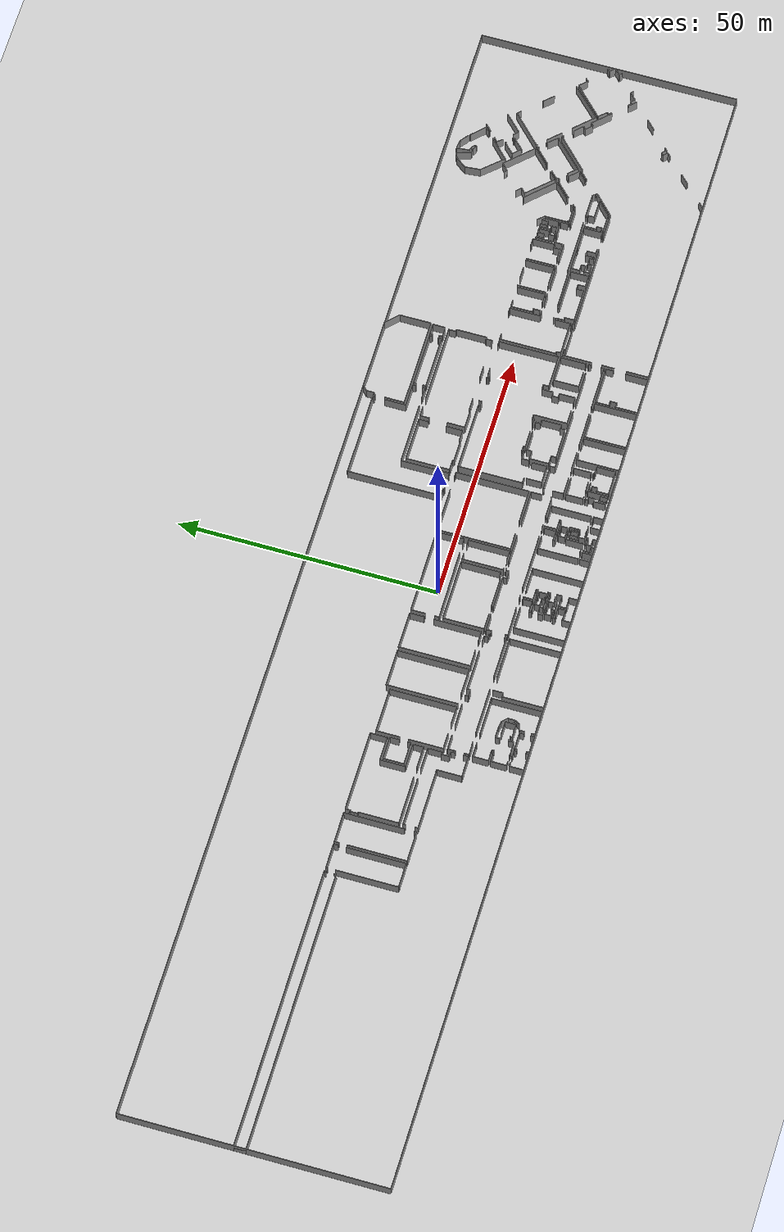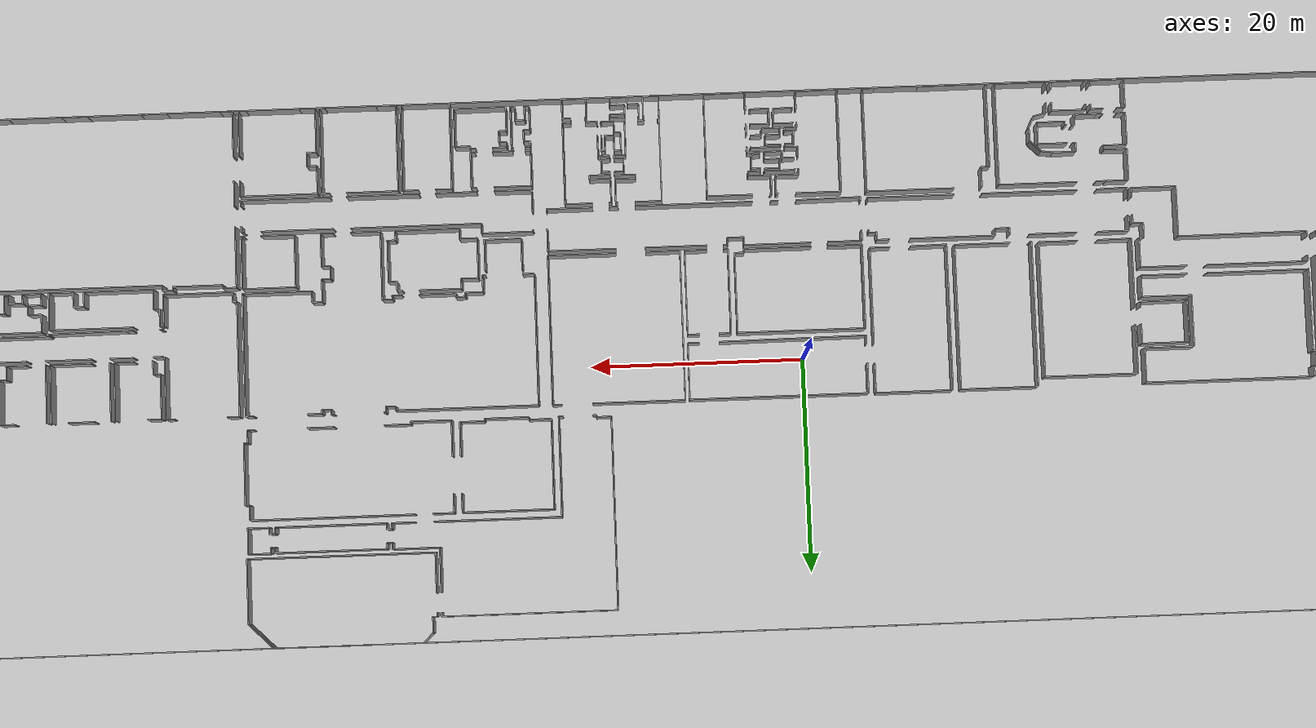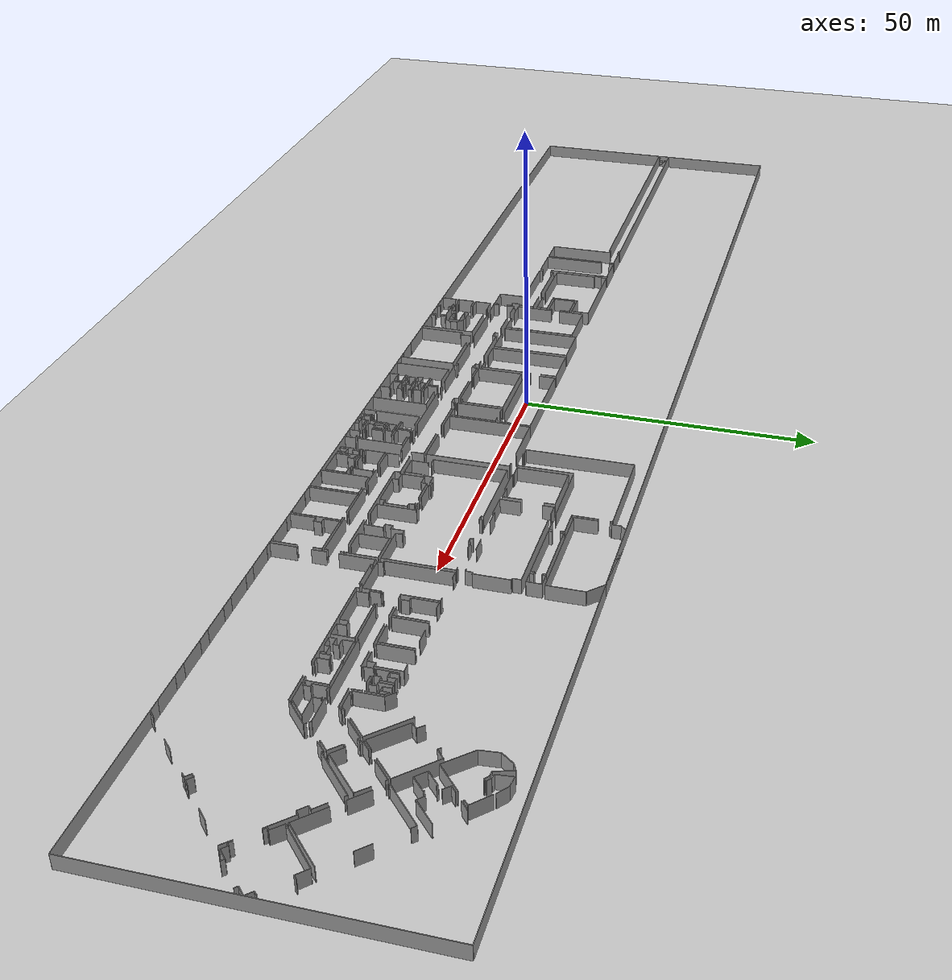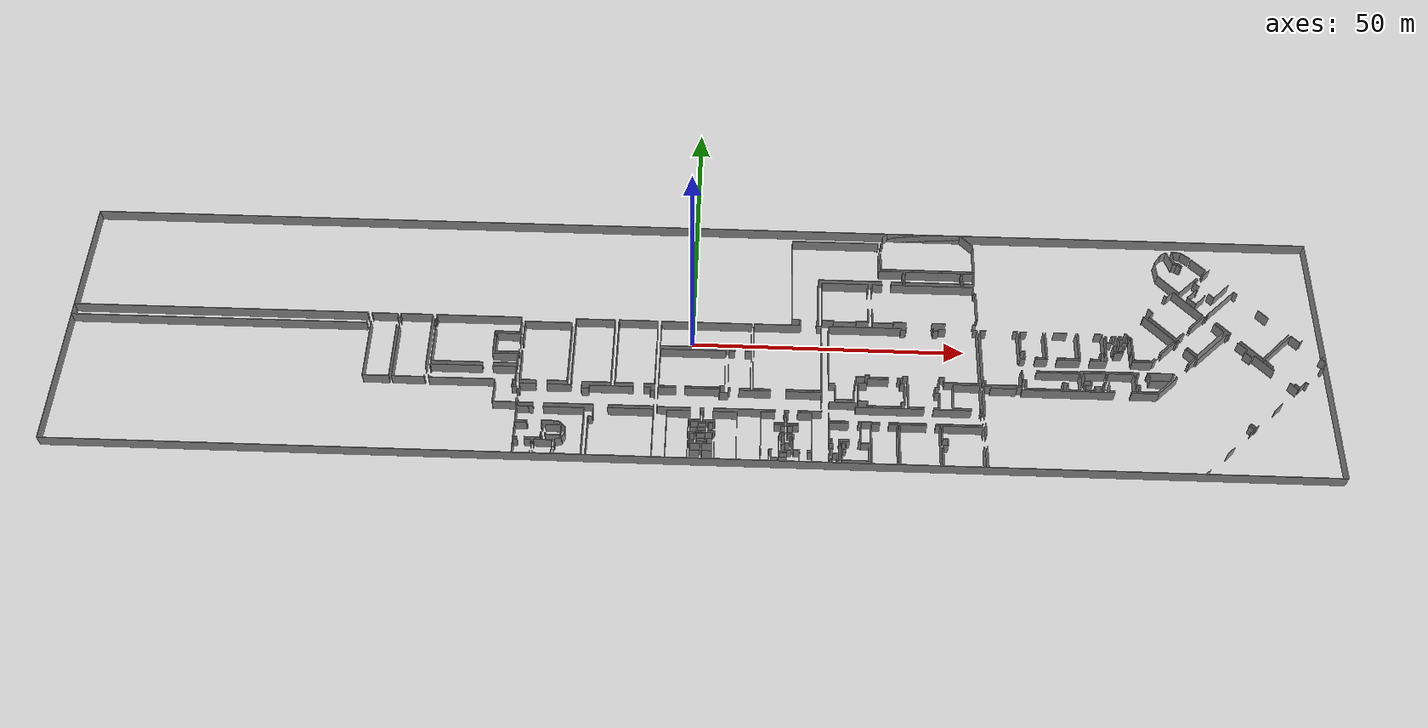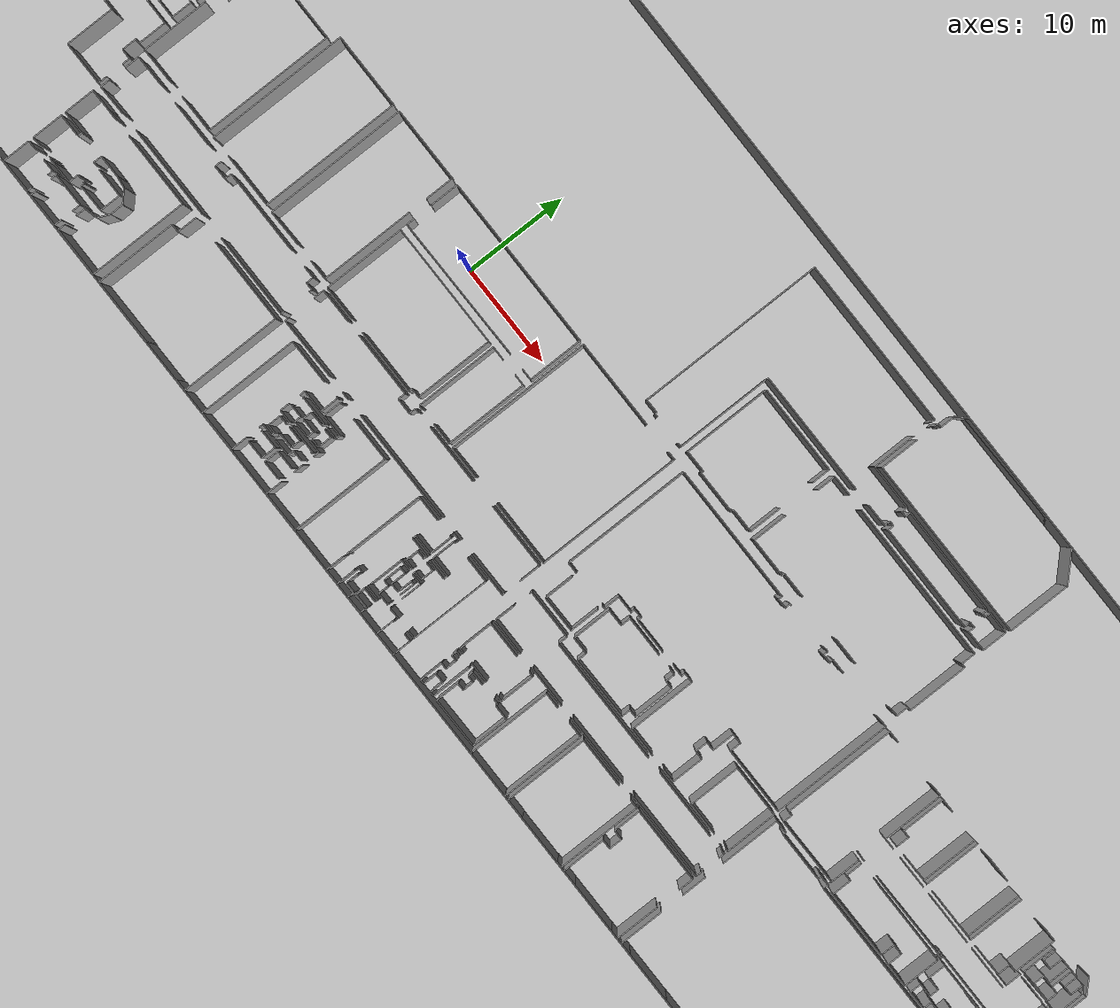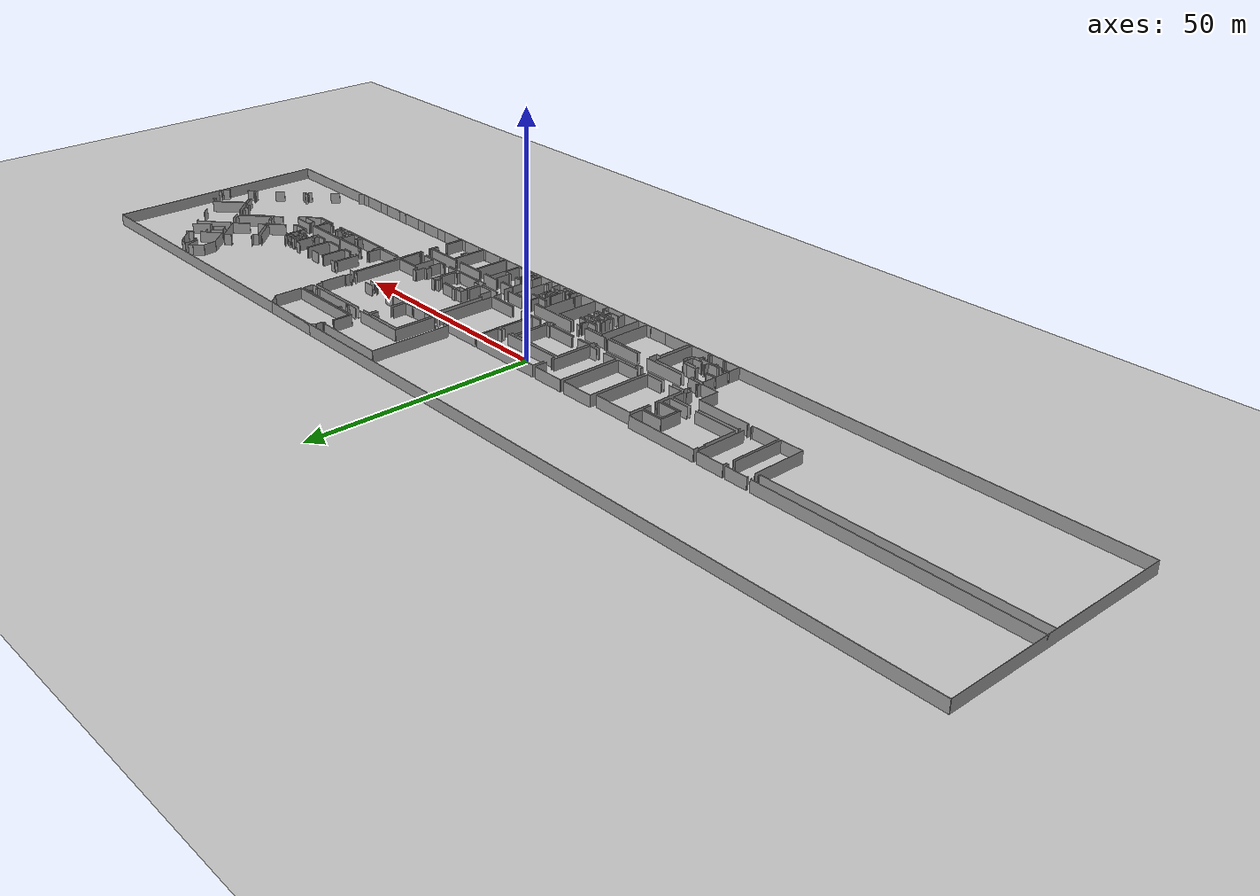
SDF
<sdf version="1.6">
  <world name="default">
    <light name="sun" type="directional">
      <cast_shadows>1</cast_shadows>
      <pose frame="">0 0 10 0 -0 0</pose>
      <diffuse>0.8 0.8 0.8 1</diffuse>
      <specular>0.1 0.1 0.1 1</specular>
      <attenuation>
        <range>1000</range>
        <constant>0.9</constant>
        <linear>0.01</linear>
        <quadratic>0.001</quadratic>
      </attenuation>
      <direction>-0.5 0.5 -1</direction>
    </light>
    <model name="ground_plane">
      <static>1</static>
      <link name="link">
        <collision name="collision">
          <geometry>
            <plane>
              <normal>0 0 1</normal>
              <size>100 100</size>
            </plane>
          </geometry>
          <surface>
            <friction>
              <ode>
                <mu>100</mu>
                <mu2>50</mu2>
              </ode>
              <torsional>
                <ode />
              </torsional>
            </friction>
            <contact>
              <ode />
            </contact>
            <bounce />
          </surface>
          <max_contacts>10</max_contacts>
        </collision>
        <visual name="visual">
          <cast_shadows>0</cast_shadows>
          <geometry>
            <plane>
              <normal>0 0 1</normal>
              <size>100 100</size>
            </plane>
          </geometry>
          <material>
            <script>
              <uri>file://media/materials/scripts/gazebo.material</uri>
              <name>Gazebo/Grey</name>
            </script>
          </material>
        </visual>
        <self_collide>0</self_collide>
        <kinematic>0</kinematic>
        <gravity>1</gravity>
      </link>
    </model>
    <gravity>0 0 -9.8</gravity>
    <magnetic_field>6e-06 2.3e-05 -4.2e-05</magnetic_field>
    <atmosphere type="adiabatic" />
    <physics default="0" name="default_physics" type="ode">
      <max_step_size>0.001</max_step_size>
      <real_time_factor>1</real_time_factor>
      <real_time_update_rate>1000</real_time_update_rate>
    </physics>
    <scene>
      <ambient>0.4 0.4 0.4 1</ambient>
      <background>0.7 0.7 0.7 1</background>
      <shadows>1</shadows>
    </scene>
    <spherical_coordinates>
      <surface_model>EARTH_WGS84</surface_model>
      <latitude_deg>0</latitude_deg>
      <longitude_deg>0</longitude_deg>
      <elevation>0</elevation>
      <heading_deg>0</heading_deg>
    </spherical_coordinates>
  <model name="0510035342_A_40_1_101">
		<static>1</static>
		<link name="Wall_0">
			<collision name="Wall_0_Collision">
				<geometry>
					<box>
						<size>2.28792034949 0.1 2.5</size>
					</box>
				</geometry>
				<pose frame="">1.14396017474 0 1.25 0 0 0</pose>
			</collision>
			<visual name="Wall_0_Visual">
				<pose frame="">1.14396017474 0 1.25 0 0 0</pose>
				<geometry>
					<box>
						<size>2.28792034949 0.1 2.5</size>
					</box>
				</geometry>
				<material>
					<script>
						<uri>file://media/materials/scripts/gazebo.material</uri>
						<name>Gazebo/Grey</name>
					</script>
					<ambient>1 1 1 1</ambient>
				</material>
			</visual>
			<pose frame="">0.0 -23.9883673677 0 0 0 1.57079632679</pose>
		</link>
		<link name="Wall_1">
			<collision name="Wall_1_Collision">
				<geometry>
					<box>
						<size>55.1437569847 0.1 2.5</size>
					</box>
				</geometry>
				<pose frame="">27.5718784923 0 1.25 0 0 0</pose>
			</collision>
			<visual name="Wall_1_Visual">
				<pose frame="">27.5718784923 0 1.25 0 0 0</pose>
				<geometry>
					<box>
						<size>55.1437569847 0.1 2.5</size>
					</box>
				</geometry>
				<material>
					<script>
						<uri>file://media/materials/scripts/gazebo.material</uri>
						<name>Gazebo/Grey</name>
					</script>
					<ambient>1 1 1 1</ambient>
				</material>
			</visual>
			<pose frame="">0.0 -21.7004470182 0 0 0 0.0</pose>
		</link>
		<link name="Wall_2">
			<collision name="Wall_2_Collision">
				<geometry>
					<box>
						<size>0.41730163568 0.1 2.5</size>
					</box>
				</geometry>
				<pose frame="">0.20865081784 0 1.25 0 0 0</pose>
			</collision>
			<visual name="Wall_2_Visual">
				<pose frame="">0.20865081784 0 1.25 0 0 0</pose>
				<geometry>
					<box>
						<size>0.41730163568 0.1 2.5</size>
					</box>
				</geometry>
				<material>
					<script>
						<uri>file://media/materials/scripts/gazebo.material</uri>
						<name>Gazebo/Grey</name>
					</script>
					<ambient>1 1 1 1</ambient>
				</material>
			</visual>
			<pose frame="">55.1437569847 -21.7004470182 0 0 0 -1.57079632679</pose>
		</link>
		<link name="Wall_3">
			<collision name="Wall_3_Collision">
				<geometry>
					<box>
						<size>0.384283246978 0.1 2.5</size>
					</box>
				</geometry>
				<pose frame="">0.192141623489 0 1.25 0 0 0</pose>
			</collision>
			<visual name="Wall_3_Visual">
				<pose frame="">0.192141623489 0 1.25 0 0 0</pose>
				<geometry>
					<box>
						<size>0.384283246978 0.1 2.5</size>
					</box>
				</geometry>
				<material>
					<script>
						<uri>file://media/materials/scripts/gazebo.material</uri>
						<name>Gazebo/Grey</name>
					</script>
					<ambient>1 1 1 1</ambient>
				</material>
			</visual>
			<pose frame="">55.1437569847 -23.5725896576 0 0 0 -1.57079632679</pose>
		</link>
		<link name="Wall_4">
			<collision name="Wall_4_Collision">
				<geometry>
					<box>
						<size>55.1437659784 0.1 2.5</size>
					</box>
				</geometry>
				<pose frame="">27.5718829892 0 1.25 0 0 0</pose>
			</collision>
			<visual name="Wall_4_Visual">
				<pose frame="">27.5718829892 0 1.25 0 0 0</pose>
				<geometry>
					<box>
						<size>55.1437659784 0.1 2.5</size>
					</box>
				</geometry>
				<material>
					<script>
						<uri>file://media/materials/scripts/gazebo.material</uri>
						<name>Gazebo/Grey</name>
					</script>
					<ambient>1 1 1 1</ambient>
				</material>
			</visual>
			<pose frame="">55.1437569847 -23.9568729046 0 0 0 -3.14102151986</pose>
		</link>
		<link name="Wall_5">
			<collision name="Wall_5_Collision">
				<geometry>
					<box>
						<size>11.8612211724 0.1 2.5</size>
					</box>
				</geometry>
				<pose frame="">5.9306105862 0 1.25 0 0 0</pose>
			</collision>
			<visual name="Wall_5_Visual">
				<pose frame="">5.9306105862 0 1.25 0 0 0</pose>
				<geometry>
					<box>
						<size>11.8612211724 0.1 2.5</size>
					</box>
				</geometry>
				<material>
					<script>
						<uri>file://media/materials/scripts/gazebo.material</uri>
						<name>Gazebo/Grey</name>
					</script>
					<ambient>1 1 1 1</ambient>
				</material>
			</visual>
			<pose frame="">55.9003860612 -35.4320329168 0 0 0 1.57079632679</pose>
		</link>
		<link name="Wall_6">
			<collision name="Wall_6_Collision">
				<geometry>
					<box>
						<size>0.318500457178 0.1 2.5</size>
					</box>
				</geometry>
				<pose frame="">0.159250228589 0 1.25 0 0 0</pose>
			</collision>
			<visual name="Wall_6_Visual">
				<pose frame="">0.159250228589 0 1.25 0 0 0</pose>
				<geometry>
					<box>
						<size>0.318500457178 0.1 2.5</size>
					</box>
				</geometry>
				<material>
					<script>
						<uri>file://media/materials/scripts/gazebo.material</uri>
						<name>Gazebo/Grey</name>
					</script>
					<ambient>1 1 1 1</ambient>
				</material>
			</visual>
			<pose frame="">55.9003860612 -22.0900640049 0 0 0 1.57079632679</pose>
		</link>
		<link name="Wall_7">
			<collision name="Wall_7_Collision">
				<geometry>
					<box>
						<size>4.83109824241 0.1 2.5</size>
					</box>
				</geometry>
				<pose frame="">2.4155491212 0 1.25 0 0 0</pose>
			</collision>
			<visual name="Wall_7_Visual">
				<pose frame="">2.4155491212 0 1.25 0 0 0</pose>
				<geometry>
					<box>
						<size>4.83109824241 0.1 2.5</size>
					</box>
				</geometry>
				<material>
					<script>
						<uri>file://media/materials/scripts/gazebo.material</uri>
						<name>Gazebo/Grey</name>
					</script>
					<ambient>1 1 1 1</ambient>
				</material>
			</visual>
			<pose frame="">55.9003860612 -21.7715635477 0 0 0 0.0</pose>
		</link>
		<link name="Wall_8">
			<collision name="Wall_8_Collision">
				<geometry>
					<box>
						<size>0.889464594128 0.1 2.5</size>
					</box>
				</geometry>
				<pose frame="">0.444732297064 0 1.25 0 0 0</pose>
			</collision>
			<visual name="Wall_8_Visual">
				<pose frame="">0.444732297064 0 1.25 0 0 0</pose>
				<geometry>
					<box>
						<size>0.889464594128 0.1 2.5</size>
					</box>
				</geometry>
				<material>
					<script>
						<uri>file://media/materials/scripts/gazebo.material</uri>
						<name>Gazebo/Grey</name>
					</script>
					<ambient>1 1 1 1</ambient>
				</material>
			</visual>
			<pose frame="">60.7314843036 -21.7715635477 0 0 0 -1.57079632679</pose>
		</link>
		<link name="Wall_9">
			<collision name="Wall_9_Collision">
				<geometry>
					<box>
						<size>11.2237122828 0.1 2.5</size>
					</box>
				</geometry>
				<pose frame="">5.61185614142 0 1.25 0 0 0</pose>
			</collision>
			<visual name="Wall_9_Visual">
				<pose frame="">5.61185614142 0 1.25 0 0 0</pose>
				<geometry>
					<box>
						<size>11.2237122828 0.1 2.5</size>
					</box>
				</geometry>
				<material>
					<script>
						<uri>file://media/materials/scripts/gazebo.material</uri>
						<name>Gazebo/Grey</name>
					</script>
					<ambient>1 1 1 1</ambient>
				</material>
			</visual>
			<pose frame="">60.7314843036 -24.1692065427 0 0 0 -1.57079632679</pose>
		</link>
		<link name="Wall_10">
			<collision name="Wall_10_Collision">
				<geometry>
					<box>
						<size>4.8312565798 0.1 2.5</size>
					</box>
				</geometry>
				<pose frame="">2.4156282899 0 1.25 0 0 0</pose>
			</collision>
			<visual name="Wall_10_Visual">
				<pose frame="">2.4156282899 0 1.25 0 0 0</pose>
				<geometry>
					<box>
						<size>4.8312565798 0.1 2.5</size>
					</box>
				</geometry>
				<material>
					<script>
						<uri>file://media/materials/scripts/gazebo.material</uri>
						<name>Gazebo/Grey</name>
					</script>
					<ambient>1 1 1 1</ambient>
				</material>
			</visual>
			<pose frame="">60.7314843036 -35.3929188256 0 0 0 -3.13349651589</pose>
		</link>
		<link name="Wall_11">
			<collision name="Wall_11_Collision">
				<geometry>
					<box>
						<size>11.2488570558 0.1 2.5</size>
					</box>
				</geometry>
				<pose frame="">5.62442852789 0 1.25 0 0 0</pose>
			</collision>
			<visual name="Wall_11_Visual">
				<pose frame="">5.62442852789 0 1.25 0 0 0</pose>
				<geometry>
					<box>
						<size>11.2488570558 0.1 2.5</size>
					</box>
				</geometry>
				<material>
					<script>
						<uri>file://media/materials/scripts/gazebo.material</uri>
						<name>Gazebo/Grey</name>
					</script>
					<ambient>1 1 1 1</ambient>
				</material>
			</visual>
			<pose frame="">61.2310779234 -35.4310169664 0 0 0 1.57079632679</pose>
		</link>
		<link name="Wall_12">
			<collision name="Wall_12_Collision">
				<geometry>
					<box>
						<size>0.913339429036 0.1 2.5</size>
					</box>
				</geometry>
				<pose frame="">0.456669714518 0 1.25 0 0 0</pose>
			</collision>
			<visual name="Wall_12_Visual">
				<pose frame="">0.456669714518 0 1.25 0 0 0</pose>
				<geometry>
					<box>
						<size>0.913339429036 0.1 2.5</size>
					</box>
				</geometry>
				<material>
					<script>
						<uri>file://media/materials/scripts/gazebo.material</uri>
						<name>Gazebo/Grey</name>
					</script>
					<ambient>1 1 1 1</ambient>
				</material>
			</visual>
			<pose frame="">61.2310779234 -22.6554404145 0 0 0 1.57079632679</pose>
		</link>
		<link name="Wall_13">
			<collision name="Wall_13_Collision">
				<geometry>
					<box>
						<size>5.95524738393 0.1 2.5</size>
					</box>
				</geometry>
				<pose frame="">2.97762369196 0 1.25 0 0 0</pose>
			</collision>
			<visual name="Wall_13_Visual">
				<pose frame="">2.97762369196 0 1.25 0 0 0</pose>
				<geometry>
					<box>
						<size>5.95524738393 0.1 2.5</size>
					</box>
				</geometry>
				<material>
					<script>
						<uri>file://media/materials/scripts/gazebo.material</uri>
						<name>Gazebo/Grey</name>
					</script>
					<ambient>1 1 1 1</ambient>
				</material>
			</visual>
			<pose frame="">61.2310779234 -21.7421009855 0 0 0 0.0</pose>
		</link>
		<link name="Wall_14">
			<collision name="Wall_14_Collision">
				<geometry>
					<box>
						<size>11.456618917 0.1 2.5</size>
					</box>
				</geometry>
				<pose frame="">5.7283094585 0 1.25 0 0 0</pose>
			</collision>
			<visual name="Wall_14_Visual">
				<pose frame="">5.7283094585 0 1.25 0 0 0</pose>
				<geometry>
					<box>
						<size>11.456618917 0.1 2.5</size>
					</box>
				</geometry>
				<material>
					<script>
						<uri>file://media/materials/scripts/gazebo.material</uri>
						<name>Gazebo/Grey</name>
					</script>
					<ambient>1 1 1 1</ambient>
				</material>
			</visual>
			<pose frame="">67.1863253073 -21.7421009855 0 0 0 -1.57079632679</pose>
		</link>
		<link name="Wall_15">
			<collision name="Wall_15_Collision">
				<geometry>
					<box>
						<size>0.483338413085 0.1 2.5</size>
					</box>
				</geometry>
				<pose frame="">0.241669206543 0 1.25 0 0 0</pose>
			</collision>
			<visual name="Wall_15_Visual">
				<pose frame="">0.241669206543 0 1.25 0 0 0</pose>
				<geometry>
					<box>
						<size>0.483338413085 0.1 2.5</size>
					</box>
				</geometry>
				<material>
					<script>
						<uri>file://media/materials/scripts/gazebo.material</uri>
						<name>Gazebo/Grey</name>
					</script>
					<ambient>1 1 1 1</ambient>
				</material>
			</visual>
			<pose frame="">67.1863253073 -34.9263435944 0 0 0 -1.57079632679</pose>
		</link>
		<link name="Wall_16">
			<collision name="Wall_16_Collision">
				<geometry>
					<box>
						<size>5.95528560056 0.1 2.5</size>
					</box>
				</geometry>
				<pose frame="">2.97764280028 0 1.25 0 0 0</pose>
			</collision>
			<visual name="Wall_16_Visual">
				<pose frame="">2.97764280028 0 1.25 0 0 0</pose>
				<geometry>
					<box>
						<size>5.95528560056 0.1 2.5</size>
					</box>
				</geometry>
				<material>
					<script>
						<uri>file://media/materials/scripts/gazebo.material</uri>
						<name>Gazebo/Grey</name>
					</script>
					<ambient>1 1 1 1</ambient>
				</material>
			</visual>
			<pose frame="">67.1863253073 -35.4096820075 0 0 0 -3.13801012104</pose>
		</link>
		<link name="Wall_17">
			<collision name="Wall_17_Collision">
				<geometry>
					<box>
						<size>0.574773951031 0.1 2.5</size>
					</box>
				</geometry>
				<pose frame="">0.287386975516 0 1.25 0 0 0</pose>
			</collision>
			<visual name="Wall_17_Visual">
				<pose frame="">0.287386975516 0 1.25 0 0 0</pose>
				<geometry>
					<box>
						<size>0.574773951031 0.1 2.5</size>
					</box>
				</geometry>
				<material>
					<script>
						<uri>file://media/materials/scripts/gazebo.material</uri>
						<name>Gazebo/Grey</name>
					</script>
					<ambient>1 1 1 1</ambient>
				</material>
			</visual>
			<pose frame="">67.9990856446 -35.4640353551 0 0 0 1.57079632679</pose>
		</link>
		<link name="Wall_18">
			<collision name="Wall_18_Collision">
				<geometry>
					<box>
						<size>0.580869653561 0.1 2.5</size>
					</box>
				</geometry>
				<pose frame="">0.29043482678 0 1.25 0 0 0</pose>
			</collision>
			<visual name="Wall_18_Visual">
				<pose frame="">0.29043482678 0 1.25 0 0 0</pose>
				<geometry>
					<box>
						<size>0.580869653561 0.1 2.5</size>
					</box>
				</geometry>
				<material>
					<script>
						<uri>file://media/materials/scripts/gazebo.material</uri>
						<name>Gazebo/Grey</name>
					</script>
					<ambient>1 1 1 1</ambient>
				</material>
			</visual>
			<pose frame="">67.9990856446 -33.1987199025 0 0 0 1.57079632679</pose>
		</link>
		<link name="Wall_19">
			<collision name="Wall_19_Collision">
				<geometry>
					<box>
						<size>9.48897693793 0.1 2.5</size>
					</box>
				</geometry>
				<pose frame="">4.74448846896 0 1.25 0 0 0</pose>
			</collision>
			<visual name="Wall_19_Visual">
				<pose frame="">4.74448846896 0 1.25 0 0 0</pose>
				<geometry>
					<box>
						<size>9.48897693793 0.1 2.5</size>
					</box>
				</geometry>
				<material>
					<script>
						<uri>file://media/materials/scripts/gazebo.material</uri>
						<name>Gazebo/Grey</name>
					</script>
					<ambient>1 1 1 1</ambient>
				</material>
			</visual>
			<pose frame="">67.9990856446 -32.6178502489 0 0 0 0.0</pose>
		</link>
		<link name="Wall_20">
			<collision name="Wall_20_Collision">
				<geometry>
					<box>
						<size>4.37392055268 0.1 2.5</size>
					</box>
				</geometry>
				<pose frame="">2.18696027634 0 1.25 0 0 0</pose>
			</collision>
			<visual name="Wall_20_Visual">
				<pose frame="">2.18696027634 0 1.25 0 0 0</pose>
				<geometry>
					<box>
						<size>4.37392055268 0.1 2.5</size>
					</box>
				</geometry>
				<material>
					<script>
						<uri>file://media/materials/scripts/gazebo.material</uri>
						<name>Gazebo/Grey</name>
					</script>
					<ambient>1 1 1 1</ambient>
				</material>
			</visual>
			<pose frame="">79.3922076603 -32.6178502489 0 0 0 0.0</pose>
		</link>
		<link name="Wall_21">
			<collision name="Wall_21_Collision">
				<geometry>
					<box>
						<size>2.7773544651 0.1 2.5</size>
					</box>
				</geometry>
				<pose frame="">1.38867723255 0 1.25 0 0 0</pose>
			</collision>
			<visual name="Wall_21_Visual">
				<pose frame="">1.38867723255 0 1.25 0 0 0</pose>
				<geometry>
					<box>
						<size>2.7773544651 0.1 2.5</size>
					</box>
				</geometry>
				<material>
					<script>
						<uri>file://media/materials/scripts/gazebo.material</uri>
						<name>Gazebo/Grey</name>
					</script>
					<ambient>1 1 1 1</ambient>
				</material>
			</visual>
			<pose frame="">83.7661282129 -32.6178502489 0 0 0 -1.57079632679</pose>
		</link>
		<link name="Wall_22">
			<collision name="Wall_22_Collision">
				<geometry>
					<box>
						<size>0.454637813675 0.1 2.5</size>
					</box>
				</geometry>
				<pose frame="">0.227318906837 0 1.25 0 0 0</pose>
			</collision>
			<visual name="Wall_22_Visual">
				<pose frame="">0.227318906837 0 1.25 0 0 0</pose>
				<geometry>
					<box>
						<size>0.454637813675 0.1 2.5</size>
					</box>
				</geometry>
				<material>
					<script>
						<uri>file://media/materials/scripts/gazebo.material</uri>
						<name>Gazebo/Grey</name>
					</script>
					<ambient>1 1 1 1</ambient>
				</material>
			</visual>
			<pose frame="">83.7661282129 -35.395204714 0 0 0 3.14159265359</pose>
		</link>
		<link name="Wall_23">
			<collision name="Wall_23_Collision">
				<geometry>
					<box>
						<size>1.43401402012 0.1 2.5</size>
					</box>
				</geometry>
				<pose frame="">0.717007010058 0 1.25 0 0 0</pose>
			</collision>
			<visual name="Wall_23_Visual">
				<pose frame="">0.717007010058 0 1.25 0 0 0</pose>
				<geometry>
					<box>
						<size>1.43401402012 0.1 2.5</size>
					</box>
				</geometry>
				<material>
					<script>
						<uri>file://media/materials/scripts/gazebo.material</uri>
						<name>Gazebo/Grey</name>
					</script>
					<ambient>1 1 1 1</ambient>
				</material>
			</visual>
			<pose frame="">83.3114903993 -35.395204714 0 0 0 -1.57079632679</pose>
		</link>
		<link name="Wall_24">
			<collision name="Wall_24_Collision">
				<geometry>
					<box>
						<size>0.966676826171 0.1 2.5</size>
					</box>
				</geometry>
				<pose frame="">0.483338413085 0 1.25 0 0 0</pose>
			</collision>
			<visual name="Wall_24_Visual">
				<pose frame="">0.483338413085 0 1.25 0 0 0</pose>
				<geometry>
					<box>
						<size>0.966676826171 0.1 2.5</size>
					</box>
				</geometry>
				<material>
					<script>
						<uri>file://media/materials/scripts/gazebo.material</uri>
						<name>Gazebo/Grey</name>
					</script>
					<ambient>1 1 1 1</ambient>
				</material>
			</visual>
			<pose frame="">83.3114903993 -36.8292187341 0 0 0 0.0</pose>
		</link>
		<link name="Wall_25">
			<collision name="Wall_25_Collision">
				<geometry>
					<box>
						<size>0.798537031393 0.1 2.5</size>
					</box>
				</geometry>
				<pose frame="">0.399268515696 0 1.25 0 0 0</pose>
			</collision>
			<visual name="Wall_25_Visual">
				<pose frame="">0.399268515696 0 1.25 0 0 0</pose>
				<geometry>
					<box>
						<size>0.798537031393 0.1 2.5</size>
					</box>
				</geometry>
				<material>
					<script>
						<uri>file://media/materials/scripts/gazebo.material</uri>
						<name>Gazebo/Grey</name>
					</script>
					<ambient>1 1 1 1</ambient>
				</material>
			</visual>
			<pose frame="">84.2781672254 -36.8292187341 0 0 0 -1.57079632679</pose>
		</link>
		<link name="Wall_26">
			<collision name="Wall_26_Collision">
				<geometry>
					<box>
						<size>0.90038606116 0.1 2.5</size>
					</box>
				</geometry>
				<pose frame="">0.45019303058 0 1.25 0 0 0</pose>
			</collision>
			<visual name="Wall_26_Visual">
				<pose frame="">0.45019303058 0 1.25 0 0 0</pose>
				<geometry>
					<box>
						<size>0.90038606116 0.1 2.5</size>
					</box>
				</geometry>
				<material>
					<script>
						<uri>file://media/materials/scripts/gazebo.material</uri>
						<name>Gazebo/Grey</name>
					</script>
					<ambient>1 1 1 1</ambient>
				</material>
			</visual>
			<pose frame="">84.2781672254 -39.268769684 0 0 0 -1.57079632679</pose>
		</link>
		<link name="Wall_27">
			<collision name="Wall_27_Collision">
				<geometry>
					<box>
						<size>4.20832063395 0.1 2.5</size>
					</box>
				</geometry>
				<pose frame="">2.10416031698 0 1.25 0 0 0</pose>
			</collision>
			<visual name="Wall_27_Visual">
				<pose frame="">2.10416031698 0 1.25 0 0 0</pose>
				<geometry>
					<box>
						<size>4.20832063395 0.1 2.5</size>
					</box>
				</geometry>
				<material>
					<script>
						<uri>file://media/materials/scripts/gazebo.material</uri>
						<name>Gazebo/Grey</name>
					</script>
					<ambient>1 1 1 1</ambient>
				</material>
			</visual>
			<pose frame="">84.2781672254 -40.1691557452 0 0 0 3.14159265359</pose>
		</link>
		<link name="Wall_28">
			<collision name="Wall_28_Collision">
				<geometry>
					<box>
						<size>4.74855227065 0.1 2.5</size>
					</box>
				</geometry>
				<pose frame="">2.37427613532 0 1.25 0 0 0</pose>
			</collision>
			<visual name="Wall_28_Visual">
				<pose frame="">2.37427613532 0 1.25 0 0 0</pose>
				<geometry>
					<box>
						<size>4.74855227065 0.1 2.5</size>
					</box>
				</geometry>
				<material>
					<script>
						<uri>file://media/materials/scripts/gazebo.material</uri>
						<name>Gazebo/Grey</name>
					</script>
					<ambient>1 1 1 1</ambient>
				</material>
			</visual>
			<pose frame="">80.0698465915 -40.1691557452 0 0 0 1.57079632679</pose>
		</link>
		<link name="Wall_29">
			<collision name="Wall_29_Collision">
				<geometry>
					<box>
						<size>12.0708390829 0.1 2.5</size>
					</box>
				</geometry>
				<pose frame="">6.03541954144 0 1.25 0 0 0</pose>
			</collision>
			<visual name="Wall_29_Visual">
				<pose frame="">6.03541954144 0 1.25 0 0 0</pose>
				<geometry>
					<box>
						<size>12.0708390829 0.1 2.5</size>
					</box>
				</geometry>
				<material>
					<script>
						<uri>file://media/materials/scripts/gazebo.material</uri>
						<name>Gazebo/Grey</name>
					</script>
					<ambient>1 1 1 1</ambient>
				</material>
			</visual>
			<pose frame="">80.0698465915 -35.4206034746 0 0 0 -3.13799456286</pose>
		</link>
		<link name="Wall_30">
			<collision name="Wall_30_Collision">
				<geometry>
					<box>
						<size>7.69658640658 0.1 2.5</size>
					</box>
				</geometry>
				<pose frame="">3.84829320329 0 1.25 0 0 0</pose>
			</collision>
			<visual name="Wall_30_Visual">
				<pose frame="">3.84829320329 0 1.25 0 0 0</pose>
				<geometry>
					<box>
						<size>7.69658640658 0.1 2.5</size>
					</box>
				</geometry>
				<material>
					<script>
						<uri>file://media/materials/scripts/gazebo.material</uri>
						<name>Gazebo/Grey</name>
					</script>
					<ambient>1 1 1 1</ambient>
				</material>
			</visual>
			<pose frame="">67.9990856446 -31.862745098 0 0 0 1.57079632679</pose>
		</link>
		<link name="Wall_31">
			<collision name="Wall_31_Collision">
				<geometry>
					<box>
						<size>0.27583053947 0.1 2.5</size>
					</box>
				</geometry>
				<pose frame="">0.137915269735 0 1.25 0 0 0</pose>
			</collision>
			<visual name="Wall_31_Visual">
				<pose frame="">0.137915269735 0 1.25 0 0 0</pose>
				<geometry>
					<box>
						<size>0.27583053947 0.1 2.5</size>
					</box>
				</geometry>
				<material>
					<script>
						<uri>file://media/materials/scripts/gazebo.material</uri>
						<name>Gazebo/Grey</name>
					</script>
					<ambient>1 1 1 1</ambient>
				</material>
			</visual>
			<pose frame="">67.9990856446 -24.1661586915 0 0 0 3.14159265359</pose>
		</link>
		<link name="Wall_32">
			<collision name="Wall_32_Collision">
				<geometry>
					<box>
						<size>1.42309255308 0.1 2.5</size>
					</box>
				</geometry>
				<pose frame="">0.711546276542 0 1.25 0 0 0</pose>
			</collision>
			<visual name="Wall_32_Visual">
				<pose frame="">0.711546276542 0 1.25 0 0 0</pose>
				<geometry>
					<box>
						<size>1.42309255308 0.1 2.5</size>
					</box>
				</geometry>
				<material>
					<script>
						<uri>file://media/materials/scripts/gazebo.material</uri>
						<name>Gazebo/Grey</name>
					</script>
					<ambient>1 1 1 1</ambient>
				</material>
			</visual>
			<pose frame="">67.7232551052 -24.1661586915 0 0 0 1.57079632679</pose>
		</link>
		<link name="Wall_33">
			<collision name="Wall_33_Collision">
				<geometry>
					<box>
						<size>0.261353245962 0.1 2.5</size>
					</box>
				</geometry>
				<pose frame="">0.130676622981 0 1.25 0 0 0</pose>
			</collision>
			<visual name="Wall_33_Visual">
				<pose frame="">0.130676622981 0 1.25 0 0 0</pose>
				<geometry>
					<box>
						<size>0.261353245962 0.1 2.5</size>
					</box>
				</geometry>
				<material>
					<script>
						<uri>file://media/materials/scripts/gazebo.material</uri>
						<name>Gazebo/Grey</name>
					</script>
					<ambient>1 1 1 1</ambient>
				</material>
			</visual>
			<pose frame="">67.7232551052 -22.7430661384 0 0 0 0.0</pose>
		</link>
		<link name="Wall_34">
			<collision name="Wall_34_Collision">
				<geometry>
					<box>
						<size>0.987503809814 0.1 2.5</size>
					</box>
				</geometry>
				<pose frame="">0.493751904907 0 1.25 0 0 0</pose>
			</collision>
			<visual name="Wall_34_Visual">
				<pose frame="">0.493751904907 0 1.25 0 0 0</pose>
				<geometry>
					<box>
						<size>0.987503809814 0.1 2.5</size>
					</box>
				</geometry>
				<material>
					<script>
						<uri>file://media/materials/scripts/gazebo.material</uri>
						<name>Gazebo/Grey</name>
					</script>
					<ambient>1 1 1 1</ambient>
				</material>
			</visual>
			<pose frame="">67.9846083511 -22.7430661384 0 0 0 1.57079632679</pose>
		</link>
		<link name="Wall_35">
			<collision name="Wall_35_Collision">
				<geometry>
					<box>
						<size>15.7708523824 0.1 2.5</size>
					</box>
				</geometry>
				<pose frame="">7.8854261912 0 1.25 0 0 0</pose>
			</collision>
			<visual name="Wall_35_Visual">
				<pose frame="">7.8854261912 0 1.25 0 0 0</pose>
				<geometry>
					<box>
						<size>15.7708523824 0.1 2.5</size>
					</box>
				</geometry>
				<material>
					<script>
						<uri>file://media/materials/scripts/gazebo.material</uri>
						<name>Gazebo/Grey</name>
					</script>
					<ambient>1 1 1 1</ambient>
				</material>
			</visual>
			<pose frame="">67.9846083511 -21.7555623286 0 0 0 0.0</pose>
		</link>
		<link name="Wall_36">
			<collision name="Wall_36_Collision">
				<geometry>
					<box>
						<size>3.22970639033 0.1 2.5</size>
					</box>
				</geometry>
				<pose frame="">1.61485319516 0 1.25 0 0 0</pose>
			</collision>
			<visual name="Wall_36_Visual">
				<pose frame="">1.61485319516 0 1.25 0 0 0</pose>
				<geometry>
					<box>
						<size>3.22970639033 0.1 2.5</size>
					</box>
				</geometry>
				<material>
					<script>
						<uri>file://media/materials/scripts/gazebo.material</uri>
						<name>Gazebo/Grey</name>
					</script>
					<ambient>1 1 1 1</ambient>
				</material>
			</visual>
			<pose frame="">83.7554607335 -21.7555623286 0 0 0 -1.57079632679</pose>
		</link>
		<link name="Wall_37">
			<collision name="Wall_37_Collision">
				<geometry>
					<box>
						<size>4.64035355075 0.1 2.5</size>
					</box>
				</geometry>
				<pose frame="">2.32017677537 0 1.25 0 0 0</pose>
			</collision>
			<visual name="Wall_37_Visual">
				<pose frame="">2.32017677537 0 1.25 0 0 0</pose>
				<geometry>
					<box>
						<size>4.64035355075 0.1 2.5</size>
					</box>
				</geometry>
				<material>
					<script>
						<uri>file://media/materials/scripts/gazebo.material</uri>
						<name>Gazebo/Grey</name>
					</script>
					<ambient>1 1 1 1</ambient>
				</material>
			</visual>
			<pose frame="">83.7554607335 -24.9852687189 0 0 0 3.14159265359</pose>
		</link>
		<link name="Wall_38">
			<collision name="Wall_38_Collision">
				<geometry>
					<box>
						<size>4.83135223001 0.1 2.5</size>
					</box>
				</geometry>
				<pose frame="">2.41567611501 0 1.25 0 0 0</pose>
			</collision>
			<visual name="Wall_38_Visual">
				<pose frame="">2.41567611501 0 1.25 0 0 0</pose>
				<geometry>
					<box>
						<size>4.83135223001 0.1 2.5</size>
					</box>
				</geometry>
				<material>
					<script>
						<uri>file://media/materials/scripts/gazebo.material</uri>
						<name>Gazebo/Grey</name>
					</script>
					<ambient>1 1 1 1</ambient>
				</material>
			</visual>
			<pose frame="">79.1151071828 -24.9852687189 0 0 0 -1.57079632679</pose>
		</link>
		<link name="Wall_39">
			<collision name="Wall_39_Collision">
				<geometry>
					<box>
						<size>4.65000507975 0.1 2.5</size>
					</box>
				</geometry>
				<pose frame="">2.32500253988 0 1.25 0 0 0</pose>
			</collision>
			<visual name="Wall_39_Visual">
				<pose frame="">2.32500253988 0 1.25 0 0 0</pose>
				<geometry>
					<box>
						<size>4.65000507975 0.1 2.5</size>
					</box>
				</geometry>
				<material>
					<script>
						<uri>file://media/materials/scripts/gazebo.material</uri>
						<name>Gazebo/Grey</name>
					</script>
					<ambient>1 1 1 1</ambient>
				</material>
			</visual>
			<pose frame="">79.1151071828 -29.8166209489 0 0 0 0.0</pose>
		</link>
		<link name="Wall_40">
			<collision name="Wall_40_Collision">
				<geometry>
					<box>
						<size>2.03012293 0.1 2.5</size>
					</box>
				</geometry>
				<pose frame="">1.015061465 0 1.25 0 0 0</pose>
			</collision>
			<visual name="Wall_40_Visual">
				<pose frame="">1.015061465 0 1.25 0 0 0</pose>
				<geometry>
					<box>
						<size>2.03012293 0.1 2.5</size>
					</box>
				</geometry>
				<material>
					<script>
						<uri>file://media/materials/scripts/gazebo.material</uri>
						<name>Gazebo/Grey</name>
					</script>
					<ambient>1 1 1 1</ambient>
				</material>
			</visual>
			<pose frame="">83.7651122625 -29.8166209489 0 0 0 -1.57079632679</pose>
		</link>
		<link name="Wall_41">
			<collision name="Wall_41_Collision">
				<geometry>
					<box>
						<size>4.34877577974 0.1 2.5</size>
					</box>
				</geometry>
				<pose frame="">2.17438788987 0 1.25 0 0 0</pose>
			</collision>
			<visual name="Wall_41_Visual">
				<pose frame="">2.17438788987 0 1.25 0 0 0</pose>
				<geometry>
					<box>
						<size>4.34877577974 0.1 2.5</size>
					</box>
				</geometry>
				<material>
					<script>
						<uri>file://media/materials/scripts/gazebo.material</uri>
						<name>Gazebo/Grey</name>
					</script>
					<ambient>1 1 1 1</ambient>
				</material>
			</visual>
			<pose frame="">83.7651122625 -31.8467438789 0 0 0 3.14159265359</pose>
		</link>
		<link name="Wall_42">
			<collision name="Wall_42_Collision">
				<geometry>
					<box>
						<size>9.52124680949 0.1 2.5</size>
					</box>
				</geometry>
				<pose frame="">4.76062340474 0 1.25 0 0 0</pose>
			</collision>
			<visual name="Wall_42_Visual">
				<pose frame="">4.76062340474 0 1.25 0 0 0</pose>
				<geometry>
					<box>
						<size>9.52124680949 0.1 2.5</size>
					</box>
				</geometry>
				<material>
					<script>
						<uri>file://media/materials/scripts/gazebo.material</uri>
						<name>Gazebo/Grey</name>
					</script>
					<ambient>1 1 1 1</ambient>
				</material>
			</visual>
			<pose frame="">77.5203190084 -31.8467438789 0 0 0 -3.13991207257</pose>
		</link>
		<link name="Wall_43">
			<collision name="Wall_43_Collision">
				<geometry>
					<box>
						<size>0.950421619425 0.1 2.5</size>
					</box>
				</geometry>
				<pose frame="">0.475210809712 0 1.25 0 0 0</pose>
			</collision>
			<visual name="Wall_43_Visual">
				<pose frame="">0.475210809712 0 1.25 0 0 0</pose>
				<geometry>
					<box>
						<size>0.950421619425 0.1 2.5</size>
					</box>
				</geometry>
				<material>
					<script>
						<uri>file://media/materials/scripts/gazebo.material</uri>
						<name>Gazebo/Grey</name>
					</script>
					<ambient>1 1 1 1</ambient>
				</material>
			</visual>
			<pose frame="">84.6502590674 -40.2141115514 0 0 0 1.57079632679</pose>
		</link>
		<link name="Wall_44">
			<collision name="Wall_44_Collision">
				<geometry>
					<box>
						<size>1.50309864879 0.1 2.5</size>
					</box>
				</geometry>
				<pose frame="">0.751549324393 0 1.25 0 0 0</pose>
			</collision>
			<visual name="Wall_44_Visual">
				<pose frame="">0.751549324393 0 1.25 0 0 0</pose>
				<geometry>
					<box>
						<size>1.50309864879 0.1 2.5</size>
					</box>
				</geometry>
				<material>
					<script>
						<uri>file://media/materials/scripts/gazebo.material</uri>
						<name>Gazebo/Grey</name>
					</script>
					<ambient>1 1 1 1</ambient>
				</material>
			</visual>
			<pose frame="">84.6502590674 -37.6323275424 0 0 0 1.57079632679</pose>
		</link>
		<link name="Wall_45">
			<collision name="Wall_45_Collision">
				<geometry>
					<box>
						<size>2.92517525145 0.1 2.5</size>
					</box>
				</geometry>
				<pose frame="">1.46258762572 0 1.25 0 0 0</pose>
			</collision>
			<visual name="Wall_45_Visual">
				<pose frame="">1.46258762572 0 1.25 0 0 0</pose>
				<geometry>
					<box>
						<size>2.92517525145 0.1 2.5</size>
					</box>
				</geometry>
				<material>
					<script>
						<uri>file://media/materials/scripts/gazebo.material</uri>
						<name>Gazebo/Grey</name>
					</script>
					<ambient>1 1 1 1</ambient>
				</material>
			</visual>
			<pose frame="">84.6502590674 -36.1292288936 0 0 0 0.0</pose>
		</link>
		<link name="Wall_46">
			<collision name="Wall_46_Collision">
				<geometry>
					<box>
						<size>4.43487757797 0.1 2.5</size>
					</box>
				</geometry>
				<pose frame="">2.21743878899 0 1.25 0 0 0</pose>
			</collision>
			<visual name="Wall_46_Visual">
				<pose frame="">2.21743878899 0 1.25 0 0 0</pose>
				<geometry>
					<box>
						<size>4.43487757797 0.1 2.5</size>
					</box>
				</geometry>
				<material>
					<script>
						<uri>file://media/materials/scripts/gazebo.material</uri>
						<name>Gazebo/Grey</name>
					</script>
					<ambient>1 1 1 1</ambient>
				</material>
			</visual>
			<pose frame="">89.5682210708 -36.1292288936 0 0 0 0.0</pose>
		</link>
		<link name="Wall_47">
			<collision name="Wall_47_Collision">
				<geometry>
					<box>
						<size>0.667987402215 0.1 2.5</size>
					</box>
				</geometry>
				<pose frame="">0.333993701107 0 1.25 0 0 0</pose>
			</collision>
			<visual name="Wall_47_Visual">
				<pose frame="">0.333993701107 0 1.25 0 0 0</pose>
				<geometry>
					<box>
						<size>0.667987402215 0.1 2.5</size>
					</box>
				</geometry>
				<material>
					<script>
						<uri>file://media/materials/scripts/gazebo.material</uri>
						<name>Gazebo/Grey</name>
					</script>
					<ambient>1 1 1 1</ambient>
				</material>
			</visual>
			<pose frame="">95.8925124454 -36.1292288936 0 0 0 -1.57079632679</pose>
		</link>
		<link name="Wall_48">
			<collision name="Wall_48_Collision">
				<geometry>
					<box>
						<size>1.35223001118 0.1 2.5</size>
					</box>
				</geometry>
				<pose frame="">0.676115005588 0 1.25 0 0 0</pose>
			</collision>
			<visual name="Wall_48_Visual">
				<pose frame="">0.676115005588 0 1.25 0 0 0</pose>
				<geometry>
					<box>
						<size>1.35223001118 0.1 2.5</size>
					</box>
				</geometry>
				<material>
					<script>
						<uri>file://media/materials/scripts/gazebo.material</uri>
						<name>Gazebo/Grey</name>
					</script>
					<ambient>1 1 1 1</ambient>
				</material>
			</visual>
			<pose frame="">95.8925124454 -36.7972162958 0 0 0 0.0</pose>
		</link>
		<link name="Wall_49">
			<collision name="Wall_49_Collision">
				<geometry>
					<box>
						<size>0.667987402215 0.1 2.5</size>
					</box>
				</geometry>
				<pose frame="">0.333993701107 0 1.25 0 0 0</pose>
			</collision>
			<visual name="Wall_49_Visual">
				<pose frame="">0.333993701107 0 1.25 0 0 0</pose>
				<geometry>
					<box>
						<size>0.667987402215 0.1 2.5</size>
					</box>
				</geometry>
				<material>
					<script>
						<uri>file://media/materials/scripts/gazebo.material</uri>
						<name>Gazebo/Grey</name>
					</script>
					<ambient>1 1 1 1</ambient>
				</material>
			</visual>
			<pose frame="">97.2447424566 -36.7972162958 0 0 0 1.57079632679</pose>
		</link>
		<link name="Wall_50">
			<collision name="Wall_50_Collision">
				<geometry>
					<box>
						<size>7.99933963223 0.1 2.5</size>
					</box>
				</geometry>
				<pose frame="">3.99966981611 0 1.25 0 0 0</pose>
			</collision>
			<visual name="Wall_50_Visual">
				<pose frame="">3.99966981611 0 1.25 0 0 0</pose>
				<geometry>
					<box>
						<size>7.99933963223 0.1 2.5</size>
					</box>
				</geometry>
				<material>
					<script>
						<uri>file://media/materials/scripts/gazebo.material</uri>
						<name>Gazebo/Grey</name>
					</script>
					<ambient>1 1 1 1</ambient>
				</material>
			</visual>
			<pose frame="">97.2447424566 -36.1292288936 0 0 0 0.0</pose>
		</link>
		<link name="Wall_51">
			<collision name="Wall_51_Collision">
				<geometry>
					<box>
						<size>1.21990246876 0.1 2.5</size>
					</box>
				</geometry>
				<pose frame="">0.60995123438 0 1.25 0 0 0</pose>
			</collision>
			<visual name="Wall_51_Visual">
				<pose frame="">0.60995123438 0 1.25 0 0 0</pose>
				<geometry>
					<box>
						<size>1.21990246876 0.1 2.5</size>
					</box>
				</geometry>
				<material>
					<script>
						<uri>file://media/materials/scripts/gazebo.material</uri>
						<name>Gazebo/Grey</name>
					</script>
					<ambient>1 1 1 1</ambient>
				</material>
			</visual>
			<pose frame="">107.178959667 -36.1292288936 0 0 0 0.0</pose>
		</link>
		<link name="Wall_52">
			<collision name="Wall_52_Collision">
				<geometry>
					<box>
						<size>0.714467134004 0.1 2.5</size>
					</box>
				</geometry>
				<pose frame="">0.357233567002 0 1.25 0 0 0</pose>
			</collision>
			<visual name="Wall_52_Visual">
				<pose frame="">0.357233567002 0 1.25 0 0 0</pose>
				<geometry>
					<box>
						<size>0.714467134004 0.1 2.5</size>
					</box>
				</geometry>
				<material>
					<script>
						<uri>file://media/materials/scripts/gazebo.material</uri>
						<name>Gazebo/Grey</name>
					</script>
					<ambient>1 1 1 1</ambient>
				</material>
			</visual>
			<pose frame="">108.398862136 -36.1292288936 0 0 0 -1.57079632679</pose>
		</link>
		<link name="Wall_53">
			<collision name="Wall_53_Collision">
				<geometry>
					<box>
						<size>0.726150563852 0.1 2.5</size>
					</box>
				</geometry>
				<pose frame="">0.363075281926 0 1.25 0 0 0</pose>
			</collision>
			<visual name="Wall_53_Visual">
				<pose frame="">0.363075281926 0 1.25 0 0 0</pose>
				<geometry>
					<box>
						<size>0.726150563852 0.1 2.5</size>
					</box>
				</geometry>
				<material>
					<script>
						<uri>file://media/materials/scripts/gazebo.material</uri>
						<name>Gazebo/Grey</name>
					</script>
					<ambient>1 1 1 1</ambient>
				</material>
			</visual>
			<pose frame="">108.398862136 -36.8436960276 0 0 0 0.0</pose>
		</link>
		<link name="Wall_54">
			<collision name="Wall_54_Collision">
				<geometry>
					<box>
						<size>0.305039114091 0.1 2.5</size>
					</box>
				</geometry>
				<pose frame="">0.152519557046 0 1.25 0 0 0</pose>
			</collision>
			<visual name="Wall_54_Visual">
				<pose frame="">0.152519557046 0 1.25 0 0 0</pose>
				<geometry>
					<box>
						<size>0.305039114091 0.1 2.5</size>
					</box>
				</geometry>
				<material>
					<script>
						<uri>file://media/materials/scripts/gazebo.material</uri>
						<name>Gazebo/Grey</name>
					</script>
					<ambient>1 1 1 1</ambient>
				</material>
			</visual>
			<pose frame="">109.125012699 -36.8436960276 0 0 0 -1.57079632679</pose>
		</link>
		<link name="Wall_55">
			<collision name="Wall_55_Collision">
				<geometry>
					<box>
						<size>0.368028040232 0.1 2.5</size>
					</box>
				</geometry>
				<pose frame="">0.184014020116 0 1.25 0 0 0</pose>
			</collision>
			<visual name="Wall_55_Visual">
				<pose frame="">0.184014020116 0 1.25 0 0 0</pose>
				<geometry>
					<box>
						<size>0.368028040232 0.1 2.5</size>
					</box>
				</geometry>
				<material>
					<script>
						<uri>file://media/materials/scripts/gazebo.material</uri>
						<name>Gazebo/Grey</name>
					</script>
					<ambient>1 1 1 1</ambient>
				</material>
			</visual>
			<pose frame="">109.125012699 -39.7866504115 0 0 0 -1.57079632679</pose>
		</link>
		<link name="Wall_56">
			<collision name="Wall_56_Collision">
				<geometry>
					<box>
						<size>8.19338616276 0.1 2.5</size>
					</box>
				</geometry>
				<pose frame="">4.09669308138 0 1.25 0 0 0</pose>
			</collision>
			<visual name="Wall_56_Visual">
				<pose frame="">4.09669308138 0 1.25 0 0 0</pose>
				<geometry>
					<box>
						<size>8.19338616276 0.1 2.5</size>
					</box>
				</geometry>
				<material>
					<script>
						<uri>file://media/materials/scripts/gazebo.material</uri>
						<name>Gazebo/Grey</name>
					</script>
					<ambient>1 1 1 1</ambient>
				</material>
			</visual>
			<pose frame="">109.125012699 -40.1546784517 0 0 0 3.14159265359</pose>
		</link>
		<link name="Wall_57">
			<collision name="Wall_57_Collision">
				<geometry>
					<box>
						<size>8.97439804938 0.1 2.5</size>
					</box>
				</geometry>
				<pose frame="">4.48719902469 0 1.25 0 0 0</pose>
			</collision>
			<visual name="Wall_57_Visual">
				<pose frame="">4.48719902469 0 1.25 0 0 0</pose>
				<geometry>
					<box>
						<size>8.97439804938 0.1 2.5</size>
					</box>
				</geometry>
				<material>
					<script>
						<uri>file://media/materials/scripts/gazebo.material</uri>
						<name>Gazebo/Grey</name>
					</script>
					<ambient>1 1 1 1</ambient>
				</material>
			</visual>
			<pose frame="">98.3061566596 -40.1546784517 0 0 0 3.14159265359</pose>
		</link>
		<link name="Wall_58">
			<collision name="Wall_58_Collision">
				<geometry>
					<box>
						<size>2.82903033669 0.1 2.5</size>
					</box>
				</geometry>
				<pose frame="">1.41451516834 0 1.25 0 0 0</pose>
			</collision>
			<visual name="Wall_58_Visual">
				<pose frame="">1.41451516834 0 1.25 0 0 0</pose>
				<geometry>
					<box>
						<size>2.82903033669 0.1 2.5</size>
					</box>
				</geometry>
				<material>
					<script>
						<uri>file://media/materials/scripts/gazebo.material</uri>
						<name>Gazebo/Grey</name>
					</script>
					<ambient>1 1 1 1</ambient>
				</material>
			</visual>
			<pose frame="">87.4786650411 -40.1546784517 0 0 0 -3.12058281444</pose>
		</link>
		<link name="Wall_59">
			<collision name="Wall_59_Collision">
				<geometry>
					<box>
						<size>3.98404957838 0.1 2.5</size>
					</box>
				</geometry>
				<pose frame="">1.99202478919 0 1.25 0 0 0</pose>
			</collision>
			<visual name="Wall_59_Visual">
				<pose frame="">1.99202478919 0 1.25 0 0 0</pose>
				<geometry>
					<box>
						<size>3.98404957838 0.1 2.5</size>
					</box>
				</geometry>
				<material>
					<script>
						<uri>file://media/materials/scripts/gazebo.material</uri>
						<name>Gazebo/Grey</name>
					</script>
					<ambient>1 1 1 1</ambient>
				</material>
			</visual>
			<pose frame="">79.5440922483 -29.408462867 0 0 0 1.57079632679</pose>
		</link>
		<link name="Wall_60">
			<collision name="Wall_60_Collision">
				<geometry>
					<box>
						<size>4.42141623489 0.1 2.5</size>
					</box>
				</geometry>
				<pose frame="">2.21070811744 0 1.25 0 0 0</pose>
			</collision>
			<visual name="Wall_60_Visual">
				<pose frame="">2.21070811744 0 1.25 0 0 0</pose>
				<geometry>
					<box>
						<size>4.42141623489 0.1 2.5</size>
					</box>
				</geometry>
				<material>
					<script>
						<uri>file://media/materials/scripts/gazebo.material</uri>
						<name>Gazebo/Grey</name>
					</script>
					<ambient>1 1 1 1</ambient>
				</material>
			</visual>
			<pose frame="">79.5440922483 -25.4244132886 0 0 0 0.0</pose>
		</link>
		<link name="Wall_61">
			<collision name="Wall_61_Collision">
				<geometry>
					<box>
						<size>1.83912425074 0.1 2.5</size>
					</box>
				</geometry>
				<pose frame="">0.919562125368 0 1.25 0 0 0</pose>
			</collision>
			<visual name="Wall_61_Visual">
				<pose frame="">0.919562125368 0 1.25 0 0 0</pose>
				<geometry>
					<box>
						<size>1.83912425074 0.1 2.5</size>
					</box>
				</geometry>
				<material>
					<script>
						<uri>file://media/materials/scripts/gazebo.material</uri>
						<name>Gazebo/Grey</name>
					</script>
					<ambient>1 1 1 1</ambient>
				</material>
			</visual>
			<pose frame="">83.9655084832 -25.4244132886 0 0 0 -1.57079632679</pose>
		</link>
		<link name="Wall_62">
			<collision name="Wall_62_Collision">
				<geometry>
					<box>
						<size>0.527024281215 0.1 2.5</size>
					</box>
				</geometry>
				<pose frame="">0.263512140608 0 1.25 0 0 0</pose>
			</collision>
			<visual name="Wall_62_Visual">
				<pose frame="">0.263512140608 0 1.25 0 0 0</pose>
				<geometry>
					<box>
						<size>0.527024281215 0.1 2.5</size>
					</box>
				</geometry>
				<material>
					<script>
						<uri>file://media/materials/scripts/gazebo.material</uri>
						<name>Gazebo/Grey</name>
					</script>
					<ambient>1 1 1 1</ambient>
				</material>
			</visual>
			<pose frame="">83.9655084832 -28.8321649903 0 0 0 -1.57079632679</pose>
		</link>
		<link name="Wall_63">
			<collision name="Wall_63_Collision">
				<geometry>
					<box>
						<size>4.42169078626 0.1 2.5</size>
					</box>
				</geometry>
				<pose frame="">2.21084539313 0 1.25 0 0 0</pose>
			</collision>
			<visual name="Wall_63_Visual">
				<pose frame="">2.21084539313 0 1.25 0 0 0</pose>
				<geometry>
					<box>
						<size>4.42169078626 0.1 2.5</size>
					</box>
				</geometry>
				<material>
					<script>
						<uri>file://media/materials/scripts/gazebo.material</uri>
						<name>Gazebo/Grey</name>
					</script>
					<ambient>1 1 1 1</ambient>
				</material>
			</visual>
			<pose frame="">83.9655084832 -29.3591892716 0 0 0 -3.13044881344</pose>
		</link>
		<link name="Wall_64">
			<collision name="Wall_64_Collision">
				<geometry>
					<box>
						<size>6.53891090115 0.1 2.5</size>
					</box>
				</geometry>
				<pose frame="">3.26945545057 0 1.25 0 0 0</pose>
			</collision>
			<visual name="Wall_64_Visual">
				<pose frame="">3.26945545057 0 1.25 0 0 0</pose>
				<geometry>
					<box>
						<size>6.53891090115 0.1 2.5</size>
					</box>
				</geometry>
				<material>
					<script>
						<uri>file://media/materials/scripts/gazebo.material</uri>
						<name>Gazebo/Grey</name>
					</script>
					<ambient>1 1 1 1</ambient>
				</material>
			</visual>
			<pose frame="">84.4859290867 -35.3776795692 0 0 0 1.57079632679</pose>
		</link>
		<link name="Wall_65">
			<collision name="Wall_65_Collision">
				<geometry>
					<box>
						<size>4.62155846795 0.1 2.5</size>
					</box>
				</geometry>
				<pose frame="">2.31077923397 0 1.25 0 0 0</pose>
			</collision>
			<visual name="Wall_65_Visual">
				<pose frame="">2.31077923397 0 1.25 0 0 0</pose>
				<geometry>
					<box>
						<size>4.62155846795 0.1 2.5</size>
					</box>
				</geometry>
				<material>
					<script>
						<uri>file://media/materials/scripts/gazebo.material</uri>
						<name>Gazebo/Grey</name>
					</script>
					<ambient>1 1 1 1</ambient>
				</material>
			</visual>
			<pose frame="">84.4859290867 -27.2630295642 0 0 0 1.57079632679</pose>
		</link>
		<link name="Wall_66">
			<collision name="Wall_66_Collision">
				<geometry>
					<box>
						<size>8.71736259271 0.1 2.5</size>
					</box>
				</geometry>
				<pose frame="">4.35868129635 0 1.25 0 0 0</pose>
			</collision>
			<visual name="Wall_66_Visual">
				<pose frame="">4.35868129635 0 1.25 0 0 0</pose>
				<geometry>
					<box>
						<size>8.71736259271 0.1 2.5</size>
					</box>
				</geometry>
				<material>
					<script>
						<uri>file://media/materials/scripts/gazebo.material</uri>
						<name>Gazebo/Grey</name>
					</script>
					<ambient>1 1 1 1</ambient>
				</material>
			</visual>
			<pose frame="">84.4859290867 -22.6414710962 0 0 0 0.0</pose>
		</link>
		<link name="Wall_67">
			<collision name="Wall_67_Collision">
				<geometry>
					<box>
						<size>12.7064919232 0.1 2.5</size>
					</box>
				</geometry>
				<pose frame="">6.3532459616 0 1.25 0 0 0</pose>
			</collision>
			<visual name="Wall_67_Visual">
				<pose frame="">6.3532459616 0 1.25 0 0 0</pose>
				<geometry>
					<box>
						<size>12.7064919232 0.1 2.5</size>
					</box>
				</geometry>
				<material>
					<script>
						<uri>file://media/materials/scripts/gazebo.material</uri>
						<name>Gazebo/Grey</name>
					</script>
					<ambient>1 1 1 1</ambient>
				</material>
			</visual>
			<pose frame="">93.2032916794 -22.6414710962 0 0 0 -1.57079632679</pose>
		</link>
		<link name="Wall_68">
			<collision name="Wall_68_Collision">
				<geometry>
					<box>
						<size>3.66834298486 0.1 2.5</size>
					</box>
				</geometry>
				<pose frame="">1.83417149243 0 1.25 0 0 0</pose>
			</collision>
			<visual name="Wall_68_Visual">
				<pose frame="">1.83417149243 0 1.25 0 0 0</pose>
				<geometry>
					<box>
						<size>3.66834298486 0.1 2.5</size>
					</box>
				</geometry>
				<material>
					<script>
						<uri>file://media/materials/scripts/gazebo.material</uri>
						<name>Gazebo/Grey</name>
					</script>
					<ambient>1 1 1 1</ambient>
				</material>
			</visual>
			<pose frame="">93.2032916794 -35.3479630194 0 0 0 3.14159265359</pose>
		</link>
		<link name="Wall_69">
			<collision name="Wall_69_Collision">
				<geometry>
					<box>
						<size>3.12723659161 0.1 2.5</size>
					</box>
				</geometry>
				<pose frame="">1.56361829581 0 1.25 0 0 0</pose>
			</collision>
			<visual name="Wall_69_Visual">
				<pose frame="">1.56361829581 0 1.25 0 0 0</pose>
				<geometry>
					<box>
						<size>3.12723659161 0.1 2.5</size>
					</box>
				</geometry>
				<material>
					<script>
						<uri>file://media/materials/scripts/gazebo.material</uri>
						<name>Gazebo/Grey</name>
					</script>
					<ambient>1 1 1 1</ambient>
				</material>
			</visual>
			<pose frame="">87.6130244844 -35.3479630194 0 0 0 -3.13209001565</pose>
		</link>
		<link name="Wall_70">
			<collision name="Wall_70_Collision">
				<geometry>
					<box>
						<size>13.6556436046 0.1 2.5</size>
					</box>
				</geometry>
				<pose frame="">6.8278218023 0 1.25 0 0 0</pose>
			</collision>
			<visual name="Wall_70_Visual">
				<pose frame="">6.8278218023 0 1.25 0 0 0</pose>
				<geometry>
					<box>
						<size>13.6556436046 0.1 2.5</size>
					</box>
				</geometry>
				<material>
					<script>
						<uri>file://media/materials/scripts/gazebo.material</uri>
						<name>Gazebo/Grey</name>
					</script>
					<ambient>1 1 1 1</ambient>
				</material>
			</visual>
			<pose frame="">93.8880422635 -35.4112059332 0 0 0 1.57079632679</pose>
		</link>
		<link name="Wall_71">
			<collision name="Wall_71_Collision">
				<geometry>
					<box>
						<size>7.24118663009 0.1 2.5</size>
					</box>
				</geometry>
				<pose frame="">3.62059331505 0 1.25 0 0 0</pose>
			</collision>
			<visual name="Wall_71_Visual">
				<pose frame="">3.62059331505 0 1.25 0 0 0</pose>
				<geometry>
					<box>
						<size>7.24118663009 0.1 2.5</size>
					</box>
				</geometry>
				<material>
					<script>
						<uri>file://media/materials/scripts/gazebo.material</uri>
						<name>Gazebo/Grey</name>
					</script>
					<ambient>1 1 1 1</ambient>
				</material>
			</visual>
			<pose frame="">93.8880422635 -21.7555623286 0 0 0 0.0</pose>
		</link>
		<link name="Wall_72">
			<collision name="Wall_72_Collision">
				<geometry>
					<box>
						<size>13.637356497 0.1 2.5</size>
					</box>
				</geometry>
				<pose frame="">6.8186782485 0 1.25 0 0 0</pose>
			</collision>
			<visual name="Wall_72_Visual">
				<pose frame="">6.8186782485 0 1.25 0 0 0</pose>
				<geometry>
					<box>
						<size>13.637356497 0.1 2.5</size>
					</box>
				</geometry>
				<material>
					<script>
						<uri>file://media/materials/scripts/gazebo.material</uri>
						<name>Gazebo/Grey</name>
					</script>
					<ambient>1 1 1 1</ambient>
				</material>
			</visual>
			<pose frame="">101.129228894 -21.7555623286 0 0 0 -1.57079632679</pose>
		</link>
		<link name="Wall_73">
			<collision name="Wall_73_Collision">
				<geometry>
					<box>
						<size>5.24738392766 0.1 2.5</size>
					</box>
				</geometry>
				<pose frame="">2.62369196383 0 1.25 0 0 0</pose>
			</collision>
			<visual name="Wall_73_Visual">
				<pose frame="">2.62369196383 0 1.25 0 0 0</pose>
				<geometry>
					<box>
						<size>5.24738392766 0.1 2.5</size>
					</box>
				</geometry>
				<material>
					<script>
						<uri>file://media/materials/scripts/gazebo.material</uri>
						<name>Gazebo/Grey</name>
					</script>
					<ambient>1 1 1 1</ambient>
				</material>
			</visual>
			<pose frame="">101.129228894 -35.3929188256 0 0 0 3.14159265359</pose>
		</link>
		<link name="Wall_74">
			<collision name="Wall_74_Collision">
				<geometry>
					<box>
						<size>0.130063727189 0.1 2.5</size>
					</box>
				</geometry>
				<pose frame="">0.0650318635943 0 1.25 0 0 0</pose>
			</collision>
			<visual name="Wall_74_Visual">
				<pose frame="">0.0650318635943 0 1.25 0 0 0</pose>
				<geometry>
					<box>
						<size>0.130063727189 0.1 2.5</size>
					</box>
				</geometry>
				<material>
					<script>
						<uri>file://media/materials/scripts/gazebo.material</uri>
						<name>Gazebo/Grey</name>
					</script>
					<ambient>1 1 1 1</ambient>
				</material>
			</visual>
			<pose frame="">94.0168139795 -35.3929188256 0 0 0 -3.00052409921</pose>
		</link>
		<link name="Wall_75">
			<collision name="Wall_75_Collision">
				<geometry>
					<box>
						<size>13.7445392665 0.1 2.5</size>
					</box>
				</geometry>
				<pose frame="">6.87226963324 0 1.25 0 0 0</pose>
			</collision>
			<visual name="Wall_75_Visual">
				<pose frame="">6.87226963324 0 1.25 0 0 0</pose>
				<geometry>
					<box>
						<size>13.7445392665 0.1 2.5</size>
					</box>
				</geometry>
				<material>
					<script>
						<uri>file://media/materials/scripts/gazebo.material</uri>
						<name>Gazebo/Grey</name>
					</script>
					<ambient>1 1 1 1</ambient>
				</material>
			</visual>
			<pose frame="">101.87849233 -35.4640353551 0 0 0 1.57079632679</pose>
		</link>
		<link name="Wall_76">
			<collision name="Wall_76_Collision">
				<geometry>
					<box>
						<size>7.21883572082 0.1 2.5</size>
					</box>
				</geometry>
				<pose frame="">3.60941786041 0 1.25 0 0 0</pose>
			</collision>
			<visual name="Wall_76_Visual">
				<pose frame="">3.60941786041 0 1.25 0 0 0</pose>
				<geometry>
					<box>
						<size>7.21883572082 0.1 2.5</size>
					</box>
				</geometry>
				<material>
					<script>
						<uri>file://media/materials/scripts/gazebo.material</uri>
						<name>Gazebo/Grey</name>
					</script>
					<ambient>1 1 1 1</ambient>
				</material>
			</visual>
			<pose frame="">101.87849233 -21.7194960886 0 0 0 0.0</pose>
		</link>
		<link name="Wall_77">
			<collision name="Wall_77_Collision">
				<geometry>
					<box>
						<size>2.80402316367 0.1 2.5</size>
					</box>
				</geometry>
				<pose frame="">1.40201158183 0 1.25 0 0 0</pose>
			</collision>
			<visual name="Wall_77_Visual">
				<pose frame="">1.40201158183 0 1.25 0 0 0</pose>
				<geometry>
					<box>
						<size>2.80402316367 0.1 2.5</size>
					</box>
				</geometry>
				<material>
					<script>
						<uri>file://media/materials/scripts/gazebo.material</uri>
						<name>Gazebo/Grey</name>
					</script>
					<ambient>1 1 1 1</ambient>
				</material>
			</visual>
			<pose frame="">109.09732805 -21.7194960886 0 0 0 -1.57079632679</pose>
		</link>
		<link name="Wall_78">
			<collision name="Wall_78_Collision">
				<geometry>
					<box>
						<size>9.07370720309 0.1 2.5</size>
					</box>
				</geometry>
				<pose frame="">4.53685360154 0 1.25 0 0 0</pose>
			</collision>
			<visual name="Wall_78_Visual">
				<pose frame="">4.53685360154 0 1.25 0 0 0</pose>
				<geometry>
					<box>
						<size>9.07370720309 0.1 2.5</size>
					</box>
				</geometry>
				<material>
					<script>
						<uri>file://media/materials/scripts/gazebo.material</uri>
						<name>Gazebo/Grey</name>
					</script>
					<ambient>1 1 1 1</ambient>
				</material>
			</visual>
			<pose frame="">109.09732805 -26.3286091639 0 0 0 -1.57079632679</pose>
		</link>
		<link name="Wall_79">
			<collision name="Wall_79_Collision">
				<geometry>
					<box>
						<size>1.92928985066 0.1 2.5</size>
					</box>
				</geometry>
				<pose frame="">0.964644925328 0 1.25 0 0 0</pose>
			</collision>
			<visual name="Wall_79_Visual">
				<pose frame="">0.964644925328 0 1.25 0 0 0</pose>
				<geometry>
					<box>
						<size>1.92928985066 0.1 2.5</size>
					</box>
				</geometry>
				<material>
					<script>
						<uri>file://media/materials/scripts/gazebo.material</uri>
						<name>Gazebo/Grey</name>
					</script>
					<ambient>1 1 1 1</ambient>
				</material>
			</visual>
			<pose frame="">109.09732805 -35.402316367 0 0 0 3.14159265359</pose>
		</link>
		<link name="Wall_80">
			<collision name="Wall_80_Collision">
				<geometry>
					<box>
						<size>3.37707525745 0.1 2.5</size>
					</box>
				</geometry>
				<pose frame="">1.68853762873 0 1.25 0 0 0</pose>
			</collision>
			<visual name="Wall_80_Visual">
				<pose frame="">1.68853762873 0 1.25 0 0 0</pose>
				<geometry>
					<box>
						<size>3.37707525745 0.1 2.5</size>
					</box>
				</geometry>
				<material>
					<script>
						<uri>file://media/materials/scripts/gazebo.material</uri>
						<name>Gazebo/Grey</name>
					</script>
					<ambient>1 1 1 1</ambient>
				</material>
			</visual>
			<pose frame="">105.255003556 -35.402316367 0 0 0 -3.12331576614</pose>
		</link>
		<link name="Wall_81">
			<collision name="Wall_81_Collision">
				<geometry>
					<box>
						<size>7.89368078838 0.1 2.5</size>
					</box>
				</geometry>
				<pose frame="">3.94684039419 0 1.25 0 0 0</pose>
			</collision>
			<visual name="Wall_81_Visual">
				<pose frame="">3.94684039419 0 1.25 0 0 0</pose>
				<geometry>
					<box>
						<size>7.89368078838 0.1 2.5</size>
					</box>
				</geometry>
				<material>
					<script>
						<uri>file://media/materials/scripts/gazebo.material</uri>
						<name>Gazebo/Grey</name>
					</script>
					<ambient>1 1 1 1</ambient>
				</material>
			</visual>
			<pose frame="">97.4936503099 -50.5694402113 0 0 0 1.57079632679</pose>
		</link>
		<link name="Wall_82">
			<collision name="Wall_82_Collision">
				<geometry>
					<box>
						<size>0.80310880829 0.1 2.5</size>
					</box>
				</geometry>
				<pose frame="">0.401554404145 0 1.25 0 0 0</pose>
			</collision>
			<visual name="Wall_82_Visual">
				<pose frame="">0.401554404145 0 1.25 0 0 0</pose>
				<geometry>
					<box>
						<size>0.80310880829 0.1 2.5</size>
					</box>
				</geometry>
				<material>
					<script>
						<uri>file://media/materials/scripts/gazebo.material</uri>
						<name>Gazebo/Grey</name>
					</script>
					<ambient>1 1 1 1</ambient>
				</material>
			</visual>
			<pose frame="">97.4936503099 -42.6757594229 0 0 0 0.0</pose>
		</link>
		<link name="Wall_83">
			<collision name="Wall_83_Collision">
				<geometry>
					<box>
						<size>1.92065427207 0.1 2.5</size>
					</box>
				</geometry>
				<pose frame="">0.960327136036 0 1.25 0 0 0</pose>
			</collision>
			<visual name="Wall_83_Visual">
				<pose frame="">0.960327136036 0 1.25 0 0 0</pose>
				<geometry>
					<box>
						<size>1.92065427207 0.1 2.5</size>
					</box>
				</geometry>
				<material>
					<script>
						<uri>file://media/materials/scripts/gazebo.material</uri>
						<name>Gazebo/Grey</name>
					</script>
					<ambient>1 1 1 1</ambient>
				</material>
			</visual>
			<pose frame="">98.2967591182 -42.6757594229 0 0 0 1.57079632679</pose>
		</link>
		<link name="Wall_84">
			<collision name="Wall_84_Collision">
				<geometry>
					<box>
						<size>8.25002539876 0.1 2.5</size>
					</box>
				</geometry>
				<pose frame="">4.12501269938 0 1.25 0 0 0</pose>
			</collision>
			<visual name="Wall_84_Visual">
				<pose frame="">4.12501269938 0 1.25 0 0 0</pose>
				<geometry>
					<box>
						<size>8.25002539876 0.1 2.5</size>
					</box>
				</geometry>
				<material>
					<script>
						<uri>file://media/materials/scripts/gazebo.material</uri>
						<name>Gazebo/Grey</name>
					</script>
					<ambient>1 1 1 1</ambient>
				</material>
			</visual>
			<pose frame="">100.901909987 -40.7551051509 0 0 0 0.0</pose>
		</link>
		<link name="Wall_85">
			<collision name="Wall_85_Collision">
				<geometry>
					<box>
						<size>9.78639642385 0.1 2.5</size>
					</box>
				</geometry>
				<pose frame="">4.89319821193 0 1.25 0 0 0</pose>
			</collision>
			<visual name="Wall_85_Visual">
				<pose frame="">4.89319821193 0 1.25 0 0 0</pose>
				<geometry>
					<box>
						<size>9.78639642385 0.1 2.5</size>
					</box>
				</geometry>
				<material>
					<script>
						<uri>file://media/materials/scripts/gazebo.material</uri>
						<name>Gazebo/Grey</name>
					</script>
					<ambient>1 1 1 1</ambient>
				</material>
			</visual>
			<pose frame="">109.151935386 -40.7551051509 0 0 0 -1.57079632679</pose>
		</link>
		<link name="Wall_86">
			<collision name="Wall_86_Collision">
				<geometry>
					<box>
						<size>1.11906938941 0.1 2.5</size>
					</box>
				</geometry>
				<pose frame="">0.559534694707 0 1.25 0 0 0</pose>
			</collision>
			<visual name="Wall_86_Visual">
				<pose frame="">0.559534694707 0 1.25 0 0 0</pose>
				<geometry>
					<box>
						<size>1.11906938941 0.1 2.5</size>
					</box>
				</geometry>
				<material>
					<script>
						<uri>file://media/materials/scripts/gazebo.material</uri>
						<name>Gazebo/Grey</name>
					</script>
					<ambient>1 1 1 1</ambient>
				</material>
			</visual>
			<pose frame="">109.151935386 -50.5415015747 0 0 0 3.14159265359</pose>
		</link>
		<link name="Wall_87">
			<collision name="Wall_87_Collision">
				<geometry>
					<box>
						<size>6.4145178186 0.1 2.5</size>
					</box>
				</geometry>
				<pose frame="">3.2072589093 0 1.25 0 0 0</pose>
			</collision>
			<visual name="Wall_87_Visual">
				<pose frame="">3.2072589093 0 1.25 0 0 0</pose>
				<geometry>
					<box>
						<size>6.4145178186 0.1 2.5</size>
					</box>
				</geometry>
				<material>
					<script>
						<uri>file://media/materials/scripts/gazebo.material</uri>
						<name>Gazebo/Grey</name>
					</script>
					<ambient>1 1 1 1</ambient>
				</material>
			</visual>
			<pose frame="">103.908107284 -50.5415015747 0 0 0 -3.13723710798</pose>
		</link>
		<link name="Wall_88">
			<collision name="Wall_88_Collision">
				<geometry>
					<box>
						<size>0.41730163568 0.1 2.5</size>
					</box>
				</geometry>
				<pose frame="">0.20865081784 0 1.25 0 0 0</pose>
			</collision>
			<visual name="Wall_88_Visual">
				<pose frame="">0.20865081784 0 1.25 0 0 0</pose>
				<geometry>
					<box>
						<size>0.41730163568 0.1 2.5</size>
					</box>
				</geometry>
				<material>
					<script>
						<uri>file://media/materials/scripts/gazebo.material</uri>
						<name>Gazebo/Grey</name>
					</script>
					<ambient>1 1 1 1</ambient>
				</material>
			</visual>
			<pose frame="">87.1289241085 -47.3344000813 0 0 0 3.14159265359</pose>
		</link>
		<link name="Wall_89">
			<collision name="Wall_89_Collision">
				<geometry>
					<box>
						<size>0.416793660469 0.1 2.5</size>
					</box>
				</geometry>
				<pose frame="">0.208396830235 0 1.25 0 0 0</pose>
			</collision>
			<visual name="Wall_89_Visual">
				<pose frame="">0.208396830235 0 1.25 0 0 0</pose>
				<geometry>
					<box>
						<size>0.416793660469 0.1 2.5</size>
					</box>
				</geometry>
				<material>
					<script>
						<uri>file://media/materials/scripts/gazebo.material</uri>
						<name>Gazebo/Grey</name>
					</script>
					<ambient>1 1 1 1</ambient>
				</material>
			</visual>
			<pose frame="">86.7116224728 -44.3104236513 0 0 0 1.57079632679</pose>
		</link>
		<link name="Wall_90">
			<collision name="Wall_90_Collision">
				<geometry>
					<box>
						<size>0.775170171696 0.1 2.5</size>
					</box>
				</geometry>
				<pose frame="">0.387585085848 0 1.25 0 0 0</pose>
			</collision>
			<visual name="Wall_90_Visual">
				<pose frame="">0.387585085848 0 1.25 0 0 0</pose>
				<geometry>
					<box>
						<size>0.775170171696 0.1 2.5</size>
					</box>
				</geometry>
				<material>
					<script>
						<uri>file://media/materials/scripts/gazebo.material</uri>
						<name>Gazebo/Grey</name>
					</script>
					<ambient>1 1 1 1</ambient>
				</material>
			</visual>
			<pose frame="">86.7116224728 -40.92172102 0 0 0 0.0</pose>
		</link>
		<link name="Wall_91">
			<collision name="Wall_91_Collision">
				<geometry>
					<box>
						<size>7.36157675505 0.1 2.5</size>
					</box>
				</geometry>
				<pose frame="">3.68078837753 0 1.25 0 0 0</pose>
			</collision>
			<visual name="Wall_91_Visual">
				<pose frame="">3.68078837753 0 1.25 0 0 0</pose>
				<geometry>
					<box>
						<size>7.36157675505 0.1 2.5</size>
					</box>
				</geometry>
				<material>
					<script>
						<uri>file://media/materials/scripts/gazebo.material</uri>
						<name>Gazebo/Grey</name>
					</script>
					<ambient>1 1 1 1</ambient>
				</material>
			</visual>
			<pose frame="">89.3127095398 -40.92172102 0 0 0 0.0</pose>
		</link>
		<link name="Wall_92">
			<collision name="Wall_92_Collision">
				<geometry>
					<box>
						<size>9.60301737275 0.1 2.5</size>
					</box>
				</geometry>
				<pose frame="">4.80150868638 0 1.25 0 0 0</pose>
			</collision>
			<visual name="Wall_92_Visual">
				<pose frame="">4.80150868638 0 1.25 0 0 0</pose>
				<geometry>
					<box>
						<size>9.60301737275 0.1 2.5</size>
					</box>
				</geometry>
				<material>
					<script>
						<uri>file://media/materials/scripts/gazebo.material</uri>
						<name>Gazebo/Grey</name>
					</script>
					<ambient>1 1 1 1</ambient>
				</material>
			</visual>
			<pose frame="">96.6742862948 -40.92172102 0 0 0 -1.57079632679</pose>
		</link>
		<link name="Wall_93">
			<collision name="Wall_93_Collision">
				<geometry>
					<box>
						<size>4.77369704358 0.1 2.5</size>
					</box>
				</geometry>
				<pose frame="">2.38684852179 0 1.25 0 0 0</pose>
			</collision>
			<visual name="Wall_93_Visual">
				<pose frame="">2.38684852179 0 1.25 0 0 0</pose>
				<geometry>
					<box>
						<size>4.77369704358 0.1 2.5</size>
					</box>
				</geometry>
				<material>
					<script>
						<uri>file://media/materials/scripts/gazebo.material</uri>
						<name>Gazebo/Grey</name>
					</script>
					<ambient>1 1 1 1</ambient>
				</material>
			</visual>
			<pose frame="">96.6742862948 -50.5247383928 0 0 0 3.14159265359</pose>
		</link>
		<link name="Wall_94">
			<collision name="Wall_94_Collision">
				<geometry>
					<box>
						<size>0.734786142436 0.1 2.5</size>
					</box>
				</geometry>
				<pose frame="">0.367393071218 0 1.25 0 0 0</pose>
			</collision>
			<visual name="Wall_94_Visual">
				<pose frame="">0.367393071218 0 1.25 0 0 0</pose>
				<geometry>
					<box>
						<size>0.734786142436 0.1 2.5</size>
					</box>
				</geometry>
				<material>
					<script>
						<uri>file://media/materials/scripts/gazebo.material</uri>
						<name>Gazebo/Grey</name>
					</script>
					<ambient>1 1 1 1</ambient>
				</material>
			</visual>
			<pose frame="">91.9005892512 -50.5247383928 0 0 0 1.57079632679</pose>
		</link>
		<link name="Wall_95">
			<collision name="Wall_95_Collision">
				<geometry>
					<box>
						<size>0.967438788987 0.1 2.5</size>
					</box>
				</geometry>
				<pose frame="">0.483719394494 0 1.25 0 0 0</pose>
			</collision>
			<visual name="Wall_95_Visual">
				<pose frame="">0.483719394494 0 1.25 0 0 0</pose>
				<geometry>
					<box>
						<size>0.967438788987 0.1 2.5</size>
					</box>
				</geometry>
				<material>
					<script>
						<uri>file://media/materials/scripts/gazebo.material</uri>
						<name>Gazebo/Grey</name>
					</script>
					<ambient>1 1 1 1</ambient>
				</material>
			</visual>
			<pose frame="">91.9005892512 -48.5863049883 0 0 0 1.57079632679</pose>
		</link>
		<link name="Wall_96">
			<collision name="Wall_96_Collision">
				<geometry>
					<box>
						<size>1.25562103915 0.1 2.5</size>
					</box>
				</geometry>
				<pose frame="">0.627810519574 0 1.25 0 0 0</pose>
			</collision>
			<visual name="Wall_96_Visual">
				<pose frame="">0.627810519574 0 1.25 0 0 0</pose>
				<geometry>
					<box>
						<size>1.25562103915 0.1 2.5</size>
					</box>
				</geometry>
				<material>
					<script>
						<uri>file://media/materials/scripts/gazebo.material</uri>
						<name>Gazebo/Grey</name>
					</script>
					<ambient>1 1 1 1</ambient>
				</material>
			</visual>
			<pose frame="">91.9005892512 -47.6188661993 0 0 0 0.241642562076</pose>
		</link>
		<link name="Wall_97">
			<collision name="Wall_97_Collision">
				<geometry>
					<box>
						<size>1.22614644015 0.1 2.5</size>
					</box>
				</geometry>
				<pose frame="">0.613073220075 0 1.25 0 0 0</pose>
			</collision>
			<visual name="Wall_97_Visual">
				<pose frame="">0.613073220075 0 1.25 0 0 0</pose>
				<geometry>
					<box>
						<size>1.22614644015 0.1 2.5</size>
					</box>
				</geometry>
				<material>
					<script>
						<uri>file://media/materials/scripts/gazebo.material</uri>
						<name>Gazebo/Grey</name>
					</script>
					<ambient>1 1 1 1</ambient>
				</material>
			</visual>
			<pose frame="">93.1197297572 -47.3183988621 0 0 0 1.14977471347</pose>
		</link>
		<link name="Wall_98">
			<collision name="Wall_98_Collision">
				<geometry>
					<box>
						<size>1.25286154251 0.1 2.5</size>
					</box>
				</geometry>
				<pose frame="">0.626430771256 0 1.25 0 0 0</pose>
			</collision>
			<visual name="Wall_98_Visual">
				<pose frame="">0.626430771256 0 1.25 0 0 0</pose>
				<geometry>
					<box>
						<size>1.25286154251 0.1 2.5</size>
					</box>
				</geometry>
				<material>
					<script>
						<uri>file://media/materials/scripts/gazebo.material</uri>
						<name>Gazebo/Grey</name>
					</script>
					<ambient>1 1 1 1</ambient>
				</material>
			</visual>
			<pose frame="">93.6208473027 -46.1993294727 0 0 0 1.59755935317</pose>
		</link>
		<link name="Wall_99">
			<collision name="Wall_99_Collision">
				<geometry>
					<box>
						<size>1.4173901376 0.1 2.5</size>
					</box>
				</geometry>
				<pose frame="">0.708695068799 0 1.25 0 0 0</pose>
			</collision>
			<visual name="Wall_99_Visual">
				<pose frame="">0.708695068799 0 1.25 0 0 0</pose>
				<geometry>
					<box>
						<size>1.4173901376 0.1 2.5</size>
					</box>
				</geometry>
				<material>
					<script>
						<uri>file://media/materials/scripts/gazebo.material</uri>
						<name>Gazebo/Grey</name>
					</script>
					<ambient>1 1 1 1</ambient>
				</material>
			</visual>
			<pose frame="">93.5873209387 -44.9469165905 0 0 0 2.37279415658</pose>
		</link>
		<link name="Wall_100">
			<collision name="Wall_100_Collision">
				<geometry>
					<box>
						<size>1.12884007598 0.1 2.5</size>
					</box>
				</geometry>
				<pose frame="">0.564420037991 0 1.25 0 0 0</pose>
			</collision>
			<visual name="Wall_100_Visual">
				<pose frame="">0.564420037991 0 1.25 0 0 0</pose>
				<geometry>
					<box>
						<size>1.12884007598 0.1 2.5</size>
					</box>
				</geometry>
				<material>
					<script>
						<uri>file://media/materials/scripts/gazebo.material</uri>
						<name>Gazebo/Grey</name>
					</script>
					<ambient>1 1 1 1</ambient>
				</material>
			</visual>
			<pose frame="">92.5685766535 -43.9614446815 0 0 0 3.00822336273</pose>
		</link>
		<link name="Wall_101">
			<collision name="Wall_101_Collision">
				<geometry>
					<box>
						<size>2.15287878501 0.1 2.5</size>
					</box>
				</geometry>
				<pose frame="">1.07643939251 0 1.25 0 0 0</pose>
			</collision>
			<visual name="Wall_101_Visual">
				<pose frame="">1.07643939251 0 1.25 0 0 0</pose>
				<geometry>
					<box>
						<size>2.15287878501 0.1 2.5</size>
					</box>
				</geometry>
				<material>
					<script>
						<uri>file://media/materials/scripts/gazebo.material</uri>
						<name>Gazebo/Grey</name>
					</script>
					<ambient>1 1 1 1</ambient>
				</material>
			</visual>
			<pose frame="">91.4497612517 -43.8113380067 0 0 0 3.13298031344</pose>
		</link>
		<link name="Wall_102">
			<collision name="Wall_102_Collision">
				<geometry>
					<box>
						<size>0.833426260831 0.1 2.5</size>
					</box>
				</geometry>
				<pose frame="">0.416713130416 0 1.25 0 0 0</pose>
			</collision>
			<visual name="Wall_102_Visual">
				<pose frame="">0.416713130416 0 1.25 0 0 0</pose>
				<geometry>
					<box>
						<size>0.833426260831 0.1 2.5</size>
					</box>
				</geometry>
				<material>
					<script>
						<uri>file://media/materials/scripts/gazebo.material</uri>
						<name>Gazebo/Grey</name>
					</script>
					<ambient>1 1 1 1</ambient>
				</material>
			</visual>
			<pose frame="">89.2969623082 -43.7927969115 0 0 0 -1.58572968782</pose>
		</link>
		<link name="Wall_103">
			<collision name="Wall_103_Collision">
				<geometry>
					<box>
						<size>0.278119327305 0.1 2.5</size>
					</box>
				</geometry>
				<pose frame="">0.139059663653 0 1.25 0 0 0</pose>
			</collision>
			<visual name="Wall_103_Visual">
				<pose frame="">0.139059663653 0 1.25 0 0 0</pose>
				<geometry>
					<box>
						<size>0.278119327305 0.1 2.5</size>
					</box>
				</geometry>
				<material>
					<script>
						<uri>file://media/materials/scripts/gazebo.material</uri>
						<name>Gazebo/Grey</name>
					</script>
					<ambient>1 1 1 1</ambient>
				</material>
			</visual>
			<pose frame="">89.2845169156 -44.6261302448 0 0 0 0.00456617831052</pose>
		</link>
		<link name="Wall_104">
			<collision name="Wall_104_Collision">
				<geometry>
					<box>
						<size>0.26033729554 0.1 2.5</size>
					</box>
				</geometry>
				<pose frame="">0.13016864777 0 1.25 0 0 0</pose>
			</collision>
			<visual name="Wall_104_Visual">
				<pose frame="">0.13016864777 0 1.25 0 0 0</pose>
				<geometry>
					<box>
						<size>0.26033729554 0.1 2.5</size>
					</box>
				</geometry>
				<material>
					<script>
						<uri>file://media/materials/scripts/gazebo.material</uri>
						<name>Gazebo/Grey</name>
					</script>
					<ambient>1 1 1 1</ambient>
				</material>
			</visual>
			<pose frame="">89.5626333435 -46.3039723661 0 0 0 3.14159265359</pose>
		</link>
		<link name="Wall_105">
			<collision name="Wall_105_Collision">
				<geometry>
					<box>
						<size>1.01061668191 0.1 2.5</size>
					</box>
				</geometry>
				<pose frame="">0.505308340953 0 1.25 0 0 0</pose>
			</collision>
			<visual name="Wall_105_Visual">
				<pose frame="">0.505308340953 0 1.25 0 0 0</pose>
				<geometry>
					<box>
						<size>1.01061668191 0.1 2.5</size>
					</box>
				</geometry>
				<material>
					<script>
						<uri>file://media/materials/scripts/gazebo.material</uri>
						<name>Gazebo/Grey</name>
					</script>
					<ambient>1 1 1 1</ambient>
				</material>
			</visual>
			<pose frame="">89.302296048 -46.3039723661 0 0 0 -1.57079632679</pose>
		</link>
		<link name="Wall_106">
			<collision name="Wall_106_Collision">
				<geometry>
					<box>
						<size>2.17346222977 0.1 2.5</size>
					</box>
				</geometry>
				<pose frame="">1.08673111488 0 1.25 0 0 0</pose>
			</collision>
			<visual name="Wall_106_Visual">
				<pose frame="">1.08673111488 0 1.25 0 0 0</pose>
				<geometry>
					<box>
						<size>2.17346222977 0.1 2.5</size>
					</box>
				</geometry>
				<material>
					<script>
						<uri>file://media/materials/scripts/gazebo.material</uri>
						<name>Gazebo/Grey</name>
					</script>
					<ambient>1 1 1 1</ambient>
				</material>
			</visual>
			<pose frame="">89.302296048 -47.3145890481 0 0 0 -3.13247756188</pose>
		</link>
		<link name="Wall_107">
			<collision name="Wall_107_Collision">
				<geometry>
					<box>
						<size>0.446256222696 0.1 2.5</size>
					</box>
				</geometry>
				<pose frame="">0.223128111348 0 1.25 0 0 0</pose>
			</collision>
			<visual name="Wall_107_Visual">
				<pose frame="">0.223128111348 0 1.25 0 0 0</pose>
				<geometry>
					<box>
						<size>0.446256222696 0.1 2.5</size>
					</box>
				</geometry>
				<material>
					<script>
						<uri>file://media/materials/scripts/gazebo.material</uri>
						<name>Gazebo/Grey</name>
					</script>
					<ambient>1 1 1 1</ambient>
				</material>
			</visual>
			<pose frame="">109.789698263 -40.2524636798 0 0 0 1.57079632679</pose>
		</link>
		<link name="Wall_108">
			<collision name="Wall_108_Collision">
				<geometry>
					<box>
						<size>1.05633445088 0.1 2.5</size>
					</box>
				</geometry>
				<pose frame="">0.528167225439 0 1.25 0 0 0</pose>
			</collision>
			<visual name="Wall_108_Visual">
				<pose frame="">0.528167225439 0 1.25 0 0 0</pose>
				<geometry>
					<box>
						<size>1.05633445088 0.1 2.5</size>
					</box>
				</geometry>
				<material>
					<script>
						<uri>file://media/materials/scripts/gazebo.material</uri>
						<name>Gazebo/Grey</name>
					</script>
					<ambient>1 1 1 1</ambient>
				</material>
			</visual>
			<pose frame="">109.789698263 -37.1604185716 0 0 0 1.57079632679</pose>
		</link>
		<link name="Wall_109">
			<collision name="Wall_109_Collision">
				<geometry>
					<box>
						<size>3.20329167937 0.1 2.5</size>
					</box>
				</geometry>
				<pose frame="">1.60164583968 0 1.25 0 0 0</pose>
			</collision>
			<visual name="Wall_109_Visual">
				<pose frame="">1.60164583968 0 1.25 0 0 0</pose>
				<geometry>
					<box>
						<size>3.20329167937 0.1 2.5</size>
					</box>
				</geometry>
				<material>
					<script>
						<uri>file://media/materials/scripts/gazebo.material</uri>
						<name>Gazebo/Grey</name>
					</script>
					<ambient>1 1 1 1</ambient>
				</material>
			</visual>
			<pose frame="">109.789698263 -36.1040841207 0 0 0 0.0</pose>
		</link>
		<link name="Wall_110">
			<collision name="Wall_110_Collision">
				<geometry>
					<box>
						<size>6.30219445291 0.1 2.5</size>
					</box>
				</geometry>
				<pose frame="">3.15109722646 0 1.25 0 0 0</pose>
			</collision>
			<visual name="Wall_110_Visual">
				<pose frame="">3.15109722646 0 1.25 0 0 0</pose>
				<geometry>
					<box>
						<size>6.30219445291 0.1 2.5</size>
					</box>
				</geometry>
				<material>
					<script>
						<uri>file://media/materials/scripts/gazebo.material</uri>
						<name>Gazebo/Grey</name>
					</script>
					<ambient>1 1 1 1</ambient>
				</material>
			</visual>
			<pose frame="">114.588286092 -36.1040841207 0 0 0 0.0</pose>
		</link>
		<link name="Wall_111">
			<collision name="Wall_111_Collision">
				<geometry>
					<box>
						<size>0.749009448339 0.1 2.5</size>
					</box>
				</geometry>
				<pose frame="">0.374504724169 0 1.25 0 0 0</pose>
			</collision>
			<visual name="Wall_111_Visual">
				<pose frame="">0.374504724169 0 1.25 0 0 0</pose>
				<geometry>
					<box>
						<size>0.749009448339 0.1 2.5</size>
					</box>
				</geometry>
				<material>
					<script>
						<uri>file://media/materials/scripts/gazebo.material</uri>
						<name>Gazebo/Grey</name>
					</script>
					<ambient>1 1 1 1</ambient>
				</material>
			</visual>
			<pose frame="">120.890480545 -36.1040841207 0 0 0 -1.57079632679</pose>
		</link>
		<link name="Wall_112">
			<collision name="Wall_112_Collision">
				<geometry>
					<box>
						<size>1.53637102509 0.1 2.5</size>
					</box>
				</geometry>
				<pose frame="">0.768185512547 0 1.25 0 0 0</pose>
			</collision>
			<visual name="Wall_112_Visual">
				<pose frame="">0.768185512547 0 1.25 0 0 0</pose>
				<geometry>
					<box>
						<size>1.53637102509 0.1 2.5</size>
					</box>
				</geometry>
				<material>
					<script>
						<uri>file://media/materials/scripts/gazebo.material</uri>
						<name>Gazebo/Grey</name>
					</script>
					<ambient>1 1 1 1</ambient>
				</material>
			</visual>
			<pose frame="">120.890480545 -36.853093569 0 0 0 0.0</pose>
		</link>
		<link name="Wall_113">
			<collision name="Wall_113_Collision">
				<geometry>
					<box>
						<size>0.653002133496 0.1 2.5</size>
					</box>
				</geometry>
				<pose frame="">0.326501066748 0 1.25 0 0 0</pose>
			</collision>
			<visual name="Wall_113_Visual">
				<pose frame="">0.326501066748 0 1.25 0 0 0</pose>
				<geometry>
					<box>
						<size>0.653002133496 0.1 2.5</size>
					</box>
				</geometry>
				<material>
					<script>
						<uri>file://media/materials/scripts/gazebo.material</uri>
						<name>Gazebo/Grey</name>
					</script>
					<ambient>1 1 1 1</ambient>
				</material>
			</visual>
			<pose frame="">122.42685157 -36.853093569 0 0 0 1.57079632679</pose>
		</link>
		<link name="Wall_114">
			<collision name="Wall_114_Collision">
				<geometry>
					<box>
						<size>0.403332317383 0.1 2.5</size>
					</box>
				</geometry>
				<pose frame="">0.201666158691 0 1.25 0 0 0</pose>
			</collision>
			<visual name="Wall_114_Visual">
				<pose frame="">0.201666158691 0 1.25 0 0 0</pose>
				<geometry>
					<box>
						<size>0.403332317383 0.1 2.5</size>
					</box>
				</geometry>
				<material>
					<script>
						<uri>file://media/materials/scripts/gazebo.material</uri>
						<name>Gazebo/Grey</name>
					</script>
					<ambient>1 1 1 1</ambient>
				</material>
			</visual>
			<pose frame="">122.42685157 -36.2000914355 0 0 0 0.0</pose>
		</link>
		<link name="Wall_115">
			<collision name="Wall_115_Collision">
				<geometry>
					<box>
						<size>5.81174438687 0.1 2.5</size>
					</box>
				</geometry>
				<pose frame="">2.90587219344 0 1.25 0 0 0</pose>
			</collision>
			<visual name="Wall_115_Visual">
				<pose frame="">2.90587219344 0 1.25 0 0 0</pose>
				<geometry>
					<box>
						<size>5.81174438687 0.1 2.5</size>
					</box>
				</geometry>
				<material>
					<script>
						<uri>file://media/materials/scripts/gazebo.material</uri>
						<name>Gazebo/Grey</name>
					</script>
					<ambient>1 1 1 1</ambient>
				</material>
			</visual>
			<pose frame="">124.382302144 -36.2000914355 0 0 0 0.0</pose>
		</link>
		<link name="Wall_116">
			<collision name="Wall_116_Collision">
				<geometry>
					<box>
						<size>6.40480544549 0.1 2.5</size>
					</box>
				</geometry>
				<pose frame="">3.20240272275 0 1.25 0 0 0</pose>
			</collision>
			<visual name="Wall_116_Visual">
				<pose frame="">3.20240272275 0 1.25 0 0 0</pose>
				<geometry>
					<box>
						<size>6.40480544549 0.1 2.5</size>
					</box>
				</geometry>
				<material>
					<script>
						<uri>file://media/materials/scripts/gazebo.material</uri>
						<name>Gazebo/Grey</name>
					</script>
					<ambient>1 1 1 1</ambient>
				</material>
			</visual>
			<pose frame="">132.941684446 -36.2000914355 0 0 0 0.0</pose>
		</link>
		<link name="Wall_117">
			<collision name="Wall_117_Collision">
				<geometry>
					<box>
						<size>2.1334958854 0.1 2.5</size>
					</box>
				</geometry>
				<pose frame="">1.0667479427 0 1.25 0 0 0</pose>
			</collision>
			<visual name="Wall_117_Visual">
				<pose frame="">1.0667479427 0 1.25 0 0 0</pose>
				<geometry>
					<box>
						<size>2.1334958854 0.1 2.5</size>
					</box>
				</geometry>
				<material>
					<script>
						<uri>file://media/materials/scripts/gazebo.material</uri>
						<name>Gazebo/Grey</name>
					</script>
					<ambient>1 1 1 1</ambient>
				</material>
			</visual>
			<pose frame="">139.346489891 -36.2000914355 0 0 0 -1.57079632679</pose>
		</link>
		<link name="Wall_118">
			<collision name="Wall_118_Collision">
				<geometry>
					<box>
						<size>0.200396220664 0.1 2.5</size>
					</box>
				</geometry>
				<pose frame="">0.100198110332 0 1.25 0 0 0</pose>
			</collision>
			<visual name="Wall_118_Visual">
				<pose frame="">0.100198110332 0 1.25 0 0 0</pose>
				<geometry>
					<box>
						<size>0.200396220664 0.1 2.5</size>
					</box>
				</geometry>
				<material>
					<script>
						<uri>file://media/materials/scripts/gazebo.material</uri>
						<name>Gazebo/Grey</name>
					</script>
					<ambient>1 1 1 1</ambient>
				</material>
			</visual>
			<pose frame="">139.346489891 -39.9870466321 0 0 0 -1.57079632679</pose>
		</link>
		<link name="Wall_119">
			<collision name="Wall_119_Collision">
				<geometry>
					<box>
						<size>4.32617088286 0.1 2.5</size>
					</box>
				</geometry>
				<pose frame="">2.16308544143 0 1.25 0 0 0</pose>
			</collision>
			<visual name="Wall_119_Visual">
				<pose frame="">2.16308544143 0 1.25 0 0 0</pose>
				<geometry>
					<box>
						<size>4.32617088286 0.1 2.5</size>
					</box>
				</geometry>
				<material>
					<script>
						<uri>file://media/materials/scripts/gazebo.material</uri>
						<name>Gazebo/Grey</name>
					</script>
					<ambient>1 1 1 1</ambient>
				</material>
			</visual>
			<pose frame="">139.346489891 -40.1874428528 0 0 0 3.14159265359</pose>
		</link>
		<link name="Wall_120">
			<collision name="Wall_120_Collision">
				<geometry>
					<box>
						<size>0.883876866809 0.1 2.5</size>
					</box>
				</geometry>
				<pose frame="">0.441938433404 0 1.25 0 0 0</pose>
			</collision>
			<visual name="Wall_120_Visual">
				<pose frame="">0.441938433404 0 1.25 0 0 0</pose>
				<geometry>
					<box>
						<size>0.883876866809 0.1 2.5</size>
					</box>
				</geometry>
				<material>
					<script>
						<uri>file://media/materials/scripts/gazebo.material</uri>
						<name>Gazebo/Grey</name>
					</script>
					<ambient>1 1 1 1</ambient>
				</material>
			</visual>
			<pose frame="">133.48115412 -40.1874428528 0 0 0 3.14159265359</pose>
		</link>
		<link name="Wall_121">
			<collision name="Wall_121_Collision">
				<geometry>
					<box>
						<size>11.0850350503 0.1 2.5</size>
					</box>
				</geometry>
				<pose frame="">5.54251752514 0 1.25 0 0 0</pose>
			</collision>
			<visual name="Wall_121_Visual">
				<pose frame="">5.54251752514 0 1.25 0 0 0</pose>
				<geometry>
					<box>
						<size>11.0850350503 0.1 2.5</size>
					</box>
				</geometry>
				<material>
					<script>
						<uri>file://media/materials/scripts/gazebo.material</uri>
						<name>Gazebo/Grey</name>
					</script>
					<ambient>1 1 1 1</ambient>
				</material>
			</visual>
			<pose frame="">131.028903789 -40.1874428528 0 0 0 3.14159265359</pose>
		</link>
		<link name="Wall_122">
			<collision name="Wall_122_Collision">
				<geometry>
					<box>
						<size>0.729960377934 0.1 2.5</size>
					</box>
				</geometry>
				<pose frame="">0.364980188967 0 1.25 0 0 0</pose>
			</collision>
			<visual name="Wall_122_Visual">
				<pose frame="">0.364980188967 0 1.25 0 0 0</pose>
				<geometry>
					<box>
						<size>0.729960377934 0.1 2.5</size>
					</box>
				</geometry>
				<material>
					<script>
						<uri>file://media/materials/scripts/gazebo.material</uri>
						<name>Gazebo/Grey</name>
					</script>
					<ambient>1 1 1 1</ambient>
				</material>
			</visual>
			<pose frame="">118.240119882 -40.1874428528 0 0 0 3.14159265359</pose>
		</link>
		<link name="Wall_123">
			<collision name="Wall_123_Collision">
				<geometry>
					<box>
						<size>6.03560372053 0.1 2.5</size>
					</box>
				</geometry>
				<pose frame="">3.01780186027 0 1.25 0 0 0</pose>
			</collision>
			<visual name="Wall_123_Visual">
				<pose frame="">3.01780186027 0 1.25 0 0 0</pose>
				<geometry>
					<box>
						<size>6.03560372053 0.1 2.5</size>
					</box>
				</geometry>
				<material>
					<script>
						<uri>file://media/materials/scripts/gazebo.material</uri>
						<name>Gazebo/Grey</name>
					</script>
					<ambient>1 1 1 1</ambient>
				</material>
			</visual>
			<pose frame="">115.824951742 -40.1874428528 0 0 0 -3.13081956647</pose>
		</link>
		<link name="Wall_124">
			<collision name="Wall_124_Collision">
				<geometry>
					<box>
						<size>2.99146601646 0.1 2.5</size>
					</box>
				</geometry>
				<pose frame="">1.49573300823 0 1.25 0 0 0</pose>
			</collision>
			<visual name="Wall_124_Visual">
				<pose frame="">1.49573300823 0 1.25 0 0 0</pose>
				<geometry>
					<box>
						<size>2.99146601646 0.1 2.5</size>
					</box>
				</geometry>
				<material>
					<script>
						<uri>file://media/materials/scripts/gazebo.material</uri>
						<name>Gazebo/Grey</name>
					</script>
					<ambient>1 1 1 1</ambient>
				</material>
			</visual>
			<pose frame="">84.4813573098 -43.901249619 0 0 0 1.57079632679</pose>
		</link>
		<link name="Wall_125">
			<collision name="Wall_125_Collision">
				<geometry>
					<box>
						<size>2.08803210403 0.1 2.5</size>
					</box>
				</geometry>
				<pose frame="">1.04401605202 0 1.25 0 0 0</pose>
			</collision>
			<visual name="Wall_125_Visual">
				<pose frame="">1.04401605202 0 1.25 0 0 0</pose>
				<geometry>
					<box>
						<size>2.08803210403 0.1 2.5</size>
					</box>
				</geometry>
				<material>
					<script>
						<uri>file://media/materials/scripts/gazebo.material</uri>
						<name>Gazebo/Grey</name>
					</script>
					<ambient>1 1 1 1</ambient>
				</material>
			</visual>
			<pose frame="">84.4813573098 -40.9097836026 0 0 0 0.0</pose>
		</link>
		<link name="Wall_126">
			<collision name="Wall_126_Collision">
				<geometry>
					<box>
						<size>2.08803513174 0.1 2.5</size>
					</box>
				</geometry>
				<pose frame="">1.04401756587 0 1.25 0 0 0</pose>
			</collision>
			<visual name="Wall_126_Visual">
				<pose frame="">1.04401756587 0 1.25 0 0 0</pose>
				<geometry>
					<box>
						<size>2.08803513174 0.1 2.5</size>
					</box>
				</geometry>
				<material>
					<script>
						<uri>file://media/materials/scripts/gazebo.material</uri>
						<name>Gazebo/Grey</name>
					</script>
					<ambient>1 1 1 1</ambient>
				</material>
			</visual>
			<pose frame="">86.5693894138 -43.8976937925 0 0 0 -3.13988969939</pose>
		</link>
		<link name="Wall_127">
			<collision name="Wall_127_Collision">
				<geometry>
					<box>
						<size>3.05547089302 0.1 2.5</size>
					</box>
				</geometry>
				<pose frame="">1.52773544651 0 1.25 0 0 0</pose>
			</collision>
			<visual name="Wall_127_Visual">
				<pose frame="">1.52773544651 0 1.25 0 0 0</pose>
				<geometry>
					<box>
						<size>3.05547089302 0.1 2.5</size>
					</box>
				</geometry>
				<material>
					<script>
						<uri>file://media/materials/scripts/gazebo.material</uri>
						<name>Gazebo/Grey</name>
					</script>
					<ambient>1 1 1 1</ambient>
				</material>
			</visual>
			<pose frame="">84.4717057808 -47.3570049782 0 0 0 1.57079632679</pose>
		</link>
		<link name="Wall_128">
			<collision name="Wall_128_Collision">
				<geometry>
					<box>
						<size>2.0910799553 0.1 2.5</size>
					</box>
				</geometry>
				<pose frame="">1.04553997765 0 1.25 0 0 0</pose>
			</collision>
			<visual name="Wall_128_Visual">
				<pose frame="">1.04553997765 0 1.25 0 0 0</pose>
				<geometry>
					<box>
						<size>2.0910799553 0.1 2.5</size>
					</box>
				</geometry>
				<material>
					<script>
						<uri>file://media/materials/scripts/gazebo.material</uri>
						<name>Gazebo/Grey</name>
					</script>
					<ambient>1 1 1 1</ambient>
				</material>
			</visual>
			<pose frame="">84.4717057808 -44.3015340851 0 0 0 0.0</pose>
		</link>
		<link name="Wall_129">
			<collision name="Wall_129_Collision">
				<geometry>
					<box>
						<size>0.0581631616377 0.1 2.5</size>
					</box>
				</geometry>
				<pose frame="">0.0290815808189 0 1.25 0 0 0</pose>
			</collision>
			<visual name="Wall_129_Visual">
				<pose frame="">0.0290815808189 0 1.25 0 0 0</pose>
				<geometry>
					<box>
						<size>0.0581631616377 0.1 2.5</size>
					</box>
				</geometry>
				<material>
					<script>
						<uri>file://media/materials/scripts/gazebo.material</uri>
						<name>Gazebo/Grey</name>
					</script>
					<ambient>1 1 1 1</ambient>
				</material>
			</visual>
			<pose frame="">86.5627857361 -47.2569338616 0 0 0 -1.57079632679</pose>
		</link>
		<link name="Wall_130">
			<collision name="Wall_130_Collision">
				<geometry>
					<box>
						<size>0.774526863398 0.1 2.5</size>
					</box>
				</geometry>
				<pose frame="">0.387263431699 0 1.25 0 0 0</pose>
			</collision>
			<visual name="Wall_130_Visual">
				<pose frame="">0.387263431699 0 1.25 0 0 0</pose>
				<geometry>
					<box>
						<size>0.774526863398 0.1 2.5</size>
					</box>
				</geometry>
				<material>
					<script>
						<uri>file://media/materials/scripts/gazebo.material</uri>
						<name>Gazebo/Grey</name>
					</script>
					<ambient>1 1 1 1</ambient>
				</material>
			</visual>
			<pose frame="">85.2450980392 -47.3150970233 0 0 0 -3.08745840398</pose>
		</link>
		<link name="Wall_131">
			<collision name="Wall_131_Collision">
				<geometry>
					<box>
						<size>0.366250126994 0.1 2.5</size>
					</box>
				</geometry>
				<pose frame="">0.183125063497 0 1.25 0 0 0</pose>
			</collision>
			<visual name="Wall_131_Visual">
				<pose frame="">0.183125063497 0 1.25 0 0 0</pose>
				<geometry>
					<box>
						<size>0.366250126994 0.1 2.5</size>
					</box>
				</geometry>
				<material>
					<script>
						<uri>file://media/materials/scripts/gazebo.material</uri>
						<name>Gazebo/Grey</name>
					</script>
					<ambient>1 1 1 1</ambient>
				</material>
			</visual>
			<pose frame="">90.2189373159 -46.7222899523 0 0 0 1.57079632679</pose>
		</link>
		<link name="Wall_132">
			<collision name="Wall_132_Collision">
				<geometry>
					<box>
						<size>0.189474753632 0.1 2.5</size>
					</box>
				</geometry>
				<pose frame="">0.094737376816 0 1.25 0 0 0</pose>
			</collision>
			<visual name="Wall_132_Visual">
				<pose frame="">0.094737376816 0 1.25 0 0 0</pose>
				<geometry>
					<box>
						<size>0.189474753632 0.1 2.5</size>
					</box>
				</geometry>
				<material>
					<script>
						<uri>file://media/materials/scripts/gazebo.material</uri>
						<name>Gazebo/Grey</name>
					</script>
					<ambient>1 1 1 1</ambient>
				</material>
			</visual>
			<pose frame="">90.2189373159 -46.3560398253 0 0 0 3.14159265359</pose>
		</link>
		<link name="Wall_133">
			<collision name="Wall_133_Collision">
				<geometry>
					<box>
						<size>2.80199126283 0.1 2.5</size>
					</box>
				</geometry>
				<pose frame="">1.40099563141 0 1.25 0 0 0</pose>
			</collision>
			<visual name="Wall_133_Visual">
				<pose frame="">1.40099563141 0 1.25 0 0 0</pose>
				<geometry>
					<box>
						<size>2.80199126283 0.1 2.5</size>
					</box>
				</geometry>
				<material>
					<script>
						<uri>file://media/materials/scripts/gazebo.material</uri>
						<name>Gazebo/Grey</name>
					</script>
					<ambient>1 1 1 1</ambient>
				</material>
			</visual>
			<pose frame="">90.0294625622 -44.6563547699 0 0 0 0.0</pose>
		</link>
		<link name="Wall_134">
			<collision name="Wall_134_Collision">
				<geometry>
					<box>
						<size>2.03317078127 0.1 2.5</size>
					</box>
				</geometry>
				<pose frame="">1.01658539063 0 1.25 0 0 0</pose>
			</collision>
			<visual name="Wall_134_Visual">
				<pose frame="">1.01658539063 0 1.25 0 0 0</pose>
				<geometry>
					<box>
						<size>2.03317078127 0.1 2.5</size>
					</box>
				</geometry>
				<material>
					<script>
						<uri>file://media/materials/scripts/gazebo.material</uri>
						<name>Gazebo/Grey</name>
					</script>
					<ambient>1 1 1 1</ambient>
				</material>
			</visual>
			<pose frame="">92.8314538251 -44.6563547699 0 0 0 -1.57079632679</pose>
		</link>
		<link name="Wall_135">
			<collision name="Wall_135_Collision">
				<geometry>
					<box>
						<size>2.61272195551 0.1 2.5</size>
					</box>
				</geometry>
				<pose frame="">1.30636097775 0 1.25 0 0 0</pose>
			</collision>
			<visual name="Wall_135_Visual">
				<pose frame="">1.30636097775 0 1.25 0 0 0</pose>
				<geometry>
					<box>
						<size>2.61272195551 0.1 2.5</size>
					</box>
				</geometry>
				<material>
					<script>
						<uri>file://media/materials/scripts/gazebo.material</uri>
						<name>Gazebo/Grey</name>
					</script>
					<ambient>1 1 1 1</ambient>
				</material>
			</visual>
			<pose frame="">92.8314538251 -46.6895255512 0 0 0 -3.12905199275</pose>
		</link>
		<link name="Wall_136">
			<collision name="Wall_136_Collision">
				<geometry>
					<box>
						<size>2.73417657218 0.1 2.5</size>
					</box>
				</geometry>
				<pose frame="">1.36708828609 0 1.25 0 0 0</pose>
			</collision>
			<visual name="Wall_136_Visual">
				<pose frame="">1.36708828609 0 1.25 0 0 0</pose>
				<geometry>
					<box>
						<size>2.73417657218 0.1 2.5</size>
					</box>
				</geometry>
				<material>
					<script>
						<uri>file://media/materials/scripts/gazebo.material</uri>
						<name>Gazebo/Grey</name>
					</script>
					<ambient>1 1 1 1</ambient>
				</material>
			</visual>
			<pose frame="">84.4717057808 -50.5407396119 0 0 0 1.57079632679</pose>
		</link>
		<link name="Wall_137">
			<collision name="Wall_137_Collision">
				<geometry>
					<box>
						<size>0.768566493955 0.1 2.5</size>
					</box>
				</geometry>
				<pose frame="">0.384283246978 0 1.25 0 0 0</pose>
			</collision>
			<visual name="Wall_137_Visual">
				<pose frame="">0.384283246978 0 1.25 0 0 0</pose>
				<geometry>
					<box>
						<size>0.768566493955 0.1 2.5</size>
					</box>
				</geometry>
				<material>
					<script>
						<uri>file://media/materials/scripts/gazebo.material</uri>
						<name>Gazebo/Grey</name>
					</script>
					<ambient>1 1 1 1</ambient>
				</material>
			</visual>
			<pose frame="">84.4717057808 -47.8065630397 0 0 0 0.0</pose>
		</link>
		<link name="Wall_138">
			<collision name="Wall_138_Collision">
				<geometry>
					<box>
						<size>1.23183988621 0.1 2.5</size>
					</box>
				</geometry>
				<pose frame="">0.615919943107 0 1.25 0 0 0</pose>
			</collision>
			<visual name="Wall_138_Visual">
				<pose frame="">0.615919943107 0 1.25 0 0 0</pose>
				<geometry>
					<box>
						<size>1.23183988621 0.1 2.5</size>
					</box>
				</geometry>
				<material>
					<script>
						<uri>file://media/materials/scripts/gazebo.material</uri>
						<name>Gazebo/Grey</name>
					</script>
					<ambient>1 1 1 1</ambient>
				</material>
			</visual>
			<pose frame="">86.4766839378 -47.8065630397 0 0 0 0.0</pose>
		</link>
		<link name="Wall_139">
			<collision name="Wall_139_Collision">
				<geometry>
					<box>
						<size>0.50518134715 0.1 2.5</size>
					</box>
				</geometry>
				<pose frame="">0.252590673575 0 1.25 0 0 0</pose>
			</collision>
			<visual name="Wall_139_Visual">
				<pose frame="">0.252590673575 0 1.25 0 0 0</pose>
				<geometry>
					<box>
						<size>0.50518134715 0.1 2.5</size>
					</box>
				</geometry>
				<material>
					<script>
						<uri>file://media/materials/scripts/gazebo.material</uri>
						<name>Gazebo/Grey</name>
					</script>
					<ambient>1 1 1 1</ambient>
				</material>
			</visual>
			<pose frame="">87.708523824 -47.8065630397 0 0 0 -1.57079632679</pose>
		</link>
		<link name="Wall_140">
			<collision name="Wall_140_Collision">
				<geometry>
					<box>
						<size>0.496545768567 0.1 2.5</size>
					</box>
				</geometry>
				<pose frame="">0.248272884283 0 1.25 0 0 0</pose>
			</collision>
			<visual name="Wall_140_Visual">
				<pose frame="">0.248272884283 0 1.25 0 0 0</pose>
				<geometry>
					<box>
						<size>0.496545768567 0.1 2.5</size>
					</box>
				</geometry>
				<material>
					<script>
						<uri>file://media/materials/scripts/gazebo.material</uri>
						<name>Gazebo/Grey</name>
					</script>
					<ambient>1 1 1 1</ambient>
				</material>
			</visual>
			<pose frame="">87.708523824 -50.0208269836 0 0 0 -1.57079632679</pose>
		</link>
		<link name="Wall_141">
			<collision name="Wall_141_Collision">
				<geometry>
					<box>
						<size>3.23690238584 0.1 2.5</size>
					</box>
				</geometry>
				<pose frame="">1.61845119292 0 1.25 0 0 0</pose>
			</collision>
			<visual name="Wall_141_Visual">
				<pose frame="">1.61845119292 0 1.25 0 0 0</pose>
				<geometry>
					<box>
						<size>3.23690238584 0.1 2.5</size>
					</box>
				</geometry>
				<material>
					<script>
						<uri>file://media/materials/scripts/gazebo.material</uri>
						<name>Gazebo/Grey</name>
					</script>
					<ambient>1 1 1 1</ambient>
				</material>
			</visual>
			<pose frame="">87.708523824 -50.5173727522 0 0 0 -3.1343736955</pose>
		</link>
		<link name="Wall_142">
			<collision name="Wall_142_Collision">
				<geometry>
					<box>
						<size>0.531342070507 0.1 2.5</size>
					</box>
				</geometry>
				<pose frame="">0.265671035253 0 1.25 0 0 0</pose>
			</collision>
			<visual name="Wall_142_Visual">
				<pose frame="">0.265671035253 0 1.25 0 0 0</pose>
				<geometry>
					<box>
						<size>0.531342070507 0.1 2.5</size>
					</box>
				</geometry>
				<material>
					<script>
						<uri>file://media/materials/scripts/gazebo.material</uri>
						<name>Gazebo/Grey</name>
					</script>
					<ambient>1 1 1 1</ambient>
				</material>
			</visual>
			<pose frame="">88.1593518236 -50.5448034136 0 0 0 1.57079632679</pose>
		</link>
		<link name="Wall_143">
			<collision name="Wall_143_Collision">
				<geometry>
					<box>
						<size>0.539977649091 0.1 2.5</size>
					</box>
				</geometry>
				<pose frame="">0.269988824545 0 1.25 0 0 0</pose>
			</collision>
			<visual name="Wall_143_Visual">
				<pose frame="">0.269988824545 0 1.25 0 0 0</pose>
				<geometry>
					<box>
						<size>0.539977649091 0.1 2.5</size>
					</box>
				</geometry>
				<material>
					<script>
						<uri>file://media/materials/scripts/gazebo.material</uri>
						<name>Gazebo/Grey</name>
					</script>
					<ambient>1 1 1 1</ambient>
				</material>
			</visual>
			<pose frame="">88.1593518236 -48.3150462257 0 0 0 1.57079632679</pose>
		</link>
		<link name="Wall_144">
			<collision name="Wall_144_Collision">
				<geometry>
					<box>
						<size>3.23834196891 0.1 2.5</size>
					</box>
				</geometry>
				<pose frame="">1.61917098446 0 1.25 0 0 0</pose>
			</collision>
			<visual name="Wall_144_Visual">
				<pose frame="">1.61917098446 0 1.25 0 0 0</pose>
				<geometry>
					<box>
						<size>3.23834196891 0.1 2.5</size>
					</box>
				</geometry>
				<material>
					<script>
						<uri>file://media/materials/scripts/gazebo.material</uri>
						<name>Gazebo/Grey</name>
					</script>
					<ambient>1 1 1 1</ambient>
				</material>
			</visual>
			<pose frame="">88.1593518236 -47.7750685767 0 0 0 0.0</pose>
		</link>
		<link name="Wall_145">
			<collision name="Wall_145_Collision">
				<geometry>
					<box>
						<size>0.803616783501 0.1 2.5</size>
					</box>
				</geometry>
				<pose frame="">0.40180839175 0 1.25 0 0 0</pose>
			</collision>
			<visual name="Wall_145_Visual">
				<pose frame="">0.40180839175 0 1.25 0 0 0</pose>
				<geometry>
					<box>
						<size>0.803616783501 0.1 2.5</size>
					</box>
				</geometry>
				<material>
					<script>
						<uri>file://media/materials/scripts/gazebo.material</uri>
						<name>Gazebo/Grey</name>
					</script>
					<ambient>1 1 1 1</ambient>
				</material>
			</visual>
			<pose frame="">91.3976937925 -47.7750685767 0 0 0 -1.57079632679</pose>
		</link>
		<link name="Wall_146">
			<collision name="Wall_146_Collision">
				<geometry>
					<box>
						<size>0.724880625825 0.1 2.5</size>
					</box>
				</geometry>
				<pose frame="">0.362440312913 0 1.25 0 0 0</pose>
			</collision>
			<visual name="Wall_146_Visual">
				<pose frame="">0.362440312913 0 1.25 0 0 0</pose>
				<geometry>
					<box>
						<size>0.724880625825 0.1 2.5</size>
					</box>
				</geometry>
				<material>
					<script>
						<uri>file://media/materials/scripts/gazebo.material</uri>
						<name>Gazebo/Grey</name>
					</script>
					<ambient>1 1 1 1</ambient>
				</material>
			</visual>
			<pose frame="">91.3976937925 -49.794016052 0 0 0 -1.57079632679</pose>
		</link>
		<link name="Wall_147">
			<collision name="Wall_147_Collision">
				<geometry>
					<box>
						<size>3.2384455942 0.1 2.5</size>
					</box>
				</geometry>
				<pose frame="">1.6192227971 0 1.25 0 0 0</pose>
			</collision>
			<visual name="Wall_147_Visual">
				<pose frame="">1.6192227971 0 1.25 0 0 0</pose>
				<geometry>
					<box>
						<size>3.2384455942 0.1 2.5</size>
					</box>
				</geometry>
				<material>
					<script>
						<uri>file://media/materials/scripts/gazebo.material</uri>
						<name>Gazebo/Grey</name>
					</script>
					<ambient>1 1 1 1</ambient>
				</material>
			</visual>
			<pose frame="">91.3976937925 -50.5188966778 0 0 0 -3.13359282425</pose>
		</link>
		<link name="Wall_148">
			<collision name="Wall_148_Collision">
				<geometry>
					<box>
						<size>0.813268312506 0.1 2.5</size>
					</box>
				</geometry>
				<pose frame="">0.406634156253 0 1.25 0 0 0</pose>
			</collision>
			<visual name="Wall_148_Visual">
				<pose frame="">0.406634156253 0 1.25 0 0 0</pose>
				<geometry>
					<box>
						<size>0.813268312506 0.1 2.5</size>
					</box>
				</geometry>
				<material>
					<script>
						<uri>file://media/materials/scripts/gazebo.material</uri>
						<name>Gazebo/Grey</name>
					</script>
					<ambient>1 1 1 1</ambient>
				</material>
			</visual>
			<pose frame="">109.778522808 -27.1576247079 0 0 0 1.57079632679</pose>
		</link>
		<link name="Wall_149">
			<collision name="Wall_149_Collision">
				<geometry>
					<box>
						<size>2.80249923804 0.1 2.5</size>
					</box>
				</geometry>
				<pose frame="">1.40124961902 0 1.25 0 0 0</pose>
			</collision>
			<visual name="Wall_149_Visual">
				<pose frame="">1.40124961902 0 1.25 0 0 0</pose>
				<geometry>
					<box>
						<size>2.80249923804 0.1 2.5</size>
					</box>
				</geometry>
				<material>
					<script>
						<uri>file://media/materials/scripts/gazebo.material</uri>
						<name>Gazebo/Grey</name>
					</script>
					<ambient>1 1 1 1</ambient>
				</material>
			</visual>
			<pose frame="">109.778522808 -24.5435842731 0 0 0 1.57079632679</pose>
		</link>
		<link name="Wall_150">
			<collision name="Wall_150_Collision">
				<geometry>
					<box>
						<size>16.7436249111 0.1 2.5</size>
					</box>
				</geometry>
				<pose frame="">8.37181245555 0 1.25 0 0 0</pose>
			</collision>
			<visual name="Wall_150_Visual">
				<pose frame="">8.37181245555 0 1.25 0 0 0</pose>
				<geometry>
					<box>
						<size>16.7436249111 0.1 2.5</size>
					</box>
				</geometry>
				<material>
					<script>
						<uri>file://media/materials/scripts/gazebo.material</uri>
						<name>Gazebo/Grey</name>
					</script>
					<ambient>1 1 1 1</ambient>
				</material>
			</visual>
			<pose frame="">109.778522808 -21.7410850351 0 0 0 0.0</pose>
		</link>
		<link name="Wall_151">
			<collision name="Wall_151_Collision">
				<geometry>
					<box>
						<size>5.3149446307 0.1 2.5</size>
					</box>
				</geometry>
				<pose frame="">2.65747231535 0 1.25 0 0 0</pose>
			</collision>
			<visual name="Wall_151_Visual">
				<pose frame="">2.65747231535 0 1.25 0 0 0</pose>
				<geometry>
					<box>
						<size>5.3149446307 0.1 2.5</size>
					</box>
				</geometry>
				<material>
					<script>
						<uri>file://media/materials/scripts/gazebo.material</uri>
						<name>Gazebo/Grey</name>
					</script>
					<ambient>1 1 1 1</ambient>
				</material>
			</visual>
			<pose frame="">126.522147719 -21.7410850351 0 0 0 -1.57079632679</pose>
		</link>
		<link name="Wall_152">
			<collision name="Wall_152_Collision">
				<geometry>
					<box>
						<size>1.1183074266 0.1 2.5</size>
					</box>
				</geometry>
				<pose frame="">0.559153713299 0 1.25 0 0 0</pose>
			</collision>
			<visual name="Wall_152_Visual">
				<pose frame="">0.559153713299 0 1.25 0 0 0</pose>
				<geometry>
					<box>
						<size>1.1183074266 0.1 2.5</size>
					</box>
				</geometry>
				<material>
					<script>
						<uri>file://media/materials/scripts/gazebo.material</uri>
						<name>Gazebo/Grey</name>
					</script>
					<ambient>1 1 1 1</ambient>
				</material>
			</visual>
			<pose frame="">126.522147719 -27.0560296658 0 0 0 3.14159265359</pose>
		</link>
		<link name="Wall_153">
			<collision name="Wall_153_Collision">
				<geometry>
					<box>
						<size>13.7776782479 0.1 2.5</size>
					</box>
				</geometry>
				<pose frame="">6.88883912393 0 1.25 0 0 0</pose>
			</collision>
			<visual name="Wall_153_Visual">
				<pose frame="">6.88883912393 0 1.25 0 0 0</pose>
				<geometry>
					<box>
						<size>13.7776782479 0.1 2.5</size>
					</box>
				</geometry>
				<material>
					<script>
						<uri>file://media/materials/scripts/gazebo.material</uri>
						<name>Gazebo/Grey</name>
					</script>
					<ambient>1 1 1 1</ambient>
				</material>
			</visual>
			<pose frame="">123.555826476 -27.0560296658 0 0 0 -3.13421869979</pose>
		</link>
		<link name="Wall_154">
			<collision name="Wall_154_Collision">
				<geometry>
					<box>
						<size>7.96479731789 0.1 2.5</size>
					</box>
				</geometry>
				<pose frame="">3.98239865895 0 1.25 0 0 0</pose>
			</collision>
			<visual name="Wall_154_Visual">
				<pose frame="">3.98239865895 0 1.25 0 0 0</pose>
				<geometry>
					<box>
						<size>7.96479731789 0.1 2.5</size>
					</box>
				</geometry>
				<material>
					<script>
						<uri>file://media/materials/scripts/gazebo.material</uri>
						<name>Gazebo/Grey</name>
					</script>
					<ambient>1 1 1 1</ambient>
				</material>
			</visual>
			<pose frame="">122.42050188 -35.8048867215 0 0 0 1.57079632679</pose>
		</link>
		<link name="Wall_155">
			<collision name="Wall_155_Collision">
				<geometry>
					<box>
						<size>1.11322767449 0.1 2.5</size>
					</box>
				</geometry>
				<pose frame="">0.556613837245 0 1.25 0 0 0</pose>
			</collision>
			<visual name="Wall_155_Visual">
				<pose frame="">0.556613837245 0 1.25 0 0 0</pose>
				<geometry>
					<box>
						<size>1.11322767449 0.1 2.5</size>
					</box>
				</geometry>
				<material>
					<script>
						<uri>file://media/materials/scripts/gazebo.material</uri>
						<name>Gazebo/Grey</name>
					</script>
					<ambient>1 1 1 1</ambient>
				</material>
			</visual>
			<pose frame="">122.42050188 -27.8400894036 0 0 0 0.0</pose>
		</link>
		<link name="Wall_156">
			<collision name="Wall_156_Collision">
				<geometry>
					<box>
						<size>1.10459209591 0.1 2.5</size>
					</box>
				</geometry>
				<pose frame="">0.552296047953 0 1.25 0 0 0</pose>
			</collision>
			<visual name="Wall_156_Visual">
				<pose frame="">0.552296047953 0 1.25 0 0 0</pose>
				<geometry>
					<box>
						<size>1.10459209591 0.1 2.5</size>
					</box>
				</geometry>
				<material>
					<script>
						<uri>file://media/materials/scripts/gazebo.material</uri>
						<name>Gazebo/Grey</name>
					</script>
					<ambient>1 1 1 1</ambient>
				</material>
			</visual>
			<pose frame="">125.394696739 -27.8400894036 0 0 0 0.0</pose>
		</link>
		<link name="Wall_157">
			<collision name="Wall_157_Collision">
				<geometry>
					<box>
						<size>7.95387585086 0.1 2.5</size>
					</box>
				</geometry>
				<pose frame="">3.97693792543 0 1.25 0 0 0</pose>
			</collision>
			<visual name="Wall_157_Visual">
				<pose frame="">3.97693792543 0 1.25 0 0 0</pose>
				<geometry>
					<box>
						<size>7.95387585086 0.1 2.5</size>
					</box>
				</geometry>
				<material>
					<script>
						<uri>file://media/materials/scripts/gazebo.material</uri>
						<name>Gazebo/Grey</name>
					</script>
					<ambient>1 1 1 1</ambient>
				</material>
			</visual>
			<pose frame="">126.499288835 -27.8400894036 0 0 0 -1.57079632679</pose>
		</link>
		<link name="Wall_158">
			<collision name="Wall_158_Collision">
				<geometry>
					<box>
						<size>2.08701615361 0.1 2.5</size>
					</box>
				</geometry>
				<pose frame="">1.04350807681 0 1.25 0 0 0</pose>
			</collision>
			<visual name="Wall_158_Visual">
				<pose frame="">1.04350807681 0 1.25 0 0 0</pose>
				<geometry>
					<box>
						<size>2.08701615361 0.1 2.5</size>
					</box>
				</geometry>
				<material>
					<script>
						<uri>file://media/materials/scripts/gazebo.material</uri>
						<name>Gazebo/Grey</name>
					</script>
					<ambient>1 1 1 1</ambient>
				</material>
			</visual>
			<pose frame="">126.499288835 -35.7939652545 0 0 0 3.14159265359</pose>
		</link>
		<link name="Wall_159">
			<collision name="Wall_159_Collision">
				<geometry>
					<box>
						<size>0.395355592369 0.1 2.5</size>
					</box>
				</geometry>
				<pose frame="">0.197677796185 0 1.25 0 0 0</pose>
			</collision>
			<visual name="Wall_159_Visual">
				<pose frame="">0.197677796185 0 1.25 0 0 0</pose>
				<geometry>
					<box>
						<size>0.395355592369 0.1 2.5</size>
					</box>
				</geometry>
				<material>
					<script>
						<uri>file://media/materials/scripts/gazebo.material</uri>
						<name>Gazebo/Grey</name>
					</script>
					<ambient>1 1 1 1</ambient>
				</material>
			</visual>
			<pose frame="">122.815706594 -35.7939652545 0 0 0 -3.11396472379</pose>
		</link>
		<link name="Wall_160">
			<collision name="Wall_160_Collision">
				<geometry>
					<box>
						<size>7.89342680077 0.1 2.5</size>
					</box>
				</geometry>
				<pose frame="">3.94671340039 0 1.25 0 0 0</pose>
			</collision>
			<visual name="Wall_160_Visual">
				<pose frame="">3.94671340039 0 1.25 0 0 0</pose>
				<geometry>
					<box>
						<size>7.89342680077 0.1 2.5</size>
					</box>
				</geometry>
				<material>
					<script>
						<uri>file://media/materials/scripts/gazebo.material</uri>
						<name>Gazebo/Grey</name>
					</script>
					<ambient>1 1 1 1</ambient>
				</material>
			</visual>
			<pose frame="">109.809001321 -35.7393579193 0 0 0 1.57079632679</pose>
		</link>
		<link name="Wall_161">
			<collision name="Wall_161_Collision">
				<geometry>
					<box>
						<size>12.0042161942 0.1 2.5</size>
					</box>
				</geometry>
				<pose frame="">6.00210809712 0 1.25 0 0 0</pose>
			</collision>
			<visual name="Wall_161_Visual">
				<pose frame="">6.00210809712 0 1.25 0 0 0</pose>
				<geometry>
					<box>
						<size>12.0042161942 0.1 2.5</size>
					</box>
				</geometry>
				<material>
					<script>
						<uri>file://media/materials/scripts/gazebo.material</uri>
						<name>Gazebo/Grey</name>
					</script>
					<ambient>1 1 1 1</ambient>
				</material>
			</visual>
			<pose frame="">109.809001321 -27.8459311186 0 0 0 0.0</pose>
		</link>
		<link name="Wall_162">
			<collision name="Wall_162_Collision">
				<geometry>
					<box>
						<size>7.54546378137 0.1 2.5</size>
					</box>
				</geometry>
				<pose frame="">3.77273189068 0 1.25 0 0 0</pose>
			</collision>
			<visual name="Wall_162_Visual">
				<pose frame="">3.77273189068 0 1.25 0 0 0</pose>
				<geometry>
					<box>
						<size>7.54546378137 0.1 2.5</size>
					</box>
				</geometry>
				<material>
					<script>
						<uri>file://media/materials/scripts/gazebo.material</uri>
						<name>Gazebo/Grey</name>
					</script>
					<ambient>1 1 1 1</ambient>
				</material>
			</visual>
			<pose frame="">121.813217515 -27.8459311186 0 0 0 -1.57079632679</pose>
		</link>
		<link name="Wall_163">
			<collision name="Wall_163_Collision">
				<geometry>
					<box>
						<size>0.867367672458 0.1 2.5</size>
					</box>
				</geometry>
				<pose frame="">0.433683836229 0 1.25 0 0 0</pose>
			</collision>
			<visual name="Wall_163_Visual">
				<pose frame="">0.433683836229 0 1.25 0 0 0</pose>
				<geometry>
					<box>
						<size>0.867367672458 0.1 2.5</size>
					</box>
				</geometry>
				<material>
					<script>
						<uri>file://media/materials/scripts/gazebo.material</uri>
						<name>Gazebo/Grey</name>
					</script>
					<ambient>1 1 1 1</ambient>
				</material>
			</visual>
			<pose frame="">121.813217515 -35.3913948999 0 0 0 3.14159265359</pose>
		</link>
		<link name="Wall_164">
			<collision name="Wall_164_Collision">
				<geometry>
					<box>
						<size>0.348724982221 0.1 2.5</size>
					</box>
				</geometry>
				<pose frame="">0.17436249111 0 1.25 0 0 0</pose>
			</collision>
			<visual name="Wall_164_Visual">
				<pose frame="">0.17436249111 0 1.25 0 0 0</pose>
				<geometry>
					<box>
						<size>0.348724982221 0.1 2.5</size>
					</box>
				</geometry>
				<material>
					<script>
						<uri>file://media/materials/scripts/gazebo.material</uri>
						<name>Gazebo/Grey</name>
					</script>
					<ambient>1 1 1 1</ambient>
				</material>
			</visual>
			<pose frame="">120.945849843 -35.3913948999 0 0 0 -1.57079632679</pose>
		</link>
		<link name="Wall_165">
			<collision name="Wall_165_Collision">
				<geometry>
					<box>
						<size>6.36543736666 0.1 2.5</size>
					</box>
				</geometry>
				<pose frame="">3.18271868333 0 1.25 0 0 0</pose>
			</collision>
			<visual name="Wall_165_Visual">
				<pose frame="">3.18271868333 0 1.25 0 0 0</pose>
				<geometry>
					<box>
						<size>6.36543736666 0.1 2.5</size>
					</box>
				</geometry>
				<material>
					<script>
						<uri>file://media/materials/scripts/gazebo.material</uri>
						<name>Gazebo/Grey</name>
					</script>
					<ambient>1 1 1 1</ambient>
				</material>
			</visual>
			<pose frame="">120.945849843 -35.7401198821 0 0 0 3.14159265359</pose>
		</link>
		<link name="Wall_166">
			<collision name="Wall_166_Collision">
				<geometry>
					<box>
						<size>3.20049790641 0.1 2.5</size>
					</box>
				</geometry>
				<pose frame="">1.6002489532 0 1.25 0 0 0</pose>
			</collision>
			<visual name="Wall_166_Visual">
				<pose frame="">1.6002489532 0 1.25 0 0 0</pose>
				<geometry>
					<box>
						<size>3.20049790641 0.1 2.5</size>
					</box>
				</geometry>
				<material>
					<script>
						<uri>file://media/materials/scripts/gazebo.material</uri>
						<name>Gazebo/Grey</name>
					</script>
					<ambient>1 1 1 1</ambient>
				</material>
			</visual>
			<pose frame="">113.009499136 -35.7401198821 0 0 0 3.14135457725</pose>
		</link>
		<link name="Wall_167">
			<collision name="Wall_167_Collision">
				<geometry>
					<box>
						<size>14.1077415422 0.1 2.5</size>
					</box>
				</geometry>
				<pose frame="">7.05387077111 0 1.25 0 0 0</pose>
			</collision>
			<visual name="Wall_167_Visual">
				<pose frame="">7.05387077111 0 1.25 0 0 0</pose>
				<geometry>
					<box>
						<size>14.1077415422 0.1 2.5</size>
					</box>
				</geometry>
				<material>
					<script>
						<uri>file://media/materials/scripts/gazebo.material</uri>
						<name>Gazebo/Grey</name>
					</script>
					<ambient>1 1 1 1</ambient>
				</material>
			</visual>
			<pose frame="">126.943259169 -35.8272376308 0 0 0 1.57079632679</pose>
		</link>
		<link name="Wall_168">
			<collision name="Wall_168_Collision">
				<geometry>
					<box>
						<size>8.67824850147 0.1 2.5</size>
					</box>
				</geometry>
				<pose frame="">4.33912425074 0 1.25 0 0 0</pose>
			</collision>
			<visual name="Wall_168_Visual">
				<pose frame="">4.33912425074 0 1.25 0 0 0</pose>
				<geometry>
					<box>
						<size>8.67824850147 0.1 2.5</size>
					</box>
				</geometry>
				<material>
					<script>
						<uri>file://media/materials/scripts/gazebo.material</uri>
						<name>Gazebo/Grey</name>
					</script>
					<ambient>1 1 1 1</ambient>
				</material>
			</visual>
			<pose frame="">126.943259169 -21.7194960886 0 0 0 0.0</pose>
		</link>
		<link name="Wall_169">
			<collision name="Wall_169_Collision">
				<geometry>
					<box>
						<size>0.876257238647 0.1 2.5</size>
					</box>
				</geometry>
				<pose frame="">0.438128619323 0 1.25 0 0 0</pose>
			</collision>
			<visual name="Wall_169_Visual">
				<pose frame="">0.438128619323 0 1.25 0 0 0</pose>
				<geometry>
					<box>
						<size>0.876257238647 0.1 2.5</size>
					</box>
				</geometry>
				<material>
					<script>
						<uri>file://media/materials/scripts/gazebo.material</uri>
						<name>Gazebo/Grey</name>
					</script>
					<ambient>1 1 1 1</ambient>
				</material>
			</visual>
			<pose frame="">138.507822818 -21.7194960886 0 0 0 0.0</pose>
		</link>
		<link name="Wall_170">
			<collision name="Wall_170_Collision">
				<geometry>
					<box>
						<size>14.0744691659 0.1 2.5</size>
					</box>
				</geometry>
				<pose frame="">7.03723458295 0 1.25 0 0 0</pose>
			</collision>
			<visual name="Wall_170_Visual">
				<pose frame="">7.03723458295 0 1.25 0 0 0</pose>
				<geometry>
					<box>
						<size>14.0744691659 0.1 2.5</size>
					</box>
				</geometry>
				<material>
					<script>
						<uri>file://media/materials/scripts/gazebo.material</uri>
						<name>Gazebo/Grey</name>
					</script>
					<ambient>1 1 1 1</ambient>
				</material>
			</visual>
			<pose frame="">139.384080057 -21.7194960886 0 0 0 -1.57079632679</pose>
		</link>
		<link name="Wall_171">
			<collision name="Wall_171_Collision">
				<geometry>
					<box>
						<size>6.44341156152 0.1 2.5</size>
					</box>
				</geometry>
				<pose frame="">3.22170578076 0 1.25 0 0 0</pose>
			</collision>
			<visual name="Wall_171_Visual">
				<pose frame="">3.22170578076 0 1.25 0 0 0</pose>
				<geometry>
					<box>
						<size>6.44341156152 0.1 2.5</size>
					</box>
				</geometry>
				<material>
					<script>
						<uri>file://media/materials/scripts/gazebo.material</uri>
						<name>Gazebo/Grey</name>
					</script>
					<ambient>1 1 1 1</ambient>
				</material>
			</visual>
			<pose frame="">139.384080057 -35.7939652545 0 0 0 3.14159265359</pose>
		</link>
		<link name="Wall_172">
			<collision name="Wall_172_Collision">
				<geometry>
					<box>
						<size>3.22327444486 0.1 2.5</size>
					</box>
				</geometry>
				<pose frame="">1.61163722243 0 1.25 0 0 0</pose>
			</collision>
			<visual name="Wall_172_Visual">
				<pose frame="">1.61163722243 0 1.25 0 0 0</pose>
				<geometry>
					<box>
						<size>3.22327444486 0.1 2.5</size>
					</box>
				</geometry>
				<material>
					<script>
						<uri>file://media/materials/scripts/gazebo.material</uri>
						<name>Gazebo/Grey</name>
					</script>
					<ambient>1 1 1 1</ambient>
				</material>
			</visual>
			<pose frame="">130.166361882 -35.7939652545 0 0 0 -3.13126993122</pose>
		</link>
		<link name="Wall_173">
			<collision name="Wall_173_Collision">
				<geometry>
					<box>
						<size>9.72696332419 0.1 2.5</size>
					</box>
				</geometry>
				<pose frame="">4.86348166209 0 1.25 0 0 0</pose>
			</collision>
			<visual name="Wall_173_Visual">
				<pose frame="">4.86348166209 0 1.25 0 0 0</pose>
				<geometry>
					<box>
						<size>9.72696332419 0.1 2.5</size>
					</box>
				</geometry>
				<material>
					<script>
						<uri>file://media/materials/scripts/gazebo.material</uri>
						<name>Gazebo/Grey</name>
					</script>
					<ambient>1 1 1 1</ambient>
				</material>
			</visual>
			<pose frame="">111.556690034 -50.5656303972 0 0 0 1.57079632679</pose>
		</link>
		<link name="Wall_174">
			<collision name="Wall_174_Collision">
				<geometry>
					<box>
						<size>4.26292796912 0.1 2.5</size>
					</box>
				</geometry>
				<pose frame="">2.13146398456 0 1.25 0 0 0</pose>
			</collision>
			<visual name="Wall_174_Visual">
				<pose frame="">2.13146398456 0 1.25 0 0 0</pose>
				<geometry>
					<box>
						<size>4.26292796912 0.1 2.5</size>
					</box>
				</geometry>
				<material>
					<script>
						<uri>file://media/materials/scripts/gazebo.material</uri>
						<name>Gazebo/Grey</name>
					</script>
					<ambient>1 1 1 1</ambient>
				</material>
			</visual>
			<pose frame="">111.556690034 -40.838667073 0 0 0 0.0</pose>
		</link>
		<link name="Wall_175">
			<collision name="Wall_175_Collision">
				<geometry>
					<box>
						<size>0.203190084324 0.1 2.5</size>
					</box>
				</geometry>
				<pose frame="">0.101595042162 0 1.25 0 0 0</pose>
			</collision>
			<visual name="Wall_175_Visual">
				<pose frame="">0.101595042162 0 1.25 0 0 0</pose>
				<geometry>
					<box>
						<size>0.203190084324 0.1 2.5</size>
					</box>
				</geometry>
				<material>
					<script>
						<uri>file://media/materials/scripts/gazebo.material</uri>
						<name>Gazebo/Grey</name>
					</script>
					<ambient>1 1 1 1</ambient>
				</material>
			</visual>
			<pose frame="">117.475109215 -40.838667073 0 0 0 0.0</pose>
		</link>
		<link name="Wall_176">
			<collision name="Wall_176_Collision">
				<geometry>
					<box>
						<size>1.78527887839 0.1 2.5</size>
					</box>
				</geometry>
				<pose frame="">0.892639439195 0 1.25 0 0 0</pose>
			</collision>
			<visual name="Wall_176_Visual">
				<pose frame="">0.892639439195 0 1.25 0 0 0</pose>
				<geometry>
					<box>
						<size>1.78527887839 0.1 2.5</size>
					</box>
				</geometry>
				<material>
					<script>
						<uri>file://media/materials/scripts/gazebo.material</uri>
						<name>Gazebo/Grey</name>
					</script>
					<ambient>1 1 1 1</ambient>
				</material>
			</visual>
			<pose frame="">117.678299299 -40.838667073 0 0 0 -1.57079632679</pose>
		</link>
		<link name="Wall_177">
			<collision name="Wall_177_Collision">
				<geometry>
					<box>
						<size>2.18657929493 0.1 2.5</size>
					</box>
				</geometry>
				<pose frame="">1.09328964747 0 1.25 0 0 0</pose>
			</collision>
			<visual name="Wall_177_Visual">
				<pose frame="">1.09328964747 0 1.25 0 0 0</pose>
				<geometry>
					<box>
						<size>2.18657929493 0.1 2.5</size>
					</box>
				</geometry>
				<material>
					<script>
						<uri>file://media/materials/scripts/gazebo.material</uri>
						<name>Gazebo/Grey</name>
					</script>
					<ambient>1 1 1 1</ambient>
				</material>
			</visual>
			<pose frame="">117.678299299 -42.6239459514 0 0 0 3.14159265359</pose>
		</link>
		<link name="Wall_178">
			<collision name="Wall_178_Collision">
				<geometry>
					<box>
						<size>0.537437773037 0.1 2.5</size>
					</box>
				</geometry>
				<pose frame="">0.268718886518 0 1.25 0 0 0</pose>
			</collision>
			<visual name="Wall_178_Visual">
				<pose frame="">0.268718886518 0 1.25 0 0 0</pose>
				<geometry>
					<box>
						<size>0.537437773037 0.1 2.5</size>
					</box>
				</geometry>
				<material>
					<script>
						<uri>file://media/materials/scripts/gazebo.material</uri>
						<name>Gazebo/Grey</name>
					</script>
					<ambient>1 1 1 1</ambient>
				</material>
			</visual>
			<pose frame="">115.491720004 -42.6239459514 0 0 0 -1.57079632679</pose>
		</link>
		<link name="Wall_179">
			<collision name="Wall_179_Collision">
				<geometry>
					<box>
						<size>0.915117342274 0.1 2.5</size>
					</box>
				</geometry>
				<pose frame="">0.457558671137 0 1.25 0 0 0</pose>
			</collision>
			<visual name="Wall_179_Visual">
				<pose frame="">0.457558671137 0 1.25 0 0 0</pose>
				<geometry>
					<box>
						<size>0.915117342274 0.1 2.5</size>
					</box>
				</geometry>
				<material>
					<script>
						<uri>file://media/materials/scripts/gazebo.material</uri>
						<name>Gazebo/Grey</name>
					</script>
					<ambient>1 1 1 1</ambient>
				</material>
			</visual>
			<pose frame="">115.491720004 -44.3368383623 0 0 0 -1.57079632679</pose>
		</link>
		<link name="Wall_180">
			<collision name="Wall_180_Collision">
				<geometry>
					<box>
						<size>1.18586812964 0.1 2.5</size>
					</box>
				</geometry>
				<pose frame="">0.592934064818 0 1.25 0 0 0</pose>
			</collision>
			<visual name="Wall_180_Visual">
				<pose frame="">0.592934064818 0 1.25 0 0 0</pose>
				<geometry>
					<box>
						<size>1.18586812964 0.1 2.5</size>
					</box>
				</geometry>
				<material>
					<script>
						<uri>file://media/materials/scripts/gazebo.material</uri>
						<name>Gazebo/Grey</name>
					</script>
					<ambient>1 1 1 1</ambient>
				</material>
			</visual>
			<pose frame="">115.491720004 -45.2519557046 0 0 0 0.0</pose>
		</link>
		<link name="Wall_181">
			<collision name="Wall_181_Collision">
				<geometry>
					<box>
						<size>0.303769176064 0.1 2.5</size>
					</box>
				</geometry>
				<pose frame="">0.151884588032 0 1.25 0 0 0</pose>
			</collision>
			<visual name="Wall_181_Visual">
				<pose frame="">0.151884588032 0 1.25 0 0 0</pose>
				<geometry>
					<box>
						<size>0.303769176064 0.1 2.5</size>
					</box>
				</geometry>
				<material>
					<script>
						<uri>file://media/materials/scripts/gazebo.material</uri>
						<name>Gazebo/Grey</name>
					</script>
					<ambient>1 1 1 1</ambient>
				</material>
			</visual>
			<pose frame="">116.677588134 -45.2519557046 0 0 0 -1.57079632679</pose>
		</link>
		<link name="Wall_182">
			<collision name="Wall_182_Collision">
				<geometry>
					<box>
						<size>0.845524738393 0.1 2.5</size>
					</box>
				</geometry>
				<pose frame="">0.422762369196 0 1.25 0 0 0</pose>
			</collision>
			<visual name="Wall_182_Visual">
				<pose frame="">0.422762369196 0 1.25 0 0 0</pose>
				<geometry>
					<box>
						<size>0.845524738393 0.1 2.5</size>
					</box>
				</geometry>
				<material>
					<script>
						<uri>file://media/materials/scripts/gazebo.material</uri>
						<name>Gazebo/Grey</name>
					</script>
					<ambient>1 1 1 1</ambient>
				</material>
			</visual>
			<pose frame="">116.677588134 -45.5557248806 0 0 0 3.14159265359</pose>
		</link>
		<link name="Wall_183">
			<collision name="Wall_183_Collision">
				<geometry>
					<box>
						<size>1.25165091944 0.1 2.5</size>
					</box>
				</geometry>
				<pose frame="">0.625825459718 0 1.25 0 0 0</pose>
			</collision>
			<visual name="Wall_183_Visual">
				<pose frame="">0.625825459718 0 1.25 0 0 0</pose>
				<geometry>
					<box>
						<size>1.25165091944 0.1 2.5</size>
					</box>
				</geometry>
				<material>
					<script>
						<uri>file://media/materials/scripts/gazebo.material</uri>
						<name>Gazebo/Grey</name>
					</script>
					<ambient>1 1 1 1</ambient>
				</material>
			</visual>
			<pose frame="">115.832063395 -45.5557248806 0 0 0 -1.57079632679</pose>
		</link>
		<link name="Wall_184">
			<collision name="Wall_184_Collision">
				<geometry>
					<box>
						<size>0.83460327136 0.1 2.5</size>
					</box>
				</geometry>
				<pose frame="">0.41730163568 0 1.25 0 0 0</pose>
			</collision>
			<visual name="Wall_184_Visual">
				<pose frame="">0.41730163568 0 1.25 0 0 0</pose>
				<geometry>
					<box>
						<size>0.83460327136 0.1 2.5</size>
					</box>
				</geometry>
				<material>
					<script>
						<uri>file://media/materials/scripts/gazebo.material</uri>
						<name>Gazebo/Grey</name>
					</script>
					<ambient>1 1 1 1</ambient>
				</material>
			</visual>
			<pose frame="">115.832063395 -46.8073758001 0 0 0 0.0</pose>
		</link>
		<link name="Wall_185">
			<collision name="Wall_185_Collision">
				<geometry>
					<box>
						<size>0.318500457178 0.1 2.5</size>
					</box>
				</geometry>
				<pose frame="">0.159250228589 0 1.25 0 0 0</pose>
			</collision>
			<visual name="Wall_185_Visual">
				<pose frame="">0.159250228589 0 1.25 0 0 0</pose>
				<geometry>
					<box>
						<size>0.318500457178 0.1 2.5</size>
					</box>
				</geometry>
				<material>
					<script>
						<uri>file://media/materials/scripts/gazebo.material</uri>
						<name>Gazebo/Grey</name>
					</script>
					<ambient>1 1 1 1</ambient>
				</material>
			</visual>
			<pose frame="">116.666666667 -46.8073758001 0 0 0 -1.57079632679</pose>
		</link>
		<link name="Wall_186">
			<collision name="Wall_186_Collision">
				<geometry>
					<box>
						<size>1.16402519557 0.1 2.5</size>
					</box>
				</geometry>
				<pose frame="">0.582012597785 0 1.25 0 0 0</pose>
			</collision>
			<visual name="Wall_186_Visual">
				<pose frame="">0.582012597785 0 1.25 0 0 0</pose>
				<geometry>
					<box>
						<size>1.16402519557 0.1 2.5</size>
					</box>
				</geometry>
				<material>
					<script>
						<uri>file://media/materials/scripts/gazebo.material</uri>
						<name>Gazebo/Grey</name>
					</script>
					<ambient>1 1 1 1</ambient>
				</material>
			</visual>
			<pose frame="">116.666666667 -47.1258762572 0 0 0 3.14159265359</pose>
		</link>
		<link name="Wall_187">
			<collision name="Wall_187_Collision">
				<geometry>
					<box>
						<size>0.461241491415 0.1 2.5</size>
					</box>
				</geometry>
				<pose frame="">0.230620745708 0 1.25 0 0 0</pose>
			</collision>
			<visual name="Wall_187_Visual">
				<pose frame="">0.230620745708 0 1.25 0 0 0</pose>
				<geometry>
					<box>
						<size>0.461241491415 0.1 2.5</size>
					</box>
				</geometry>
				<material>
					<script>
						<uri>file://media/materials/scripts/gazebo.material</uri>
						<name>Gazebo/Grey</name>
					</script>
					<ambient>1 1 1 1</ambient>
				</material>
			</visual>
			<pose frame="">115.502641471 -47.1258762572 0 0 0 -1.57079632679</pose>
		</link>
		<link name="Wall_188">
			<collision name="Wall_188_Collision">
				<geometry>
					<box>
						<size>1.63390226557 0.1 2.5</size>
					</box>
				</geometry>
				<pose frame="">0.816951132785 0 1.25 0 0 0</pose>
			</collision>
			<visual name="Wall_188_Visual">
				<pose frame="">0.816951132785 0 1.25 0 0 0</pose>
				<geometry>
					<box>
						<size>1.63390226557 0.1 2.5</size>
					</box>
				</geometry>
				<material>
					<script>
						<uri>file://media/materials/scripts/gazebo.material</uri>
						<name>Gazebo/Grey</name>
					</script>
					<ambient>1 1 1 1</ambient>
				</material>
			</visual>
			<pose frame="">115.502641471 -48.8740729452 0 0 0 -1.57079632679</pose>
		</link>
		<link name="Wall_189">
			<collision name="Wall_189_Collision">
				<geometry>
					<box>
						<size>3.94637262156 0.1 2.5</size>
					</box>
				</geometry>
				<pose frame="">1.97318631078 0 1.25 0 0 0</pose>
			</collision>
			<visual name="Wall_189_Visual">
				<pose frame="">1.97318631078 0 1.25 0 0 0</pose>
				<geometry>
					<box>
						<size>3.94637262156 0.1 2.5</size>
					</box>
				</geometry>
				<material>
					<script>
						<uri>file://media/materials/scripts/gazebo.material</uri>
						<name>Gazebo/Grey</name>
					</script>
					<ambient>1 1 1 1</ambient>
				</material>
			</visual>
			<pose frame="">115.502641471 -50.5079752108 0 0 0 -3.12698246769</pose>
		</link>
		<link name="Wall_190">
			<collision name="Wall_190_Collision">
				<geometry>
					<box>
						<size>1.64736360866 0.1 2.5</size>
					</box>
				</geometry>
				<pose frame="">0.823681804328 0 1.25 0 0 0</pose>
			</collision>
			<visual name="Wall_190_Visual">
				<pose frame="">0.823681804328 0 1.25 0 0 0</pose>
				<geometry>
					<box>
						<size>1.64736360866 0.1 2.5</size>
					</box>
				</geometry>
				<material>
					<script>
						<uri>file://media/materials/scripts/gazebo.material</uri>
						<name>Gazebo/Grey</name>
					</script>
					<ambient>1 1 1 1</ambient>
				</material>
			</visual>
			<pose frame="">120.27786244 -50.5669003353 0 0 0 1.57079632679</pose>
		</link>
		<link name="Wall_191">
			<collision name="Wall_191_Collision">
				<geometry>
					<box>
						<size>0.98826577263 0.1 2.5</size>
					</box>
				</geometry>
				<pose frame="">0.494132886315 0 1.25 0 0 0</pose>
			</collision>
			<visual name="Wall_191_Visual">
				<pose frame="">0.494132886315 0 1.25 0 0 0</pose>
				<geometry>
					<box>
						<size>0.98826577263 0.1 2.5</size>
					</box>
				</geometry>
				<material>
					<script>
						<uri>file://media/materials/scripts/gazebo.material</uri>
						<name>Gazebo/Grey</name>
					</script>
					<ambient>1 1 1 1</ambient>
				</material>
			</visual>
			<pose frame="">120.27786244 -47.5980392157 0 0 0 1.57079632679</pose>
		</link>
		<link name="Wall_192">
			<collision name="Wall_192_Collision">
				<geometry>
					<box>
						<size>0.581377628772 0.1 2.5</size>
					</box>
				</geometry>
				<pose frame="">0.290688814386 0 1.25 0 0 0</pose>
			</collision>
			<visual name="Wall_192_Visual">
				<pose frame="">0.290688814386 0 1.25 0 0 0</pose>
				<geometry>
					<box>
						<size>0.581377628772 0.1 2.5</size>
					</box>
				</geometry>
				<material>
					<script>
						<uri>file://media/materials/scripts/gazebo.material</uri>
						<name>Gazebo/Grey</name>
					</script>
					<ambient>1 1 1 1</ambient>
				</material>
			</visual>
			<pose frame="">120.27786244 -45.4635273799 0 0 0 1.57079632679</pose>
		</link>
		<link name="Wall_193">
			<collision name="Wall_193_Collision">
				<geometry>
					<box>
						<size>1.19018591893 0.1 2.5</size>
					</box>
				</geometry>
				<pose frame="">0.595092959464 0 1.25 0 0 0</pose>
			</collision>
			<visual name="Wall_193_Visual">
				<pose frame="">0.595092959464 0 1.25 0 0 0</pose>
				<geometry>
					<box>
						<size>1.19018591893 0.1 2.5</size>
					</box>
				</geometry>
				<material>
					<script>
						<uri>file://media/materials/scripts/gazebo.material</uri>
						<name>Gazebo/Grey</name>
					</script>
					<ambient>1 1 1 1</ambient>
				</material>
			</visual>
			<pose frame="">120.27786244 -44.8821497511 0 0 0 3.14159265359</pose>
		</link>
		<link name="Wall_194">
			<collision name="Wall_194_Collision">
				<geometry>
					<box>
						<size>0.232398658945 0.1 2.5</size>
					</box>
				</geometry>
				<pose frame="">0.116199329473 0 1.25 0 0 0</pose>
			</collision>
			<visual name="Wall_194_Visual">
				<pose frame="">0.116199329473 0 1.25 0 0 0</pose>
				<geometry>
					<box>
						<size>0.232398658945 0.1 2.5</size>
					</box>
				</geometry>
				<material>
					<script>
						<uri>file://media/materials/scripts/gazebo.material</uri>
						<name>Gazebo/Grey</name>
					</script>
					<ambient>1 1 1 1</ambient>
				</material>
			</visual>
			<pose frame="">119.087676521 -44.8821497511 0 0 0 1.57079632679</pose>
		</link>
		<link name="Wall_195">
			<collision name="Wall_195_Collision">
				<geometry>
					<box>
						<size>0.82190389109 0.1 2.5</size>
					</box>
				</geometry>
				<pose frame="">0.410951945545 0 1.25 0 0 0</pose>
			</collision>
			<visual name="Wall_195_Visual">
				<pose frame="">0.410951945545 0 1.25 0 0 0</pose>
				<geometry>
					<box>
						<size>0.82190389109 0.1 2.5</size>
					</box>
				</geometry>
				<material>
					<script>
						<uri>file://media/materials/scripts/gazebo.material</uri>
						<name>Gazebo/Grey</name>
					</script>
					<ambient>1 1 1 1</ambient>
				</material>
			</visual>
			<pose frame="">119.087676521 -44.6497510921 0 0 0 0.0</pose>
		</link>
		<link name="Wall_196">
			<collision name="Wall_196_Collision">
				<geometry>
					<box>
						<size>1.32835517627 0.1 2.5</size>
					</box>
				</geometry>
				<pose frame="">0.664177588134 0 1.25 0 0 0</pose>
			</collision>
			<visual name="Wall_196_Visual">
				<pose frame="">0.664177588134 0 1.25 0 0 0</pose>
				<geometry>
					<box>
						<size>1.32835517627 0.1 2.5</size>
					</box>
				</geometry>
				<material>
					<script>
						<uri>file://media/materials/scripts/gazebo.material</uri>
						<name>Gazebo/Grey</name>
					</script>
					<ambient>1 1 1 1</ambient>
				</material>
			</visual>
			<pose frame="">119.909580412 -44.6497510921 0 0 0 1.57079632679</pose>
		</link>
		<link name="Wall_197">
			<collision name="Wall_197_Collision">
				<geometry>
					<box>
						<size>0.839683023468 0.1 2.5</size>
					</box>
				</geometry>
				<pose frame="">0.419841511734 0 1.25 0 0 0</pose>
			</collision>
			<visual name="Wall_197_Visual">
				<pose frame="">0.419841511734 0 1.25 0 0 0</pose>
				<geometry>
					<box>
						<size>0.839683023468 0.1 2.5</size>
					</box>
				</geometry>
				<material>
					<script>
						<uri>file://media/materials/scripts/gazebo.material</uri>
						<name>Gazebo/Grey</name>
					</script>
					<ambient>1 1 1 1</ambient>
				</material>
			</visual>
			<pose frame="">119.909580412 -43.3213959159 0 0 0 3.14159265359</pose>
		</link>
		<link name="Wall_198">
			<collision name="Wall_198_Collision">
				<geometry>
					<box>
						<size>0.259321345118 0.1 2.5</size>
					</box>
				</geometry>
				<pose frame="">0.129660672559 0 1.25 0 0 0</pose>
			</collision>
			<visual name="Wall_198_Visual">
				<pose frame="">0.129660672559 0 1.25 0 0 0</pose>
				<geometry>
					<box>
						<size>0.259321345118 0.1 2.5</size>
					</box>
				</geometry>
				<material>
					<script>
						<uri>file://media/materials/scripts/gazebo.material</uri>
						<name>Gazebo/Grey</name>
					</script>
					<ambient>1 1 1 1</ambient>
				</material>
			</visual>
			<pose frame="">119.069897389 -43.3213959159 0 0 0 1.57079632679</pose>
		</link>
		<link name="Wall_199">
			<collision name="Wall_199_Collision">
				<geometry>
					<box>
						<size>1.16961292289 0.1 2.5</size>
					</box>
				</geometry>
				<pose frame="">0.584806461445 0 1.25 0 0 0</pose>
			</collision>
			<visual name="Wall_199_Visual">
				<pose frame="">0.584806461445 0 1.25 0 0 0</pose>
				<geometry>
					<box>
						<size>1.16961292289 0.1 2.5</size>
					</box>
				</geometry>
				<material>
					<script>
						<uri>file://media/materials/scripts/gazebo.material</uri>
						<name>Gazebo/Grey</name>
					</script>
					<ambient>1 1 1 1</ambient>
				</material>
			</visual>
			<pose frame="">119.069897389 -43.0620745708 0 0 0 0.0</pose>
		</link>
		<link name="Wall_200">
			<collision name="Wall_200_Collision">
				<geometry>
					<box>
						<size>0.411459920756 0.1 2.5</size>
					</box>
				</geometry>
				<pose frame="">0.205729960378 0 1.25 0 0 0</pose>
			</collision>
			<visual name="Wall_200_Visual">
				<pose frame="">0.205729960378 0 1.25 0 0 0</pose>
				<geometry>
					<box>
						<size>0.411459920756 0.1 2.5</size>
					</box>
				</geometry>
				<material>
					<script>
						<uri>file://media/materials/scripts/gazebo.material</uri>
						<name>Gazebo/Grey</name>
					</script>
					<ambient>1 1 1 1</ambient>
				</material>
			</visual>
			<pose frame="">120.239510312 -43.0620745708 0 0 0 1.57079632679</pose>
		</link>
		<link name="Wall_201">
			<collision name="Wall_201_Collision">
				<geometry>
					<box>
						<size>2.14416336483 0.1 2.5</size>
					</box>
				</geometry>
				<pose frame="">1.07208168241 0 1.25 0 0 0</pose>
			</collision>
			<visual name="Wall_201_Visual">
				<pose frame="">1.07208168241 0 1.25 0 0 0</pose>
				<geometry>
					<box>
						<size>2.14416336483 0.1 2.5</size>
					</box>
				</geometry>
				<material>
					<script>
						<uri>file://media/materials/scripts/gazebo.material</uri>
						<name>Gazebo/Grey</name>
					</script>
					<ambient>1 1 1 1</ambient>
				</material>
			</visual>
			<pose frame="">120.239510312 -42.65061465 0 0 0 3.14159265359</pose>
		</link>
		<link name="Wall_202">
			<collision name="Wall_202_Collision">
				<geometry>
					<box>
						<size>1.79772427106 0.1 2.5</size>
					</box>
				</geometry>
				<pose frame="">0.898862135528 0 1.25 0 0 0</pose>
			</collision>
			<visual name="Wall_202_Visual">
				<pose frame="">0.898862135528 0 1.25 0 0 0</pose>
				<geometry>
					<box>
						<size>1.79772427106 0.1 2.5</size>
					</box>
				</geometry>
				<material>
					<script>
						<uri>file://media/materials/scripts/gazebo.material</uri>
						<name>Gazebo/Grey</name>
					</script>
					<ambient>1 1 1 1</ambient>
				</material>
			</visual>
			<pose frame="">118.095346947 -42.65061465 0 0 0 1.57079632679</pose>
		</link>
		<link name="Wall_203">
			<collision name="Wall_203_Collision">
				<geometry>
					<box>
						<size>0.173219546886 0.1 2.5</size>
					</box>
				</geometry>
				<pose frame="">0.0866097734431 0 1.25 0 0 0</pose>
			</collision>
			<visual name="Wall_203_Visual">
				<pose frame="">0.0866097734431 0 1.25 0 0 0</pose>
				<geometry>
					<box>
						<size>0.173219546886 0.1 2.5</size>
					</box>
				</geometry>
				<material>
					<script>
						<uri>file://media/materials/scripts/gazebo.material</uri>
						<name>Gazebo/Grey</name>
					</script>
					<ambient>1 1 1 1</ambient>
				</material>
			</visual>
			<pose frame="">118.095346947 -40.8528903789 0 0 0 0.0</pose>
		</link>
		<link name="Wall_204">
			<collision name="Wall_204_Collision">
				<geometry>
					<box>
						<size>4.30051813472 0.1 2.5</size>
					</box>
				</geometry>
				<pose frame="">2.15025906736 0 1.25 0 0 0</pose>
			</collision>
			<visual name="Wall_204_Visual">
				<pose frame="">2.15025906736 0 1.25 0 0 0</pose>
				<geometry>
					<box>
						<size>4.30051813472 0.1 2.5</size>
					</box>
				</geometry>
				<material>
					<script>
						<uri>file://media/materials/scripts/gazebo.material</uri>
						<name>Gazebo/Grey</name>
					</script>
					<ambient>1 1 1 1</ambient>
				</material>
			</visual>
			<pose frame="">119.876816011 -40.8528903789 0 0 0 0.0</pose>
		</link>
		<link name="Wall_205">
			<collision name="Wall_205_Collision">
				<geometry>
					<box>
						<size>9.67692776593 0.1 2.5</size>
					</box>
				</geometry>
				<pose frame="">4.83846388296 0 1.25 0 0 0</pose>
			</collision>
			<visual name="Wall_205_Visual">
				<pose frame="">4.83846388296 0 1.25 0 0 0</pose>
				<geometry>
					<box>
						<size>9.67692776593 0.1 2.5</size>
					</box>
				</geometry>
				<material>
					<script>
						<uri>file://media/materials/scripts/gazebo.material</uri>
						<name>Gazebo/Grey</name>
					</script>
					<ambient>1 1 1 1</ambient>
				</material>
			</visual>
			<pose frame="">124.177334146 -40.8528903789 0 0 0 -1.57079632679</pose>
		</link>
		<link name="Wall_206">
			<collision name="Wall_206_Collision">
				<geometry>
					<box>
						<size>3.89964801912 0.1 2.5</size>
					</box>
				</geometry>
				<pose frame="">1.94982400956 0 1.25 0 0 0</pose>
			</collision>
			<visual name="Wall_206_Visual">
				<pose frame="">1.94982400956 0 1.25 0 0 0</pose>
				<geometry>
					<box>
						<size>3.89964801912 0.1 2.5</size>
					</box>
				</geometry>
				<material>
					<script>
						<uri>file://media/materials/scripts/gazebo.material</uri>
						<name>Gazebo/Grey</name>
					</script>
					<ambient>1 1 1 1</ambient>
				</material>
			</visual>
			<pose frame="">124.177334146 -50.5298181449 0 0 0 -3.13208339812</pose>
		</link>
		<link name="Wall_207">
			<collision name="Wall_207_Collision">
				<geometry>
					<box>
						<size>7.79818144875 0.1 2.5</size>
					</box>
				</geometry>
				<pose frame="">3.89909072437 0 1.25 0 0 0</pose>
			</collision>
			<visual name="Wall_207_Visual">
				<pose frame="">3.89909072437 0 1.25 0 0 0</pose>
				<geometry>
					<box>
						<size>7.79818144875 0.1 2.5</size>
					</box>
				</geometry>
				<material>
					<script>
						<uri>file://media/materials/scripts/gazebo.material</uri>
						<name>Gazebo/Grey</name>
					</script>
					<ambient>1 1 1 1</ambient>
				</material>
			</visual>
			<pose frame="">128.467946764 -48.3739713502 0 0 0 1.57079632679</pose>
		</link>
		<link name="Wall_208">
			<collision name="Wall_208_Collision">
				<geometry>
					<box>
						<size>2.51244539266 0.1 2.5</size>
					</box>
				</geometry>
				<pose frame="">1.25622269633 0 1.25 0 0 0</pose>
			</collision>
			<visual name="Wall_208_Visual">
				<pose frame="">1.25622269633 0 1.25 0 0 0</pose>
				<geometry>
					<box>
						<size>2.51244539266 0.1 2.5</size>
					</box>
				</geometry>
				<material>
					<script>
						<uri>file://media/materials/scripts/gazebo.material</uri>
						<name>Gazebo/Grey</name>
					</script>
					<ambient>1 1 1 1</ambient>
				</material>
			</visual>
			<pose frame="">128.467946764 -40.5757899015 0 0 0 0.0</pose>
		</link>
		<link name="Wall_209">
			<collision name="Wall_209_Collision">
				<geometry>
					<box>
						<size>0.19785634461 0.1 2.5</size>
					</box>
				</geometry>
				<pose frame="">0.0989281723052 0 1.25 0 0 0</pose>
			</collision>
			<visual name="Wall_209_Visual">
				<pose frame="">0.0989281723052 0 1.25 0 0 0</pose>
				<geometry>
					<box>
						<size>0.19785634461 0.1 2.5</size>
					</box>
				</geometry>
				<material>
					<script>
						<uri>file://media/materials/scripts/gazebo.material</uri>
						<name>Gazebo/Grey</name>
					</script>
					<ambient>1 1 1 1</ambient>
				</material>
			</visual>
			<pose frame="">132.610230621 -40.5757899015 0 0 0 0.0</pose>
		</link>
		<link name="Wall_210">
			<collision name="Wall_210_Collision">
				<geometry>
					<box>
						<size>2.23610687798 0.1 2.5</size>
					</box>
				</geometry>
				<pose frame="">1.11805343899 0 1.25 0 0 0</pose>
			</collision>
			<visual name="Wall_210_Visual">
				<pose frame="">1.11805343899 0 1.25 0 0 0</pose>
				<geometry>
					<box>
						<size>2.23610687798 0.1 2.5</size>
					</box>
				</geometry>
				<material>
					<script>
						<uri>file://media/materials/scripts/gazebo.material</uri>
						<name>Gazebo/Grey</name>
					</script>
					<ambient>1 1 1 1</ambient>
				</material>
			</visual>
			<pose frame="">132.808086965 -40.5757899015 0 0 0 -1.57079632679</pose>
		</link>
		<link name="Wall_211">
			<collision name="Wall_211_Collision">
				<geometry>
					<box>
						<size>1.9315757391 0.1 2.5</size>
					</box>
				</geometry>
				<pose frame="">0.965787869552 0 1.25 0 0 0</pose>
			</collision>
			<visual name="Wall_211_Visual">
				<pose frame="">0.965787869552 0 1.25 0 0 0</pose>
				<geometry>
					<box>
						<size>1.9315757391 0.1 2.5</size>
					</box>
				</geometry>
				<material>
					<script>
						<uri>file://media/materials/scripts/gazebo.material</uri>
						<name>Gazebo/Grey</name>
					</script>
					<ambient>1 1 1 1</ambient>
				</material>
			</visual>
			<pose frame="">132.808086965 -42.8118967794 0 0 0 3.14159265359</pose>
		</link>
		<link name="Wall_212">
			<collision name="Wall_212_Collision">
				<geometry>
					<box>
						<size>0.362948288124 0.1 2.5</size>
					</box>
				</geometry>
				<pose frame="">0.181474144062 0 1.25 0 0 0</pose>
			</collision>
			<visual name="Wall_212_Visual">
				<pose frame="">0.181474144062 0 1.25 0 0 0</pose>
				<geometry>
					<box>
						<size>0.362948288124 0.1 2.5</size>
					</box>
				</geometry>
				<material>
					<script>
						<uri>file://media/materials/scripts/gazebo.material</uri>
						<name>Gazebo/Grey</name>
					</script>
					<ambient>1 1 1 1</ambient>
				</material>
			</visual>
			<pose frame="">130.876511226 -42.8118967794 0 0 0 -1.57079632679</pose>
		</link>
		<link name="Wall_213">
			<collision name="Wall_213_Collision">
				<geometry>
					<box>
						<size>1.9358935284 0.1 2.5</size>
					</box>
				</geometry>
				<pose frame="">0.967946764198 0 1.25 0 0 0</pose>
			</collision>
			<visual name="Wall_213_Visual">
				<pose frame="">0.967946764198 0 1.25 0 0 0</pose>
				<geometry>
					<box>
						<size>1.9358935284 0.1 2.5</size>
					</box>
				</geometry>
				<material>
					<script>
						<uri>file://media/materials/scripts/gazebo.material</uri>
						<name>Gazebo/Grey</name>
					</script>
					<ambient>1 1 1 1</ambient>
				</material>
			</visual>
			<pose frame="">130.876511226 -43.1748450676 0 0 0 0.0</pose>
		</link>
		<link name="Wall_214">
			<collision name="Wall_214_Collision">
				<geometry>
					<box>
						<size>0.329167936605 0.1 2.5</size>
					</box>
				</geometry>
				<pose frame="">0.164583968302 0 1.25 0 0 0</pose>
			</collision>
			<visual name="Wall_214_Visual">
				<pose frame="">0.164583968302 0 1.25 0 0 0</pose>
				<geometry>
					<box>
						<size>0.329167936605 0.1 2.5</size>
					</box>
				</geometry>
				<material>
					<script>
						<uri>file://media/materials/scripts/gazebo.material</uri>
						<name>Gazebo/Grey</name>
					</script>
					<ambient>1 1 1 1</ambient>
				</material>
			</visual>
			<pose frame="">132.812404755 -43.1748450676 0 0 0 -1.57079632679</pose>
		</link>
		<link name="Wall_215">
			<collision name="Wall_215_Collision">
				<geometry>
					<box>
						<size>0.838667073047 0.1 2.5</size>
					</box>
				</geometry>
				<pose frame="">0.419333536523 0 1.25 0 0 0</pose>
			</collision>
			<visual name="Wall_215_Visual">
				<pose frame="">0.419333536523 0 1.25 0 0 0</pose>
				<geometry>
					<box>
						<size>0.838667073047 0.1 2.5</size>
					</box>
				</geometry>
				<material>
					<script>
						<uri>file://media/materials/scripts/gazebo.material</uri>
						<name>Gazebo/Grey</name>
					</script>
					<ambient>1 1 1 1</ambient>
				</material>
			</visual>
			<pose frame="">132.812404755 -43.5040130042 0 0 0 3.14159265359</pose>
		</link>
		<link name="Wall_216">
			<collision name="Wall_216_Collision">
				<geometry>
					<box>
						<size>1.26206441126 0.1 2.5</size>
					</box>
				</geometry>
				<pose frame="">0.631032205628 0 1.25 0 0 0</pose>
			</collision>
			<visual name="Wall_216_Visual">
				<pose frame="">0.631032205628 0 1.25 0 0 0</pose>
				<geometry>
					<box>
						<size>1.26206441126 0.1 2.5</size>
					</box>
				</geometry>
				<material>
					<script>
						<uri>file://media/materials/scripts/gazebo.material</uri>
						<name>Gazebo/Grey</name>
					</script>
					<ambient>1 1 1 1</ambient>
				</material>
			</visual>
			<pose frame="">131.973737682 -43.5040130042 0 0 0 -1.57079632679</pose>
		</link>
		<link name="Wall_217">
			<collision name="Wall_217_Collision">
				<geometry>
					<box>
						<size>0.85009651529 0.1 2.5</size>
					</box>
				</geometry>
				<pose frame="">0.425048257645 0 1.25 0 0 0</pose>
			</collision>
			<visual name="Wall_217_Visual">
				<pose frame="">0.425048257645 0 1.25 0 0 0</pose>
				<geometry>
					<box>
						<size>0.85009651529 0.1 2.5</size>
					</box>
				</geometry>
				<material>
					<script>
						<uri>file://media/materials/scripts/gazebo.material</uri>
						<name>Gazebo/Grey</name>
					</script>
					<ambient>1 1 1 1</ambient>
				</material>
			</visual>
			<pose frame="">131.973737682 -44.7660774154 0 0 0 0.0</pose>
		</link>
		<link name="Wall_218">
			<collision name="Wall_218_Collision">
				<geometry>
					<box>
						<size>0.288783907345 0.1 2.5</size>
					</box>
				</geometry>
				<pose frame="">0.144391953673 0 1.25 0 0 0</pose>
			</collision>
			<visual name="Wall_218_Visual">
				<pose frame="">0.144391953673 0 1.25 0 0 0</pose>
				<geometry>
					<box>
						<size>0.288783907345 0.1 2.5</size>
					</box>
				</geometry>
				<material>
					<script>
						<uri>file://media/materials/scripts/gazebo.material</uri>
						<name>Gazebo/Grey</name>
					</script>
					<ambient>1 1 1 1</ambient>
				</material>
			</visual>
			<pose frame="">132.823834197 -44.7660774154 0 0 0 -1.57079632679</pose>
		</link>
		<link name="Wall_219">
			<collision name="Wall_219_Collision">
				<geometry>
					<box>
						<size>1.09748044295 0.1 2.5</size>
					</box>
				</geometry>
				<pose frame="">0.548740221477 0 1.25 0 0 0</pose>
			</collision>
			<visual name="Wall_219_Visual">
				<pose frame="">0.548740221477 0 1.25 0 0 0</pose>
				<geometry>
					<box>
						<size>1.09748044295 0.1 2.5</size>
					</box>
				</geometry>
				<material>
					<script>
						<uri>file://media/materials/scripts/gazebo.material</uri>
						<name>Gazebo/Grey</name>
					</script>
					<ambient>1 1 1 1</ambient>
				</material>
			</visual>
			<pose frame="">132.823834197 -45.0548613228 0 0 0 3.14159265359</pose>
		</link>
		<link name="Wall_220">
			<collision name="Wall_220_Collision">
				<geometry>
					<box>
						<size>3.24596159707 0.1 2.5</size>
					</box>
				</geometry>
				<pose frame="">1.62298079854 0 1.25 0 0 0</pose>
			</collision>
			<visual name="Wall_220_Visual">
				<pose frame="">1.62298079854 0 1.25 0 0 0</pose>
				<geometry>
					<box>
						<size>3.24596159707 0.1 2.5</size>
					</box>
				</geometry>
				<material>
					<script>
						<uri>file://media/materials/scripts/gazebo.material</uri>
						<name>Gazebo/Grey</name>
					</script>
					<ambient>1 1 1 1</ambient>
				</material>
			</visual>
			<pose frame="">131.726353754 -45.0548613228 0 0 0 -1.57079632679</pose>
		</link>
		<link name="Wall_221">
			<collision name="Wall_221_Collision">
				<geometry>
					<box>
						<size>0.603982525653 0.1 2.5</size>
					</box>
				</geometry>
				<pose frame="">0.301991262826 0 1.25 0 0 0</pose>
			</collision>
			<visual name="Wall_221_Visual">
				<pose frame="">0.301991262826 0 1.25 0 0 0</pose>
				<geometry>
					<box>
						<size>0.603982525653 0.1 2.5</size>
					</box>
				</geometry>
				<material>
					<script>
						<uri>file://media/materials/scripts/gazebo.material</uri>
						<name>Gazebo/Grey</name>
					</script>
					<ambient>1 1 1 1</ambient>
				</material>
			</visual>
			<pose frame="">130.491212029 -48.3008229198 0 0 0 3.14159265359</pose>
		</link>
		<link name="Wall_222">
			<collision name="Wall_222_Collision">
				<geometry>
					<box>
						<size>0.138921933279 0.1 2.5</size>
					</box>
				</geometry>
				<pose frame="">0.0694609666396 0 1.25 0 0 0</pose>
			</collision>
			<visual name="Wall_222_Visual">
				<pose frame="">0.0694609666396 0 1.25 0 0 0</pose>
				<geometry>
					<box>
						<size>0.138921933279 0.1 2.5</size>
					</box>
				</geometry>
				<material>
					<script>
						<uri>file://media/materials/scripts/gazebo.material</uri>
						<name>Gazebo/Grey</name>
					</script>
					<ambient>1 1 1 1</ambient>
				</material>
			</visual>
			<pose frame="">128.586051001 -48.3008229198 0 0 0 -2.58706308322</pose>
		</link>
		<link name="Wall_223">
			<collision name="Wall_223_Collision">
				<geometry>
					<box>
						<size>0.141217108605 0.1 2.5</size>
					</box>
				</geometry>
				<pose frame="">0.0706085543025 0 1.25 0 0 0</pose>
			</collision>
			<visual name="Wall_223_Visual">
				<pose frame="">0.0706085543025 0 1.25 0 0 0</pose>
				<geometry>
					<box>
						<size>0.141217108605 0.1 2.5</size>
					</box>
				</geometry>
				<material>
					<script>
						<uri>file://media/materials/scripts/gazebo.material</uri>
						<name>Gazebo/Grey</name>
					</script>
					<ambient>1 1 1 1</ambient>
				</material>
			</visual>
			<pose frame="">134.323377019 -48.3528903789 0 0 0 1.57079632679</pose>
		</link>
		<link name="Wall_224">
			<collision name="Wall_224_Collision">
				<geometry>
					<box>
						<size>1.9783094585 0.1 2.5</size>
					</box>
				</geometry>
				<pose frame="">0.989154729249 0 1.25 0 0 0</pose>
			</collision>
			<visual name="Wall_224_Visual">
				<pose frame="">0.989154729249 0 1.25 0 0 0</pose>
				<geometry>
					<box>
						<size>1.9783094585 0.1 2.5</size>
					</box>
				</geometry>
				<material>
					<script>
						<uri>file://media/materials/scripts/gazebo.material</uri>
						<name>Gazebo/Grey</name>
					</script>
					<ambient>1 1 1 1</ambient>
				</material>
			</visual>
			<pose frame="">134.323377019 -47.050695926 0 0 0 1.57079632679</pose>
		</link>
		<link name="Wall_225">
			<collision name="Wall_225_Collision">
				<geometry>
					<box>
						<size>1.07589149649 0.1 2.5</size>
					</box>
				</geometry>
				<pose frame="">0.537945748247 0 1.25 0 0 0</pose>
			</collision>
			<visual name="Wall_225_Visual">
				<pose frame="">0.537945748247 0 1.25 0 0 0</pose>
				<geometry>
					<box>
						<size>1.07589149649 0.1 2.5</size>
					</box>
				</geometry>
				<material>
					<script>
						<uri>file://media/materials/scripts/gazebo.material</uri>
						<name>Gazebo/Grey</name>
					</script>
					<ambient>1 1 1 1</ambient>
				</material>
			</visual>
			<pose frame="">134.323377019 -45.0723864675 0 0 0 3.14159265359</pose>
		</link>
		<link name="Wall_226">
			<collision name="Wall_226_Collision">
				<geometry>
					<box>
						<size>0.296403535507 0.1 2.5</size>
					</box>
				</geometry>
				<pose frame="">0.148201767754 0 1.25 0 0 0</pose>
			</collision>
			<visual name="Wall_226_Visual">
				<pose frame="">0.148201767754 0 1.25 0 0 0</pose>
				<geometry>
					<box>
						<size>0.296403535507 0.1 2.5</size>
					</box>
				</geometry>
				<material>
					<script>
						<uri>file://media/materials/scripts/gazebo.material</uri>
						<name>Gazebo/Grey</name>
					</script>
					<ambient>1 1 1 1</ambient>
				</material>
			</visual>
			<pose frame="">133.247485523 -45.0723864675 0 0 0 1.57079632679</pose>
		</link>
		<link name="Wall_227">
			<collision name="Wall_227_Collision">
				<geometry>
					<box>
						<size>0.81250634969 0.1 2.5</size>
					</box>
				</geometry>
				<pose frame="">0.406253174845 0 1.25 0 0 0</pose>
			</collision>
			<visual name="Wall_227_Visual">
				<pose frame="">0.406253174845 0 1.25 0 0 0</pose>
				<geometry>
					<box>
						<size>0.81250634969 0.1 2.5</size>
					</box>
				</geometry>
				<material>
					<script>
						<uri>file://media/materials/scripts/gazebo.material</uri>
						<name>Gazebo/Grey</name>
					</script>
					<ambient>1 1 1 1</ambient>
				</material>
			</visual>
			<pose frame="">133.247485523 -44.775982932 0 0 0 0.0</pose>
		</link>
		<link name="Wall_228">
			<collision name="Wall_228_Collision">
				<geometry>
					<box>
						<size>1.24784110535 0.1 2.5</size>
					</box>
				</geometry>
				<pose frame="">0.623920552677 0 1.25 0 0 0</pose>
			</collision>
			<visual name="Wall_228_Visual">
				<pose frame="">0.623920552677 0 1.25 0 0 0</pose>
				<geometry>
					<box>
						<size>1.24784110535 0.1 2.5</size>
					</box>
				</geometry>
				<material>
					<script>
						<uri>file://media/materials/scripts/gazebo.material</uri>
						<name>Gazebo/Grey</name>
					</script>
					<ambient>1 1 1 1</ambient>
				</material>
			</visual>
			<pose frame="">134.059991872 -44.775982932 0 0 0 1.57079632679</pose>
		</link>
		<link name="Wall_229">
			<collision name="Wall_229_Collision">
				<geometry>
					<box>
						<size>0.80590267195 0.1 2.5</size>
					</box>
				</geometry>
				<pose frame="">0.402951335975 0 1.25 0 0 0</pose>
			</collision>
			<visual name="Wall_229_Visual">
				<pose frame="">0.402951335975 0 1.25 0 0 0</pose>
				<geometry>
					<box>
						<size>0.80590267195 0.1 2.5</size>
					</box>
				</geometry>
				<material>
					<script>
						<uri>file://media/materials/scripts/gazebo.material</uri>
						<name>Gazebo/Grey</name>
					</script>
					<ambient>1 1 1 1</ambient>
				</material>
			</visual>
			<pose frame="">134.059991872 -43.5281418267 0 0 0 3.14159265359</pose>
		</link>
		<link name="Wall_230">
			<collision name="Wall_230_Collision">
				<geometry>
					<box>
						<size>0.296149547902 0.1 2.5</size>
					</box>
				</geometry>
				<pose frame="">0.148074773951 0 1.25 0 0 0</pose>
			</collision>
			<visual name="Wall_230_Visual">
				<pose frame="">0.148074773951 0 1.25 0 0 0</pose>
				<geometry>
					<box>
						<size>0.296149547902 0.1 2.5</size>
					</box>
				</geometry>
				<material>
					<script>
						<uri>file://media/materials/scripts/gazebo.material</uri>
						<name>Gazebo/Grey</name>
					</script>
					<ambient>1 1 1 1</ambient>
				</material>
			</visual>
			<pose frame="">133.2540892 -43.5281418267 0 0 0 1.57079632679</pose>
		</link>
		<link name="Wall_231">
			<collision name="Wall_231_Collision">
				<geometry>
					<box>
						<size>1.94783094585 0.1 2.5</size>
					</box>
				</geometry>
				<pose frame="">0.973915472925 0 1.25 0 0 0</pose>
			</collision>
			<visual name="Wall_231_Visual">
				<pose frame="">0.973915472925 0 1.25 0 0 0</pose>
				<geometry>
					<box>
						<size>1.94783094585 0.1 2.5</size>
					</box>
				</geometry>
				<material>
					<script>
						<uri>file://media/materials/scripts/gazebo.material</uri>
						<name>Gazebo/Grey</name>
					</script>
					<ambient>1 1 1 1</ambient>
				</material>
			</visual>
			<pose frame="">133.2540892 -43.2319922788 0 0 0 0.0</pose>
		</link>
		<link name="Wall_232">
			<collision name="Wall_232_Collision">
				<geometry>
					<box>
						<size>0.362694300518 0.1 2.5</size>
					</box>
				</geometry>
				<pose frame="">0.181347150259 0 1.25 0 0 0</pose>
			</collision>
			<visual name="Wall_232_Visual">
				<pose frame="">0.181347150259 0 1.25 0 0 0</pose>
				<geometry>
					<box>
						<size>0.362694300518 0.1 2.5</size>
					</box>
				</geometry>
				<material>
					<script>
						<uri>file://media/materials/scripts/gazebo.material</uri>
						<name>Gazebo/Grey</name>
					</script>
					<ambient>1 1 1 1</ambient>
				</material>
			</visual>
			<pose frame="">135.201920146 -43.2319922788 0 0 0 1.57079632679</pose>
		</link>
		<link name="Wall_233">
			<collision name="Wall_233_Collision">
				<geometry>
					<box>
						<size>1.95748247486 0.1 2.5</size>
					</box>
				</geometry>
				<pose frame="">0.978741237428 0 1.25 0 0 0</pose>
			</collision>
			<visual name="Wall_233_Visual">
				<pose frame="">0.978741237428 0 1.25 0 0 0</pose>
				<geometry>
					<box>
						<size>1.95748247486 0.1 2.5</size>
					</box>
				</geometry>
				<material>
					<script>
						<uri>file://media/materials/scripts/gazebo.material</uri>
						<name>Gazebo/Grey</name>
					</script>
					<ambient>1 1 1 1</ambient>
				</material>
			</visual>
			<pose frame="">135.201920146 -42.8692979783 0 0 0 3.14159265359</pose>
		</link>
		<link name="Wall_234">
			<collision name="Wall_234_Collision">
				<geometry>
					<box>
						<size>2.2836025602 0.1 2.5</size>
					</box>
				</geometry>
				<pose frame="">1.1418012801 0 1.25 0 0 0</pose>
			</collision>
			<visual name="Wall_234_Visual">
				<pose frame="">1.1418012801 0 1.25 0 0 0</pose>
				<geometry>
					<box>
						<size>2.2836025602 0.1 2.5</size>
					</box>
				</geometry>
				<material>
					<script>
						<uri>file://media/materials/scripts/gazebo.material</uri>
						<name>Gazebo/Grey</name>
					</script>
					<ambient>1 1 1 1</ambient>
				</material>
			</visual>
			<pose frame="">133.244437671 -42.8692979783 0 0 0 1.57079632679</pose>
		</link>
		<link name="Wall_235">
			<collision name="Wall_235_Collision">
				<geometry>
					<box>
						<size>0.193030580108 0.1 2.5</size>
					</box>
				</geometry>
				<pose frame="">0.0965152900538 0 1.25 0 0 0</pose>
			</collision>
			<visual name="Wall_235_Visual">
				<pose frame="">0.0965152900538 0 1.25 0 0 0</pose>
				<geometry>
					<box>
						<size>0.193030580108 0.1 2.5</size>
					</box>
				</geometry>
				<material>
					<script>
						<uri>file://media/materials/scripts/gazebo.material</uri>
						<name>Gazebo/Grey</name>
					</script>
					<ambient>1 1 1 1</ambient>
				</material>
			</visual>
			<pose frame="">133.244437671 -40.5856954181 0 0 0 0.0</pose>
		</link>
		<link name="Wall_236">
			<collision name="Wall_236_Collision">
				<geometry>
					<box>
						<size>2.57619628162 0.1 2.5</size>
					</box>
				</geometry>
				<pose frame="">1.28809814081 0 1.25 0 0 0</pose>
			</collision>
			<visual name="Wall_236_Visual">
				<pose frame="">1.28809814081 0 1.25 0 0 0</pose>
				<geometry>
					<box>
						<size>2.57619628162 0.1 2.5</size>
					</box>
				</geometry>
				<material>
					<script>
						<uri>file://media/materials/scripts/gazebo.material</uri>
						<name>Gazebo/Grey</name>
					</script>
					<ambient>1 1 1 1</ambient>
				</material>
			</visual>
			<pose frame="">135.009143554 -40.5856954181 0 0 0 0.0</pose>
		</link>
		<link name="Wall_237">
			<collision name="Wall_237_Collision">
				<geometry>
					<box>
						<size>7.72782688205 0.1 2.5</size>
					</box>
				</geometry>
				<pose frame="">3.86391344102 0 1.25 0 0 0</pose>
			</collision>
			<visual name="Wall_237_Visual">
				<pose frame="">3.86391344102 0 1.25 0 0 0</pose>
				<geometry>
					<box>
						<size>7.72782688205 0.1 2.5</size>
					</box>
				</geometry>
				<material>
					<script>
						<uri>file://media/materials/scripts/gazebo.material</uri>
						<name>Gazebo/Grey</name>
					</script>
					<ambient>1 1 1 1</ambient>
				</material>
			</visual>
			<pose frame="">137.585339835 -40.5856954181 0 0 0 -1.57079632679</pose>
		</link>
		<link name="Wall_238">
			<collision name="Wall_238_Collision">
				<geometry>
					<box>
						<size>0.820887940668 0.1 2.5</size>
					</box>
				</geometry>
				<pose frame="">0.410443970334 0 1.25 0 0 0</pose>
			</collision>
			<visual name="Wall_238_Visual">
				<pose frame="">0.410443970334 0 1.25 0 0 0</pose>
				<geometry>
					<box>
						<size>0.820887940668 0.1 2.5</size>
					</box>
				</geometry>
				<material>
					<script>
						<uri>file://media/materials/scripts/gazebo.material</uri>
						<name>Gazebo/Grey</name>
					</script>
					<ambient>1 1 1 1</ambient>
				</material>
			</visual>
			<pose frame="">137.585339835 -48.3135223001 0 0 0 3.14159265359</pose>
		</link>
		<link name="Wall_239">
			<collision name="Wall_239_Collision">
				<geometry>
					<box>
						<size>1.11493887783 0.1 2.5</size>
					</box>
				</geometry>
				<pose frame="">0.557469438913 0 1.25 0 0 0</pose>
			</collision>
			<visual name="Wall_239_Visual">
				<pose frame="">0.557469438913 0 1.25 0 0 0</pose>
				<geometry>
					<box>
						<size>1.11493887783 0.1 2.5</size>
					</box>
				</geometry>
				<material>
					<script>
						<uri>file://media/materials/scripts/gazebo.material</uri>
						<name>Gazebo/Grey</name>
					</script>
					<ambient>1 1 1 1</ambient>
				</material>
			</visual>
			<pose frame="">135.437620644 -48.3135223001 0 0 0 -3.10627568267</pose>
		</link>
		<link name="Wall_240">
			<collision name="Wall_240_Collision">
				<geometry>
					<box>
						<size>0.65884384842 0.1 2.5</size>
					</box>
				</geometry>
				<pose frame="">0.32942192421 0 1.25 0 0 0</pose>
			</collision>
			<visual name="Wall_240_Visual">
				<pose frame="">0.32942192421 0 1.25 0 0 0</pose>
				<geometry>
					<box>
						<size>0.65884384842 0.1 2.5</size>
					</box>
				</geometry>
				<material>
					<script>
						<uri>file://media/materials/scripts/gazebo.material</uri>
						<name>Gazebo/Grey</name>
					</script>
					<ambient>1 1 1 1</ambient>
				</material>
			</visual>
			<pose frame="">116.974245657 -44.8935791933 0 0 0 1.57079632679</pose>
		</link>
		<link name="Wall_241">
			<collision name="Wall_241_Collision">
				<geometry>
					<box>
						<size>1.15538961699 0.1 2.5</size>
					</box>
				</geometry>
				<pose frame="">0.577694808493 0 1.25 0 0 0</pose>
			</collision>
			<visual name="Wall_241_Visual">
				<pose frame="">0.577694808493 0 1.25 0 0 0</pose>
				<geometry>
					<box>
						<size>1.15538961699 0.1 2.5</size>
					</box>
				</geometry>
				<material>
					<script>
						<uri>file://media/materials/scripts/gazebo.material</uri>
						<name>Gazebo/Grey</name>
					</script>
					<ambient>1 1 1 1</ambient>
				</material>
			</visual>
			<pose frame="">116.974245657 -44.2347353449 0 0 0 3.14159265359</pose>
		</link>
		<link name="Wall_242">
			<collision name="Wall_242_Collision">
				<geometry>
					<box>
						<size>0.121660062989 0.1 2.5</size>
					</box>
				</geometry>
				<pose frame="">0.0608300314945 0 1.25 0 0 0</pose>
			</collision>
			<visual name="Wall_242_Visual">
				<pose frame="">0.0608300314945 0 1.25 0 0 0</pose>
				<geometry>
					<box>
						<size>0.121660062989 0.1 2.5</size>
					</box>
				</geometry>
				<material>
					<script>
						<uri>file://media/materials/scripts/gazebo.material</uri>
						<name>Gazebo/Grey</name>
					</script>
					<ambient>1 1 1 1</ambient>
				</material>
			</visual>
			<pose frame="">115.81885604 -43.1738291171 0 0 0 1.57079632679</pose>
		</link>
		<link name="Wall_243">
			<collision name="Wall_243_Collision">
				<geometry>
					<box>
						<size>2.84618510617 0.1 2.5</size>
					</box>
				</geometry>
				<pose frame="">1.42309255308 0 1.25 0 0 0</pose>
			</collision>
			<visual name="Wall_243_Visual">
				<pose frame="">1.42309255308 0 1.25 0 0 0</pose>
				<geometry>
					<box>
						<size>2.84618510617 0.1 2.5</size>
					</box>
				</geometry>
				<material>
					<script>
						<uri>file://media/materials/scripts/gazebo.material</uri>
						<name>Gazebo/Grey</name>
					</script>
					<ambient>1 1 1 1</ambient>
				</material>
			</visual>
			<pose frame="">115.81885604 -43.0521690542 0 0 0 0.0</pose>
		</link>
		<link name="Wall_244">
			<collision name="Wall_244_Collision">
				<geometry>
					<box>
						<size>0.230366758102 0.1 2.5</size>
					</box>
				</geometry>
				<pose frame="">0.115183379051 0 1.25 0 0 0</pose>
			</collision>
			<visual name="Wall_244_Visual">
				<pose frame="">0.115183379051 0 1.25 0 0 0</pose>
				<geometry>
					<box>
						<size>0.230366758102 0.1 2.5</size>
					</box>
				</geometry>
				<material>
					<script>
						<uri>file://media/materials/scripts/gazebo.material</uri>
						<name>Gazebo/Grey</name>
					</script>
					<ambient>1 1 1 1</ambient>
				</material>
			</visual>
			<pose frame="">118.665041146 -43.0521690542 0 0 0 -1.57079632679</pose>
		</link>
		<link name="Wall_245">
			<collision name="Wall_245_Collision">
				<geometry>
					<box>
						<size>1.43833180941 0.1 2.5</size>
					</box>
				</geometry>
				<pose frame="">0.719165904704 0 1.25 0 0 0</pose>
			</collision>
			<visual name="Wall_245_Visual">
				<pose frame="">0.719165904704 0 1.25 0 0 0</pose>
				<geometry>
					<box>
						<size>1.43833180941 0.1 2.5</size>
					</box>
				</geometry>
				<material>
					<script>
						<uri>file://media/materials/scripts/gazebo.material</uri>
						<name>Gazebo/Grey</name>
					</script>
					<ambient>1 1 1 1</ambient>
				</material>
			</visual>
			<pose frame="">118.665041146 -43.2825358123 0 0 0 3.14159265359</pose>
		</link>
		<link name="Wall_246">
			<collision name="Wall_246_Collision">
				<geometry>
					<box>
						<size>0.900640048766 0.1 2.5</size>
					</box>
				</geometry>
				<pose frame="">0.450320024383 0 1.25 0 0 0</pose>
			</collision>
			<visual name="Wall_246_Visual">
				<pose frame="">0.450320024383 0 1.25 0 0 0</pose>
				<geometry>
					<box>
						<size>0.900640048766 0.1 2.5</size>
					</box>
				</geometry>
				<material>
					<script>
						<uri>file://media/materials/scripts/gazebo.material</uri>
						<name>Gazebo/Grey</name>
					</script>
					<ambient>1 1 1 1</ambient>
				</material>
			</visual>
			<pose frame="">117.226709337 -43.2825358123 0 0 0 -1.57079632679</pose>
		</link>
		<link name="Wall_247">
			<collision name="Wall_247_Collision">
				<geometry>
					<box>
						<size>1.42741034238 0.1 2.5</size>
					</box>
				</geometry>
				<pose frame="">0.713705171188 0 1.25 0 0 0</pose>
			</collision>
			<visual name="Wall_247_Visual">
				<pose frame="">0.713705171188 0 1.25 0 0 0</pose>
				<geometry>
					<box>
						<size>1.42741034238 0.1 2.5</size>
					</box>
				</geometry>
				<material>
					<script>
						<uri>file://media/materials/scripts/gazebo.material</uri>
						<name>Gazebo/Grey</name>
					</script>
					<ambient>1 1 1 1</ambient>
				</material>
			</visual>
			<pose frame="">117.226709337 -44.183175861 0 0 0 0.0</pose>
		</link>
		<link name="Wall_248">
			<collision name="Wall_248_Collision">
				<geometry>
					<box>
						<size>0.674083104744 0.1 2.5</size>
					</box>
				</geometry>
				<pose frame="">0.337041552372 0 1.25 0 0 0</pose>
			</collision>
			<visual name="Wall_248_Visual">
				<pose frame="">0.337041552372 0 1.25 0 0 0</pose>
				<geometry>
					<box>
						<size>0.674083104744 0.1 2.5</size>
					</box>
				</geometry>
				<material>
					<script>
						<uri>file://media/materials/scripts/gazebo.material</uri>
						<name>Gazebo/Grey</name>
					</script>
					<ambient>1 1 1 1</ambient>
				</material>
			</visual>
			<pose frame="">118.654119679 -44.183175861 0 0 0 -1.57079632679</pose>
		</link>
		<link name="Wall_249">
			<collision name="Wall_249_Collision">
				<geometry>
					<box>
						<size>1.68026661254 0.1 2.5</size>
					</box>
				</geometry>
				<pose frame="">0.84013330627 0 1.25 0 0 0</pose>
			</collision>
			<visual name="Wall_249_Visual">
				<pose frame="">0.84013330627 0 1.25 0 0 0</pose>
				<geometry>
					<box>
						<size>1.68026661254 0.1 2.5</size>
					</box>
				</geometry>
				<material>
					<script>
						<uri>file://media/materials/scripts/gazebo.material</uri>
						<name>Gazebo/Grey</name>
					</script>
					<ambient>1 1 1 1</ambient>
				</material>
			</visual>
			<pose frame="">118.654119679 -44.8572589658 0 0 0 -3.11997521724</pose>
		</link>
		<link name="Wall_250">
			<collision name="Wall_250_Collision">
				<geometry>
					<box>
						<size>0.668749365031 0.1 2.5</size>
					</box>
				</geometry>
				<pose frame="">0.334374682515 0 1.25 0 0 0</pose>
			</collision>
			<visual name="Wall_250_Visual">
				<pose frame="">0.334374682515 0 1.25 0 0 0</pose>
				<geometry>
					<box>
						<size>0.668749365031 0.1 2.5</size>
					</box>
				</geometry>
				<material>
					<script>
						<uri>file://media/materials/scripts/gazebo.material</uri>
						<name>Gazebo/Grey</name>
					</script>
					<ambient>1 1 1 1</ambient>
				</material>
			</visual>
			<pose frame="">117.086762166 -47.124098344 0 0 0 1.57079632679</pose>
		</link>
		<link name="Wall_251">
			<collision name="Wall_251_Collision">
				<geometry>
					<box>
						<size>1.42715635477 0.1 2.5</size>
					</box>
				</geometry>
				<pose frame="">0.713578177385 0 1.25 0 0 0</pose>
			</collision>
			<visual name="Wall_251_Visual">
				<pose frame="">0.713578177385 0 1.25 0 0 0</pose>
				<geometry>
					<box>
						<size>1.42715635477 0.1 2.5</size>
					</box>
				</geometry>
				<material>
					<script>
						<uri>file://media/materials/scripts/gazebo.material</uri>
						<name>Gazebo/Grey</name>
					</script>
					<ambient>1 1 1 1</ambient>
				</material>
			</visual>
			<pose frame="">117.086762166 -46.455348979 0 0 0 0.0</pose>
		</link>
		<link name="Wall_252">
			<collision name="Wall_252_Collision">
				<geometry>
					<box>
						<size>0.924006908463 0.1 2.5</size>
					</box>
				</geometry>
				<pose frame="">0.462003454231 0 1.25 0 0 0</pose>
			</collision>
			<visual name="Wall_252_Visual">
				<pose frame="">0.462003454231 0 1.25 0 0 0</pose>
				<geometry>
					<box>
						<size>0.924006908463 0.1 2.5</size>
					</box>
				</geometry>
				<material>
					<script>
						<uri>file://media/materials/scripts/gazebo.material</uri>
						<name>Gazebo/Grey</name>
					</script>
					<ambient>1 1 1 1</ambient>
				</material>
			</visual>
			<pose frame="">118.513918521 -46.455348979 0 0 0 1.57079632679</pose>
		</link>
		<link name="Wall_253">
			<collision name="Wall_253_Collision">
				<geometry>
					<box>
						<size>1.42233059027 0.1 2.5</size>
					</box>
				</geometry>
				<pose frame="">0.711165295134 0 1.25 0 0 0</pose>
			</collision>
			<visual name="Wall_253_Visual">
				<pose frame="">0.711165295134 0 1.25 0 0 0</pose>
				<geometry>
					<box>
						<size>1.42233059027 0.1 2.5</size>
					</box>
				</geometry>
				<material>
					<script>
						<uri>file://media/materials/scripts/gazebo.material</uri>
						<name>Gazebo/Grey</name>
					</script>
					<ambient>1 1 1 1</ambient>
				</material>
			</visual>
			<pose frame="">118.513918521 -45.5313420705 0 0 0 3.14159265359</pose>
		</link>
		<link name="Wall_254">
			<collision name="Wall_254_Collision">
				<geometry>
					<box>
						<size>0.231128720918 0.1 2.5</size>
					</box>
				</geometry>
				<pose frame="">0.115564360459 0 1.25 0 0 0</pose>
			</collision>
			<visual name="Wall_254_Visual">
				<pose frame="">0.115564360459 0 1.25 0 0 0</pose>
				<geometry>
					<box>
						<size>0.231128720918 0.1 2.5</size>
					</box>
				</geometry>
				<material>
					<script>
						<uri>file://media/materials/scripts/gazebo.material</uri>
						<name>Gazebo/Grey</name>
					</script>
					<ambient>1 1 1 1</ambient>
				</material>
			</visual>
			<pose frame="">117.091587931 -45.5313420705 0 0 0 1.57079632679</pose>
		</link>
		<link name="Wall_255">
			<collision name="Wall_255_Collision">
				<geometry>
					<box>
						<size>2.81596058112 0.1 2.5</size>
					</box>
				</geometry>
				<pose frame="">1.40798029056 0 1.25 0 0 0</pose>
			</collision>
			<visual name="Wall_255_Visual">
				<pose frame="">1.40798029056 0 1.25 0 0 0</pose>
				<geometry>
					<box>
						<size>2.81596058112 0.1 2.5</size>
					</box>
				</geometry>
				<material>
					<script>
						<uri>file://media/materials/scripts/gazebo.material</uri>
						<name>Gazebo/Grey</name>
					</script>
					<ambient>1 1 1 1</ambient>
				</material>
			</visual>
			<pose frame="">117.091587931 -45.3002133496 0 0 0 0.0</pose>
		</link>
		<link name="Wall_256">
			<collision name="Wall_256_Collision">
				<geometry>
					<box>
						<size>0.130041653967 0.1 2.5</size>
					</box>
				</geometry>
				<pose frame="">0.0650208269836 0 1.25 0 0 0</pose>
			</collision>
			<visual name="Wall_256_Visual">
				<pose frame="">0.0650208269836 0 1.25 0 0 0</pose>
				<geometry>
					<box>
						<size>0.130041653967 0.1 2.5</size>
					</box>
				</geometry>
				<material>
					<script>
						<uri>file://media/materials/scripts/gazebo.material</uri>
						<name>Gazebo/Grey</name>
					</script>
					<ambient>1 1 1 1</ambient>
				</material>
			</visual>
			<pose frame="">119.907548512 -45.3002133496 0 0 0 -1.57079632679</pose>
		</link>
		<link name="Wall_257">
			<collision name="Wall_257_Collision">
				<geometry>
					<box>
						<size>1.06166819059 0.1 2.5</size>
					</box>
				</geometry>
				<pose frame="">0.530834095296 0 1.25 0 0 0</pose>
			</collision>
			<visual name="Wall_257_Visual">
				<pose frame="">0.530834095296 0 1.25 0 0 0</pose>
				<geometry>
					<box>
						<size>1.06166819059 0.1 2.5</size>
					</box>
				</geometry>
				<material>
					<script>
						<uri>file://media/materials/scripts/gazebo.material</uri>
						<name>Gazebo/Grey</name>
					</script>
					<ambient>1 1 1 1</ambient>
				</material>
			</visual>
			<pose frame="">119.907548512 -46.4860814792 0 0 0 3.14159265359</pose>
		</link>
		<link name="Wall_258">
			<collision name="Wall_258_Collision">
				<geometry>
					<box>
						<size>0.615157980291 0.1 2.5</size>
					</box>
				</geometry>
				<pose frame="">0.307578990145 0 1.25 0 0 0</pose>
			</collision>
			<visual name="Wall_258_Visual">
				<pose frame="">0.307578990145 0 1.25 0 0 0</pose>
				<geometry>
					<box>
						<size>0.615157980291 0.1 2.5</size>
					</box>
				</geometry>
				<material>
					<script>
						<uri>file://media/materials/scripts/gazebo.material</uri>
						<name>Gazebo/Grey</name>
					</script>
					<ambient>1 1 1 1</ambient>
				</material>
			</visual>
			<pose frame="">118.845880321 -46.4860814792 0 0 0 -1.57079632679</pose>
		</link>
		<link name="Wall_259">
			<collision name="Wall_259_Collision">
				<geometry>
					<box>
						<size>1.75926666881 0.1 2.5</size>
					</box>
				</geometry>
				<pose frame="">0.879633334403 0 1.25 0 0 0</pose>
			</collision>
			<visual name="Wall_259_Visual">
				<pose frame="">0.879633334403 0 1.25 0 0 0</pose>
				<geometry>
					<box>
						<size>1.75926666881 0.1 2.5</size>
					</box>
				</geometry>
				<material>
					<script>
						<uri>file://media/materials/scripts/gazebo.material</uri>
						<name>Gazebo/Grey</name>
					</script>
					<ambient>1 1 1 1</ambient>
				</material>
			</visual>
			<pose frame="">118.845880321 -47.1012394595 0 0 0 -3.12859887149</pose>
		</link>
		<link name="Wall_260">
			<collision name="Wall_260_Collision">
				<geometry>
					<box>
						<size>0.113024484405 0.1 2.5</size>
					</box>
				</geometry>
				<pose frame="">0.0565122422026 0 1.25 0 0 0</pose>
			</collision>
			<visual name="Wall_260_Visual">
				<pose frame="">0.0565122422026 0 1.25 0 0 0</pose>
				<geometry>
					<box>
						<size>0.113024484405 0.1 2.5</size>
					</box>
				</geometry>
				<material>
					<script>
						<uri>file://media/materials/scripts/gazebo.material</uri>
						<name>Gazebo/Grey</name>
					</script>
					<ambient>1 1 1 1</ambient>
				</material>
			</visual>
			<pose frame="">115.857462156 -48.986843442 0 0 0 1.57079632679</pose>
		</link>
		<link name="Wall_261">
			<collision name="Wall_261_Collision">
				<geometry>
					<box>
						<size>0.0878797114701 0.1 2.5</size>
					</box>
				</geometry>
				<pose frame="">0.043939855735 0 1.25 0 0 0</pose>
			</collision>
			<visual name="Wall_261_Visual">
				<pose frame="">0.043939855735 0 1.25 0 0 0</pose>
				<geometry>
					<box>
						<size>0.0878797114701 0.1 2.5</size>
					</box>
				</geometry>
				<material>
					<script>
						<uri>file://media/materials/scripts/gazebo.material</uri>
						<name>Gazebo/Grey</name>
					</script>
					<ambient>1 1 1 1</ambient>
				</material>
			</visual>
			<pose frame="">115.857462156 -47.6181042365 0 0 0 1.57079632679</pose>
		</link>
		<link name="Wall_262">
			<collision name="Wall_262_Collision">
				<geometry>
					<box>
						<size>1.81423346541 0.1 2.5</size>
					</box>
				</geometry>
				<pose frame="">0.907116732703 0 1.25 0 0 0</pose>
			</collision>
			<visual name="Wall_262_Visual">
				<pose frame="">0.907116732703 0 1.25 0 0 0</pose>
				<geometry>
					<box>
						<size>1.81423346541 0.1 2.5</size>
					</box>
				</geometry>
				<material>
					<script>
						<uri>file://media/materials/scripts/gazebo.material</uri>
						<name>Gazebo/Grey</name>
					</script>
					<ambient>1 1 1 1</ambient>
				</material>
			</visual>
			<pose frame="">115.857462156 -47.530224525 0 0 0 0.0</pose>
		</link>
		<link name="Wall_263">
			<collision name="Wall_263_Collision">
				<geometry>
					<box>
						<size>1.42334654069 0.1 2.5</size>
					</box>
				</geometry>
				<pose frame="">0.711673270344 0 1.25 0 0 0</pose>
			</collision>
			<visual name="Wall_263_Visual">
				<pose frame="">0.711673270344 0 1.25 0 0 0</pose>
				<geometry>
					<box>
						<size>1.42334654069 0.1 2.5</size>
					</box>
				</geometry>
				<material>
					<script>
						<uri>file://media/materials/scripts/gazebo.material</uri>
						<name>Gazebo/Grey</name>
					</script>
					<ambient>1 1 1 1</ambient>
				</material>
			</visual>
			<pose frame="">117.671695621 -47.530224525 0 0 0 -1.57079632679</pose>
		</link>
		<link name="Wall_264">
			<collision name="Wall_264_Collision">
				<geometry>
					<box>
						<size>1.81453854135 0.1 2.5</size>
					</box>
				</geometry>
				<pose frame="">0.907269270673 0 1.25 0 0 0</pose>
			</collision>
			<visual name="Wall_264_Visual">
				<pose frame="">0.907269270673 0 1.25 0 0 0</pose>
				<geometry>
					<box>
						<size>1.81453854135 0.1 2.5</size>
					</box>
				</geometry>
				<material>
					<script>
						<uri>file://media/materials/scripts/gazebo.material</uri>
						<name>Gazebo/Grey</name>
					</script>
					<ambient>1 1 1 1</ambient>
				</material>
			</visual>
			<pose frame="">117.671695621 -48.9535710657 0 0 0 -3.1232550761</pose>
		</link>
		<link name="Wall_265">
			<collision name="Wall_265_Collision">
				<geometry>
					<box>
						<size>1.4523011277 0.1 2.5</size>
					</box>
				</geometry>
				<pose frame="">0.726150563852 0 1.25 0 0 0</pose>
			</collision>
			<visual name="Wall_265_Visual">
				<pose frame="">0.726150563852 0 1.25 0 0 0</pose>
				<geometry>
					<box>
						<size>1.4523011277 0.1 2.5</size>
					</box>
				</geometry>
				<material>
					<script>
						<uri>file://media/materials/scripts/gazebo.material</uri>
						<name>Gazebo/Grey</name>
					</script>
					<ambient>1 1 1 1</ambient>
				</material>
			</visual>
			<pose frame="">118.072234075 -48.9863354668 0 0 0 1.57079632679</pose>
		</link>
		<link name="Wall_266">
			<collision name="Wall_266_Collision">
				<geometry>
					<box>
						<size>1.80153408514 0.1 2.5</size>
					</box>
				</geometry>
				<pose frame="">0.900767042568 0 1.25 0 0 0</pose>
			</collision>
			<visual name="Wall_266_Visual">
				<pose frame="">0.900767042568 0 1.25 0 0 0</pose>
				<geometry>
					<box>
						<size>1.80153408514 0.1 2.5</size>
					</box>
				</geometry>
				<material>
					<script>
						<uri>file://media/materials/scripts/gazebo.material</uri>
						<name>Gazebo/Grey</name>
					</script>
					<ambient>1 1 1 1</ambient>
				</material>
			</visual>
			<pose frame="">118.072234075 -47.5340343391 0 0 0 0.0</pose>
		</link>
		<link name="Wall_267">
			<collision name="Wall_267_Collision">
				<geometry>
					<box>
						<size>0.0711165295134 0.1 2.5</size>
					</box>
				</geometry>
				<pose frame="">0.0355582647567 0 1.25 0 0 0</pose>
			</collision>
			<visual name="Wall_267_Visual">
				<pose frame="">0.0355582647567 0 1.25 0 0 0</pose>
				<geometry>
					<box>
						<size>0.0711165295134 0.1 2.5</size>
					</box>
				</geometry>
				<material>
					<script>
						<uri>file://media/materials/scripts/gazebo.material</uri>
						<name>Gazebo/Grey</name>
					</script>
					<ambient>1 1 1 1</ambient>
				</material>
			</visual>
			<pose frame="">119.87376816 -47.5340343391 0 0 0 -1.57079632679</pose>
		</link>
		<link name="Wall_268">
			<collision name="Wall_268_Collision">
				<geometry>
					<box>
						<size>0.10057909174 0.1 2.5</size>
					</box>
				</geometry>
				<pose frame="">0.0502895458702 0 1.25 0 0 0</pose>
			</collision>
			<visual name="Wall_268_Visual">
				<pose frame="">0.0502895458702 0 1.25 0 0 0</pose>
				<geometry>
					<box>
						<size>0.10057909174 0.1 2.5</size>
					</box>
				</geometry>
				<material>
					<script>
						<uri>file://media/materials/scripts/gazebo.material</uri>
						<name>Gazebo/Grey</name>
					</script>
					<ambient>1 1 1 1</ambient>
				</material>
			</visual>
			<pose frame="">119.87376816 -48.8738189576 0 0 0 -1.57079632679</pose>
		</link>
		<link name="Wall_269">
			<collision name="Wall_269_Collision">
				<geometry>
					<box>
						<size>1.80157363487 0.1 2.5</size>
					</box>
				</geometry>
				<pose frame="">0.900786817433 0 1.25 0 0 0</pose>
			</collision>
			<visual name="Wall_269_Visual">
				<pose frame="">0.900786817433 0 1.25 0 0 0</pose>
				<geometry>
					<box>
						<size>1.80157363487 0.1 2.5</size>
					</box>
				</geometry>
				<material>
					<script>
						<uri>file://media/materials/scripts/gazebo.material</uri>
						<name>Gazebo/Grey</name>
					</script>
					<ambient>1 1 1 1</ambient>
				</material>
			</visual>
			<pose frame="">119.87376816 -48.9743980494 0 0 0 -3.13496649933</pose>
		</link>
		<link name="Wall_270">
			<collision name="Wall_270_Collision">
				<geometry>
					<box>
						<size>0.68094077009 0.1 2.5</size>
					</box>
				</geometry>
				<pose frame="">0.340470385045 0 1.25 0 0 0</pose>
			</collision>
			<visual name="Wall_270_Visual">
				<pose frame="">0.340470385045 0 1.25 0 0 0</pose>
				<geometry>
					<box>
						<size>0.68094077009 0.1 2.5</size>
					</box>
				</geometry>
				<material>
					<script>
						<uri>file://media/materials/scripts/gazebo.material</uri>
						<name>Gazebo/Grey</name>
					</script>
					<ambient>1 1 1 1</ambient>
				</material>
			</visual>
			<pose frame="">131.402519557 -50.5628365336 0 0 0 1.57079632679</pose>
		</link>
		<link name="Wall_271">
			<collision name="Wall_271_Collision">
				<geometry>
					<box>
						<size>1.0431270954 0.1 2.5</size>
					</box>
				</geometry>
				<pose frame="">0.521563547699 0 1.25 0 0 0</pose>
			</collision>
			<visual name="Wall_271_Visual">
				<pose frame="">0.521563547699 0 1.25 0 0 0</pose>
				<geometry>
					<box>
						<size>1.0431270954 0.1 2.5</size>
					</box>
				</geometry>
				<material>
					<script>
						<uri>file://media/materials/scripts/gazebo.material</uri>
						<name>Gazebo/Grey</name>
					</script>
					<ambient>1 1 1 1</ambient>
				</material>
			</visual>
			<pose frame="">131.402519557 -49.8818957635 0 0 0 3.14159265359</pose>
		</link>
		<link name="Wall_272">
			<collision name="Wall_272_Collision">
				<geometry>
					<box>
						<size>1.20720308849 0.1 2.5</size>
					</box>
				</geometry>
				<pose frame="">0.603601544245 0 1.25 0 0 0</pose>
			</collision>
			<visual name="Wall_272_Visual">
				<pose frame="">0.603601544245 0 1.25 0 0 0</pose>
				<geometry>
					<box>
						<size>1.20720308849 0.1 2.5</size>
					</box>
				</geometry>
				<material>
					<script>
						<uri>file://media/materials/scripts/gazebo.material</uri>
						<name>Gazebo/Grey</name>
					</script>
					<ambient>1 1 1 1</ambient>
				</material>
			</visual>
			<pose frame="">130.359392462 -49.8818957635 0 0 0 1.57079632679</pose>
		</link>
		<link name="Wall_273">
			<collision name="Wall_273_Collision">
				<geometry>
					<box>
						<size>0.125723864675 0.1 2.5</size>
					</box>
				</geometry>
				<pose frame="">0.0628619323377 0 1.25 0 0 0</pose>
			</collision>
			<visual name="Wall_273_Visual">
				<pose frame="">0.0628619323377 0 1.25 0 0 0</pose>
				<geometry>
					<box>
						<size>0.125723864675 0.1 2.5</size>
					</box>
				</geometry>
				<material>
					<script>
						<uri>file://media/materials/scripts/gazebo.material</uri>
						<name>Gazebo/Grey</name>
					</script>
					<ambient>1 1 1 1</ambient>
				</material>
			</visual>
			<pose frame="">130.359392462 -48.674692675 0 0 0 0.0</pose>
		</link>
		<link name="Wall_274">
			<collision name="Wall_274_Collision">
				<geometry>
					<box>
						<size>1.43960174743 0.1 2.5</size>
					</box>
				</geometry>
				<pose frame="">0.719800873717 0 1.25 0 0 0</pose>
			</collision>
			<visual name="Wall_274_Visual">
				<pose frame="">0.719800873717 0 1.25 0 0 0</pose>
				<geometry>
					<box>
						<size>1.43960174743 0.1 2.5</size>
					</box>
				</geometry>
				<material>
					<script>
						<uri>file://media/materials/scripts/gazebo.material</uri>
						<name>Gazebo/Grey</name>
					</script>
					<ambient>1 1 1 1</ambient>
				</material>
			</visual>
			<pose frame="">131.662856853 -48.674692675 0 0 0 0.0</pose>
		</link>
		<link name="Wall_275">
			<collision name="Wall_275_Collision">
				<geometry>
					<box>
						<size>0.305547089302 0.1 2.5</size>
					</box>
				</geometry>
				<pose frame="">0.152773544651 0 1.25 0 0 0</pose>
			</collision>
			<visual name="Wall_275_Visual">
				<pose frame="">0.152773544651 0 1.25 0 0 0</pose>
				<geometry>
					<box>
						<size>0.305547089302 0.1 2.5</size>
					</box>
				</geometry>
				<material>
					<script>
						<uri>file://media/materials/scripts/gazebo.material</uri>
						<name>Gazebo/Grey</name>
					</script>
					<ambient>1 1 1 1</ambient>
				</material>
			</visual>
			<pose frame="">133.1024586 -48.674692675 0 0 0 -1.57079632679</pose>
		</link>
		<link name="Wall_276">
			<collision name="Wall_276_Collision">
				<geometry>
					<box>
						<size>1.4335060449 0.1 2.5</size>
					</box>
				</geometry>
				<pose frame="">0.716753022452 0 1.25 0 0 0</pose>
			</collision>
			<visual name="Wall_276_Visual">
				<pose frame="">0.716753022452 0 1.25 0 0 0</pose>
				<geometry>
					<box>
						<size>1.4335060449 0.1 2.5</size>
					</box>
				</geometry>
				<material>
					<script>
						<uri>file://media/materials/scripts/gazebo.material</uri>
						<name>Gazebo/Grey</name>
					</script>
					<ambient>1 1 1 1</ambient>
				</material>
			</visual>
			<pose frame="">133.1024586 -48.9802397643 0 0 0 3.14159265359</pose>
		</link>
		<link name="Wall_277">
			<collision name="Wall_277_Collision">
				<geometry>
					<box>
						<size>0.86889159809 0.1 2.5</size>
					</box>
				</geometry>
				<pose frame="">0.434445799045 0 1.25 0 0 0</pose>
			</collision>
			<visual name="Wall_277_Visual">
				<pose frame="">0.434445799045 0 1.25 0 0 0</pose>
				<geometry>
					<box>
						<size>0.86889159809 0.1 2.5</size>
					</box>
				</geometry>
				<material>
					<script>
						<uri>file://media/materials/scripts/gazebo.material</uri>
						<name>Gazebo/Grey</name>
					</script>
					<ambient>1 1 1 1</ambient>
				</material>
			</visual>
			<pose frame="">131.668952555 -48.9802397643 0 0 0 -1.57079632679</pose>
		</link>
		<link name="Wall_278">
			<collision name="Wall_278_Collision">
				<geometry>
					<box>
						<size>1.40378949507 0.1 2.5</size>
					</box>
				</geometry>
				<pose frame="">0.701894747536 0 1.25 0 0 0</pose>
			</collision>
			<visual name="Wall_278_Visual">
				<pose frame="">0.701894747536 0 1.25 0 0 0</pose>
				<geometry>
					<box>
						<size>1.40378949507 0.1 2.5</size>
					</box>
				</geometry>
				<material>
					<script>
						<uri>file://media/materials/scripts/gazebo.material</uri>
						<name>Gazebo/Grey</name>
					</script>
					<ambient>1 1 1 1</ambient>
				</material>
			</visual>
			<pose frame="">131.668952555 -49.8491313624 0 0 0 0.0</pose>
		</link>
		<link name="Wall_279">
			<collision name="Wall_279_Collision">
				<geometry>
					<box>
						<size>0.687290460226 0.1 2.5</size>
					</box>
				</geometry>
				<pose frame="">0.343645230113 0 1.25 0 0 0</pose>
			</collision>
			<visual name="Wall_279_Visual">
				<pose frame="">0.343645230113 0 1.25 0 0 0</pose>
				<geometry>
					<box>
						<size>0.687290460226 0.1 2.5</size>
					</box>
				</geometry>
				<material>
					<script>
						<uri>file://media/materials/scripts/gazebo.material</uri>
						<name>Gazebo/Grey</name>
					</script>
					<ambient>1 1 1 1</ambient>
				</material>
			</visual>
			<pose frame="">133.07274205 -49.8491313624 0 0 0 -1.57079632679</pose>
		</link>
		<link name="Wall_280">
			<collision name="Wall_280_Collision">
				<geometry>
					<box>
						<size>1.67043135553 0.1 2.5</size>
					</box>
				</geometry>
				<pose frame="">0.835215677767 0 1.25 0 0 0</pose>
			</collision>
			<visual name="Wall_280_Visual">
				<pose frame="">0.835215677767 0 1.25 0 0 0</pose>
				<geometry>
					<box>
						<size>1.67043135553 0.1 2.5</size>
					</box>
				</geometry>
				<material>
					<script>
						<uri>file://media/materials/scripts/gazebo.material</uri>
						<name>Gazebo/Grey</name>
					</script>
					<ambient>1 1 1 1</ambient>
				</material>
			</visual>
			<pose frame="">133.07274205 -50.5364218226 0 0 0 -3.12577888677</pose>
		</link>
		<link name="Wall_281">
			<collision name="Wall_281_Collision">
				<geometry>
					<box>
						<size>1.83506044905 0.1 2.5</size>
					</box>
				</geometry>
				<pose frame="">0.917530224525 0 1.25 0 0 0</pose>
			</collision>
			<visual name="Wall_281_Visual">
				<pose frame="">0.917530224525 0 1.25 0 0 0</pose>
				<geometry>
					<box>
						<size>1.83506044905 0.1 2.5</size>
					</box>
				</geometry>
				<material>
					<script>
						<uri>file://media/materials/scripts/gazebo.material</uri>
						<name>Gazebo/Grey</name>
					</script>
					<ambient>1 1 1 1</ambient>
				</material>
			</visual>
			<pose frame="">135.322310271 -50.5669003353 0 0 0 1.57079632679</pose>
		</link>
		<link name="Wall_282">
			<collision name="Wall_282_Collision">
				<geometry>
					<box>
						<size>0.147058823529 0.1 2.5</size>
					</box>
				</geometry>
				<pose frame="">0.0735294117647 0 1.25 0 0 0</pose>
			</collision>
			<visual name="Wall_282_Visual">
				<pose frame="">0.0735294117647 0 1.25 0 0 0</pose>
				<geometry>
					<box>
						<size>0.147058823529 0.1 2.5</size>
					</box>
				</geometry>
				<material>
					<script>
						<uri>file://media/materials/scripts/gazebo.material</uri>
						<name>Gazebo/Grey</name>
					</script>
					<ambient>1 1 1 1</ambient>
				</material>
			</visual>
			<pose frame="">135.322310271 -48.7318398862 0 0 0 0.0</pose>
		</link>
		<link name="Wall_283">
			<collision name="Wall_283_Collision">
				<geometry>
					<box>
						<size>0.808188560398 0.1 2.5</size>
					</box>
				</geometry>
				<pose frame="">0.404094280199 0 1.25 0 0 0</pose>
			</collision>
			<visual name="Wall_283_Visual">
				<pose frame="">0.404094280199 0 1.25 0 0 0</pose>
				<geometry>
					<box>
						<size>0.808188560398 0.1 2.5</size>
					</box>
				</geometry>
				<material>
					<script>
						<uri>file://media/materials/scripts/gazebo.material</uri>
						<name>Gazebo/Grey</name>
					</script>
					<ambient>1 1 1 1</ambient>
				</material>
			</visual>
			<pose frame="">136.777151275 -48.7318398862 0 0 0 0.0</pose>
		</link>
		<link name="Wall_284">
			<collision name="Wall_284_Collision">
				<geometry>
					<box>
						<size>1.80889972569 0.1 2.5</size>
					</box>
				</geometry>
				<pose frame="">0.904449862847 0 1.25 0 0 0</pose>
			</collision>
			<visual name="Wall_284_Visual">
				<pose frame="">0.904449862847 0 1.25 0 0 0</pose>
				<geometry>
					<box>
						<size>1.80889972569 0.1 2.5</size>
					</box>
				</geometry>
				<material>
					<script>
						<uri>file://media/materials/scripts/gazebo.material</uri>
						<name>Gazebo/Grey</name>
					</script>
					<ambient>1 1 1 1</ambient>
				</material>
			</visual>
			<pose frame="">137.585339835 -48.7318398862 0 0 0 -1.57079632679</pose>
		</link>
		<link name="Wall_285">
			<collision name="Wall_285_Collision">
				<geometry>
					<box>
						<size>2.26318076867 0.1 2.5</size>
					</box>
				</geometry>
				<pose frame="">1.13159038434 0 1.25 0 0 0</pose>
			</collision>
			<visual name="Wall_285_Visual">
				<pose frame="">1.13159038434 0 1.25 0 0 0</pose>
				<geometry>
					<box>
						<size>2.26318076867 0.1 2.5</size>
					</box>
				</geometry>
				<material>
					<script>
						<uri>file://media/materials/scripts/gazebo.material</uri>
						<name>Gazebo/Grey</name>
					</script>
					<ambient>1 1 1 1</ambient>
				</material>
			</visual>
			<pose frame="">137.585339835 -50.5407396119 0 0 0 -3.1300331236</pose>
		</link>
		<link name="Wall_286">
			<collision name="Wall_286_Collision">
				<geometry>
					<box>
						<size>1.03550746724 0.1 2.5</size>
					</box>
				</geometry>
				<pose frame="">0.517753733618 0 1.25 0 0 0</pose>
			</collision>
			<visual name="Wall_286_Visual">
				<pose frame="">0.517753733618 0 1.25 0 0 0</pose>
				<geometry>
					<box>
						<size>1.03550746724 0.1 2.5</size>
					</box>
				</geometry>
				<material>
					<script>
						<uri>file://media/materials/scripts/gazebo.material</uri>
						<name>Gazebo/Grey</name>
					</script>
					<ambient>1 1 1 1</ambient>
				</material>
			</visual>
			<pose frame="">132.761607234 -48.3008229198 0 0 0 1.57079632679</pose>
		</link>
		<link name="Wall_287">
			<collision name="Wall_287_Collision">
				<geometry>
					<box>
						<size>0.606268414101 0.1 2.5</size>
					</box>
				</geometry>
				<pose frame="">0.303134207051 0 1.25 0 0 0</pose>
			</collision>
			<visual name="Wall_287_Visual">
				<pose frame="">0.303134207051 0 1.25 0 0 0</pose>
				<geometry>
					<box>
						<size>0.606268414101 0.1 2.5</size>
					</box>
				</geometry>
				<material>
					<script>
						<uri>file://media/materials/scripts/gazebo.material</uri>
						<name>Gazebo/Grey</name>
					</script>
					<ambient>1 1 1 1</ambient>
				</material>
			</visual>
			<pose frame="">132.761607234 -47.2653154526 0 0 0 3.14159265359</pose>
		</link>
		<link name="Wall_288">
			<collision name="Wall_288_Collision">
				<geometry>
					<box>
						<size>1.75530834095 0.1 2.5</size>
					</box>
				</geometry>
				<pose frame="">0.877654170476 0 1.25 0 0 0</pose>
			</collision>
			<visual name="Wall_288_Visual">
				<pose frame="">0.877654170476 0 1.25 0 0 0</pose>
				<geometry>
					<box>
						<size>1.75530834095 0.1 2.5</size>
					</box>
				</geometry>
				<material>
					<script>
						<uri>file://media/materials/scripts/gazebo.material</uri>
						<name>Gazebo/Grey</name>
					</script>
					<ambient>1 1 1 1</ambient>
				</material>
			</visual>
			<pose frame="">132.155338819 -47.2653154526 0 0 0 1.57079632679</pose>
		</link>
		<link name="Wall_289">
			<collision name="Wall_289_Collision">
				<geometry>
					<box>
						<size>0.631413187036 0.1 2.5</size>
					</box>
				</geometry>
				<pose frame="">0.315706593518 0 1.25 0 0 0</pose>
			</collision>
			<visual name="Wall_289_Visual">
				<pose frame="">0.315706593518 0 1.25 0 0 0</pose>
				<geometry>
					<box>
						<size>0.631413187036 0.1 2.5</size>
					</box>
				</geometry>
				<material>
					<script>
						<uri>file://media/materials/scripts/gazebo.material</uri>
						<name>Gazebo/Grey</name>
					</script>
					<ambient>1 1 1 1</ambient>
				</material>
			</visual>
			<pose frame="">132.155338819 -45.5100071117 0 0 0 0.0</pose>
		</link>
		<link name="Wall_290">
			<collision name="Wall_290_Collision">
				<geometry>
					<box>
						<size>1.43960174743 0.1 2.5</size>
					</box>
				</geometry>
				<pose frame="">0.719800873717 0 1.25 0 0 0</pose>
			</collision>
			<visual name="Wall_290_Visual">
				<pose frame="">0.719800873717 0 1.25 0 0 0</pose>
				<geometry>
					<box>
						<size>1.43960174743 0.1 2.5</size>
					</box>
				</geometry>
				<material>
					<script>
						<uri>file://media/materials/scripts/gazebo.material</uri>
						<name>Gazebo/Grey</name>
					</script>
					<ambient>1 1 1 1</ambient>
				</material>
			</visual>
			<pose frame="">132.786752007 -45.5100071117 0 0 0 -1.57079632679</pose>
		</link>
		<link name="Wall_291">
			<collision name="Wall_291_Collision">
				<geometry>
					<box>
						<size>0.858732093874 0.1 2.5</size>
					</box>
				</geometry>
				<pose frame="">0.429366046937 0 1.25 0 0 0</pose>
			</collision>
			<visual name="Wall_291_Visual">
				<pose frame="">0.429366046937 0 1.25 0 0 0</pose>
				<geometry>
					<box>
						<size>0.858732093874 0.1 2.5</size>
					</box>
				</geometry>
				<material>
					<script>
						<uri>file://media/materials/scripts/gazebo.material</uri>
						<name>Gazebo/Grey</name>
					</script>
					<ambient>1 1 1 1</ambient>
				</material>
			</visual>
			<pose frame="">132.786752007 -46.9496088591 0 0 0 0.0</pose>
		</link>
		<link name="Wall_292">
			<collision name="Wall_292_Collision">
				<geometry>
					<box>
						<size>1.43960174743 0.1 2.5</size>
					</box>
				</geometry>
				<pose frame="">0.719800873717 0 1.25 0 0 0</pose>
			</collision>
			<visual name="Wall_292_Visual">
				<pose frame="">0.719800873717 0 1.25 0 0 0</pose>
				<geometry>
					<box>
						<size>1.43960174743 0.1 2.5</size>
					</box>
				</geometry>
				<material>
					<script>
						<uri>file://media/materials/scripts/gazebo.material</uri>
						<name>Gazebo/Grey</name>
					</script>
					<ambient>1 1 1 1</ambient>
				</material>
			</visual>
			<pose frame="">133.6454841 -46.9496088591 0 0 0 1.57079632679</pose>
		</link>
		<link name="Wall_293">
			<collision name="Wall_293_Collision">
				<geometry>
					<box>
						<size>0.315706593518 0.1 2.5</size>
					</box>
				</geometry>
				<pose frame="">0.157853296759 0 1.25 0 0 0</pose>
			</collision>
			<visual name="Wall_293_Visual">
				<pose frame="">0.157853296759 0 1.25 0 0 0</pose>
				<geometry>
					<box>
						<size>0.315706593518 0.1 2.5</size>
					</box>
				</geometry>
				<material>
					<script>
						<uri>file://media/materials/scripts/gazebo.material</uri>
						<name>Gazebo/Grey</name>
					</script>
					<ambient>1 1 1 1</ambient>
				</material>
			</visual>
			<pose frame="">133.6454841 -45.5100071117 0 0 0 0.0</pose>
		</link>
		<link name="Wall_294">
			<collision name="Wall_294_Collision">
				<geometry>
					<box>
						<size>1.50284466118 0.1 2.5</size>
					</box>
				</geometry>
				<pose frame="">0.75142233059 0 1.25 0 0 0</pose>
			</collision>
			<visual name="Wall_294_Visual">
				<pose frame="">0.75142233059 0 1.25 0 0 0</pose>
				<geometry>
					<box>
						<size>1.50284466118 0.1 2.5</size>
					</box>
				</geometry>
				<material>
					<script>
						<uri>file://media/materials/scripts/gazebo.material</uri>
						<name>Gazebo/Grey</name>
					</script>
					<ambient>1 1 1 1</ambient>
				</material>
			</visual>
			<pose frame="">133.961190694 -45.5100071117 0 0 0 -1.57079632679</pose>
		</link>
		<link name="Wall_295">
			<collision name="Wall_295_Collision">
				<geometry>
					<box>
						<size>0.142741034238 0.1 2.5</size>
					</box>
				</geometry>
				<pose frame="">0.0713705171188 0 1.25 0 0 0</pose>
			</collision>
			<visual name="Wall_295_Visual">
				<pose frame="">0.0713705171188 0 1.25 0 0 0</pose>
				<geometry>
					<box>
						<size>0.142741034238 0.1 2.5</size>
					</box>
				</geometry>
				<material>
					<script>
						<uri>file://media/materials/scripts/gazebo.material</uri>
						<name>Gazebo/Grey</name>
					</script>
					<ambient>1 1 1 1</ambient>
				</material>
			</visual>
			<pose frame="">133.961190694 -48.1690033526 0 0 0 -1.57079632679</pose>
		</link>
		<link name="Wall_296">
			<collision name="Wall_296_Collision">
				<geometry>
					<box>
						<size>1.19963317591 0.1 2.5</size>
					</box>
				</geometry>
				<pose frame="">0.599816587953 0 1.25 0 0 0</pose>
			</collision>
			<visual name="Wall_296_Visual">
				<pose frame="">0.599816587953 0 1.25 0 0 0</pose>
				<geometry>
					<box>
						<size>1.19963317591 0.1 2.5</size>
					</box>
				</geometry>
				<material>
					<script>
						<uri>file://media/materials/scripts/gazebo.material</uri>
						<name>Gazebo/Grey</name>
					</script>
					<ambient>1 1 1 1</ambient>
				</material>
			</visual>
			<pose frame="">133.961190694 -48.3117443869 0 0 0 3.13248852232</pose>
		</link>
		<link name="Wall_297">
			<collision name="Wall_297_Collision">
				<geometry>
					<box>
						<size>1.87722239155 0.1 2.5</size>
					</box>
				</geometry>
				<pose frame="">0.938611195774 0 1.25 0 0 0</pose>
			</collision>
			<visual name="Wall_297_Visual">
				<pose frame="">0.938611195774 0 1.25 0 0 0</pose>
				<geometry>
					<box>
						<size>1.87722239155 0.1 2.5</size>
					</box>
				</geometry>
				<material>
					<script>
						<uri>file://media/materials/scripts/gazebo.material</uri>
						<name>Gazebo/Grey</name>
					</script>
					<ambient>1 1 1 1</ambient>
				</material>
			</visual>
			<pose frame="">128.448897694 -50.5519150665 0 0 0 1.57079632679</pose>
		</link>
		<link name="Wall_298">
			<collision name="Wall_298_Collision">
				<geometry>
					<box>
						<size>0.109722645535 0.1 2.5</size>
					</box>
				</geometry>
				<pose frame="">0.0548613227675 0 1.25 0 0 0</pose>
			</collision>
			<visual name="Wall_298_Visual">
				<pose frame="">0.0548613227675 0 1.25 0 0 0</pose>
				<geometry>
					<box>
						<size>0.109722645535 0.1 2.5</size>
					</box>
				</geometry>
				<material>
					<script>
						<uri>file://media/materials/scripts/gazebo.material</uri>
						<name>Gazebo/Grey</name>
					</script>
					<ambient>1 1 1 1</ambient>
				</material>
			</visual>
			<pose frame="">129.83236818 -48.674692675 0 0 0 0.0</pose>
		</link>
		<link name="Wall_299">
			<collision name="Wall_299_Collision">
				<geometry>
					<box>
						<size>1.86172914762 0.1 2.5</size>
					</box>
				</geometry>
				<pose frame="">0.930864573809 0 1.25 0 0 0</pose>
			</collision>
			<visual name="Wall_299_Visual">
				<pose frame="">0.930864573809 0 1.25 0 0 0</pose>
				<geometry>
					<box>
						<size>1.86172914762 0.1 2.5</size>
					</box>
				</geometry>
				<material>
					<script>
						<uri>file://media/materials/scripts/gazebo.material</uri>
						<name>Gazebo/Grey</name>
					</script>
					<ambient>1 1 1 1</ambient>
				</material>
			</visual>
			<pose frame="">129.942090826 -48.674692675 0 0 0 -1.57079632679</pose>
		</link>
		<link name="Wall_300">
			<collision name="Wall_300_Collision">
				<geometry>
					<box>
						<size>1.4932735083 0.1 2.5</size>
					</box>
				</geometry>
				<pose frame="">0.746636754149 0 1.25 0 0 0</pose>
			</collision>
			<visual name="Wall_300_Visual">
				<pose frame="">0.746636754149 0 1.25 0 0 0</pose>
				<geometry>
					<box>
						<size>1.4932735083 0.1 2.5</size>
					</box>
				</geometry>
				<material>
					<script>
						<uri>file://media/materials/scripts/gazebo.material</uri>
						<name>Gazebo/Grey</name>
					</script>
					<ambient>1 1 1 1</ambient>
				</material>
			</visual>
			<pose frame="">129.942090826 -50.5364218226 0 0 0 -3.13121711165</pose>
		</link>
		<link name="Wall_301">
			<collision name="Wall_301_Collision">
				<geometry>
					<box>
						<size>18.0618205832 0.1 2.5</size>
					</box>
				</geometry>
				<pose frame="">9.03091029158 0 1.25 0 0 0</pose>
			</collision>
			<visual name="Wall_301_Visual">
				<pose frame="">9.03091029158 0 1.25 0 0 0</pose>
				<geometry>
					<box>
						<size>18.0618205832 0.1 2.5</size>
					</box>
				</geometry>
				<material>
					<script>
						<uri>file://media/materials/scripts/gazebo.material</uri>
						<name>Gazebo/Grey</name>
					</script>
					<ambient>1 1 1 1</ambient>
				</material>
			</visual>
			<pose frame="">133.939855735 -20.4399065326 0 0 0 1.57079632679</pose>
		</link>
		<link name="Wall_302">
			<collision name="Wall_302_Collision">
				<geometry>
					<box>
						<size>16.383216499 0.1 2.5</size>
					</box>
				</geometry>
				<pose frame="">8.19160824952 0 1.25 0 0 0</pose>
			</collision>
			<visual name="Wall_302_Visual">
				<pose frame="">8.19160824952 0 1.25 0 0 0</pose>
				<geometry>
					<box>
						<size>16.383216499 0.1 2.5</size>
					</box>
				</geometry>
				<material>
					<script>
						<uri>file://media/materials/scripts/gazebo.material</uri>
						<name>Gazebo/Grey</name>
					</script>
					<ambient>1 1 1 1</ambient>
				</material>
			</visual>
			<pose frame="">133.939855735 -2.37808594941 0 0 0 0.0</pose>
		</link>
		<link name="Wall_303">
			<collision name="Wall_303_Collision">
				<geometry>
					<box>
						<size>0.375393680788 0.1 2.5</size>
					</box>
				</geometry>
				<pose frame="">0.187696840394 0 1.25 0 0 0</pose>
			</collision>
			<visual name="Wall_303_Visual">
				<pose frame="">0.187696840394 0 1.25 0 0 0</pose>
				<geometry>
					<box>
						<size>0.375393680788 0.1 2.5</size>
					</box>
				</geometry>
				<material>
					<script>
						<uri>file://media/materials/scripts/gazebo.material</uri>
						<name>Gazebo/Grey</name>
					</script>
					<ambient>1 1 1 1</ambient>
				</material>
			</visual>
			<pose frame="">150.323072234 -2.37808594941 0 0 0 -1.57079632679</pose>
		</link>
		<link name="Wall_304">
			<collision name="Wall_304_Collision">
				<geometry>
					<box>
						<size>4.19714517932 0.1 2.5</size>
					</box>
				</geometry>
				<pose frame="">2.09857258966 0 1.25 0 0 0</pose>
			</collision>
			<visual name="Wall_304_Visual">
				<pose frame="">2.09857258966 0 1.25 0 0 0</pose>
				<geometry>
					<box>
						<size>4.19714517932 0.1 2.5</size>
					</box>
				</geometry>
				<material>
					<script>
						<uri>file://media/materials/scripts/gazebo.material</uri>
						<name>Gazebo/Grey</name>
					</script>
					<ambient>1 1 1 1</ambient>
				</material>
			</visual>
			<pose frame="">150.323072234 -4.60784313725 0 0 0 -1.57079632679</pose>
		</link>
		<link name="Wall_305">
			<collision name="Wall_305_Collision">
				<geometry>
					<box>
						<size>4.4173524332 0.1 2.5</size>
					</box>
				</geometry>
				<pose frame="">2.2086762166 0 1.25 0 0 0</pose>
			</collision>
			<visual name="Wall_305_Visual">
				<pose frame="">2.2086762166 0 1.25 0 0 0</pose>
				<geometry>
					<box>
						<size>4.4173524332 0.1 2.5</size>
					</box>
				</geometry>
				<material>
					<script>
						<uri>file://media/materials/scripts/gazebo.material</uri>
						<name>Gazebo/Grey</name>
					</script>
					<ambient>1 1 1 1</ambient>
				</material>
			</visual>
			<pose frame="">150.323072234 -8.80498831657 0 0 0 0.0</pose>
		</link>
		<link name="Wall_306">
			<collision name="Wall_306_Collision">
				<geometry>
					<box>
						<size>0.596362897491 0.1 2.5</size>
					</box>
				</geometry>
				<pose frame="">0.298181448745 0 1.25 0 0 0</pose>
			</collision>
			<visual name="Wall_306_Visual">
				<pose frame="">0.298181448745 0 1.25 0 0 0</pose>
				<geometry>
					<box>
						<size>0.596362897491 0.1 2.5</size>
					</box>
				</geometry>
				<material>
					<script>
						<uri>file://media/materials/scripts/gazebo.material</uri>
						<name>Gazebo/Grey</name>
					</script>
					<ambient>1 1 1 1</ambient>
				</material>
			</visual>
			<pose frame="">154.740424667 -8.80498831657 0 0 0 -1.57079632679</pose>
		</link>
		<link name="Wall_307">
			<collision name="Wall_307_Collision">
				<geometry>
					<box>
						<size>0.485878289139 0.1 2.5</size>
					</box>
				</geometry>
				<pose frame="">0.24293914457 0 1.25 0 0 0</pose>
			</collision>
			<visual name="Wall_307_Visual">
				<pose frame="">0.24293914457 0 1.25 0 0 0</pose>
				<geometry>
					<box>
						<size>0.485878289139 0.1 2.5</size>
					</box>
				</geometry>
				<material>
					<script>
						<uri>file://media/materials/scripts/gazebo.material</uri>
						<name>Gazebo/Grey</name>
					</script>
					<ambient>1 1 1 1</ambient>
				</material>
			</visual>
			<pose frame="">154.740424667 -9.40135121406 0 0 0 0.0</pose>
		</link>
		<link name="Wall_308">
			<collision name="Wall_308_Collision">
				<geometry>
					<box>
						<size>0.55216905415 0.1 2.5</size>
					</box>
				</geometry>
				<pose frame="">0.276084527075 0 1.25 0 0 0</pose>
			</collision>
			<visual name="Wall_308_Visual">
				<pose frame="">0.276084527075 0 1.25 0 0 0</pose>
				<geometry>
					<box>
						<size>0.55216905415 0.1 2.5</size>
					</box>
				</geometry>
				<material>
					<script>
						<uri>file://media/materials/scripts/gazebo.material</uri>
						<name>Gazebo/Grey</name>
					</script>
					<ambient>1 1 1 1</ambient>
				</material>
			</visual>
			<pose frame="">155.226302956 -9.40135121406 0 0 0 1.57079632679</pose>
		</link>
		<link name="Wall_309">
			<collision name="Wall_309_Collision">
				<geometry>
					<box>
						<size>10.4612414914 0.1 2.5</size>
					</box>
				</geometry>
				<pose frame="">5.23062074571 0 1.25 0 0 0</pose>
			</collision>
			<visual name="Wall_309_Visual">
				<pose frame="">5.23062074571 0 1.25 0 0 0</pose>
				<geometry>
					<box>
						<size>10.4612414914 0.1 2.5</size>
					</box>
				</geometry>
				<material>
					<script>
						<uri>file://media/materials/scripts/gazebo.material</uri>
						<name>Gazebo/Grey</name>
					</script>
					<ambient>1 1 1 1</ambient>
				</material>
			</visual>
			<pose frame="">155.226302956 -8.84918215991 0 0 0 0.0</pose>
		</link>
		<link name="Wall_310">
			<collision name="Wall_310_Collision">
				<geometry>
					<box>
						<size>0.519150665448 0.1 2.5</size>
					</box>
				</geometry>
				<pose frame="">0.259575332724 0 1.25 0 0 0</pose>
			</collision>
			<visual name="Wall_310_Visual">
				<pose frame="">0.259575332724 0 1.25 0 0 0</pose>
				<geometry>
					<box>
						<size>0.519150665448 0.1 2.5</size>
					</box>
				</geometry>
				<material>
					<script>
						<uri>file://media/materials/scripts/gazebo.material</uri>
						<name>Gazebo/Grey</name>
					</script>
					<ambient>1 1 1 1</ambient>
				</material>
			</visual>
			<pose frame="">165.687544448 -8.84918215991 0 0 0 -1.57079632679</pose>
		</link>
		<link name="Wall_311">
			<collision name="Wall_311_Collision">
				<geometry>
					<box>
						<size>0.377425581632 0.1 2.5</size>
					</box>
				</geometry>
				<pose frame="">0.188712790816 0 1.25 0 0 0</pose>
			</collision>
			<visual name="Wall_311_Visual">
				<pose frame="">0.188712790816 0 1.25 0 0 0</pose>
				<geometry>
					<box>
						<size>0.377425581632 0.1 2.5</size>
					</box>
				</geometry>
				<material>
					<script>
						<uri>file://media/materials/scripts/gazebo.material</uri>
						<name>Gazebo/Grey</name>
					</script>
					<ambient>1 1 1 1</ambient>
				</material>
			</visual>
			<pose frame="">165.687544448 -9.36833282536 0 0 0 0.0</pose>
		</link>
		<link name="Wall_312">
			<collision name="Wall_312_Collision">
				<geometry>
					<box>
						<size>0.551661078939 0.1 2.5</size>
					</box>
				</geometry>
				<pose frame="">0.27583053947 0 1.25 0 0 0</pose>
			</collision>
			<visual name="Wall_312_Visual">
				<pose frame="">0.27583053947 0 1.25 0 0 0</pose>
				<geometry>
					<box>
						<size>0.551661078939 0.1 2.5</size>
					</box>
				</geometry>
				<material>
					<script>
						<uri>file://media/materials/scripts/gazebo.material</uri>
						<name>Gazebo/Grey</name>
					</script>
					<ambient>1 1 1 1</ambient>
				</material>
			</visual>
			<pose frame="">166.064970029 -9.36833282536 0 0 0 1.57079632679</pose>
		</link>
		<link name="Wall_313">
			<collision name="Wall_313_Collision">
				<geometry>
					<box>
						<size>2.0913339429 0.1 2.5</size>
					</box>
				</geometry>
				<pose frame="">1.04566697145 0 1.25 0 0 0</pose>
			</collision>
			<visual name="Wall_313_Visual">
				<pose frame="">1.04566697145 0 1.25 0 0 0</pose>
				<geometry>
					<box>
						<size>2.0913339429 0.1 2.5</size>
					</box>
				</geometry>
				<material>
					<script>
						<uri>file://media/materials/scripts/gazebo.material</uri>
						<name>Gazebo/Grey</name>
					</script>
					<ambient>1 1 1 1</ambient>
				</material>
			</visual>
			<pose frame="">166.064970029 -8.81667174642 0 0 0 0.0</pose>
		</link>
		<link name="Wall_314">
			<collision name="Wall_314_Collision">
				<geometry>
					<box>
						<size>2.4105963629 0.1 2.5</size>
					</box>
				</geometry>
				<pose frame="">1.20529818145 0 1.25 0 0 0</pose>
			</collision>
			<visual name="Wall_314_Visual">
				<pose frame="">1.20529818145 0 1.25 0 0 0</pose>
				<geometry>
					<box>
						<size>2.4105963629 0.1 2.5</size>
					</box>
				</geometry>
				<material>
					<script>
						<uri>file://media/materials/scripts/gazebo.material</uri>
						<name>Gazebo/Grey</name>
					</script>
					<ambient>1 1 1 1</ambient>
				</material>
			</visual>
			<pose frame="">168.156303972 -8.81667174642 0 0 0 -1.57079632679</pose>
		</link>
		<link name="Wall_315">
			<collision name="Wall_315_Collision">
				<geometry>
					<box>
						<size>1.98948491314 0.1 2.5</size>
					</box>
				</geometry>
				<pose frame="">0.994742456568 0 1.25 0 0 0</pose>
			</collision>
			<visual name="Wall_315_Visual">
				<pose frame="">0.994742456568 0 1.25 0 0 0</pose>
				<geometry>
					<box>
						<size>1.98948491314 0.1 2.5</size>
					</box>
				</geometry>
				<material>
					<script>
						<uri>file://media/materials/scripts/gazebo.material</uri>
						<name>Gazebo/Grey</name>
					</script>
					<ambient>1 1 1 1</ambient>
				</material>
			</visual>
			<pose frame="">168.156303972 -11.2272681093 0 0 0 3.14159265359</pose>
		</link>
		<link name="Wall_316">
			<collision name="Wall_316_Collision">
				<geometry>
					<box>
						<size>0.595346947069 0.1 2.5</size>
					</box>
				</geometry>
				<pose frame="">0.297673473534 0 1.25 0 0 0</pose>
			</collision>
			<visual name="Wall_316_Visual">
				<pose frame="">0.297673473534 0 1.25 0 0 0</pose>
				<geometry>
					<box>
						<size>0.595346947069 0.1 2.5</size>
					</box>
				</geometry>
				<material>
					<script>
						<uri>file://media/materials/scripts/gazebo.material</uri>
						<name>Gazebo/Grey</name>
					</script>
					<ambient>1 1 1 1</ambient>
				</material>
			</visual>
			<pose frame="">166.166819059 -11.2272681093 0 0 0 1.57079632679</pose>
		</link>
		<link name="Wall_317">
			<collision name="Wall_317_Collision">
				<geometry>
					<box>
						<size>0.551915066545 0.1 2.5</size>
					</box>
				</geometry>
				<pose frame="">0.275957533272 0 1.25 0 0 0</pose>
			</collision>
			<visual name="Wall_317_Visual">
				<pose frame="">0.275957533272 0 1.25 0 0 0</pose>
				<geometry>
					<box>
						<size>0.551915066545 0.1 2.5</size>
					</box>
				</geometry>
				<material>
					<script>
						<uri>file://media/materials/scripts/gazebo.material</uri>
						<name>Gazebo/Grey</name>
					</script>
					<ambient>1 1 1 1</ambient>
				</material>
			</visual>
			<pose frame="">166.166819059 -10.6319211622 0 0 0 3.14159265359</pose>
		</link>
		<link name="Wall_318">
			<collision name="Wall_318_Collision">
				<geometry>
					<box>
						<size>0.609824240577 0.1 2.5</size>
					</box>
				</geometry>
				<pose frame="">0.304912120289 0 1.25 0 0 0</pose>
			</collision>
			<visual name="Wall_318_Visual">
				<pose frame="">0.304912120289 0 1.25 0 0 0</pose>
				<geometry>
					<box>
						<size>0.609824240577 0.1 2.5</size>
					</box>
				</geometry>
				<material>
					<script>
						<uri>file://media/materials/scripts/gazebo.material</uri>
						<name>Gazebo/Grey</name>
					</script>
					<ambient>1 1 1 1</ambient>
				</material>
			</visual>
			<pose frame="">165.614903993 -10.6319211622 0 0 0 -1.57079632679</pose>
		</link>
		<link name="Wall_319">
			<collision name="Wall_319_Collision">
				<geometry>
					<box>
						<size>10.3977445901 0.1 2.5</size>
					</box>
				</geometry>
				<pose frame="">5.19887229503 0 1.25 0 0 0</pose>
			</collision>
			<visual name="Wall_319_Visual">
				<pose frame="">5.19887229503 0 1.25 0 0 0</pose>
				<geometry>
					<box>
						<size>10.3977445901 0.1 2.5</size>
					</box>
				</geometry>
				<material>
					<script>
						<uri>file://media/materials/scripts/gazebo.material</uri>
						<name>Gazebo/Grey</name>
					</script>
					<ambient>1 1 1 1</ambient>
				</material>
			</visual>
			<pose frame="">165.614903993 -11.2417454028 0 0 0 3.14159265359</pose>
		</link>
		<link name="Wall_320">
			<collision name="Wall_320_Collision">
				<geometry>
					<box>
						<size>0.566392360053 0.1 2.5</size>
					</box>
				</geometry>
				<pose frame="">0.283196180026 0 1.25 0 0 0</pose>
			</collision>
			<visual name="Wall_320_Visual">
				<pose frame="">0.283196180026 0 1.25 0 0 0</pose>
				<geometry>
					<box>
						<size>0.566392360053 0.1 2.5</size>
					</box>
				</geometry>
				<material>
					<script>
						<uri>file://media/materials/scripts/gazebo.material</uri>
						<name>Gazebo/Grey</name>
					</script>
					<ambient>1 1 1 1</ambient>
				</material>
			</visual>
			<pose frame="">155.217159403 -11.2417454028 0 0 0 1.57079632679</pose>
		</link>
		<link name="Wall_321">
			<collision name="Wall_321_Collision">
				<geometry>
					<box>
						<size>0.493751904907 0.1 2.5</size>
					</box>
				</geometry>
				<pose frame="">0.246875952454 0 1.25 0 0 0</pose>
			</collision>
			<visual name="Wall_321_Visual">
				<pose frame="">0.246875952454 0 1.25 0 0 0</pose>
				<geometry>
					<box>
						<size>0.493751904907 0.1 2.5</size>
					</box>
				</geometry>
				<material>
					<script>
						<uri>file://media/materials/scripts/gazebo.material</uri>
						<name>Gazebo/Grey</name>
					</script>
					<ambient>1 1 1 1</ambient>
				</material>
			</visual>
			<pose frame="">155.217159403 -10.6753530428 0 0 0 3.14159265359</pose>
		</link>
		<link name="Wall_322">
			<collision name="Wall_322_Collision">
				<geometry>
					<box>
						<size>0.566392360053 0.1 2.5</size>
					</box>
				</geometry>
				<pose frame="">0.283196180026 0 1.25 0 0 0</pose>
			</collision>
			<visual name="Wall_322_Visual">
				<pose frame="">0.283196180026 0 1.25 0 0 0</pose>
				<geometry>
					<box>
						<size>0.566392360053 0.1 2.5</size>
					</box>
				</geometry>
				<material>
					<script>
						<uri>file://media/materials/scripts/gazebo.material</uri>
						<name>Gazebo/Grey</name>
					</script>
					<ambient>1 1 1 1</ambient>
				</material>
			</visual>
			<pose frame="">154.723407498 -10.6753530428 0 0 0 -1.57079632679</pose>
		</link>
		<link name="Wall_323">
			<collision name="Wall_323_Collision">
				<geometry>
					<box>
						<size>2.19267499746 0.1 2.5</size>
					</box>
				</geometry>
				<pose frame="">1.09633749873 0 1.25 0 0 0</pose>
			</collision>
			<visual name="Wall_323_Visual">
				<pose frame="">1.09633749873 0 1.25 0 0 0</pose>
				<geometry>
					<box>
						<size>2.19267499746 0.1 2.5</size>
					</box>
				</geometry>
				<material>
					<script>
						<uri>file://media/materials/scripts/gazebo.material</uri>
						<name>Gazebo/Grey</name>
					</script>
					<ambient>1 1 1 1</ambient>
				</material>
			</visual>
			<pose frame="">154.723407498 -11.2417454028 0 0 0 3.14159265359</pose>
		</link>
		<link name="Wall_324">
			<collision name="Wall_324_Collision">
				<geometry>
					<box>
						<size>11.9704358427 0.1 2.5</size>
					</box>
				</geometry>
				<pose frame="">5.98521792137 0 1.25 0 0 0</pose>
			</collision>
			<visual name="Wall_324_Visual">
				<pose frame="">5.98521792137 0 1.25 0 0 0</pose>
				<geometry>
					<box>
						<size>11.9704358427 0.1 2.5</size>
					</box>
				</geometry>
				<material>
					<script>
						<uri>file://media/materials/scripts/gazebo.material</uri>
						<name>Gazebo/Grey</name>
					</script>
					<ambient>1 1 1 1</ambient>
				</material>
			</visual>
			<pose frame="">150.831047445 -11.2417454028 0 0 0 3.14159265359</pose>
		</link>
		<link name="Wall_325">
			<collision name="Wall_325_Collision">
				<geometry>
					<box>
						<size>9.37315858986 0.1 2.5</size>
					</box>
				</geometry>
				<pose frame="">4.68657929493 0 1.25 0 0 0</pose>
			</collision>
			<visual name="Wall_325_Visual">
				<pose frame="">4.68657929493 0 1.25 0 0 0</pose>
				<geometry>
					<box>
						<size>9.37315858986 0.1 2.5</size>
					</box>
				</geometry>
				<material>
					<script>
						<uri>file://media/materials/scripts/gazebo.material</uri>
						<name>Gazebo/Grey</name>
					</script>
					<ambient>1 1 1 1</ambient>
				</material>
			</visual>
			<pose frame="">138.860611602 -11.2417454028 0 0 0 -1.57079632679</pose>
		</link>
		<link name="Wall_326">
			<collision name="Wall_326_Collision">
				<geometry>
					<box>
						<size>0.416793660469 0.1 2.5</size>
					</box>
				</geometry>
				<pose frame="">0.208396830235 0 1.25 0 0 0</pose>
			</collision>
			<visual name="Wall_326_Visual">
				<pose frame="">0.208396830235 0 1.25 0 0 0</pose>
				<geometry>
					<box>
						<size>0.416793660469 0.1 2.5</size>
					</box>
				</geometry>
				<material>
					<script>
						<uri>file://media/materials/scripts/gazebo.material</uri>
						<name>Gazebo/Grey</name>
					</script>
					<ambient>1 1 1 1</ambient>
				</material>
			</visual>
			<pose frame="">138.860611602 -20.6149039927 0 0 0 3.14159265359</pose>
		</link>
		<link name="Wall_327">
			<collision name="Wall_327_Collision">
				<geometry>
					<box>
						<size>0.331199837448 0.1 2.5</size>
					</box>
				</geometry>
				<pose frame="">0.165599918724 0 1.25 0 0 0</pose>
			</collision>
			<visual name="Wall_327_Visual">
				<pose frame="">0.165599918724 0 1.25 0 0 0</pose>
				<geometry>
					<box>
						<size>0.331199837448 0.1 2.5</size>
					</box>
				</geometry>
				<material>
					<script>
						<uri>file://media/materials/scripts/gazebo.material</uri>
						<name>Gazebo/Grey</name>
					</script>
					<ambient>1 1 1 1</ambient>
				</material>
			</visual>
			<pose frame="">135.658081886 -20.6149039927 0 0 0 3.14159265359</pose>
		</link>
		<link name="Wall_328">
			<collision name="Wall_328_Collision">
				<geometry>
					<box>
						<size>0.192776592502 0.1 2.5</size>
					</box>
				</geometry>
				<pose frame="">0.0963882962511 0 1.25 0 0 0</pose>
			</collision>
			<visual name="Wall_328_Visual">
				<pose frame="">0.0963882962511 0 1.25 0 0 0</pose>
				<geometry>
					<box>
						<size>0.192776592502 0.1 2.5</size>
					</box>
				</geometry>
				<material>
					<script>
						<uri>file://media/materials/scripts/gazebo.material</uri>
						<name>Gazebo/Grey</name>
					</script>
					<ambient>1 1 1 1</ambient>
				</material>
			</visual>
			<pose frame="">135.326882048 -20.6149039927 0 0 0 1.57079632679</pose>
		</link>
		<link name="Wall_329">
			<collision name="Wall_329_Collision">
				<geometry>
					<box>
						<size>1.38714025636 0.1 2.5</size>
					</box>
				</geometry>
				<pose frame="">0.693570128182 0 1.25 0 0 0</pose>
			</collision>
			<visual name="Wall_329_Visual">
				<pose frame="">0.693570128182 0 1.25 0 0 0</pose>
				<geometry>
					<box>
						<size>1.38714025636 0.1 2.5</size>
					</box>
				</geometry>
				<material>
					<script>
						<uri>file://media/materials/scripts/gazebo.material</uri>
						<name>Gazebo/Grey</name>
					</script>
					<ambient>1 1 1 1</ambient>
				</material>
			</visual>
			<pose frame="">135.326882048 -20.4221274002 0 0 0 -3.12877519038</pose>
		</link>
		<link name="Wall_330">
			<collision name="Wall_330_Collision">
				<geometry>
					<box>
						<size>3.80244844052 0.1 2.5</size>
					</box>
				</geometry>
				<pose frame="">1.90122422026 0 1.25 0 0 0</pose>
			</collision>
			<visual name="Wall_330_Visual">
				<pose frame="">1.90122422026 0 1.25 0 0 0</pose>
				<geometry>
					<box>
						<size>3.80244844052 0.1 2.5</size>
					</box>
				</geometry>
				<material>
					<script>
						<uri>file://media/materials/scripts/gazebo.material</uri>
						<name>Gazebo/Grey</name>
					</script>
					<ambient>1 1 1 1</ambient>
				</material>
			</visual>
			<pose frame="">150.754343188 -8.37193944935 0 0 0 1.57079632679</pose>
		</link>
		<link name="Wall_331">
			<collision name="Wall_331_Collision">
				<geometry>
					<box>
						<size>0.378949507264 0.1 2.5</size>
					</box>
				</geometry>
				<pose frame="">0.189474753632 0 1.25 0 0 0</pose>
			</collision>
			<visual name="Wall_331_Visual">
				<pose frame="">0.189474753632 0 1.25 0 0 0</pose>
				<geometry>
					<box>
						<size>0.378949507264 0.1 2.5</size>
					</box>
				</geometry>
				<material>
					<script>
						<uri>file://media/materials/scripts/gazebo.material</uri>
						<name>Gazebo/Grey</name>
					</script>
					<ambient>1 1 1 1</ambient>
				</material>
			</visual>
			<pose frame="">150.754343188 -2.76541704765 0 0 0 1.57079632679</pose>
		</link>
		<link name="Wall_332">
			<collision name="Wall_332_Collision">
				<geometry>
					<box>
						<size>0.405618205832 0.1 2.5</size>
					</box>
				</geometry>
				<pose frame="">0.202809102916 0 1.25 0 0 0</pose>
			</collision>
			<visual name="Wall_332_Visual">
				<pose frame="">0.202809102916 0 1.25 0 0 0</pose>
				<geometry>
					<box>
						<size>0.405618205832 0.1 2.5</size>
					</box>
				</geometry>
				<material>
					<script>
						<uri>file://media/materials/scripts/gazebo.material</uri>
						<name>Gazebo/Grey</name>
					</script>
					<ambient>1 1 1 1</ambient>
				</material>
			</visual>
			<pose frame="">150.754343188 -2.38646754038 0 0 0 0.0</pose>
		</link>
		<link name="Wall_333">
			<collision name="Wall_333_Collision">
				<geometry>
					<box>
						<size>1.4898912933 0.1 2.5</size>
					</box>
				</geometry>
				<pose frame="">0.744945646652 0 1.25 0 0 0</pose>
			</collision>
			<visual name="Wall_333_Visual">
				<pose frame="">0.744945646652 0 1.25 0 0 0</pose>
				<geometry>
					<box>
						<size>1.4898912933 0.1 2.5</size>
					</box>
				</geometry>
				<material>
					<script>
						<uri>file://media/materials/scripts/gazebo.material</uri>
						<name>Gazebo/Grey</name>
					</script>
					<ambient>1 1 1 1</ambient>
				</material>
			</visual>
			<pose frame="">151.159961394 -2.38646754038 0 0 0 1.57079632679</pose>
		</link>
		<link name="Wall_334">
			<collision name="Wall_334_Collision">
				<geometry>
					<box>
						<size>1.26795028832 0.1 2.5</size>
					</box>
				</geometry>
				<pose frame="">0.63397514416 0 1.25 0 0 0</pose>
			</collision>
			<visual name="Wall_334_Visual">
				<pose frame="">0.63397514416 0 1.25 0 0 0</pose>
				<geometry>
					<box>
						<size>1.26795028832 0.1 2.5</size>
					</box>
				</geometry>
				<material>
					<script>
						<uri>file://media/materials/scripts/gazebo.material</uri>
						<name>Gazebo/Grey</name>
					</script>
					<ambient>1 1 1 1</ambient>
				</material>
			</visual>
			<pose frame="">151.159961394 -0.896576247079 0 0 0 0.785398163397</pose>
		</link>
		<link name="Wall_335">
			<collision name="Wall_335_Collision">
				<geometry>
					<box>
						<size>13.9284262928 0.1 2.5</size>
					</box>
				</geometry>
				<pose frame="">6.9642131464 0 1.25 0 0 0</pose>
			</collision>
			<visual name="Wall_335_Visual">
				<pose frame="">6.9642131464 0 1.25 0 0 0</pose>
				<geometry>
					<box>
						<size>13.9284262928 0.1 2.5</size>
					</box>
				</geometry>
				<material>
					<script>
						<uri>file://media/materials/scripts/gazebo.material</uri>
						<name>Gazebo/Grey</name>
					</script>
					<ambient>1 1 1 1</ambient>
				</material>
			</visual>
			<pose frame="">152.056537641 -0.0 0 0 0 0.0</pose>
		</link>
		<link name="Wall_336">
			<collision name="Wall_336_Collision">
				<geometry>
					<box>
						<size>3.27692745404 0.1 2.5</size>
					</box>
				</geometry>
				<pose frame="">1.63846372702 0 1.25 0 0 0</pose>
			</collision>
			<visual name="Wall_336_Visual">
				<pose frame="">1.63846372702 0 1.25 0 0 0</pose>
				<geometry>
					<box>
						<size>3.27692745404 0.1 2.5</size>
					</box>
				</geometry>
				<material>
					<script>
						<uri>file://media/materials/scripts/gazebo.material</uri>
						<name>Gazebo/Grey</name>
					</script>
					<ambient>1 1 1 1</ambient>
				</material>
			</visual>
			<pose frame="">165.984963934 -0.0 0 0 0 -0.78265784361</pose>
		</link>
		<link name="Wall_337">
			<collision name="Wall_337_Collision">
				<geometry>
					<box>
						<size>6.08046327339 0.1 2.5</size>
					</box>
				</geometry>
				<pose frame="">3.0402316367 0 1.25 0 0 0</pose>
			</collision>
			<visual name="Wall_337_Visual">
				<pose frame="">3.0402316367 0 1.25 0 0 0</pose>
				<geometry>
					<box>
						<size>6.08046327339 0.1 2.5</size>
					</box>
				</geometry>
				<material>
					<script>
						<uri>file://media/materials/scripts/gazebo.material</uri>
						<name>Gazebo/Grey</name>
					</script>
					<ambient>1 1 1 1</ambient>
				</material>
			</visual>
			<pose frame="">168.308442548 -2.31077923397 0 0 0 -1.57079632679</pose>
		</link>
		<link name="Wall_338">
			<collision name="Wall_338_Collision">
				<geometry>
					<box>
						<size>17.5541099731 0.1 2.5</size>
					</box>
				</geometry>
				<pose frame="">8.77705498654 0 1.25 0 0 0</pose>
			</collision>
			<visual name="Wall_338_Visual">
				<pose frame="">8.77705498654 0 1.25 0 0 0</pose>
				<geometry>
					<box>
						<size>17.5541099731 0.1 2.5</size>
					</box>
				</geometry>
				<material>
					<script>
						<uri>file://media/materials/scripts/gazebo.material</uri>
						<name>Gazebo/Grey</name>
					</script>
					<ambient>1 1 1 1</ambient>
				</material>
			</visual>
			<pose frame="">168.308442548 -8.39124250737 0 0 0 3.14049302154</pose>
		</link>
		<link name="Wall_339">
			<collision name="Wall_339_Collision">
				<geometry>
					<box>
						<size>3.38590876765 0.1 2.5</size>
					</box>
				</geometry>
				<pose frame="">1.69295438383 0 1.25 0 0 0</pose>
			</collision>
			<visual name="Wall_339_Visual">
				<pose frame="">1.69295438383 0 1.25 0 0 0</pose>
				<geometry>
					<box>
						<size>3.38590876765 0.1 2.5</size>
					</box>
				</geometry>
				<material>
					<script>
						<uri>file://media/materials/scripts/gazebo.material</uri>
						<name>Gazebo/Grey</name>
					</script>
					<ambient>1 1 1 1</ambient>
				</material>
			</visual>
			<pose frame="">148.891344102 -20.6441125673 0 0 0 1.57079632679</pose>
		</link>
		<link name="Wall_340">
			<collision name="Wall_340_Collision">
				<geometry>
					<box>
						<size>1.8000101595 0.1 2.5</size>
					</box>
				</geometry>
				<pose frame="">0.900005079752 0 1.25 0 0 0</pose>
			</collision>
			<visual name="Wall_340_Visual">
				<pose frame="">0.900005079752 0 1.25 0 0 0</pose>
				<geometry>
					<box>
						<size>1.8000101595 0.1 2.5</size>
					</box>
				</geometry>
				<material>
					<script>
						<uri>file://media/materials/scripts/gazebo.material</uri>
						<name>Gazebo/Grey</name>
					</script>
					<ambient>1 1 1 1</ambient>
				</material>
			</visual>
			<pose frame="">148.891344102 -13.7679061262 0 0 0 1.57079632679</pose>
		</link>
		<link name="Wall_341">
			<collision name="Wall_341_Collision">
				<geometry>
					<box>
						<size>1.99837447933 0.1 2.5</size>
					</box>
				</geometry>
				<pose frame="">0.999187239663 0 1.25 0 0 0</pose>
			</collision>
			<visual name="Wall_341_Visual">
				<pose frame="">0.999187239663 0 1.25 0 0 0</pose>
				<geometry>
					<box>
						<size>1.99837447933 0.1 2.5</size>
					</box>
				</geometry>
				<material>
					<script>
						<uri>file://media/materials/scripts/gazebo.material</uri>
						<name>Gazebo/Grey</name>
					</script>
					<ambient>1 1 1 1</ambient>
				</material>
			</visual>
			<pose frame="">148.891344102 -11.9678959667 0 0 0 0.0</pose>
		</link>
		<link name="Wall_342">
			<collision name="Wall_342_Collision">
				<geometry>
					<box>
						<size>15.4160316977 0.1 2.5</size>
					</box>
				</geometry>
				<pose frame="">7.70801584883 0 1.25 0 0 0</pose>
			</collision>
			<visual name="Wall_342_Visual">
				<pose frame="">7.70801584883 0 1.25 0 0 0</pose>
				<geometry>
					<box>
						<size>15.4160316977 0.1 2.5</size>
					</box>
				</geometry>
				<material>
					<script>
						<uri>file://media/materials/scripts/gazebo.material</uri>
						<name>Gazebo/Grey</name>
					</script>
					<ambient>1 1 1 1</ambient>
				</material>
			</visual>
			<pose frame="">152.509651529 -11.9678959667 0 0 0 0.0</pose>
		</link>
		<link name="Wall_343">
			<collision name="Wall_343_Collision">
				<geometry>
					<box>
						<size>1.37813674693 0.1 2.5</size>
					</box>
				</geometry>
				<pose frame="">0.689068373463 0 1.25 0 0 0</pose>
			</collision>
			<visual name="Wall_343_Visual">
				<pose frame="">0.689068373463 0 1.25 0 0 0</pose>
				<geometry>
					<box>
						<size>1.37813674693 0.1 2.5</size>
					</box>
				</geometry>
				<material>
					<script>
						<uri>file://media/materials/scripts/gazebo.material</uri>
						<name>Gazebo/Grey</name>
					</script>
					<ambient>1 1 1 1</ambient>
				</material>
			</visual>
			<pose frame="">167.925683227 -11.9678959667 0 0 0 -1.57079632679</pose>
		</link>
		<link name="Wall_344">
			<collision name="Wall_344_Collision">
				<geometry>
					<box>
						<size>0.40130041654 0.1 2.5</size>
					</box>
				</geometry>
				<pose frame="">0.20065020827 0 1.25 0 0 0</pose>
			</collision>
			<visual name="Wall_344_Visual">
				<pose frame="">0.20065020827 0 1.25 0 0 0</pose>
				<geometry>
					<box>
						<size>0.40130041654 0.1 2.5</size>
					</box>
				</geometry>
				<material>
					<script>
						<uri>file://media/materials/scripts/gazebo.material</uri>
						<name>Gazebo/Grey</name>
					</script>
					<ambient>1 1 1 1</ambient>
				</material>
			</visual>
			<pose frame="">167.925683227 -13.3460327136 0 0 0 0.0</pose>
		</link>
		<link name="Wall_345">
			<collision name="Wall_345_Collision">
				<geometry>
					<box>
						<size>5.86609773443 0.1 2.5</size>
					</box>
				</geometry>
				<pose frame="">2.93304886722 0 1.25 0 0 0</pose>
			</collision>
			<visual name="Wall_345_Visual">
				<pose frame="">2.93304886722 0 1.25 0 0 0</pose>
				<geometry>
					<box>
						<size>5.86609773443 0.1 2.5</size>
					</box>
				</geometry>
				<material>
					<script>
						<uri>file://media/materials/scripts/gazebo.material</uri>
						<name>Gazebo/Grey</name>
					</script>
					<ambient>1 1 1 1</ambient>
				</material>
			</visual>
			<pose frame="">168.326983643 -13.3460327136 0 0 0 -1.57079632679</pose>
		</link>
		<link name="Wall_346">
			<collision name="Wall_346_Collision">
				<geometry>
					<box>
						<size>0.357360560805 0.1 2.5</size>
					</box>
				</geometry>
				<pose frame="">0.178680280402 0 1.25 0 0 0</pose>
			</collision>
			<visual name="Wall_346_Visual">
				<pose frame="">0.178680280402 0 1.25 0 0 0</pose>
				<geometry>
					<box>
						<size>0.357360560805 0.1 2.5</size>
					</box>
				</geometry>
				<material>
					<script>
						<uri>file://media/materials/scripts/gazebo.material</uri>
						<name>Gazebo/Grey</name>
					</script>
					<ambient>1 1 1 1</ambient>
				</material>
			</visual>
			<pose frame="">168.326983643 -19.212130448 0 0 0 3.14159265359</pose>
		</link>
		<link name="Wall_347">
			<collision name="Wall_347_Collision">
				<geometry>
					<box>
						<size>1.18561414203 0.1 2.5</size>
					</box>
				</geometry>
				<pose frame="">0.592807071015 0 1.25 0 0 0</pose>
			</collision>
			<visual name="Wall_347_Visual">
				<pose frame="">0.592807071015 0 1.25 0 0 0</pose>
				<geometry>
					<box>
						<size>1.18561414203 0.1 2.5</size>
					</box>
				</geometry>
				<material>
					<script>
						<uri>file://media/materials/scripts/gazebo.material</uri>
						<name>Gazebo/Grey</name>
					</script>
					<ambient>1 1 1 1</ambient>
				</material>
			</visual>
			<pose frame="">167.969623082 -19.212130448 0 0 0 -1.57079632679</pose>
		</link>
		<link name="Wall_348">
			<collision name="Wall_348_Collision">
				<geometry>
					<box>
						<size>0.61795184395 0.1 2.5</size>
					</box>
				</geometry>
				<pose frame="">0.308975921975 0 1.25 0 0 0</pose>
			</collision>
			<visual name="Wall_348_Visual">
				<pose frame="">0.308975921975 0 1.25 0 0 0</pose>
				<geometry>
					<box>
						<size>0.61795184395 0.1 2.5</size>
					</box>
				</geometry>
				<material>
					<script>
						<uri>file://media/materials/scripts/gazebo.material</uri>
						<name>Gazebo/Grey</name>
					</script>
					<ambient>1 1 1 1</ambient>
				</material>
			</visual>
			<pose frame="">167.969623082 -20.3977445901 0 0 0 3.14159265359</pose>
		</link>
		<link name="Wall_349">
			<collision name="Wall_349_Collision">
				<geometry>
					<box>
						<size>2.53530427715 0.1 2.5</size>
					</box>
				</geometry>
				<pose frame="">1.26765213858 0 1.25 0 0 0</pose>
			</collision>
			<visual name="Wall_349_Visual">
				<pose frame="">1.26765213858 0 1.25 0 0 0</pose>
				<geometry>
					<box>
						<size>2.53530427715 0.1 2.5</size>
					</box>
				</geometry>
				<material>
					<script>
						<uri>file://media/materials/scripts/gazebo.material</uri>
						<name>Gazebo/Grey</name>
					</script>
					<ambient>1 1 1 1</ambient>
				</material>
			</visual>
			<pose frame="">162.373514173 -20.3977445901 0 0 0 3.14159265359</pose>
		</link>
		<link name="Wall_350">
			<collision name="Wall_350_Collision">
				<geometry>
					<box>
						<size>2.48323681804 0.1 2.5</size>
					</box>
				</geometry>
				<pose frame="">1.24161840902 0 1.25 0 0 0</pose>
			</collision>
			<visual name="Wall_350_Visual">
				<pose frame="">1.24161840902 0 1.25 0 0 0</pose>
				<geometry>
					<box>
						<size>2.48323681804 0.1 2.5</size>
					</box>
				</geometry>
				<material>
					<script>
						<uri>file://media/materials/scripts/gazebo.material</uri>
						<name>Gazebo/Grey</name>
					</script>
					<ambient>1 1 1 1</ambient>
				</material>
			</visual>
			<pose frame="">155.173727522 -20.3977445901 0 0 0 3.14159265359</pose>
		</link>
		<link name="Wall_351">
			<collision name="Wall_351_Collision">
				<geometry>
					<box>
						<size>0.25424159301 0.1 2.5</size>
					</box>
				</geometry>
				<pose frame="">0.127120796505 0 1.25 0 0 0</pose>
			</collision>
			<visual name="Wall_351_Visual">
				<pose frame="">0.127120796505 0 1.25 0 0 0</pose>
				<geometry>
					<box>
						<size>0.25424159301 0.1 2.5</size>
					</box>
				</geometry>
				<material>
					<script>
						<uri>file://media/materials/scripts/gazebo.material</uri>
						<name>Gazebo/Grey</name>
					</script>
					<ambient>1 1 1 1</ambient>
				</material>
			</visual>
			<pose frame="">152.690490704 -20.3977445901 0 0 0 -1.57079632679</pose>
		</link>
		<link name="Wall_352">
			<collision name="Wall_352_Collision">
				<geometry>
					<box>
						<size>3.79915476055 0.1 2.5</size>
					</box>
				</geometry>
				<pose frame="">1.89957738028 0 1.25 0 0 0</pose>
			</collision>
			<visual name="Wall_352_Visual">
				<pose frame="">1.89957738028 0 1.25 0 0 0</pose>
				<geometry>
					<box>
						<size>3.79915476055 0.1 2.5</size>
					</box>
				</geometry>
				<material>
					<script>
						<uri>file://media/materials/scripts/gazebo.material</uri>
						<name>Gazebo/Grey</name>
					</script>
					<ambient>1 1 1 1</ambient>
				</material>
			</visual>
			<pose frame="">152.690490704 -20.6519861831 0 0 0 3.13952018698</pose>
		</link>
		<link name="Wall_353">
			<collision name="Wall_353_Collision">
				<geometry>
					<box>
						<size>8.45042161942 0.1 2.5</size>
					</box>
				</geometry>
				<pose frame="">4.22521080971 0 1.25 0 0 0</pose>
			</collision>
			<visual name="Wall_353_Visual">
				<pose frame="">4.22521080971 0 1.25 0 0 0</pose>
				<geometry>
					<box>
						<size>8.45042161942 0.1 2.5</size>
					</box>
				</geometry>
				<material>
					<script>
						<uri>file://media/materials/scripts/gazebo.material</uri>
						<name>Gazebo/Grey</name>
					</script>
					<ambient>1 1 1 1</ambient>
				</material>
			</visual>
			<pose frame="">139.557807579 -20.4327948796 0 0 0 1.57079632679</pose>
		</link>
		<link name="Wall_354">
			<collision name="Wall_354_Collision">
				<geometry>
					<box>
						<size>8.55836635172 0.1 2.5</size>
					</box>
				</geometry>
				<pose frame="">4.27918317586 0 1.25 0 0 0</pose>
			</collision>
			<visual name="Wall_354_Visual">
				<pose frame="">4.27918317586 0 1.25 0 0 0</pose>
				<geometry>
					<box>
						<size>8.55836635172 0.1 2.5</size>
					</box>
				</geometry>
				<material>
					<script>
						<uri>file://media/materials/scripts/gazebo.material</uri>
						<name>Gazebo/Grey</name>
					</script>
					<ambient>1 1 1 1</ambient>
				</material>
			</visual>
			<pose frame="">139.557807579 -11.9823732602 0 0 0 0.0</pose>
		</link>
		<link name="Wall_355">
			<collision name="Wall_355_Collision">
				<geometry>
					<box>
						<size>1.7715635477 0.1 2.5</size>
					</box>
				</geometry>
				<pose frame="">0.885781773849 0 1.25 0 0 0</pose>
			</collision>
			<visual name="Wall_355_Visual">
				<pose frame="">0.885781773849 0 1.25 0 0 0</pose>
				<geometry>
					<box>
						<size>1.7715635477 0.1 2.5</size>
					</box>
				</geometry>
				<material>
					<script>
						<uri>file://media/materials/scripts/gazebo.material</uri>
						<name>Gazebo/Grey</name>
					</script>
					<ambient>1 1 1 1</ambient>
				</material>
			</visual>
			<pose frame="">148.116173931 -11.9823732602 0 0 0 -1.57079632679</pose>
		</link>
		<link name="Wall_356">
			<collision name="Wall_356_Collision">
				<geometry>
					<box>
						<size>3.17916285685 0.1 2.5</size>
					</box>
				</geometry>
				<pose frame="">1.58958142843 0 1.25 0 0 0</pose>
			</collision>
			<visual name="Wall_356_Visual">
				<pose frame="">1.58958142843 0 1.25 0 0 0</pose>
				<geometry>
					<box>
						<size>3.17916285685 0.1 2.5</size>
					</box>
				</geometry>
				<material>
					<script>
						<uri>file://media/materials/scripts/gazebo.material</uri>
						<name>Gazebo/Grey</name>
					</script>
					<ambient>1 1 1 1</ambient>
				</material>
			</visual>
			<pose frame="">148.116173931 -17.2536320228 0 0 0 -1.57079632679</pose>
		</link>
		<link name="Wall_357">
			<collision name="Wall_357_Collision">
				<geometry>
					<box>
						<size>2.3168749365 0.1 2.5</size>
					</box>
				</geometry>
				<pose frame="">1.15843746825 0 1.25 0 0 0</pose>
			</collision>
			<visual name="Wall_357_Visual">
				<pose frame="">1.15843746825 0 1.25 0 0 0</pose>
				<geometry>
					<box>
						<size>2.3168749365 0.1 2.5</size>
					</box>
				</geometry>
				<material>
					<script>
						<uri>file://media/materials/scripts/gazebo.material</uri>
						<name>Gazebo/Grey</name>
					</script>
					<ambient>1 1 1 1</ambient>
				</material>
			</visual>
			<pose frame="">148.116173931 -20.4327948796 0 0 0 3.14159265359</pose>
		</link>
		<link name="Wall_358">
			<collision name="Wall_358_Collision">
				<geometry>
					<box>
						<size>0.230366758102 0.1 2.5</size>
					</box>
				</geometry>
				<pose frame="">0.115183379051 0 1.25 0 0 0</pose>
			</collision>
			<visual name="Wall_358_Visual">
				<pose frame="">0.115183379051 0 1.25 0 0 0</pose>
				<geometry>
					<box>
						<size>0.230366758102 0.1 2.5</size>
					</box>
				</geometry>
				<material>
					<script>
						<uri>file://media/materials/scripts/gazebo.material</uri>
						<name>Gazebo/Grey</name>
					</script>
					<ambient>1 1 1 1</ambient>
				</material>
			</visual>
			<pose frame="">145.799298994 -20.4327948796 0 0 0 -1.57079632679</pose>
		</link>
		<link name="Wall_359">
			<collision name="Wall_359_Collision">
				<geometry>
					<box>
						<size>4.16742862948 0.1 2.5</size>
					</box>
				</geometry>
				<pose frame="">2.08371431474 0 1.25 0 0 0</pose>
			</collision>
			<visual name="Wall_359_Visual">
				<pose frame="">2.08371431474 0 1.25 0 0 0</pose>
				<geometry>
					<box>
						<size>4.16742862948 0.1 2.5</size>
					</box>
				</geometry>
				<material>
					<script>
						<uri>file://media/materials/scripts/gazebo.material</uri>
						<name>Gazebo/Grey</name>
					</script>
					<ambient>1 1 1 1</ambient>
				</material>
			</visual>
			<pose frame="">145.799298994 -20.6631616377 0 0 0 3.14159265359</pose>
		</link>
		<link name="Wall_360">
			<collision name="Wall_360_Collision">
				<geometry>
					<box>
						<size>0.249669816113 0.1 2.5</size>
					</box>
				</geometry>
				<pose frame="">0.124834908056 0 1.25 0 0 0</pose>
			</collision>
			<visual name="Wall_360_Visual">
				<pose frame="">0.124834908056 0 1.25 0 0 0</pose>
				<geometry>
					<box>
						<size>0.249669816113 0.1 2.5</size>
					</box>
				</geometry>
				<material>
					<script>
						<uri>file://media/materials/scripts/gazebo.material</uri>
						<name>Gazebo/Grey</name>
					</script>
					<ambient>1 1 1 1</ambient>
				</material>
			</visual>
			<pose frame="">141.631870365 -20.6631616377 0 0 0 1.57079632679</pose>
		</link>
		<link name="Wall_361">
			<collision name="Wall_361_Collision">
				<geometry>
					<box>
						<size>2.07415260943 0.1 2.5</size>
					</box>
				</geometry>
				<pose frame="">1.03707630472 0 1.25 0 0 0</pose>
			</collision>
			<visual name="Wall_361_Visual">
				<pose frame="">1.03707630472 0 1.25 0 0 0</pose>
				<geometry>
					<box>
						<size>2.07415260943 0.1 2.5</size>
					</box>
				</geometry>
				<material>
					<script>
						<uri>file://media/materials/scripts/gazebo.material</uri>
						<name>Gazebo/Grey</name>
					</script>
					<ambient>1 1 1 1</ambient>
				</material>
			</visual>
			<pose frame="">141.631870365 -20.4134918216 0 0 0 -3.1322860401</pose>
		</link>
		<link name="Wall_362">
			<collision name="Wall_362_Collision">
				<geometry>
					<box>
						<size>12.3900233669 0.1 2.5</size>
					</box>
				</geometry>
				<pose frame="">6.19501168343 0 1.25 0 0 0</pose>
			</collision>
			<visual name="Wall_362_Visual">
				<pose frame="">6.19501168343 0 1.25 0 0 0</pose>
				<geometry>
					<box>
						<size>12.3900233669 0.1 2.5</size>
					</box>
				</geometry>
				<material>
					<script>
						<uri>file://media/materials/scripts/gazebo.material</uri>
						<name>Gazebo/Grey</name>
					</script>
					<ambient>1 1 1 1</ambient>
				</material>
			</visual>
			<pose frame="">140.69364015 -34.137458092 0 0 0 1.57079632679</pose>
		</link>
		<link name="Wall_363">
			<collision name="Wall_363_Collision">
				<geometry>
					<box>
						<size>13.3620339327 0.1 2.5</size>
					</box>
				</geometry>
				<pose frame="">6.68101696637 0 1.25 0 0 0</pose>
			</collision>
			<visual name="Wall_363_Visual">
				<pose frame="">6.68101696637 0 1.25 0 0 0</pose>
				<geometry>
					<box>
						<size>13.3620339327 0.1 2.5</size>
					</box>
				</geometry>
				<material>
					<script>
						<uri>file://media/materials/scripts/gazebo.material</uri>
						<name>Gazebo/Grey</name>
					</script>
					<ambient>1 1 1 1</ambient>
				</material>
			</visual>
			<pose frame="">140.69364015 -21.7474347252 0 0 0 0.0</pose>
		</link>
		<link name="Wall_364">
			<collision name="Wall_364_Collision">
				<geometry>
					<box>
						<size>0.375393680788 0.1 2.5</size>
					</box>
				</geometry>
				<pose frame="">0.187696840394 0 1.25 0 0 0</pose>
			</collision>
			<visual name="Wall_364_Visual">
				<pose frame="">0.187696840394 0 1.25 0 0 0</pose>
				<geometry>
					<box>
						<size>0.375393680788 0.1 2.5</size>
					</box>
				</geometry>
				<material>
					<script>
						<uri>file://media/materials/scripts/gazebo.material</uri>
						<name>Gazebo/Grey</name>
					</script>
					<ambient>1 1 1 1</ambient>
				</material>
			</visual>
			<pose frame="">154.055674083 -21.7474347252 0 0 0 -1.57079632679</pose>
		</link>
		<link name="Wall_365">
			<collision name="Wall_365_Collision">
				<geometry>
					<box>
						<size>0.927562734939 0.1 2.5</size>
					</box>
				</geometry>
				<pose frame="">0.463781367469 0 1.25 0 0 0</pose>
			</collision>
			<visual name="Wall_365_Visual">
				<pose frame="">0.463781367469 0 1.25 0 0 0</pose>
				<geometry>
					<box>
						<size>0.927562734939 0.1 2.5</size>
					</box>
				</geometry>
				<material>
					<script>
						<uri>file://media/materials/scripts/gazebo.material</uri>
						<name>Gazebo/Grey</name>
					</script>
					<ambient>1 1 1 1</ambient>
				</material>
			</visual>
			<pose frame="">154.055674083 -22.122828406 0 0 0 0.0</pose>
		</link>
		<link name="Wall_366">
			<collision name="Wall_366_Collision">
				<geometry>
					<box>
						<size>0.53007213248 0.1 2.5</size>
					</box>
				</geometry>
				<pose frame="">0.26503606624 0 1.25 0 0 0</pose>
			</collision>
			<visual name="Wall_366_Visual">
				<pose frame="">0.26503606624 0 1.25 0 0 0</pose>
				<geometry>
					<box>
						<size>0.53007213248 0.1 2.5</size>
					</box>
				</geometry>
				<material>
					<script>
						<uri>file://media/materials/scripts/gazebo.material</uri>
						<name>Gazebo/Grey</name>
					</script>
					<ambient>1 1 1 1</ambient>
				</material>
			</visual>
			<pose frame="">154.983236818 -22.122828406 0 0 0 1.57079632679</pose>
		</link>
		<link name="Wall_367">
			<collision name="Wall_367_Collision">
				<geometry>
					<box>
						<size>0.176775373362 0.1 2.5</size>
					</box>
				</geometry>
				<pose frame="">0.0883876866809 0 1.25 0 0 0</pose>
			</collision>
			<visual name="Wall_367_Visual">
				<pose frame="">0.0883876866809 0 1.25 0 0 0</pose>
				<geometry>
					<box>
						<size>0.176775373362 0.1 2.5</size>
					</box>
				</geometry>
				<material>
					<script>
						<uri>file://media/materials/scripts/gazebo.material</uri>
						<name>Gazebo/Grey</name>
					</script>
					<ambient>1 1 1 1</ambient>
				</material>
			</visual>
			<pose frame="">154.983236818 -21.5927562735 0 0 0 0.0</pose>
		</link>
		<link name="Wall_368">
			<collision name="Wall_368_Collision">
				<geometry>
					<box>
						<size>0.261353245962 0.1 2.5</size>
					</box>
				</geometry>
				<pose frame="">0.130676622981 0 1.25 0 0 0</pose>
			</collision>
			<visual name="Wall_368_Visual">
				<pose frame="">0.130676622981 0 1.25 0 0 0</pose>
				<geometry>
					<box>
						<size>0.261353245962 0.1 2.5</size>
					</box>
				</geometry>
				<material>
					<script>
						<uri>file://media/materials/scripts/gazebo.material</uri>
						<name>Gazebo/Grey</name>
					</script>
					<ambient>1 1 1 1</ambient>
				</material>
			</visual>
			<pose frame="">159.835162044 -21.5927562735 0 0 0 0.0</pose>
		</link>
		<link name="Wall_369">
			<collision name="Wall_369_Collision">
				<geometry>
					<box>
						<size>0.467845169156 0.1 2.5</size>
					</box>
				</geometry>
				<pose frame="">0.233922584578 0 1.25 0 0 0</pose>
			</collision>
			<visual name="Wall_369_Visual">
				<pose frame="">0.233922584578 0 1.25 0 0 0</pose>
				<geometry>
					<box>
						<size>0.467845169156 0.1 2.5</size>
					</box>
				</geometry>
				<material>
					<script>
						<uri>file://media/materials/scripts/gazebo.material</uri>
						<name>Gazebo/Grey</name>
					</script>
					<ambient>1 1 1 1</ambient>
				</material>
			</visual>
			<pose frame="">160.09651529 -21.5927562735 0 0 0 -1.57079632679</pose>
		</link>
		<link name="Wall_370">
			<collision name="Wall_370_Collision">
				<geometry>
					<box>
						<size>0.856954180636 0.1 2.5</size>
					</box>
				</geometry>
				<pose frame="">0.428477090318 0 1.25 0 0 0</pose>
			</collision>
			<visual name="Wall_370_Visual">
				<pose frame="">0.428477090318 0 1.25 0 0 0</pose>
				<geometry>
					<box>
						<size>0.856954180636 0.1 2.5</size>
					</box>
				</geometry>
				<material>
					<script>
						<uri>file://media/materials/scripts/gazebo.material</uri>
						<name>Gazebo/Grey</name>
					</script>
					<ambient>1 1 1 1</ambient>
				</material>
			</visual>
			<pose frame="">160.09651529 -22.0606014426 0 0 0 0.0</pose>
		</link>
		<link name="Wall_371">
			<collision name="Wall_371_Collision">
				<geometry>
					<box>
						<size>0.377679569237 0.1 2.5</size>
					</box>
				</geometry>
				<pose frame="">0.188839784619 0 1.25 0 0 0</pose>
			</collision>
			<visual name="Wall_371_Visual">
				<pose frame="">0.188839784619 0 1.25 0 0 0</pose>
				<geometry>
					<box>
						<size>0.377679569237 0.1 2.5</size>
					</box>
				</geometry>
				<material>
					<script>
						<uri>file://media/materials/scripts/gazebo.material</uri>
						<name>Gazebo/Grey</name>
					</script>
					<ambient>1 1 1 1</ambient>
				</material>
			</visual>
			<pose frame="">160.953469471 -22.0606014426 0 0 0 1.57079632679</pose>
		</link>
		<link name="Wall_372">
			<collision name="Wall_372_Collision">
				<geometry>
					<box>
						<size>1.40861525958 0.1 2.5</size>
					</box>
				</geometry>
				<pose frame="">0.704307629788 0 1.25 0 0 0</pose>
			</collision>
			<visual name="Wall_372_Visual">
				<pose frame="">0.704307629788 0 1.25 0 0 0</pose>
				<geometry>
					<box>
						<size>1.40861525958 0.1 2.5</size>
					</box>
				</geometry>
				<material>
					<script>
						<uri>file://media/materials/scripts/gazebo.material</uri>
						<name>Gazebo/Grey</name>
					</script>
					<ambient>1 1 1 1</ambient>
				</material>
			</visual>
			<pose frame="">160.953469471 -21.6829218734 0 0 0 0.0</pose>
		</link>
		<link name="Wall_373">
			<collision name="Wall_373_Collision">
				<geometry>
					<box>
						<size>0.732246266382 0.1 2.5</size>
					</box>
				</geometry>
				<pose frame="">0.366123133191 0 1.25 0 0 0</pose>
			</collision>
			<visual name="Wall_373_Visual">
				<pose frame="">0.366123133191 0 1.25 0 0 0</pose>
				<geometry>
					<box>
						<size>0.732246266382 0.1 2.5</size>
					</box>
				</geometry>
				<material>
					<script>
						<uri>file://media/materials/scripts/gazebo.material</uri>
						<name>Gazebo/Grey</name>
					</script>
					<ambient>1 1 1 1</ambient>
				</material>
			</visual>
			<pose frame="">167.374022148 -21.6829218734 0 0 0 0.0</pose>
		</link>
		<link name="Wall_374">
			<collision name="Wall_374_Collision">
				<geometry>
					<box>
						<size>11.5739611907 0.1 2.5</size>
					</box>
				</geometry>
				<pose frame="">5.78698059535 0 1.25 0 0 0</pose>
			</collision>
			<visual name="Wall_374_Visual">
				<pose frame="">5.78698059535 0 1.25 0 0 0</pose>
				<geometry>
					<box>
						<size>11.5739611907 0.1 2.5</size>
					</box>
				</geometry>
				<material>
					<script>
						<uri>file://media/materials/scripts/gazebo.material</uri>
						<name>Gazebo/Grey</name>
					</script>
					<ambient>1 1 1 1</ambient>
				</material>
			</visual>
			<pose frame="">168.106268414 -21.6829218734 0 0 0 -1.57079632679</pose>
		</link>
		<link name="Wall_375">
			<collision name="Wall_375_Collision">
				<geometry>
					<box>
						<size>6.4992888347 0.1 2.5</size>
					</box>
				</geometry>
				<pose frame="">3.24964441735 0 1.25 0 0 0</pose>
			</collision>
			<visual name="Wall_375_Visual">
				<pose frame="">3.24964441735 0 1.25 0 0 0</pose>
				<geometry>
					<box>
						<size>6.4992888347 0.1 2.5</size>
					</box>
				</geometry>
				<material>
					<script>
						<uri>file://media/materials/scripts/gazebo.material</uri>
						<name>Gazebo/Grey</name>
					</script>
					<ambient>1 1 1 1</ambient>
				</material>
			</visual>
			<pose frame="">168.106268414 -33.2568830641 0 0 0 3.14159265359</pose>
		</link>
		<link name="Wall_376">
			<collision name="Wall_376_Collision">
				<geometry>
					<box>
						<size>1.07462155847 0.1 2.5</size>
					</box>
				</geometry>
				<pose frame="">0.537310779234 0 1.25 0 0 0</pose>
			</collision>
			<visual name="Wall_376_Visual">
				<pose frame="">0.537310779234 0 1.25 0 0 0</pose>
				<geometry>
					<box>
						<size>1.07462155847 0.1 2.5</size>
					</box>
				</geometry>
				<material>
					<script>
						<uri>file://media/materials/scripts/gazebo.material</uri>
						<name>Gazebo/Grey</name>
					</script>
					<ambient>1 1 1 1</ambient>
				</material>
			</visual>
			<pose frame="">161.606979579 -33.2568830641 0 0 0 1.57079632679</pose>
		</link>
		<link name="Wall_377">
			<collision name="Wall_377_Collision">
				<geometry>
					<box>
						<size>0.958549222798 0.1 2.5</size>
					</box>
				</geometry>
				<pose frame="">0.479274611399 0 1.25 0 0 0</pose>
			</collision>
			<visual name="Wall_377_Visual">
				<pose frame="">0.479274611399 0 1.25 0 0 0</pose>
				<geometry>
					<box>
						<size>0.958549222798 0.1 2.5</size>
					</box>
				</geometry>
				<material>
					<script>
						<uri>file://media/materials/scripts/gazebo.material</uri>
						<name>Gazebo/Grey</name>
					</script>
					<ambient>1 1 1 1</ambient>
				</material>
			</visual>
			<pose frame="">161.606979579 -32.1822615056 0 0 0 3.14159265359</pose>
		</link>
		<link name="Wall_378">
			<collision name="Wall_378_Collision">
				<geometry>
					<box>
						<size>2.16499034847 0.1 2.5</size>
					</box>
				</geometry>
				<pose frame="">1.08249517424 0 1.25 0 0 0</pose>
			</collision>
			<visual name="Wall_378_Visual">
				<pose frame="">1.08249517424 0 1.25 0 0 0</pose>
				<geometry>
					<box>
						<size>2.16499034847 0.1 2.5</size>
					</box>
				</geometry>
				<material>
					<script>
						<uri>file://media/materials/scripts/gazebo.material</uri>
						<name>Gazebo/Grey</name>
					</script>
					<ambient>1 1 1 1</ambient>
				</material>
			</visual>
			<pose frame="">160.648430357 -32.1822615056 0 0 0 -1.57079632679</pose>
		</link>
		<link name="Wall_379">
			<collision name="Wall_379_Collision">
				<geometry>
					<box>
						<size>0.838413085441 0.1 2.5</size>
					</box>
				</geometry>
				<pose frame="">0.419206542721 0 1.25 0 0 0</pose>
			</collision>
			<visual name="Wall_379_Visual">
				<pose frame="">0.419206542721 0 1.25 0 0 0</pose>
				<geometry>
					<box>
						<size>0.838413085441 0.1 2.5</size>
					</box>
				</geometry>
				<material>
					<script>
						<uri>file://media/materials/scripts/gazebo.material</uri>
						<name>Gazebo/Grey</name>
					</script>
					<ambient>1 1 1 1</ambient>
				</material>
			</visual>
			<pose frame="">160.648430357 -34.3472518541 0 0 0 3.14159265359</pose>
		</link>
		<link name="Wall_380">
			<collision name="Wall_380_Collision">
				<geometry>
					<box>
						<size>1.2122828406 0.1 2.5</size>
					</box>
				</geometry>
				<pose frame="">0.606141420299 0 1.25 0 0 0</pose>
			</collision>
			<visual name="Wall_380_Visual">
				<pose frame="">0.606141420299 0 1.25 0 0 0</pose>
				<geometry>
					<box>
						<size>1.2122828406 0.1 2.5</size>
					</box>
				</geometry>
				<material>
					<script>
						<uri>file://media/materials/scripts/gazebo.material</uri>
						<name>Gazebo/Grey</name>
					</script>
					<ambient>1 1 1 1</ambient>
				</material>
			</visual>
			<pose frame="">159.810017271 -34.3472518541 0 0 0 -1.57079632679</pose>
		</link>
		<link name="Wall_381">
			<collision name="Wall_381_Collision">
				<geometry>
					<box>
						<size>0.833333333333 0.1 2.5</size>
					</box>
				</geometry>
				<pose frame="">0.416666666667 0 1.25 0 0 0</pose>
			</collision>
			<visual name="Wall_381_Visual">
				<pose frame="">0.416666666667 0 1.25 0 0 0</pose>
				<geometry>
					<box>
						<size>0.833333333333 0.1 2.5</size>
					</box>
				</geometry>
				<material>
					<script>
						<uri>file://media/materials/scripts/gazebo.material</uri>
						<name>Gazebo/Grey</name>
					</script>
					<ambient>1 1 1 1</ambient>
				</material>
			</visual>
			<pose frame="">159.810017271 -35.5595346947 0 0 0 0.0</pose>
		</link>
		<link name="Wall_382">
			<collision name="Wall_382_Collision">
				<geometry>
					<box>
						<size>3.09890277354 0.1 2.5</size>
					</box>
				</geometry>
				<pose frame="">1.54945138677 0 1.25 0 0 0</pose>
			</collision>
			<visual name="Wall_382_Visual">
				<pose frame="">1.54945138677 0 1.25 0 0 0</pose>
				<geometry>
					<box>
						<size>3.09890277354 0.1 2.5</size>
					</box>
				</geometry>
				<material>
					<script>
						<uri>file://media/materials/scripts/gazebo.material</uri>
						<name>Gazebo/Grey</name>
					</script>
					<ambient>1 1 1 1</ambient>
				</material>
			</visual>
			<pose frame="">160.643350604 -35.5595346947 0 0 0 -1.57079632679</pose>
		</link>
		<link name="Wall_383">
			<collision name="Wall_383_Collision">
				<geometry>
					<box>
						<size>1.18866199329 0.1 2.5</size>
					</box>
				</geometry>
				<pose frame="">0.594330996647 0 1.25 0 0 0</pose>
			</collision>
			<visual name="Wall_383_Visual">
				<pose frame="">0.594330996647 0 1.25 0 0 0</pose>
				<geometry>
					<box>
						<size>1.18866199329 0.1 2.5</size>
					</box>
				</geometry>
				<material>
					<script>
						<uri>file://media/materials/scripts/gazebo.material</uri>
						<name>Gazebo/Grey</name>
					</script>
					<ambient>1 1 1 1</ambient>
				</material>
			</visual>
			<pose frame="">160.643350604 -38.6584374683 0 0 0 3.14159265359</pose>
		</link>
		<link name="Wall_384">
			<collision name="Wall_384_Collision">
				<geometry>
					<box>
						<size>2.80021334959 0.1 2.5</size>
					</box>
				</geometry>
				<pose frame="">1.40010667479 0 1.25 0 0 0</pose>
			</collision>
			<visual name="Wall_384_Visual">
				<pose frame="">1.40010667479 0 1.25 0 0 0</pose>
				<geometry>
					<box>
						<size>2.80021334959 0.1 2.5</size>
					</box>
				</geometry>
				<material>
					<script>
						<uri>file://media/materials/scripts/gazebo.material</uri>
						<name>Gazebo/Grey</name>
					</script>
					<ambient>1 1 1 1</ambient>
				</material>
			</visual>
			<pose frame="">157.827136036 -38.6584374683 0 0 0 3.14159265359</pose>
		</link>
		<link name="Wall_385">
			<collision name="Wall_385_Collision">
				<geometry>
					<box>
						<size>6.4616986691 0.1 2.5</size>
					</box>
				</geometry>
				<pose frame="">3.23084933455 0 1.25 0 0 0</pose>
			</collision>
			<visual name="Wall_385_Visual">
				<pose frame="">3.23084933455 0 1.25 0 0 0</pose>
				<geometry>
					<box>
						<size>6.4616986691 0.1 2.5</size>
					</box>
				</geometry>
				<material>
					<script>
						<uri>file://media/materials/scripts/gazebo.material</uri>
						<name>Gazebo/Grey</name>
					</script>
					<ambient>1 1 1 1</ambient>
				</material>
			</visual>
			<pose frame="">155.026922686 -38.6584374683 0 0 0 1.57079632679</pose>
		</link>
		<link name="Wall_386">
			<collision name="Wall_386_Collision">
				<geometry>
					<box>
						<size>0.942294016052 0.1 2.5</size>
					</box>
				</geometry>
				<pose frame="">0.471147008026 0 1.25 0 0 0</pose>
			</collision>
			<visual name="Wall_386_Visual">
				<pose frame="">0.471147008026 0 1.25 0 0 0</pose>
				<geometry>
					<box>
						<size>0.942294016052 0.1 2.5</size>
					</box>
				</geometry>
				<material>
					<script>
						<uri>file://media/materials/scripts/gazebo.material</uri>
						<name>Gazebo/Grey</name>
					</script>
					<ambient>1 1 1 1</ambient>
				</material>
			</visual>
			<pose frame="">155.026922686 -32.1967387991 0 0 0 3.14159265359</pose>
		</link>
		<link name="Wall_387">
			<collision name="Wall_387_Collision">
				<geometry>
					<box>
						<size>0.362948288124 0.1 2.5</size>
					</box>
				</geometry>
				<pose frame="">0.181474144062 0 1.25 0 0 0</pose>
			</collision>
			<visual name="Wall_387_Visual">
				<pose frame="">0.181474144062 0 1.25 0 0 0</pose>
				<geometry>
					<box>
						<size>0.362948288124 0.1 2.5</size>
					</box>
				</geometry>
				<material>
					<script>
						<uri>file://media/materials/scripts/gazebo.material</uri>
						<name>Gazebo/Grey</name>
					</script>
					<ambient>1 1 1 1</ambient>
				</material>
			</visual>
			<pose frame="">154.08462867 -32.1967387991 0 0 0 -1.57079632679</pose>
		</link>
		<link name="Wall_388">
			<collision name="Wall_388_Collision">
				<geometry>
					<box>
						<size>0.94407192929 0.1 2.5</size>
					</box>
				</geometry>
				<pose frame="">0.472035964645 0 1.25 0 0 0</pose>
			</collision>
			<visual name="Wall_388_Visual">
				<pose frame="">0.472035964645 0 1.25 0 0 0</pose>
				<geometry>
					<box>
						<size>0.94407192929 0.1 2.5</size>
					</box>
				</geometry>
				<material>
					<script>
						<uri>file://media/materials/scripts/gazebo.material</uri>
						<name>Gazebo/Grey</name>
					</script>
					<ambient>1 1 1 1</ambient>
				</material>
			</visual>
			<pose frame="">154.08462867 -32.5596870873 0 0 0 3.14159265359</pose>
		</link>
		<link name="Wall_389">
			<collision name="Wall_389_Collision">
				<geometry>
					<box>
						<size>3.44788174337 0.1 2.5</size>
					</box>
				</geometry>
				<pose frame="">1.72394087169 0 1.25 0 0 0</pose>
			</collision>
			<visual name="Wall_389_Visual">
				<pose frame="">1.72394087169 0 1.25 0 0 0</pose>
				<geometry>
					<box>
						<size>3.44788174337 0.1 2.5</size>
					</box>
				</geometry>
				<material>
					<script>
						<uri>file://media/materials/scripts/gazebo.material</uri>
						<name>Gazebo/Grey</name>
					</script>
					<ambient>1 1 1 1</ambient>
				</material>
			</visual>
			<pose frame="">151.563039724 -32.5596870873 0 0 0 3.14159265359</pose>
		</link>
		<link name="Wall_390">
			<collision name="Wall_390_Collision">
				<geometry>
					<box>
						<size>0.367520065021 0.1 2.5</size>
					</box>
				</geometry>
				<pose frame="">0.18376003251 0 1.25 0 0 0</pose>
			</collision>
			<visual name="Wall_390_Visual">
				<pose frame="">0.18376003251 0 1.25 0 0 0</pose>
				<geometry>
					<box>
						<size>0.367520065021 0.1 2.5</size>
					</box>
				</geometry>
				<material>
					<script>
						<uri>file://media/materials/scripts/gazebo.material</uri>
						<name>Gazebo/Grey</name>
					</script>
					<ambient>1 1 1 1</ambient>
				</material>
			</visual>
			<pose frame="">148.11515798 -32.5596870873 0 0 0 1.57079632679</pose>
		</link>
		<link name="Wall_391">
			<collision name="Wall_391_Collision">
				<geometry>
					<box>
						<size>0.889464594128 0.1 2.5</size>
					</box>
				</geometry>
				<pose frame="">0.444732297064 0 1.25 0 0 0</pose>
			</collision>
			<visual name="Wall_391_Visual">
				<pose frame="">0.444732297064 0 1.25 0 0 0</pose>
				<geometry>
					<box>
						<size>0.889464594128 0.1 2.5</size>
					</box>
				</geometry>
				<material>
					<script>
						<uri>file://media/materials/scripts/gazebo.material</uri>
						<name>Gazebo/Grey</name>
					</script>
					<ambient>1 1 1 1</ambient>
				</material>
			</visual>
			<pose frame="">148.11515798 -32.1921670222 0 0 0 3.14159265359</pose>
		</link>
		<link name="Wall_392">
			<collision name="Wall_392_Collision">
				<geometry>
					<box>
						<size>0.384537234583 0.1 2.5</size>
					</box>
				</geometry>
				<pose frame="">0.192268617291 0 1.25 0 0 0</pose>
			</collision>
			<visual name="Wall_392_Visual">
				<pose frame="">0.192268617291 0 1.25 0 0 0</pose>
				<geometry>
					<box>
						<size>0.384537234583 0.1 2.5</size>
					</box>
				</geometry>
				<material>
					<script>
						<uri>file://media/materials/scripts/gazebo.material</uri>
						<name>Gazebo/Grey</name>
					</script>
					<ambient>1 1 1 1</ambient>
				</material>
			</visual>
			<pose frame="">147.225693386 -32.1921670222 0 0 0 -1.57079632679</pose>
		</link>
		<link name="Wall_393">
			<collision name="Wall_393_Collision">
				<geometry>
					<box>
						<size>1.66006298893 0.1 2.5</size>
					</box>
				</geometry>
				<pose frame="">0.830031494463 0 1.25 0 0 0</pose>
			</collision>
			<visual name="Wall_393_Visual">
				<pose frame="">0.830031494463 0 1.25 0 0 0</pose>
				<geometry>
					<box>
						<size>1.66006298893 0.1 2.5</size>
					</box>
				</geometry>
				<material>
					<script>
						<uri>file://media/materials/scripts/gazebo.material</uri>
						<name>Gazebo/Grey</name>
					</script>
					<ambient>1 1 1 1</ambient>
				</material>
			</visual>
			<pose frame="">147.225693386 -32.5767042568 0 0 0 3.14159265359</pose>
		</link>
		<link name="Wall_394">
			<collision name="Wall_394_Collision">
				<geometry>
					<box>
						<size>1.56989738901 0.1 2.5</size>
					</box>
				</geometry>
				<pose frame="">0.784948694504 0 1.25 0 0 0</pose>
			</collision>
			<visual name="Wall_394_Visual">
				<pose frame="">0.784948694504 0 1.25 0 0 0</pose>
				<geometry>
					<box>
						<size>1.56989738901 0.1 2.5</size>
					</box>
				</geometry>
				<material>
					<script>
						<uri>file://media/materials/scripts/gazebo.material</uri>
						<name>Gazebo/Grey</name>
					</script>
					<ambient>1 1 1 1</ambient>
				</material>
			</visual>
			<pose frame="">145.565630397 -32.5767042568 0 0 0 -1.57079632679</pose>
		</link>
		<link name="Wall_395">
			<collision name="Wall_395_Collision">
				<geometry>
					<box>
						<size>0.30732500254 0.1 2.5</size>
					</box>
				</geometry>
				<pose frame="">0.15366250127 0 1.25 0 0 0</pose>
			</collision>
			<visual name="Wall_395_Visual">
				<pose frame="">0.15366250127 0 1.25 0 0 0</pose>
				<geometry>
					<box>
						<size>0.30732500254 0.1 2.5</size>
					</box>
				</geometry>
				<material>
					<script>
						<uri>file://media/materials/scripts/gazebo.material</uri>
						<name>Gazebo/Grey</name>
					</script>
					<ambient>1 1 1 1</ambient>
				</material>
			</visual>
			<pose frame="">145.565630397 -34.1466016458 0 0 0 3.14159265359</pose>
		</link>
		<link name="Wall_396">
			<collision name="Wall_396_Collision">
				<geometry>
					<box>
						<size>1.10462993935 0.1 2.5</size>
					</box>
				</geometry>
				<pose frame="">0.552314969676 0 1.25 0 0 0</pose>
			</collision>
			<visual name="Wall_396_Visual">
				<pose frame="">0.552314969676 0 1.25 0 0 0</pose>
				<geometry>
					<box>
						<size>1.10462993935 0.1 2.5</size>
					</box>
				</geometry>
				<material>
					<script>
						<uri>file://media/materials/scripts/gazebo.material</uri>
						<name>Gazebo/Grey</name>
					</script>
					<ambient>1 1 1 1</ambient>
				</material>
			</visual>
			<pose frame="">141.798232246 -34.1466016458 0 0 0 3.13331507765</pose>
		</link>
		<link name="Wall_397">
			<collision name="Wall_397_Collision">
				<geometry>
					<box>
						<size>0.979630194047 0.1 2.5</size>
					</box>
				</geometry>
				<pose frame="">0.489815097023 0 1.25 0 0 0</pose>
			</collision>
			<visual name="Wall_397_Visual">
				<pose frame="">0.489815097023 0 1.25 0 0 0</pose>
				<geometry>
					<box>
						<size>0.979630194047 0.1 2.5</size>
					</box>
				</geometry>
				<material>
					<script>
						<uri>file://media/materials/scripts/gazebo.material</uri>
						<name>Gazebo/Grey</name>
					</script>
					<ambient>1 1 1 1</ambient>
				</material>
			</visual>
			<pose frame="">147.604642893 -38.6777405263 0 0 0 1.57079632679</pose>
		</link>
		<link name="Wall_398">
			<collision name="Wall_398_Collision">
				<geometry>
					<box>
						<size>1.65168139795 0.1 2.5</size>
					</box>
				</geometry>
				<pose frame="">0.825840698974 0 1.25 0 0 0</pose>
			</collision>
			<visual name="Wall_398_Visual">
				<pose frame="">0.825840698974 0 1.25 0 0 0</pose>
				<geometry>
					<box>
						<size>1.65168139795 0.1 2.5</size>
					</box>
				</geometry>
				<material>
					<script>
						<uri>file://media/materials/scripts/gazebo.material</uri>
						<name>Gazebo/Grey</name>
					</script>
					<ambient>1 1 1 1</ambient>
				</material>
			</visual>
			<pose frame="">147.604642893 -37.6981103322 0 0 0 3.14159265359</pose>
		</link>
		<link name="Wall_399">
			<collision name="Wall_399_Collision">
				<geometry>
					<box>
						<size>3.78339937011 0.1 2.5</size>
					</box>
				</geometry>
				<pose frame="">1.89169968506 0 1.25 0 0 0</pose>
			</collision>
			<visual name="Wall_399_Visual">
				<pose frame="">1.89169968506 0 1.25 0 0 0</pose>
				<geometry>
					<box>
						<size>3.78339937011 0.1 2.5</size>
					</box>
				</geometry>
				<material>
					<script>
						<uri>file://media/materials/scripts/gazebo.material</uri>
						<name>Gazebo/Grey</name>
					</script>
					<ambient>1 1 1 1</ambient>
				</material>
			</visual>
			<pose frame="">145.952961495 -37.6981103322 0 0 0 1.57079632679</pose>
		</link>
		<link name="Wall_400">
			<collision name="Wall_400_Collision">
				<geometry>
					<box>
						<size>1.61332926953 0.1 2.5</size>
					</box>
				</geometry>
				<pose frame="">0.806664634766 0 1.25 0 0 0</pose>
			</collision>
			<visual name="Wall_400_Visual">
				<pose frame="">0.806664634766 0 1.25 0 0 0</pose>
				<geometry>
					<box>
						<size>1.61332926953 0.1 2.5</size>
					</box>
				</geometry>
				<material>
					<script>
						<uri>file://media/materials/scripts/gazebo.material</uri>
						<name>Gazebo/Grey</name>
					</script>
					<ambient>1 1 1 1</ambient>
				</material>
			</visual>
			<pose frame="">145.952961495 -33.9147109621 0 0 0 0.0</pose>
		</link>
		<link name="Wall_401">
			<collision name="Wall_401_Collision">
				<geometry>
					<box>
						<size>0.96007314843 0.1 2.5</size>
					</box>
				</geometry>
				<pose frame="">0.480036574215 0 1.25 0 0 0</pose>
			</collision>
			<visual name="Wall_401_Visual">
				<pose frame="">0.480036574215 0 1.25 0 0 0</pose>
				<geometry>
					<box>
						<size>0.96007314843 0.1 2.5</size>
					</box>
				</geometry>
				<material>
					<script>
						<uri>file://media/materials/scripts/gazebo.material</uri>
						<name>Gazebo/Grey</name>
					</script>
					<ambient>1 1 1 1</ambient>
				</material>
			</visual>
			<pose frame="">147.566290765 -33.9147109621 0 0 0 1.57079632679</pose>
		</link>
		<link name="Wall_402">
			<collision name="Wall_402_Collision">
				<geometry>
					<box>
						<size>3.9754139998 0.1 2.5</size>
					</box>
				</geometry>
				<pose frame="">1.9877069999 0 1.25 0 0 0</pose>
			</collision>
			<visual name="Wall_402_Visual">
				<pose frame="">1.9877069999 0 1.25 0 0 0</pose>
				<geometry>
					<box>
						<size>3.9754139998 0.1 2.5</size>
					</box>
				</geometry>
				<material>
					<script>
						<uri>file://media/materials/scripts/gazebo.material</uri>
						<name>Gazebo/Grey</name>
					</script>
					<ambient>1 1 1 1</ambient>
				</material>
			</visual>
			<pose frame="">147.566290765 -32.9546378137 0 0 0 0.0</pose>
		</link>
		<link name="Wall_403">
			<collision name="Wall_403_Collision">
				<geometry>
					<box>
						<size>0.525754343188 0.1 2.5</size>
					</box>
				</geometry>
				<pose frame="">0.262877171594 0 1.25 0 0 0</pose>
			</collision>
			<visual name="Wall_403_Visual">
				<pose frame="">0.262877171594 0 1.25 0 0 0</pose>
				<geometry>
					<box>
						<size>0.525754343188 0.1 2.5</size>
					</box>
				</geometry>
				<material>
					<script>
						<uri>file://media/materials/scripts/gazebo.material</uri>
						<name>Gazebo/Grey</name>
					</script>
					<ambient>1 1 1 1</ambient>
				</material>
			</visual>
			<pose frame="">153.082901554 -32.9546378137 0 0 0 0.0</pose>
		</link>
		<link name="Wall_404">
			<collision name="Wall_404_Collision">
				<geometry>
					<box>
						<size>0.912323478614 0.1 2.5</size>
					</box>
				</geometry>
				<pose frame="">0.456161739307 0 1.25 0 0 0</pose>
			</collision>
			<visual name="Wall_404_Visual">
				<pose frame="">0.456161739307 0 1.25 0 0 0</pose>
				<geometry>
					<box>
						<size>0.912323478614 0.1 2.5</size>
					</box>
				</geometry>
				<material>
					<script>
						<uri>file://media/materials/scripts/gazebo.material</uri>
						<name>Gazebo/Grey</name>
					</script>
					<ambient>1 1 1 1</ambient>
				</material>
			</visual>
			<pose frame="">153.608655898 -32.9546378137 0 0 0 -1.57079632679</pose>
		</link>
		<link name="Wall_405">
			<collision name="Wall_405_Collision">
				<geometry>
					<box>
						<size>0.788631514782 0.1 2.5</size>
					</box>
				</geometry>
				<pose frame="">0.394315757391 0 1.25 0 0 0</pose>
			</collision>
			<visual name="Wall_405_Visual">
				<pose frame="">0.394315757391 0 1.25 0 0 0</pose>
				<geometry>
					<box>
						<size>0.788631514782 0.1 2.5</size>
					</box>
				</geometry>
				<material>
					<script>
						<uri>file://media/materials/scripts/gazebo.material</uri>
						<name>Gazebo/Grey</name>
					</script>
					<ambient>1 1 1 1</ambient>
				</material>
			</visual>
			<pose frame="">153.608655898 -33.8669612923 0 0 0 0.0</pose>
		</link>
		<link name="Wall_406">
			<collision name="Wall_406_Collision">
				<geometry>
					<box>
						<size>3.89261404043 0.1 2.5</size>
					</box>
				</geometry>
				<pose frame="">1.94630702022 0 1.25 0 0 0</pose>
			</collision>
			<visual name="Wall_406_Visual">
				<pose frame="">1.94630702022 0 1.25 0 0 0</pose>
				<geometry>
					<box>
						<size>3.89261404043 0.1 2.5</size>
					</box>
				</geometry>
				<material>
					<script>
						<uri>file://media/materials/scripts/gazebo.material</uri>
						<name>Gazebo/Grey</name>
					</script>
					<ambient>1 1 1 1</ambient>
				</material>
			</visual>
			<pose frame="">154.397287412 -33.8669612923 0 0 0 -1.57079632679</pose>
		</link>
		<link name="Wall_407">
			<collision name="Wall_407_Collision">
				<geometry>
					<box>
						<size>0.761200853398 0.1 2.5</size>
					</box>
				</geometry>
				<pose frame="">0.380600426699 0 1.25 0 0 0</pose>
			</collision>
			<visual name="Wall_407_Visual">
				<pose frame="">0.380600426699 0 1.25 0 0 0</pose>
				<geometry>
					<box>
						<size>0.761200853398 0.1 2.5</size>
					</box>
				</geometry>
				<material>
					<script>
						<uri>file://media/materials/scripts/gazebo.material</uri>
						<name>Gazebo/Grey</name>
					</script>
					<ambient>1 1 1 1</ambient>
				</material>
			</visual>
			<pose frame="">154.397287412 -37.7595753327 0 0 0 3.14159265359</pose>
		</link>
		<link name="Wall_408">
			<collision name="Wall_408_Collision">
				<geometry>
					<box>
						<size>0.883622879204 0.1 2.5</size>
					</box>
				</geometry>
				<pose frame="">0.441811439602 0 1.25 0 0 0</pose>
			</collision>
			<visual name="Wall_408_Visual">
				<pose frame="">0.441811439602 0 1.25 0 0 0</pose>
				<geometry>
					<box>
						<size>0.883622879204 0.1 2.5</size>
					</box>
				</geometry>
				<material>
					<script>
						<uri>file://media/materials/scripts/gazebo.material</uri>
						<name>Gazebo/Grey</name>
					</script>
					<ambient>1 1 1 1</ambient>
				</material>
			</visual>
			<pose frame="">153.636086559 -37.7595753327 0 0 0 -1.57079632679</pose>
		</link>
		<link name="Wall_409">
			<collision name="Wall_409_Collision">
				<geometry>
					<box>
						<size>6.03154257733 0.1 2.5</size>
					</box>
				</geometry>
				<pose frame="">3.01577128867 0 1.25 0 0 0</pose>
			</collision>
			<visual name="Wall_409_Visual">
				<pose frame="">3.01577128867 0 1.25 0 0 0</pose>
				<geometry>
					<box>
						<size>6.03154257733 0.1 2.5</size>
					</box>
				</geometry>
				<material>
					<script>
						<uri>file://media/materials/scripts/gazebo.material</uri>
						<name>Gazebo/Grey</name>
					</script>
					<ambient>1 1 1 1</ambient>
				</material>
			</visual>
			<pose frame="">153.636086559 -38.6431982119 0 0 0 -3.135865677</pose>
		</link>
		<link name="Wall_410">
			<collision name="Wall_410_Collision">
				<geometry>
					<box>
						<size>2.8898709743 0.1 2.5</size>
					</box>
				</geometry>
				<pose frame="">1.44493548715 0 1.25 0 0 0</pose>
			</collision>
			<visual name="Wall_410_Visual">
				<pose frame="">1.44493548715 0 1.25 0 0 0</pose>
				<geometry>
					<box>
						<size>2.8898709743 0.1 2.5</size>
					</box>
				</geometry>
				<material>
					<script>
						<uri>file://media/materials/scripts/gazebo.material</uri>
						<name>Gazebo/Grey</name>
					</script>
					<ambient>1 1 1 1</ambient>
				</material>
			</visual>
			<pose frame="">141.81372549 -37.5116834298 0 0 0 1.57079632679</pose>
		</link>
		<link name="Wall_411">
			<collision name="Wall_411_Collision">
				<geometry>
					<box>
						<size>2.87539368079 0.1 2.5</size>
					</box>
				</geometry>
				<pose frame="">1.43769684039 0 1.25 0 0 0</pose>
			</collision>
			<visual name="Wall_411_Visual">
				<pose frame="">1.43769684039 0 1.25 0 0 0</pose>
				<geometry>
					<box>
						<size>2.87539368079 0.1 2.5</size>
					</box>
				</geometry>
				<material>
					<script>
						<uri>file://media/materials/scripts/gazebo.material</uri>
						<name>Gazebo/Grey</name>
					</script>
					<ambient>1 1 1 1</ambient>
				</material>
			</visual>
			<pose frame="">145.287513969 -34.6218124556 0 0 0 -1.57079632679</pose>
		</link>
		<link name="Wall_412">
			<collision name="Wall_412_Collision">
				<geometry>
					<box>
						<size>3.47381864664 0.1 2.5</size>
					</box>
				</geometry>
				<pose frame="">1.73690932332 0 1.25 0 0 0</pose>
			</collision>
			<visual name="Wall_412_Visual">
				<pose frame="">1.73690932332 0 1.25 0 0 0</pose>
				<geometry>
					<box>
						<size>3.47381864664 0.1 2.5</size>
					</box>
				</geometry>
				<material>
					<script>
						<uri>file://media/materials/scripts/gazebo.material</uri>
						<name>Gazebo/Grey</name>
					</script>
					<ambient>1 1 1 1</ambient>
				</material>
			</visual>
			<pose frame="">145.287513969 -37.4972061363 0 0 0 -3.13742509711</pose>
		</link>
		<link name="Wall_413">
			<collision name="Wall_413_Collision">
				<geometry>
					<box>
						<size>2.05018795083 0.1 2.5</size>
					</box>
				</geometry>
				<pose frame="">1.02509397541 0 1.25 0 0 0</pose>
			</collision>
			<visual name="Wall_413_Visual">
				<pose frame="">1.02509397541 0 1.25 0 0 0</pose>
				<geometry>
					<box>
						<size>2.05018795083 0.1 2.5</size>
					</box>
				</geometry>
				<material>
					<script>
						<uri>file://media/materials/scripts/gazebo.material</uri>
						<name>Gazebo/Grey</name>
					</script>
					<ambient>1 1 1 1</ambient>
				</material>
			</visual>
			<pose frame="">140.68094077 -42.0715229097 0 0 0 1.57079632679</pose>
		</link>
		<link name="Wall_414">
			<collision name="Wall_414_Collision">
				<geometry>
					<box>
						<size>0.200396220664 0.1 2.5</size>
					</box>
				</geometry>
				<pose frame="">0.100198110332 0 1.25 0 0 0</pose>
			</collision>
			<visual name="Wall_414_Visual">
				<pose frame="">0.100198110332 0 1.25 0 0 0</pose>
				<geometry>
					<box>
						<size>0.200396220664 0.1 2.5</size>
					</box>
				</geometry>
				<material>
					<script>
						<uri>file://media/materials/scripts/gazebo.material</uri>
						<name>Gazebo/Grey</name>
					</script>
					<ambient>1 1 1 1</ambient>
				</material>
			</visual>
			<pose frame="">140.68094077 -38.316824139 0 0 0 1.57079632679</pose>
		</link>
		<link name="Wall_415">
			<collision name="Wall_415_Collision">
				<geometry>
					<box>
						<size>4.82703444072 0.1 2.5</size>
					</box>
				</geometry>
				<pose frame="">2.41351722036 0 1.25 0 0 0</pose>
			</collision>
			<visual name="Wall_415_Visual">
				<pose frame="">2.41351722036 0 1.25 0 0 0</pose>
				<geometry>
					<box>
						<size>4.82703444072 0.1 2.5</size>
					</box>
				</geometry>
				<material>
					<script>
						<uri>file://media/materials/scripts/gazebo.material</uri>
						<name>Gazebo/Grey</name>
					</script>
					<ambient>1 1 1 1</ambient>
				</material>
			</visual>
			<pose frame="">140.68094077 -38.1164279183 0 0 0 0.0</pose>
		</link>
		<link name="Wall_416">
			<collision name="Wall_416_Collision">
				<geometry>
					<box>
						<size>0.935436350706 0.1 2.5</size>
					</box>
				</geometry>
				<pose frame="">0.467718175353 0 1.25 0 0 0</pose>
			</collision>
			<visual name="Wall_416_Visual">
				<pose frame="">0.467718175353 0 1.25 0 0 0</pose>
				<geometry>
					<box>
						<size>0.935436350706 0.1 2.5</size>
					</box>
				</geometry>
				<material>
					<script>
						<uri>file://media/materials/scripts/gazebo.material</uri>
						<name>Gazebo/Grey</name>
					</script>
					<ambient>1 1 1 1</ambient>
				</material>
			</visual>
			<pose frame="">145.507975211 -38.1164279183 0 0 0 -1.57079632679</pose>
		</link>
		<link name="Wall_417">
			<collision name="Wall_417_Collision">
				<geometry>
					<box>
						<size>12.2942700396 0.1 2.5</size>
					</box>
				</geometry>
				<pose frame="">6.14713501981 0 1.25 0 0 0</pose>
			</collision>
			<visual name="Wall_417_Visual">
				<pose frame="">6.14713501981 0 1.25 0 0 0</pose>
				<geometry>
					<box>
						<size>12.2942700396 0.1 2.5</size>
					</box>
				</geometry>
				<material>
					<script>
						<uri>file://media/materials/scripts/gazebo.material</uri>
						<name>Gazebo/Grey</name>
					</script>
					<ambient>1 1 1 1</ambient>
				</material>
			</visual>
			<pose frame="">145.507975211 -39.051864269 0 0 0 0.0</pose>
		</link>
		<link name="Wall_418">
			<collision name="Wall_418_Collision">
				<geometry>
					<box>
						<size>6.81067763893 0.1 2.5</size>
					</box>
				</geometry>
				<pose frame="">3.40533881947 0 1.25 0 0 0</pose>
			</collision>
			<visual name="Wall_418_Visual">
				<pose frame="">3.40533881947 0 1.25 0 0 0</pose>
				<geometry>
					<box>
						<size>6.81067763893 0.1 2.5</size>
					</box>
				</geometry>
				<material>
					<script>
						<uri>file://media/materials/scripts/gazebo.material</uri>
						<name>Gazebo/Grey</name>
					</script>
					<ambient>1 1 1 1</ambient>
				</material>
			</visual>
			<pose frame="">159.414050594 -39.051864269 0 0 0 0.0</pose>
		</link>
		<link name="Wall_419">
			<collision name="Wall_419_Collision">
				<geometry>
					<box>
						<size>0.249161840902 0.1 2.5</size>
					</box>
				</geometry>
				<pose frame="">0.124580920451 0 1.25 0 0 0</pose>
			</collision>
			<visual name="Wall_419_Visual">
				<pose frame="">0.124580920451 0 1.25 0 0 0</pose>
				<geometry>
					<box>
						<size>0.249161840902 0.1 2.5</size>
					</box>
				</geometry>
				<material>
					<script>
						<uri>file://media/materials/scripts/gazebo.material</uri>
						<name>Gazebo/Grey</name>
					</script>
					<ambient>1 1 1 1</ambient>
				</material>
			</visual>
			<pose frame="">167.850502895 -39.051864269 0 0 0 0.0</pose>
		</link>
		<link name="Wall_420">
			<collision name="Wall_420_Collision">
				<geometry>
					<box>
						<size>0.566392360053 0.1 2.5</size>
					</box>
				</geometry>
				<pose frame="">0.283196180026 0 1.25 0 0 0</pose>
			</collision>
			<visual name="Wall_420_Visual">
				<pose frame="">0.283196180026 0 1.25 0 0 0</pose>
				<geometry>
					<box>
						<size>0.566392360053 0.1 2.5</size>
					</box>
				</geometry>
				<material>
					<script>
						<uri>file://media/materials/scripts/gazebo.material</uri>
						<name>Gazebo/Grey</name>
					</script>
					<ambient>1 1 1 1</ambient>
				</material>
			</visual>
			<pose frame="">168.099664736 -39.051864269 0 0 0 -1.57079632679</pose>
		</link>
		<link name="Wall_421">
			<collision name="Wall_421_Collision">
				<geometry>
					<box>
						<size>0.537691760642 0.1 2.5</size>
					</box>
				</geometry>
				<pose frame="">0.268845880321 0 1.25 0 0 0</pose>
			</collision>
			<visual name="Wall_421_Visual">
				<pose frame="">0.268845880321 0 1.25 0 0 0</pose>
				<geometry>
					<box>
						<size>0.537691760642 0.1 2.5</size>
					</box>
				</geometry>
				<material>
					<script>
						<uri>file://media/materials/scripts/gazebo.material</uri>
						<name>Gazebo/Grey</name>
					</script>
					<ambient>1 1 1 1</ambient>
				</material>
			</visual>
			<pose frame="">168.099664736 -41.5391648888 0 0 0 -1.57079632679</pose>
		</link>
		<link name="Wall_422">
			<collision name="Wall_422_Collision">
				<geometry>
					<box>
						<size>8.41105354059 0.1 2.5</size>
					</box>
				</geometry>
				<pose frame="">4.20552677029 0 1.25 0 0 0</pose>
			</collision>
			<visual name="Wall_422_Visual">
				<pose frame="">4.20552677029 0 1.25 0 0 0</pose>
				<geometry>
					<box>
						<size>8.41105354059 0.1 2.5</size>
					</box>
				</geometry>
				<material>
					<script>
						<uri>file://media/materials/scripts/gazebo.material</uri>
						<name>Gazebo/Grey</name>
					</script>
					<ambient>1 1 1 1</ambient>
				</material>
			</visual>
			<pose frame="">168.099664736 -42.0768566494 0 0 0 3.14159265359</pose>
		</link>
		<link name="Wall_423">
			<collision name="Wall_423_Collision">
				<geometry>
					<box>
						<size>6.82998069694 0.1 2.5</size>
					</box>
				</geometry>
				<pose frame="">3.41499034847 0 1.25 0 0 0</pose>
			</collision>
			<visual name="Wall_423_Visual">
				<pose frame="">3.41499034847 0 1.25 0 0 0</pose>
				<geometry>
					<box>
						<size>6.82998069694 0.1 2.5</size>
					</box>
				</geometry>
				<material>
					<script>
						<uri>file://media/materials/scripts/gazebo.material</uri>
						<name>Gazebo/Grey</name>
					</script>
					<ambient>1 1 1 1</ambient>
				</material>
			</visual>
			<pose frame="">158.129381286 -42.0768566494 0 0 0 3.14159265359</pose>
		</link>
		<link name="Wall_424">
			<collision name="Wall_424_Collision">
				<geometry>
					<box>
						<size>3.92715635477 0.1 2.5</size>
					</box>
				</geometry>
				<pose frame="">1.96357817738 0 1.25 0 0 0</pose>
			</collision>
			<visual name="Wall_424_Visual">
				<pose frame="">1.96357817738 0 1.25 0 0 0</pose>
				<geometry>
					<box>
						<size>3.92715635477 0.1 2.5</size>
					</box>
				</geometry>
				<material>
					<script>
						<uri>file://media/materials/scripts/gazebo.material</uri>
						<name>Gazebo/Grey</name>
					</script>
					<ambient>1 1 1 1</ambient>
				</material>
			</visual>
			<pose frame="">149.77090318 -42.0768566494 0 0 0 3.14159265359</pose>
		</link>
		<link name="Wall_425">
			<collision name="Wall_425_Collision">
				<geometry>
					<box>
						<size>3.52128820088 0.1 2.5</size>
					</box>
				</geometry>
				<pose frame="">1.76064410044 0 1.25 0 0 0</pose>
			</collision>
			<visual name="Wall_425_Visual">
				<pose frame="">1.76064410044 0 1.25 0 0 0</pose>
				<geometry>
					<box>
						<size>3.52128820088 0.1 2.5</size>
					</box>
				</geometry>
				<material>
					<script>
						<uri>file://media/materials/scripts/gazebo.material</uri>
						<name>Gazebo/Grey</name>
					</script>
					<ambient>1 1 1 1</ambient>
				</material>
			</visual>
			<pose frame="">144.202224931 -42.0768566494 0 0 0 3.14007794038</pose>
		</link>
		<link name="Wall_426">
			<collision name="Wall_426_Collision">
				<geometry>
					<box>
						<size>4.96266382201 0.1 2.5</size>
					</box>
				</geometry>
				<pose frame="">2.481331911 0 1.25 0 0 0</pose>
			</collision>
			<visual name="Wall_426_Visual">
				<pose frame="">2.481331911 0 1.25 0 0 0</pose>
				<geometry>
					<box>
						<size>4.96266382201 0.1 2.5</size>
					</box>
				</geometry>
				<material>
					<script>
						<uri>file://media/materials/scripts/gazebo.material</uri>
						<name>Gazebo/Grey</name>
					</script>
					<ambient>1 1 1 1</ambient>
				</material>
			</visual>
			<pose frame="">163.105760439 -38.6406583359 0 0 0 1.57079632679</pose>
		</link>
		<link name="Wall_427">
			<collision name="Wall_427_Collision">
				<geometry>
					<box>
						<size>5.00050797521 0.1 2.5</size>
					</box>
				</geometry>
				<pose frame="">2.50025398761 0 1.25 0 0 0</pose>
			</collision>
			<visual name="Wall_427_Visual">
				<pose frame="">2.50025398761 0 1.25 0 0 0</pose>
				<geometry>
					<box>
						<size>5.00050797521 0.1 2.5</size>
					</box>
				</geometry>
				<material>
					<script>
						<uri>file://media/materials/scripts/gazebo.material</uri>
						<name>Gazebo/Grey</name>
					</script>
					<ambient>1 1 1 1</ambient>
				</material>
			</visual>
			<pose frame="">163.105760439 -33.6779945139 0 0 0 0.0</pose>
		</link>
		<link name="Wall_428">
			<collision name="Wall_428_Collision">
				<geometry>
					<box>
						<size>4.97079142538 0.1 2.5</size>
					</box>
				</geometry>
				<pose frame="">2.48539571269 0 1.25 0 0 0</pose>
			</collision>
			<visual name="Wall_428_Visual">
				<pose frame="">2.48539571269 0 1.25 0 0 0</pose>
				<geometry>
					<box>
						<size>4.97079142538 0.1 2.5</size>
					</box>
				</geometry>
				<material>
					<script>
						<uri>file://media/materials/scripts/gazebo.material</uri>
						<name>Gazebo/Grey</name>
					</script>
					<ambient>1 1 1 1</ambient>
				</material>
			</visual>
			<pose frame="">168.106268414 -33.6779945139 0 0 0 -1.57079632679</pose>
		</link>
		<link name="Wall_429">
			<collision name="Wall_429_Collision">
				<geometry>
					<box>
						<size>0.249161840902 0.1 2.5</size>
					</box>
				</geometry>
				<pose frame="">0.124580920451 0 1.25 0 0 0</pose>
			</collision>
			<visual name="Wall_429_Visual">
				<pose frame="">0.124580920451 0 1.25 0 0 0</pose>
				<geometry>
					<box>
						<size>0.249161840902 0.1 2.5</size>
					</box>
				</geometry>
				<material>
					<script>
						<uri>file://media/materials/scripts/gazebo.material</uri>
						<name>Gazebo/Grey</name>
					</script>
					<ambient>1 1 1 1</ambient>
				</material>
			</visual>
			<pose frame="">168.106268414 -38.6487859392 0 0 0 3.14159265359</pose>
		</link>
		<link name="Wall_430">
			<collision name="Wall_430_Collision">
				<geometry>
					<box>
						<size>3.1535205824 0.1 2.5</size>
					</box>
				</geometry>
				<pose frame="">1.5767602912 0 1.25 0 0 0</pose>
			</collision>
			<visual name="Wall_430_Visual">
				<pose frame="">1.5767602912 0 1.25 0 0 0</pose>
				<geometry>
					<box>
						<size>3.1535205824 0.1 2.5</size>
					</box>
				</geometry>
				<material>
					<script>
						<uri>file://media/materials/scripts/gazebo.material</uri>
						<name>Gazebo/Grey</name>
					</script>
					<ambient>1 1 1 1</ambient>
				</material>
			</visual>
			<pose frame="">166.259270548 -38.6487859392 0 0 0 3.13901533971</pose>
		</link>
		<link name="Wall_431">
			<collision name="Wall_431_Collision">
				<geometry>
					<box>
						<size>3.35873209387 0.1 2.5</size>
					</box>
				</geometry>
				<pose frame="">1.67936604694 0 1.25 0 0 0</pose>
			</collision>
			<visual name="Wall_431_Visual">
				<pose frame="">1.67936604694 0 1.25 0 0 0</pose>
				<geometry>
					<box>
						<size>3.35873209387 0.1 2.5</size>
					</box>
				</geometry>
				<material>
					<script>
						<uri>file://media/materials/scripts/gazebo.material</uri>
						<name>Gazebo/Grey</name>
					</script>
					<ambient>1 1 1 1</ambient>
				</material>
			</visual>
			<pose frame="">140.666463477 -45.8130143249 0 0 0 1.57079632679</pose>
		</link>
		<link name="Wall_432">
			<collision name="Wall_432_Collision">
				<geometry>
					<box>
						<size>3.52306207457 0.1 2.5</size>
					</box>
				</geometry>
				<pose frame="">1.76153103729 0 1.25 0 0 0</pose>
			</collision>
			<visual name="Wall_432_Visual">
				<pose frame="">1.76153103729 0 1.25 0 0 0</pose>
				<geometry>
					<box>
						<size>3.52306207457 0.1 2.5</size>
					</box>
				</geometry>
				<material>
					<script>
						<uri>file://media/materials/scripts/gazebo.material</uri>
						<name>Gazebo/Grey</name>
					</script>
					<ambient>1 1 1 1</ambient>
				</material>
			</visual>
			<pose frame="">140.666463477 -42.454282231 0 0 0 0.0</pose>
		</link>
		<link name="Wall_433">
			<collision name="Wall_433_Collision">
				<geometry>
					<box>
						<size>0.506451285177 0.1 2.5</size>
					</box>
				</geometry>
				<pose frame="">0.253225642589 0 1.25 0 0 0</pose>
			</collision>
			<visual name="Wall_433_Visual">
				<pose frame="">0.253225642589 0 1.25 0 0 0</pose>
				<geometry>
					<box>
						<size>0.506451285177 0.1 2.5</size>
					</box>
				</geometry>
				<material>
					<script>
						<uri>file://media/materials/scripts/gazebo.material</uri>
						<name>Gazebo/Grey</name>
					</script>
					<ambient>1 1 1 1</ambient>
				</material>
			</visual>
			<pose frame="">145.83790511 -42.454282231 0 0 0 0.0</pose>
		</link>
		<link name="Wall_434">
			<collision name="Wall_434_Collision">
				<geometry>
					<box>
						<size>3.36381184598 0.1 2.5</size>
					</box>
				</geometry>
				<pose frame="">1.68190592299 0 1.25 0 0 0</pose>
			</collision>
			<visual name="Wall_434_Visual">
				<pose frame="">1.68190592299 0 1.25 0 0 0</pose>
				<geometry>
					<box>
						<size>3.36381184598 0.1 2.5</size>
					</box>
				</geometry>
				<material>
					<script>
						<uri>file://media/materials/scripts/gazebo.material</uri>
						<name>Gazebo/Grey</name>
					</script>
					<ambient>1 1 1 1</ambient>
				</material>
			</visual>
			<pose frame="">146.344356395 -42.454282231 0 0 0 -1.57079632679</pose>
		</link>
		<link name="Wall_435">
			<collision name="Wall_435_Collision">
				<geometry>
					<box>
						<size>0.450066036777 0.1 2.5</size>
					</box>
				</geometry>
				<pose frame="">0.225033018389 0 1.25 0 0 0</pose>
			</collision>
			<visual name="Wall_435_Visual">
				<pose frame="">0.225033018389 0 1.25 0 0 0</pose>
				<geometry>
					<box>
						<size>0.450066036777 0.1 2.5</size>
					</box>
				</geometry>
				<material>
					<script>
						<uri>file://media/materials/scripts/gazebo.material</uri>
						<name>Gazebo/Grey</name>
					</script>
					<ambient>1 1 1 1</ambient>
				</material>
			</visual>
			<pose frame="">146.344356395 -45.818094077 0 0 0 3.14159265359</pose>
		</link>
		<link name="Wall_436">
			<collision name="Wall_436_Collision">
				<geometry>
					<box>
						<size>1.90973280504 0.1 2.5</size>
					</box>
				</geometry>
				<pose frame="">0.95486640252 0 1.25 0 0 0</pose>
			</collision>
			<visual name="Wall_436_Visual">
				<pose frame="">0.95486640252 0 1.25 0 0 0</pose>
				<geometry>
					<box>
						<size>1.90973280504 0.1 2.5</size>
					</box>
				</geometry>
				<material>
					<script>
						<uri>file://media/materials/scripts/gazebo.material</uri>
						<name>Gazebo/Grey</name>
					</script>
					<ambient>1 1 1 1</ambient>
				</material>
			</visual>
			<pose frame="">144.272833486 -45.818094077 0 0 0 3.14159265359</pose>
		</link>
		<link name="Wall_437">
			<collision name="Wall_437_Collision">
				<geometry>
					<box>
						<size>0.523493101185 0.1 2.5</size>
					</box>
				</geometry>
				<pose frame="">0.261746550593 0 1.25 0 0 0</pose>
			</collision>
			<visual name="Wall_437_Visual">
				<pose frame="">0.261746550593 0 1.25 0 0 0</pose>
				<geometry>
					<box>
						<size>0.523493101185 0.1 2.5</size>
					</box>
				</geometry>
				<material>
					<script>
						<uri>file://media/materials/scripts/gazebo.material</uri>
						<name>Gazebo/Grey</name>
					</script>
					<ambient>1 1 1 1</ambient>
				</material>
			</visual>
			<pose frame="">141.189931931 -45.818094077 0 0 0 3.131888931</pose>
		</link>
		<link name="Wall_438">
			<collision name="Wall_438_Collision">
				<geometry>
					<box>
						<size>2.27268109316 0.1 2.5</size>
					</box>
				</geometry>
				<pose frame="">1.13634054658 0 1.25 0 0 0</pose>
			</collision>
			<visual name="Wall_438_Visual">
				<pose frame="">1.13634054658 0 1.25 0 0 0</pose>
				<geometry>
					<box>
						<size>2.27268109316 0.1 2.5</size>
					</box>
				</geometry>
				<material>
					<script>
						<uri>file://media/materials/scripts/gazebo.material</uri>
						<name>Gazebo/Grey</name>
					</script>
					<ambient>1 1 1 1</ambient>
				</material>
			</visual>
			<pose frame="">140.692116225 -50.0591791121 0 0 0 1.57079632679</pose>
		</link>
		<link name="Wall_439">
			<collision name="Wall_439_Collision">
				<geometry>
					<box>
						<size>0.592045108199 0.1 2.5</size>
					</box>
				</geometry>
				<pose frame="">0.296022554099 0 1.25 0 0 0</pose>
			</collision>
			<visual name="Wall_439_Visual">
				<pose frame="">0.296022554099 0 1.25 0 0 0</pose>
				<geometry>
					<box>
						<size>0.592045108199 0.1 2.5</size>
					</box>
				</geometry>
				<material>
					<script>
						<uri>file://media/materials/scripts/gazebo.material</uri>
						<name>Gazebo/Grey</name>
					</script>
					<ambient>1 1 1 1</ambient>
				</material>
			</visual>
			<pose frame="">140.692116225 -47.7864980189 0 0 0 0.0</pose>
		</link>
		<link name="Wall_440">
			<collision name="Wall_440_Collision">
				<geometry>
					<box>
						<size>1.06928781875 0.1 2.5</size>
					</box>
				</geometry>
				<pose frame="">0.534643909377 0 1.25 0 0 0</pose>
			</collision>
			<visual name="Wall_440_Visual">
				<pose frame="">0.534643909377 0 1.25 0 0 0</pose>
				<geometry>
					<box>
						<size>1.06928781875 0.1 2.5</size>
					</box>
				</geometry>
				<material>
					<script>
						<uri>file://media/materials/scripts/gazebo.material</uri>
						<name>Gazebo/Grey</name>
					</script>
					<ambient>1 1 1 1</ambient>
				</material>
			</visual>
			<pose frame="">141.284161333 -47.7864980189 0 0 0 1.57079632679</pose>
		</link>
		<link name="Wall_441">
			<collision name="Wall_441_Collision">
				<geometry>
					<box>
						<size>0.592045108199 0.1 2.5</size>
					</box>
				</geometry>
				<pose frame="">0.296022554099 0 1.25 0 0 0</pose>
			</collision>
			<visual name="Wall_441_Visual">
				<pose frame="">0.296022554099 0 1.25 0 0 0</pose>
				<geometry>
					<box>
						<size>0.592045108199 0.1 2.5</size>
					</box>
				</geometry>
				<material>
					<script>
						<uri>file://media/materials/scripts/gazebo.material</uri>
						<name>Gazebo/Grey</name>
					</script>
					<ambient>1 1 1 1</ambient>
				</material>
			</visual>
			<pose frame="">141.284161333 -46.7172102001 0 0 0 3.14159265359</pose>
		</link>
		<link name="Wall_442">
			<collision name="Wall_442_Collision">
				<geometry>
					<box>
						<size>0.525246367977 0.1 2.5</size>
					</box>
				</geometry>
				<pose frame="">0.262623183989 0 1.25 0 0 0</pose>
			</collision>
			<visual name="Wall_442_Visual">
				<pose frame="">0.262623183989 0 1.25 0 0 0</pose>
				<geometry>
					<box>
						<size>0.525246367977 0.1 2.5</size>
					</box>
				</geometry>
				<material>
					<script>
						<uri>file://media/materials/scripts/gazebo.material</uri>
						<name>Gazebo/Grey</name>
					</script>
					<ambient>1 1 1 1</ambient>
				</material>
			</visual>
			<pose frame="">140.692116225 -46.7172102001 0 0 0 1.57079632679</pose>
		</link>
		<link name="Wall_443">
			<collision name="Wall_443_Collision">
				<geometry>
					<box>
						<size>0.487148227167 0.1 2.5</size>
					</box>
				</geometry>
				<pose frame="">0.243574113583 0 1.25 0 0 0</pose>
			</collision>
			<visual name="Wall_443_Visual">
				<pose frame="">0.243574113583 0 1.25 0 0 0</pose>
				<geometry>
					<box>
						<size>0.487148227167 0.1 2.5</size>
					</box>
				</geometry>
				<material>
					<script>
						<uri>file://media/materials/scripts/gazebo.material</uri>
						<name>Gazebo/Grey</name>
					</script>
					<ambient>1 1 1 1</ambient>
				</material>
			</visual>
			<pose frame="">140.692116225 -46.1919638322 0 0 0 0.0</pose>
		</link>
		<link name="Wall_444">
			<collision name="Wall_444_Collision">
				<geometry>
					<box>
						<size>0.130041653967 0.1 2.5</size>
					</box>
				</geometry>
				<pose frame="">0.0650208269837 0 1.25 0 0 0</pose>
			</collision>
			<visual name="Wall_444_Visual">
				<pose frame="">0.0650208269837 0 1.25 0 0 0</pose>
				<geometry>
					<box>
						<size>0.130041653967 0.1 2.5</size>
					</box>
				</geometry>
				<material>
					<script>
						<uri>file://media/materials/scripts/gazebo.material</uri>
						<name>Gazebo/Grey</name>
					</script>
					<ambient>1 1 1 1</ambient>
				</material>
			</visual>
			<pose frame="">142.325256527 -46.1919638322 0 0 0 0.0</pose>
		</link>
		<link name="Wall_445">
			<collision name="Wall_445_Collision">
				<geometry>
					<box>
						<size>3.85756375089 0.1 2.5</size>
					</box>
				</geometry>
				<pose frame="">1.92878187544 0 1.25 0 0 0</pose>
			</collision>
			<visual name="Wall_445_Visual">
				<pose frame="">1.92878187544 0 1.25 0 0 0</pose>
				<geometry>
					<box>
						<size>3.85756375089 0.1 2.5</size>
					</box>
				</geometry>
				<material>
					<script>
						<uri>file://media/materials/scripts/gazebo.material</uri>
						<name>Gazebo/Grey</name>
					</script>
					<ambient>1 1 1 1</ambient>
				</material>
			</visual>
			<pose frame="">142.455298181 -46.1919638322 0 0 0 -1.57079632679</pose>
		</link>
		<link name="Wall_446">
			<collision name="Wall_446_Collision">
				<geometry>
					<box>
						<size>0.416793660469 0.1 2.5</size>
					</box>
				</geometry>
				<pose frame="">0.208396830235 0 1.25 0 0 0</pose>
			</collision>
			<visual name="Wall_446_Visual">
				<pose frame="">0.208396830235 0 1.25 0 0 0</pose>
				<geometry>
					<box>
						<size>0.416793660469 0.1 2.5</size>
					</box>
				</geometry>
				<material>
					<script>
						<uri>file://media/materials/scripts/gazebo.material</uri>
						<name>Gazebo/Grey</name>
					</script>
					<ambient>1 1 1 1</ambient>
				</material>
			</visual>
			<pose frame="">142.455298181 -50.0495275831 0 0 0 3.14159265359</pose>
		</link>
		<link name="Wall_447">
			<collision name="Wall_447_Collision">
				<geometry>
					<box>
						<size>1.32708523824 0.1 2.5</size>
					</box>
				</geometry>
				<pose frame="">0.66354261912 0 1.25 0 0 0</pose>
			</collision>
			<visual name="Wall_447_Visual">
				<pose frame="">0.66354261912 0 1.25 0 0 0</pose>
				<geometry>
					<box>
						<size>1.32708523824 0.1 2.5</size>
					</box>
				</geometry>
				<material>
					<script>
						<uri>file://media/materials/scripts/gazebo.material</uri>
						<name>Gazebo/Grey</name>
					</script>
					<ambient>1 1 1 1</ambient>
				</material>
			</visual>
			<pose frame="">142.038504521 -50.0495275831 0 0 0 1.57079632679</pose>
		</link>
		<link name="Wall_448">
			<collision name="Wall_448_Collision">
				<geometry>
					<box>
						<size>0.906989738901 0.1 2.5</size>
					</box>
				</geometry>
				<pose frame="">0.45349486945 0 1.25 0 0 0</pose>
			</collision>
			<visual name="Wall_448_Visual">
				<pose frame="">0.45349486945 0 1.25 0 0 0</pose>
				<geometry>
					<box>
						<size>0.906989738901 0.1 2.5</size>
					</box>
				</geometry>
				<material>
					<script>
						<uri>file://media/materials/scripts/gazebo.material</uri>
						<name>Gazebo/Grey</name>
					</script>
					<ambient>1 1 1 1</ambient>
				</material>
			</visual>
			<pose frame="">142.038504521 -48.7224423448 0 0 0 3.14159265359</pose>
		</link>
		<link name="Wall_449">
			<collision name="Wall_449_Collision">
				<geometry>
					<box>
						<size>1.31768769684 0.1 2.5</size>
					</box>
				</geometry>
				<pose frame="">0.65884384842 0 1.25 0 0 0</pose>
			</collision>
			<visual name="Wall_449_Visual">
				<pose frame="">0.65884384842 0 1.25 0 0 0</pose>
				<geometry>
					<box>
						<size>1.31768769684 0.1 2.5</size>
					</box>
				</geometry>
				<material>
					<script>
						<uri>file://media/materials/scripts/gazebo.material</uri>
						<name>Gazebo/Grey</name>
					</script>
					<ambient>1 1 1 1</ambient>
				</material>
			</visual>
			<pose frame="">141.131514782 -48.7224423448 0 0 0 -1.57079632679</pose>
		</link>
		<link name="Wall_450">
			<collision name="Wall_450_Collision">
				<geometry>
					<box>
						<size>0.439811276896 0.1 2.5</size>
					</box>
				</geometry>
				<pose frame="">0.219905638448 0 1.25 0 0 0</pose>
			</collision>
			<visual name="Wall_450_Visual">
				<pose frame="">0.219905638448 0 1.25 0 0 0</pose>
				<geometry>
					<box>
						<size>0.439811276896 0.1 2.5</size>
					</box>
				</geometry>
				<material>
					<script>
						<uri>file://media/materials/scripts/gazebo.material</uri>
						<name>Gazebo/Grey</name>
					</script>
					<ambient>1 1 1 1</ambient>
				</material>
			</visual>
			<pose frame="">141.131514782 -50.0401300417 0 0 0 -3.0982671815</pose>
		</link>
		<link name="Wall_451">
			<collision name="Wall_451_Collision">
				<geometry>
					<box>
						<size>2.29909580412 0.1 2.5</size>
					</box>
				</geometry>
				<pose frame="">1.14954790206 0 1.25 0 0 0</pose>
			</collision>
			<visual name="Wall_451_Visual">
				<pose frame="">1.14954790206 0 1.25 0 0 0</pose>
				<geometry>
					<box>
						<size>2.29909580412 0.1 2.5</size>
					</box>
				</geometry>
				<material>
					<script>
						<uri>file://media/materials/scripts/gazebo.material</uri>
						<name>Gazebo/Grey</name>
					</script>
					<ambient>1 1 1 1</ambient>
				</material>
			</visual>
			<pose frame="">142.888347049 -50.0685766535 0 0 0 1.57079632679</pose>
		</link>
		<link name="Wall_452">
			<collision name="Wall_452_Collision">
				<geometry>
					<box>
						<size>0.714975109215 0.1 2.5</size>
					</box>
				</geometry>
				<pose frame="">0.357487554607 0 1.25 0 0 0</pose>
			</collision>
			<visual name="Wall_452_Visual">
				<pose frame="">0.357487554607 0 1.25 0 0 0</pose>
				<geometry>
					<box>
						<size>0.714975109215 0.1 2.5</size>
					</box>
				</geometry>
				<material>
					<script>
						<uri>file://media/materials/scripts/gazebo.material</uri>
						<name>Gazebo/Grey</name>
					</script>
					<ambient>1 1 1 1</ambient>
				</material>
			</visual>
			<pose frame="">142.888347049 -47.7694808493 0 0 0 0.0</pose>
		</link>
		<link name="Wall_453">
			<collision name="Wall_453_Collision">
				<geometry>
					<box>
						<size>1.06141420299 0.1 2.5</size>
					</box>
				</geometry>
				<pose frame="">0.530707101493 0 1.25 0 0 0</pose>
			</collision>
			<visual name="Wall_453_Visual">
				<pose frame="">0.530707101493 0 1.25 0 0 0</pose>
				<geometry>
					<box>
						<size>1.06141420299 0.1 2.5</size>
					</box>
				</geometry>
				<material>
					<script>
						<uri>file://media/materials/scripts/gazebo.material</uri>
						<name>Gazebo/Grey</name>
					</script>
					<ambient>1 1 1 1</ambient>
				</material>
			</visual>
			<pose frame="">143.603322158 -47.7694808493 0 0 0 1.57079632679</pose>
		</link>
		<link name="Wall_454">
			<collision name="Wall_454_Collision">
				<geometry>
					<box>
						<size>0.700497815707 0.1 2.5</size>
					</box>
				</geometry>
				<pose frame="">0.350248907853 0 1.25 0 0 0</pose>
			</collision>
			<visual name="Wall_454_Visual">
				<pose frame="">0.350248907853 0 1.25 0 0 0</pose>
				<geometry>
					<box>
						<size>0.700497815707 0.1 2.5</size>
					</box>
				</geometry>
				<material>
					<script>
						<uri>file://media/materials/scripts/gazebo.material</uri>
						<name>Gazebo/Grey</name>
					</script>
					<ambient>1 1 1 1</ambient>
				</material>
			</visual>
			<pose frame="">143.603322158 -46.7080666463 0 0 0 3.14159265359</pose>
		</link>
		<link name="Wall_455">
			<collision name="Wall_455_Collision">
				<geometry>
					<box>
						<size>0.490958041248 0.1 2.5</size>
					</box>
				</geometry>
				<pose frame="">0.245479020624 0 1.25 0 0 0</pose>
			</collision>
			<visual name="Wall_455_Visual">
				<pose frame="">0.245479020624 0 1.25 0 0 0</pose>
				<geometry>
					<box>
						<size>0.490958041248 0.1 2.5</size>
					</box>
				</geometry>
				<material>
					<script>
						<uri>file://media/materials/scripts/gazebo.material</uri>
						<name>Gazebo/Grey</name>
					</script>
					<ambient>1 1 1 1</ambient>
				</material>
			</visual>
			<pose frame="">142.902824342 -46.7080666463 0 0 0 1.57079632679</pose>
		</link>
		<link name="Wall_456">
			<collision name="Wall_456_Collision">
				<geometry>
					<box>
						<size>1.35730976328 0.1 2.5</size>
					</box>
				</geometry>
				<pose frame="">0.678654881642 0 1.25 0 0 0</pose>
			</collision>
			<visual name="Wall_456_Visual">
				<pose frame="">0.678654881642 0 1.25 0 0 0</pose>
				<geometry>
					<box>
						<size>1.35730976328 0.1 2.5</size>
					</box>
				</geometry>
				<material>
					<script>
						<uri>file://media/materials/scripts/gazebo.material</uri>
						<name>Gazebo/Grey</name>
					</script>
					<ambient>1 1 1 1</ambient>
				</material>
			</visual>
			<pose frame="">142.902824342 -46.2171086051 0 0 0 0.0</pose>
		</link>
		<link name="Wall_457">
			<collision name="Wall_457_Collision">
				<geometry>
					<box>
						<size>0.496545768566 0.1 2.5</size>
					</box>
				</geometry>
				<pose frame="">0.248272884283 0 1.25 0 0 0</pose>
			</collision>
			<visual name="Wall_457_Visual">
				<pose frame="">0.248272884283 0 1.25 0 0 0</pose>
				<geometry>
					<box>
						<size>0.496545768566 0.1 2.5</size>
					</box>
				</geometry>
				<material>
					<script>
						<uri>file://media/materials/scripts/gazebo.material</uri>
						<name>Gazebo/Grey</name>
					</script>
					<ambient>1 1 1 1</ambient>
				</material>
			</visual>
			<pose frame="">145.829269532 -46.2171086051 0 0 0 0.0</pose>
		</link>
		<link name="Wall_458">
			<collision name="Wall_458_Collision">
				<geometry>
					<box>
						<size>0.213603576145 0.1 2.5</size>
					</box>
				</geometry>
				<pose frame="">0.106801788073 0 1.25 0 0 0</pose>
			</collision>
			<visual name="Wall_458_Visual">
				<pose frame="">0.106801788073 0 1.25 0 0 0</pose>
				<geometry>
					<box>
						<size>0.213603576145 0.1 2.5</size>
					</box>
				</geometry>
				<material>
					<script>
						<uri>file://media/materials/scripts/gazebo.material</uri>
						<name>Gazebo/Grey</name>
					</script>
					<ambient>1 1 1 1</ambient>
				</material>
			</visual>
			<pose frame="">146.3258153 -46.2171086051 0 0 0 -1.57079632679</pose>
		</link>
		<link name="Wall_459">
			<collision name="Wall_459_Collision">
				<geometry>
					<box>
						<size>1.46068271868 0.1 2.5</size>
					</box>
				</geometry>
				<pose frame="">0.730341359342 0 1.25 0 0 0</pose>
			</collision>
			<visual name="Wall_459_Visual">
				<pose frame="">0.730341359342 0 1.25 0 0 0</pose>
				<geometry>
					<box>
						<size>1.46068271868 0.1 2.5</size>
					</box>
				</geometry>
				<material>
					<script>
						<uri>file://media/materials/scripts/gazebo.material</uri>
						<name>Gazebo/Grey</name>
					</script>
					<ambient>1 1 1 1</ambient>
				</material>
			</visual>
			<pose frame="">146.3258153 -46.4307121812 0 0 0 0.0</pose>
		</link>
		<link name="Wall_460">
			<collision name="Wall_460_Collision">
				<geometry>
					<box>
						<size>3.5997663314 0.1 2.5</size>
					</box>
				</geometry>
				<pose frame="">1.7998831657 0 1.25 0 0 0</pose>
			</collision>
			<visual name="Wall_460_Visual">
				<pose frame="">1.7998831657 0 1.25 0 0 0</pose>
				<geometry>
					<box>
						<size>3.5997663314 0.1 2.5</size>
					</box>
				</geometry>
				<material>
					<script>
						<uri>file://media/materials/scripts/gazebo.material</uri>
						<name>Gazebo/Grey</name>
					</script>
					<ambient>1 1 1 1</ambient>
				</material>
			</visual>
			<pose frame="">147.786498019 -46.4307121812 0 0 0 -1.57079632679</pose>
		</link>
		<link name="Wall_461">
			<collision name="Wall_461_Collision">
				<geometry>
					<box>
						<size>4.89829913292 0.1 2.5</size>
					</box>
				</geometry>
				<pose frame="">2.44914956646 0 1.25 0 0 0</pose>
			</collision>
			<visual name="Wall_461_Visual">
				<pose frame="">2.44914956646 0 1.25 0 0 0</pose>
				<geometry>
					<box>
						<size>4.89829913292 0.1 2.5</size>
					</box>
				</geometry>
				<material>
					<script>
						<uri>file://media/materials/scripts/gazebo.material</uri>
						<name>Gazebo/Grey</name>
					</script>
					<ambient>1 1 1 1</ambient>
				</material>
			</visual>
			<pose frame="">147.786498019 -50.0304785126 0 0 0 -3.13381474458</pose>
		</link>
		<link name="Wall_462">
			<collision name="Wall_462_Collision">
				<geometry>
					<box>
						<size>8.13801686478 0.1 2.5</size>
					</box>
				</geometry>
				<pose frame="">4.06900843239 0 1.25 0 0 0</pose>
			</collision>
			<visual name="Wall_462_Visual">
				<pose frame="">4.06900843239 0 1.25 0 0 0</pose>
				<geometry>
					<box>
						<size>8.13801686478 0.1 2.5</size>
					</box>
				</geometry>
				<material>
					<script>
						<uri>file://media/materials/scripts/gazebo.material</uri>
						<name>Gazebo/Grey</name>
					</script>
					<ambient>1 1 1 1</ambient>
				</material>
			</visual>
			<pose frame="">148.188814386 -50.5669003353 0 0 0 1.57079632679</pose>
		</link>
		<link name="Wall_463">
			<collision name="Wall_463_Collision">
				<geometry>
					<box>
						<size>1.51909986793 0.1 2.5</size>
					</box>
				</geometry>
				<pose frame="">0.759549933963 0 1.25 0 0 0</pose>
			</collision>
			<visual name="Wall_463_Visual">
				<pose frame="">0.759549933963 0 1.25 0 0 0</pose>
				<geometry>
					<box>
						<size>1.51909986793 0.1 2.5</size>
					</box>
				</geometry>
				<material>
					<script>
						<uri>file://media/materials/scripts/gazebo.material</uri>
						<name>Gazebo/Grey</name>
					</script>
					<ambient>1 1 1 1</ambient>
				</material>
			</visual>
			<pose frame="">148.188814386 -42.4288834705 0 0 0 0.0</pose>
		</link>
		<link name="Wall_464">
			<collision name="Wall_464_Collision">
				<geometry>
					<box>
						<size>1.49598699583 0.1 2.5</size>
					</box>
				</geometry>
				<pose frame="">0.747993497917 0 1.25 0 0 0</pose>
			</collision>
			<visual name="Wall_464_Visual">
				<pose frame="">0.747993497917 0 1.25 0 0 0</pose>
				<geometry>
					<box>
						<size>1.49598699583 0.1 2.5</size>
					</box>
				</geometry>
				<material>
					<script>
						<uri>file://media/materials/scripts/gazebo.material</uri>
						<name>Gazebo/Grey</name>
					</script>
					<ambient>1 1 1 1</ambient>
				</material>
			</visual>
			<pose frame="">151.325307325 -42.4288834705 0 0 0 0.0</pose>
		</link>
		<link name="Wall_465">
			<collision name="Wall_465_Collision">
				<geometry>
					<box>
						<size>8.12303159606 0.1 2.5</size>
					</box>
				</geometry>
				<pose frame="">4.06151579803 0 1.25 0 0 0</pose>
			</collision>
			<visual name="Wall_465_Visual">
				<pose frame="">4.06151579803 0 1.25 0 0 0</pose>
				<geometry>
					<box>
						<size>8.12303159606 0.1 2.5</size>
					</box>
				</geometry>
				<material>
					<script>
						<uri>file://media/materials/scripts/gazebo.material</uri>
						<name>Gazebo/Grey</name>
					</script>
					<ambient>1 1 1 1</ambient>
				</material>
			</visual>
			<pose frame="">152.821294321 -42.4288834705 0 0 0 -1.57079632679</pose>
		</link>
		<link name="Wall_466">
			<collision name="Wall_466_Collision">
				<geometry>
					<box>
						<size>0.116326323275 0.1 2.5</size>
					</box>
				</geometry>
				<pose frame="">0.0581631616377 0 1.25 0 0 0</pose>
			</collision>
			<visual name="Wall_466_Visual">
				<pose frame="">0.0581631616377 0 1.25 0 0 0</pose>
				<geometry>
					<box>
						<size>0.116326323275 0.1 2.5</size>
					</box>
				</geometry>
				<material>
					<script>
						<uri>file://media/materials/scripts/gazebo.material</uri>
						<name>Gazebo/Grey</name>
					</script>
					<ambient>1 1 1 1</ambient>
				</material>
			</visual>
			<pose frame="">152.821294321 -50.5519150665 0 0 0 3.14159265359</pose>
		</link>
		<link name="Wall_467">
			<collision name="Wall_467_Collision">
				<geometry>
					<box>
						<size>0.114013562148 0.1 2.5</size>
					</box>
				</geometry>
				<pose frame="">0.0570067810739 0 1.25 0 0 0</pose>
			</collision>
			<visual name="Wall_467_Visual">
				<pose frame="">0.0570067810739 0 1.25 0 0 0</pose>
				<geometry>
					<box>
						<size>0.114013562148 0.1 2.5</size>
					</box>
				</geometry>
				<material>
					<script>
						<uri>file://media/materials/scripts/gazebo.material</uri>
						<name>Gazebo/Grey</name>
					</script>
					<ambient>1 1 1 1</ambient>
				</material>
			</visual>
			<pose frame="">148.30183887 -50.5519150665 0 0 0 -3.00977717298</pose>
		</link>
		<link name="Wall_468">
			<collision name="Wall_468_Collision">
				<geometry>
					<box>
						<size>8.14436655491 0.1 2.5</size>
					</box>
				</geometry>
				<pose frame="">4.07218327746 0 1.25 0 0 0</pose>
			</collision>
			<visual name="Wall_468_Visual">
				<pose frame="">4.07218327746 0 1.25 0 0 0</pose>
				<geometry>
					<box>
						<size>8.14436655491 0.1 2.5</size>
					</box>
				</geometry>
				<material>
					<script>
						<uri>file://media/materials/scripts/gazebo.material</uri>
						<name>Gazebo/Grey</name>
					</script>
					<ambient>1 1 1 1</ambient>
				</material>
			</visual>
			<pose frame="">153.231484304 -50.5689322361 0 0 0 1.57079632679</pose>
		</link>
		<link name="Wall_469">
			<collision name="Wall_469_Collision">
				<geometry>
					<box>
						<size>4.87148227167 0.1 2.5</size>
					</box>
				</geometry>
				<pose frame="">2.43574113583 0 1.25 0 0 0</pose>
			</collision>
			<visual name="Wall_469_Visual">
				<pose frame="">2.43574113583 0 1.25 0 0 0</pose>
				<geometry>
					<box>
						<size>4.87148227167 0.1 2.5</size>
					</box>
				</geometry>
				<material>
					<script>
						<uri>file://media/materials/scripts/gazebo.material</uri>
						<name>Gazebo/Grey</name>
					</script>
					<ambient>1 1 1 1</ambient>
				</material>
			</visual>
			<pose frame="">153.231484304 -42.4245656812 0 0 0 0.0</pose>
		</link>
		<link name="Wall_470">
			<collision name="Wall_470_Collision">
				<geometry>
					<box>
						<size>0.783043787463 0.1 2.5</size>
					</box>
				</geometry>
				<pose frame="">0.391521893732 0 1.25 0 0 0</pose>
			</collision>
			<visual name="Wall_470_Visual">
				<pose frame="">0.391521893732 0 1.25 0 0 0</pose>
				<geometry>
					<box>
						<size>0.783043787463 0.1 2.5</size>
					</box>
				</geometry>
				<material>
					<script>
						<uri>file://media/materials/scripts/gazebo.material</uri>
						<name>Gazebo/Grey</name>
					</script>
					<ambient>1 1 1 1</ambient>
				</material>
			</visual>
			<pose frame="">159.683785431 -42.4245656812 0 0 0 0.0</pose>
		</link>
		<link name="Wall_471">
			<collision name="Wall_471_Collision">
				<geometry>
					<box>
						<size>8.12734938535 0.1 2.5</size>
					</box>
				</geometry>
				<pose frame="">4.06367469268 0 1.25 0 0 0</pose>
			</collision>
			<visual name="Wall_471_Visual">
				<pose frame="">4.06367469268 0 1.25 0 0 0</pose>
				<geometry>
					<box>
						<size>8.12734938535 0.1 2.5</size>
					</box>
				</geometry>
				<material>
					<script>
						<uri>file://media/materials/scripts/gazebo.material</uri>
						<name>Gazebo/Grey</name>
					</script>
					<ambient>1 1 1 1</ambient>
				</material>
			</visual>
			<pose frame="">160.466829219 -42.4245656812 0 0 0 -1.57079632679</pose>
		</link>
		<link name="Wall_472">
			<collision name="Wall_472_Collision">
				<geometry>
					<box>
						<size>0.558518744285 0.1 2.5</size>
					</box>
				</geometry>
				<pose frame="">0.279259372143 0 1.25 0 0 0</pose>
			</collision>
			<visual name="Wall_472_Visual">
				<pose frame="">0.279259372143 0 1.25 0 0 0</pose>
				<geometry>
					<box>
						<size>0.558518744285 0.1 2.5</size>
					</box>
				</geometry>
				<material>
					<script>
						<uri>file://media/materials/scripts/gazebo.material</uri>
						<name>Gazebo/Grey</name>
					</script>
					<ambient>1 1 1 1</ambient>
				</material>
			</visual>
			<pose frame="">160.466829219 -50.5519150665 0 0 0 3.14159265359</pose>
		</link>
		<link name="Wall_473">
			<collision name="Wall_473_Collision">
				<geometry>
					<box>
						<size>1.87831542966 0.1 2.5</size>
					</box>
				</geometry>
				<pose frame="">0.93915771483 0 1.25 0 0 0</pose>
			</collision>
			<visual name="Wall_473_Visual">
				<pose frame="">0.93915771483 0 1.25 0 0 0</pose>
				<geometry>
					<box>
						<size>1.87831542966 0.1 2.5</size>
					</box>
				</geometry>
				<material>
					<script>
						<uri>file://media/materials/scripts/gazebo.material</uri>
						<name>Gazebo/Grey</name>
					</script>
					<ambient>1 1 1 1</ambient>
				</material>
			</visual>
			<pose frame="">155.109722646 -50.5519150665 0 0 0 -3.13253272569</pose>
		</link>
		<link name="Wall_474">
			<collision name="Wall_474_Collision">
				<geometry>
					<box>
						<size>4.24057705984 0.1 2.5</size>
					</box>
				</geometry>
				<pose frame="">2.12028852992 0 1.25 0 0 0</pose>
			</collision>
			<visual name="Wall_474_Visual">
				<pose frame="">2.12028852992 0 1.25 0 0 0</pose>
				<geometry>
					<box>
						<size>4.24057705984 0.1 2.5</size>
					</box>
				</geometry>
				<material>
					<script>
						<uri>file://media/materials/scripts/gazebo.material</uri>
						<name>Gazebo/Grey</name>
					</script>
					<ambient>1 1 1 1</ambient>
				</material>
			</visual>
			<pose frame="">160.858224119 -50.591537133 0 0 0 1.57079632679</pose>
		</link>
		<link name="Wall_475">
			<collision name="Wall_475_Collision">
				<geometry>
					<box>
						<size>0.905465813268 0.1 2.5</size>
					</box>
				</geometry>
				<pose frame="">0.452732906634 0 1.25 0 0 0</pose>
			</collision>
			<visual name="Wall_475_Visual">
				<pose frame="">0.452732906634 0 1.25 0 0 0</pose>
				<geometry>
					<box>
						<size>0.905465813268 0.1 2.5</size>
					</box>
				</geometry>
				<material>
					<script>
						<uri>file://media/materials/scripts/gazebo.material</uri>
						<name>Gazebo/Grey</name>
					</script>
					<ambient>1 1 1 1</ambient>
				</material>
			</visual>
			<pose frame="">160.858224119 -46.3509600731 0 0 0 0.0</pose>
		</link>
		<link name="Wall_476">
			<collision name="Wall_476_Collision">
				<geometry>
					<box>
						<size>1.25876257239 0.1 2.5</size>
					</box>
				</geometry>
				<pose frame="">0.629381286193 0 1.25 0 0 0</pose>
			</collision>
			<visual name="Wall_476_Visual">
				<pose frame="">0.629381286193 0 1.25 0 0 0</pose>
				<geometry>
					<box>
						<size>1.25876257239 0.1 2.5</size>
					</box>
				</geometry>
				<material>
					<script>
						<uri>file://media/materials/scripts/gazebo.material</uri>
						<name>Gazebo/Grey</name>
					</script>
					<ambient>1 1 1 1</ambient>
				</material>
			</visual>
			<pose frame="">161.763689932 -46.3509600731 0 0 0 1.57079632679</pose>
		</link>
		<link name="Wall_477">
			<collision name="Wall_477_Collision">
				<geometry>
					<box>
						<size>0.927562734939 0.1 2.5</size>
					</box>
				</geometry>
				<pose frame="">0.463781367469 0 1.25 0 0 0</pose>
			</collision>
			<visual name="Wall_477_Visual">
				<pose frame="">0.463781367469 0 1.25 0 0 0</pose>
				<geometry>
					<box>
						<size>0.927562734939 0.1 2.5</size>
					</box>
				</geometry>
				<material>
					<script>
						<uri>file://media/materials/scripts/gazebo.material</uri>
						<name>Gazebo/Grey</name>
					</script>
					<ambient>1 1 1 1</ambient>
				</material>
			</visual>
			<pose frame="">161.763689932 -45.0921975008 0 0 0 3.14159265359</pose>
		</link>
		<link name="Wall_478">
			<collision name="Wall_478_Collision">
				<geometry>
					<box>
						<size>2.64299502184 0.1 2.5</size>
					</box>
				</geometry>
				<pose frame="">1.32149751092 0 1.25 0 0 0</pose>
			</collision>
			<visual name="Wall_478_Visual">
				<pose frame="">1.32149751092 0 1.25 0 0 0</pose>
				<geometry>
					<box>
						<size>2.64299502184 0.1 2.5</size>
					</box>
				</geometry>
				<material>
					<script>
						<uri>file://media/materials/scripts/gazebo.material</uri>
						<name>Gazebo/Grey</name>
					</script>
					<ambient>1 1 1 1</ambient>
				</material>
			</visual>
			<pose frame="">160.836127197 -45.0921975008 0 0 0 1.57079632679</pose>
		</link>
		<link name="Wall_479">
			<collision name="Wall_479_Collision">
				<geometry>
					<box>
						<size>7.29096820075 0.1 2.5</size>
					</box>
				</geometry>
				<pose frame="">3.64548410038 0 1.25 0 0 0</pose>
			</collision>
			<visual name="Wall_479_Visual">
				<pose frame="">3.64548410038 0 1.25 0 0 0</pose>
				<geometry>
					<box>
						<size>7.29096820075 0.1 2.5</size>
					</box>
				</geometry>
				<material>
					<script>
						<uri>file://media/materials/scripts/gazebo.material</uri>
						<name>Gazebo/Grey</name>
					</script>
					<ambient>1 1 1 1</ambient>
				</material>
			</visual>
			<pose frame="">160.836127197 -42.4492024789 0 0 0 0.0</pose>
		</link>
		<link name="Wall_480">
			<collision name="Wall_480_Collision">
				<geometry>
					<box>
						<size>1.48125571472 0.1 2.5</size>
					</box>
				</geometry>
				<pose frame="">0.740627857361 0 1.25 0 0 0</pose>
			</collision>
			<visual name="Wall_480_Visual">
				<pose frame="">0.740627857361 0 1.25 0 0 0</pose>
				<geometry>
					<box>
						<size>1.48125571472 0.1 2.5</size>
					</box>
				</geometry>
				<material>
					<script>
						<uri>file://media/materials/scripts/gazebo.material</uri>
						<name>Gazebo/Grey</name>
					</script>
					<ambient>1 1 1 1</ambient>
				</material>
			</visual>
			<pose frame="">168.127095398 -42.4492024789 0 0 0 -1.57079632679</pose>
		</link>
		<link name="Wall_481">
			<collision name="Wall_481_Collision">
				<geometry>
					<box>
						<size>4.28680280402 0.1 2.5</size>
					</box>
				</geometry>
				<pose frame="">2.14340140201 0 1.25 0 0 0</pose>
			</collision>
			<visual name="Wall_481_Visual">
				<pose frame="">2.14340140201 0 1.25 0 0 0</pose>
				<geometry>
					<box>
						<size>4.28680280402 0.1 2.5</size>
					</box>
				</geometry>
				<material>
					<script>
						<uri>file://media/materials/scripts/gazebo.material</uri>
						<name>Gazebo/Grey</name>
					</script>
					<ambient>1 1 1 1</ambient>
				</material>
			</visual>
			<pose frame="">168.127095398 -46.2996545769 0 0 0 -1.57079632679</pose>
		</link>
		<link name="Wall_482">
			<collision name="Wall_482_Collision">
				<geometry>
					<box>
						<size>0.765772630296 0.1 2.5</size>
					</box>
				</geometry>
				<pose frame="">0.382886315148 0 1.25 0 0 0</pose>
			</collision>
			<visual name="Wall_482_Visual">
				<pose frame="">0.382886315148 0 1.25 0 0 0</pose>
				<geometry>
					<box>
						<size>0.765772630296 0.1 2.5</size>
					</box>
				</geometry>
				<material>
					<script>
						<uri>file://media/materials/scripts/gazebo.material</uri>
						<name>Gazebo/Grey</name>
					</script>
					<ambient>1 1 1 1</ambient>
				</material>
			</visual>
			<pose frame="">168.127095398 -50.5864573809 0 0 0 3.14159265359</pose>
		</link>
		<link name="Wall_483">
			<collision name="Wall_483_Collision">
				<geometry>
					<box>
						<size>1.49878946776 0.1 2.5</size>
					</box>
				</geometry>
				<pose frame="">0.74939473388 0 1.25 0 0 0</pose>
			</collision>
			<visual name="Wall_483_Visual">
				<pose frame="">0.74939473388 0 1.25 0 0 0</pose>
				<geometry>
					<box>
						<size>1.49878946776 0.1 2.5</size>
					</box>
				</geometry>
				<material>
					<script>
						<uri>file://media/materials/scripts/gazebo.material</uri>
						<name>Gazebo/Grey</name>
					</script>
					<ambient>1 1 1 1</ambient>
				</material>
			</visual>
			<pose frame="">162.357004978 -50.5864573809 0 0 0 -3.13820341051</pose>
		</link>
		<link name="Wall_484">
			<collision name="Wall_484_Collision">
				<geometry>
					<box>
						<size>4.30635984964 0.1 2.5</size>
					</box>
				</geometry>
				<pose frame="">2.15317992482 0 1.25 0 0 0</pose>
			</collision>
			<visual name="Wall_484_Visual">
				<pose frame="">2.15317992482 0 1.25 0 0 0</pose>
				<geometry>
					<box>
						<size>4.30635984964 0.1 2.5</size>
					</box>
				</geometry>
				<material>
					<script>
						<uri>file://media/materials/scripts/gazebo.material</uri>
						<name>Gazebo/Grey</name>
					</script>
					<ambient>1 1 1 1</ambient>
				</material>
			</visual>
			<pose frame="">168.66885096 -50.565122422 0 0 0 1.57079632679</pose>
		</link>
		<link name="Wall_485">
			<collision name="Wall_485_Collision">
				<geometry>
					<box>
						<size>2.39916692065 0.1 2.5</size>
					</box>
				</geometry>
				<pose frame="">1.19958346033 0 1.25 0 0 0</pose>
			</collision>
			<visual name="Wall_485_Visual">
				<pose frame="">1.19958346033 0 1.25 0 0 0</pose>
				<geometry>
					<box>
						<size>2.39916692065 0.1 2.5</size>
					</box>
				</geometry>
				<material>
					<script>
						<uri>file://media/materials/scripts/gazebo.material</uri>
						<name>Gazebo/Grey</name>
					</script>
					<ambient>1 1 1 1</ambient>
				</material>
			</visual>
			<pose frame="">168.66885096 -43.9441735243 0 0 0 1.57079632679</pose>
		</link>
		<link name="Wall_486">
			<collision name="Wall_486_Collision">
				<geometry>
					<box>
						<size>5.77796403536 0.1 2.5</size>
					</box>
				</geometry>
				<pose frame="">2.88898201768 0 1.25 0 0 0</pose>
			</collision>
			<visual name="Wall_486_Visual">
				<pose frame="">2.88898201768 0 1.25 0 0 0</pose>
				<geometry>
					<box>
						<size>5.77796403536 0.1 2.5</size>
					</box>
				</geometry>
				<material>
					<script>
						<uri>file://media/materials/scripts/gazebo.material</uri>
						<name>Gazebo/Grey</name>
					</script>
					<ambient>1 1 1 1</ambient>
				</material>
			</visual>
			<pose frame="">168.66885096 -39.6172406787 0 0 0 1.57079632679</pose>
		</link>
		<link name="Wall_487">
			<collision name="Wall_487_Collision">
				<geometry>
					<box>
						<size>1.27552575434 0.1 2.5</size>
					</box>
				</geometry>
				<pose frame="">0.637762877172 0 1.25 0 0 0</pose>
			</collision>
			<visual name="Wall_487_Visual">
				<pose frame="">0.637762877172 0 1.25 0 0 0</pose>
				<geometry>
					<box>
						<size>1.27552575434 0.1 2.5</size>
					</box>
				</geometry>
				<material>
					<script>
						<uri>file://media/materials/scripts/gazebo.material</uri>
						<name>Gazebo/Grey</name>
					</script>
					<ambient>1 1 1 1</ambient>
				</material>
			</visual>
			<pose frame="">168.66885096 -33.8392766433 0 0 0 0.0</pose>
		</link>
		<link name="Wall_488">
			<collision name="Wall_488_Collision">
				<geometry>
					<box>
						<size>0.296657523113 0.1 2.5</size>
					</box>
				</geometry>
				<pose frame="">0.148328761556 0 1.25 0 0 0</pose>
			</collision>
			<visual name="Wall_488_Visual">
				<pose frame="">0.148328761556 0 1.25 0 0 0</pose>
				<geometry>
					<box>
						<size>0.296657523113 0.1 2.5</size>
					</box>
				</geometry>
				<material>
					<script>
						<uri>file://media/materials/scripts/gazebo.material</uri>
						<name>Gazebo/Grey</name>
					</script>
					<ambient>1 1 1 1</ambient>
				</material>
			</visual>
			<pose frame="">169.944376714 -33.8392766433 0 0 0 -1.57079632679</pose>
		</link>
		<link name="Wall_489">
			<collision name="Wall_489_Collision">
				<geometry>
					<box>
						<size>4.68886518338 0.1 2.5</size>
					</box>
				</geometry>
				<pose frame="">2.34443259169 0 1.25 0 0 0</pose>
			</collision>
			<visual name="Wall_489_Visual">
				<pose frame="">2.34443259169 0 1.25 0 0 0</pose>
				<geometry>
					<box>
						<size>4.68886518338 0.1 2.5</size>
					</box>
				</geometry>
				<material>
					<script>
						<uri>file://media/materials/scripts/gazebo.material</uri>
						<name>Gazebo/Grey</name>
					</script>
					<ambient>1 1 1 1</ambient>
				</material>
			</visual>
			<pose frame="">169.944376714 -34.1359341664 0 0 0 0.0</pose>
		</link>
		<link name="Wall_490">
			<collision name="Wall_490_Collision">
				<geometry>
					<box>
						<size>0.35151884588 0.1 2.5</size>
					</box>
				</geometry>
				<pose frame="">0.17575942294 0 1.25 0 0 0</pose>
			</collision>
			<visual name="Wall_490_Visual">
				<pose frame="">0.17575942294 0 1.25 0 0 0</pose>
				<geometry>
					<box>
						<size>0.35151884588 0.1 2.5</size>
					</box>
				</geometry>
				<material>
					<script>
						<uri>file://media/materials/scripts/gazebo.material</uri>
						<name>Gazebo/Grey</name>
					</script>
					<ambient>1 1 1 1</ambient>
				</material>
			</visual>
			<pose frame="">174.633241898 -34.1359341664 0 0 0 1.57079632679</pose>
		</link>
		<link name="Wall_491">
			<collision name="Wall_491_Collision">
				<geometry>
					<box>
						<size>0.977344305598 0.1 2.5</size>
					</box>
				</geometry>
				<pose frame="">0.488672152799 0 1.25 0 0 0</pose>
			</collision>
			<visual name="Wall_491_Visual">
				<pose frame="">0.488672152799 0 1.25 0 0 0</pose>
				<geometry>
					<box>
						<size>0.977344305598 0.1 2.5</size>
					</box>
				</geometry>
				<material>
					<script>
						<uri>file://media/materials/scripts/gazebo.material</uri>
						<name>Gazebo/Grey</name>
					</script>
					<ambient>1 1 1 1</ambient>
				</material>
			</visual>
			<pose frame="">174.633241898 -33.7844153205 0 0 0 0.0</pose>
		</link>
		<link name="Wall_492">
			<collision name="Wall_492_Collision">
				<geometry>
					<box>
						<size>0.50518134715 0.1 2.5</size>
					</box>
				</geometry>
				<pose frame="">0.252590673575 0 1.25 0 0 0</pose>
			</collision>
			<visual name="Wall_492_Visual">
				<pose frame="">0.252590673575 0 1.25 0 0 0</pose>
				<geometry>
					<box>
						<size>0.50518134715 0.1 2.5</size>
					</box>
				</geometry>
				<material>
					<script>
						<uri>file://media/materials/scripts/gazebo.material</uri>
						<name>Gazebo/Grey</name>
					</script>
					<ambient>1 1 1 1</ambient>
				</material>
			</visual>
			<pose frame="">175.610586203 -33.7844153205 0 0 0 -1.57079632679</pose>
		</link>
		<link name="Wall_493">
			<collision name="Wall_493_Collision">
				<geometry>
					<box>
						<size>16.7380371838 0.1 2.5</size>
					</box>
				</geometry>
				<pose frame="">8.36901859189 0 1.25 0 0 0</pose>
			</collision>
			<visual name="Wall_493_Visual">
				<pose frame="">8.36901859189 0 1.25 0 0 0</pose>
				<geometry>
					<box>
						<size>16.7380371838 0.1 2.5</size>
					</box>
				</geometry>
				<material>
					<script>
						<uri>file://media/materials/scripts/gazebo.material</uri>
						<name>Gazebo/Grey</name>
					</script>
					<ambient>1 1 1 1</ambient>
				</material>
			</visual>
			<pose frame="">175.610586203 -34.2895966677 0 0 0 0.0</pose>
		</link>
		<link name="Wall_494">
			<collision name="Wall_494_Collision">
				<geometry>
					<box>
						<size>4.87199024688 0.1 2.5</size>
					</box>
				</geometry>
				<pose frame="">2.43599512344 0 1.25 0 0 0</pose>
			</collision>
			<visual name="Wall_494_Visual">
				<pose frame="">2.43599512344 0 1.25 0 0 0</pose>
				<geometry>
					<box>
						<size>4.87199024688 0.1 2.5</size>
					</box>
				</geometry>
				<material>
					<script>
						<uri>file://media/materials/scripts/gazebo.material</uri>
						<name>Gazebo/Grey</name>
					</script>
					<ambient>1 1 1 1</ambient>
				</material>
			</visual>
			<pose frame="">195.306309052 -34.2895966677 0 0 0 0.0</pose>
		</link>
		<link name="Wall_495">
			<collision name="Wall_495_Collision">
				<geometry>
					<box>
						<size>5.20723761378 0.1 2.5</size>
					</box>
				</geometry>
				<pose frame="">2.60361880689 0 1.25 0 0 0</pose>
			</collision>
			<visual name="Wall_495_Visual">
				<pose frame="">2.60361880689 0 1.25 0 0 0</pose>
				<geometry>
					<box>
						<size>5.20723761378 0.1 2.5</size>
					</box>
				</geometry>
				<material>
					<script>
						<uri>file://media/materials/scripts/gazebo.material</uri>
						<name>Gazebo/Grey</name>
					</script>
					<ambient>1 1 1 1</ambient>
				</material>
			</visual>
			<pose frame="">200.178299299 -34.2895966677 0 0 0 0.760321482192</pose>
		</link>
		<link name="Wall_496">
			<collision name="Wall_496_Collision">
				<geometry>
					<box>
						<size>0.382111247562 0.1 2.5</size>
					</box>
				</geometry>
				<pose frame="">0.191055623781 0 1.25 0 0 0</pose>
			</collision>
			<visual name="Wall_496_Visual">
				<pose frame="">0.191055623781 0 1.25 0 0 0</pose>
				<geometry>
					<box>
						<size>0.382111247562 0.1 2.5</size>
					</box>
				</geometry>
				<material>
					<script>
						<uri>file://media/materials/scripts/gazebo.material</uri>
						<name>Gazebo/Grey</name>
					</script>
					<ambient>1 1 1 1</ambient>
				</material>
			</visual>
			<pose frame="">203.951539165 -30.7010057909 0 0 0 2.33222165062</pose>
		</link>
		<link name="Wall_497">
			<collision name="Wall_497_Collision">
				<geometry>
					<box>
						<size>2.00551733365 0.1 2.5</size>
					</box>
				</geometry>
				<pose frame="">1.00275866683 0 1.25 0 0 0</pose>
			</collision>
			<visual name="Wall_497_Visual">
				<pose frame="">1.00275866683 0 1.25 0 0 0</pose>
				<geometry>
					<box>
						<size>2.00551733365 0.1 2.5</size>
					</box>
				</geometry>
				<material>
					<script>
						<uri>file://media/materials/scripts/gazebo.material</uri>
						<name>Gazebo/Grey</name>
					</script>
					<ambient>1 1 1 1</ambient>
				</material>
			</visual>
			<pose frame="">206.392360053 -27.856598598 0 0 0 0.77339802299</pose>
		</link>
		<link name="Wall_498">
			<collision name="Wall_498_Collision">
				<geometry>
					<box>
						<size>0.319823145229 0.1 2.5</size>
					</box>
				</geometry>
				<pose frame="">0.159911572615 0 1.25 0 0 0</pose>
			</collision>
			<visual name="Wall_498_Visual">
				<pose frame="">0.159911572615 0 1.25 0 0 0</pose>
				<geometry>
					<box>
						<size>0.319823145229 0.1 2.5</size>
					</box>
				</geometry>
				<material>
					<script>
						<uri>file://media/materials/scripts/gazebo.material</uri>
						<name>Gazebo/Grey</name>
					</script>
					<ambient>1 1 1 1</ambient>
				</material>
			</visual>
			<pose frame="">207.827390023 -26.4556029666 0 0 0 -0.640006840931</pose>
		</link>
		<link name="Wall_499">
			<collision name="Wall_499_Collision">
				<geometry>
					<box>
						<size>8.36979004162 0.1 2.5</size>
					</box>
				</geometry>
				<pose frame="">4.18489502081 0 1.25 0 0 0</pose>
			</collision>
			<visual name="Wall_499_Visual">
				<pose frame="">4.18489502081 0 1.25 0 0 0</pose>
				<geometry>
					<box>
						<size>8.36979004162 0.1 2.5</size>
					</box>
				</geometry>
				<material>
					<script>
						<uri>file://media/materials/scripts/gazebo.material</uri>
						<name>Gazebo/Grey</name>
					</script>
					<ambient>1 1 1 1</ambient>
				</material>
			</visual>
			<pose frame="">208.083917505 -26.6466016458 0 0 0 0.763337869064</pose>
		</link>
		<link name="Wall_500">
			<collision name="Wall_500_Collision">
				<geometry>
					<box>
						<size>0.44970985452 0.1 2.5</size>
					</box>
				</geometry>
				<pose frame="">0.22485492726 0 1.25 0 0 0</pose>
			</collision>
			<visual name="Wall_500_Visual">
				<pose frame="">0.22485492726 0 1.25 0 0 0</pose>
				<geometry>
					<box>
						<size>0.44970985452 0.1 2.5</size>
					</box>
				</geometry>
				<material>
					<script>
						<uri>file://media/materials/scripts/gazebo.material</uri>
						<name>Gazebo/Grey</name>
					</script>
					<ambient>1 1 1 1</ambient>
				</material>
			</visual>
			<pose frame="">214.13136239 -20.8602560195 0 0 0 -0.786995606128</pose>
		</link>
		<link name="Wall_501">
			<collision name="Wall_501_Collision">
				<geometry>
					<box>
						<size>2.17964959322 0.1 2.5</size>
					</box>
				</geometry>
				<pose frame="">1.08982479661 0 1.25 0 0 0</pose>
			</collision>
			<visual name="Wall_501_Visual">
				<pose frame="">1.08982479661 0 1.25 0 0 0</pose>
				<geometry>
					<box>
						<size>2.17964959322 0.1 2.5</size>
					</box>
				</geometry>
				<material>
					<script>
						<uri>file://media/materials/scripts/gazebo.material</uri>
						<name>Gazebo/Grey</name>
					</script>
					<ambient>1 1 1 1</ambient>
				</material>
			</visual>
			<pose frame="">215.888956619 -22.6539164889 0 0 0 -0.793308347784</pose>
		</link>
		<link name="Wall_502">
			<collision name="Wall_502_Collision">
				<geometry>
					<box>
						<size>0.714434402893 0.1 2.5</size>
					</box>
				</geometry>
				<pose frame="">0.357217201446 0 1.25 0 0 0</pose>
			</collision>
			<visual name="Wall_502_Visual">
				<pose frame="">0.357217201446 0 1.25 0 0 0</pose>
				<geometry>
					<box>
						<size>0.714434402893 0.1 2.5</size>
					</box>
				</geometry>
				<material>
					<script>
						<uri>file://media/materials/scripts/gazebo.material</uri>
						<name>Gazebo/Grey</name>
					</script>
					<ambient>1 1 1 1</ambient>
				</material>
			</visual>
			<pose frame="">217.417962003 -24.2073046835 0 0 0 -2.35669725536</pose>
		</link>
		<link name="Wall_503">
			<collision name="Wall_503_Collision">
				<geometry>
					<box>
						<size>1.59753004843 0.1 2.5</size>
					</box>
				</geometry>
				<pose frame="">0.798765024216 0 1.25 0 0 0</pose>
			</collision>
			<visual name="Wall_503_Visual">
				<pose frame="">0.798765024216 0 1.25 0 0 0</pose>
				<geometry>
					<box>
						<size>1.59753004843 0.1 2.5</size>
					</box>
				</geometry>
				<material>
					<script>
						<uri>file://media/materials/scripts/gazebo.material</uri>
						<name>Gazebo/Grey</name>
					</script>
					<ambient>1 1 1 1</ambient>
				</material>
			</visual>
			<pose frame="">216.912526669 -24.7122320431 0 0 0 -0.780339184634</pose>
		</link>
		<link name="Wall_504">
			<collision name="Wall_504_Collision">
				<geometry>
					<box>
						<size>0.679823814854 0.1 2.5</size>
					</box>
				</geometry>
				<pose frame="">0.339911907427 0 1.25 0 0 0</pose>
			</collision>
			<visual name="Wall_504_Visual">
				<pose frame="">0.339911907427 0 1.25 0 0 0</pose>
				<geometry>
					<box>
						<size>0.679823814854 0.1 2.5</size>
					</box>
				</geometry>
				<material>
					<script>
						<uri>file://media/materials/scripts/gazebo.material</uri>
						<name>Gazebo/Grey</name>
					</script>
					<ambient>1 1 1 1</ambient>
				</material>
			</visual>
			<pose frame="">218.047851265 -25.836127197 0 0 0 0.732537401155</pose>
		</link>
		<link name="Wall_505">
			<collision name="Wall_505_Collision">
				<geometry>
					<box>
						<size>4.47660852626 0.1 2.5</size>
					</box>
				</geometry>
				<pose frame="">2.23830426313 0 1.25 0 0 0</pose>
			</collision>
			<visual name="Wall_505_Visual">
				<pose frame="">2.23830426313 0 1.25 0 0 0</pose>
				<geometry>
					<box>
						<size>4.47660852626 0.1 2.5</size>
					</box>
				</geometry>
				<material>
					<script>
						<uri>file://media/materials/scripts/gazebo.material</uri>
						<name>Gazebo/Grey</name>
					</script>
					<ambient>1 1 1 1</ambient>
				</material>
			</visual>
			<pose frame="">218.5532866 -25.3814893833 0 0 0 -0.800764285259</pose>
		</link>
		<link name="Wall_506">
			<collision name="Wall_506_Collision">
				<geometry>
					<box>
						<size>1.84163589405 0.1 2.5</size>
					</box>
				</geometry>
				<pose frame="">0.920817947027 0 1.25 0 0 0</pose>
			</collision>
			<visual name="Wall_506_Visual">
				<pose frame="">0.920817947027 0 1.25 0 0 0</pose>
				<geometry>
					<box>
						<size>1.84163589405 0.1 2.5</size>
					</box>
				</geometry>
				<material>
					<script>
						<uri>file://media/materials/scripts/gazebo.material</uri>
						<name>Gazebo/Grey</name>
					</script>
					<ambient>1 1 1 1</ambient>
				</material>
			</visual>
			<pose frame="">224.156253175 -31.1271969928 0 0 0 -0.823147373621</pose>
		</link>
		<link name="Wall_507">
			<collision name="Wall_507_Collision">
				<geometry>
					<box>
						<size>2.22418812449 0.1 2.5</size>
					</box>
				</geometry>
				<pose frame="">1.11209406225 0 1.25 0 0 0</pose>
			</collision>
			<visual name="Wall_507_Visual">
				<pose frame="">1.11209406225 0 1.25 0 0 0</pose>
				<geometry>
					<box>
						<size>2.22418812449 0.1 2.5</size>
					</box>
				</geometry>
				<material>
					<script>
						<uri>file://media/materials/scripts/gazebo.material</uri>
						<name>Gazebo/Grey</name>
					</script>
					<ambient>1 1 1 1</ambient>
				</material>
			</visual>
			<pose frame="">222.205628365 -35.5511531037 0 0 0 -2.3639462729</pose>
		</link>
		<link name="Wall_508">
			<collision name="Wall_508_Collision">
				<geometry>
					<box>
						<size>0.748615875158 0.1 2.5</size>
					</box>
				</geometry>
				<pose frame="">0.374307937579 0 1.25 0 0 0</pose>
			</collision>
			<visual name="Wall_508_Visual">
				<pose frame="">0.374307937579 0 1.25 0 0 0</pose>
				<geometry>
					<box>
						<size>0.748615875158 0.1 2.5</size>
					</box>
				</geometry>
				<material>
					<script>
						<uri>file://media/materials/scripts/gazebo.material</uri>
						<name>Gazebo/Grey</name>
					</script>
					<ambient>1 1 1 1</ambient>
				</material>
			</visual>
			<pose frame="">217.326526466 -40.2417962003 0 0 0 -2.36866985063</pose>
		</link>
		<link name="Wall_509">
			<collision name="Wall_509_Collision">
				<geometry>
					<box>
						<size>1.12019962843 0.1 2.5</size>
					</box>
				</geometry>
				<pose frame="">0.560099814214 0 1.25 0 0 0</pose>
			</collision>
			<visual name="Wall_509_Visual">
				<pose frame="">0.560099814214 0 1.25 0 0 0</pose>
				<geometry>
					<box>
						<size>1.12019962843 0.1 2.5</size>
					</box>
				</geometry>
				<material>
					<script>
						<uri>file://media/materials/scripts/gazebo.material</uri>
						<name>Gazebo/Grey</name>
					</script>
					<ambient>1 1 1 1</ambient>
				</material>
			</visual>
			<pose frame="">216.790612618 -40.7645026923 0 0 0 2.36629515678</pose>
		</link>
		<link name="Wall_510">
			<collision name="Wall_510_Collision">
				<geometry>
					<box>
						<size>0.585217647197 0.1 2.5</size>
					</box>
				</geometry>
				<pose frame="">0.292608823598 0 1.25 0 0 0</pose>
			</collision>
			<visual name="Wall_510_Visual">
				<pose frame="">0.292608823598 0 1.25 0 0 0</pose>
				<geometry>
					<box>
						<size>0.585217647197 0.1 2.5</size>
					</box>
				</geometry>
				<material>
					<script>
						<uri>file://media/materials/scripts/gazebo.material</uri>
						<name>Gazebo/Grey</name>
					</script>
					<ambient>1 1 1 1</ambient>
				</material>
			</visual>
			<pose frame="">215.990551661 -39.9804429544 0 0 0 -2.33839403777</pose>
		</link>
		<link name="Wall_511">
			<collision name="Wall_511_Collision">
				<geometry>
					<box>
						<size>1.03739731804 0.1 2.5</size>
					</box>
				</geometry>
				<pose frame="">0.51869865902 0 1.25 0 0 0</pose>
			</collision>
			<visual name="Wall_511_Visual">
				<pose frame="">0.51869865902 0 1.25 0 0 0</pose>
				<geometry>
					<box>
						<size>1.03739731804 0.1 2.5</size>
					</box>
				</geometry>
				<material>
					<script>
						<uri>file://media/materials/scripts/gazebo.material</uri>
						<name>Gazebo/Grey</name>
					</script>
					<ambient>1 1 1 1</ambient>
				</material>
			</visual>
			<pose frame="">215.584171492 -40.4015544041 0 0 0 -0.795093150492</pose>
		</link>
		<link name="Wall_512">
			<collision name="Wall_512_Collision">
				<geometry>
					<box>
						<size>0.852064481534 0.1 2.5</size>
					</box>
				</geometry>
				<pose frame="">0.426032240767 0 1.25 0 0 0</pose>
			</collision>
			<visual name="Wall_512_Visual">
				<pose frame="">0.426032240767 0 1.25 0 0 0</pose>
				<geometry>
					<box>
						<size>0.852064481534 0.1 2.5</size>
					</box>
				</geometry>
				<material>
					<script>
						<uri>file://media/materials/scripts/gazebo.material</uri>
						<name>Gazebo/Grey</name>
					</script>
					<ambient>1 1 1 1</ambient>
				</material>
			</visual>
			<pose frame="">216.310576044 -41.1421822615 0 0 0 -2.36799832644</pose>
		</link>
		<link name="Wall_513">
			<collision name="Wall_513_Collision">
				<geometry>
					<box>
						<size>2.1985429003 0.1 2.5</size>
					</box>
				</geometry>
				<pose frame="">1.09927145015 0 1.25 0 0 0</pose>
			</collision>
			<visual name="Wall_513_Visual">
				<pose frame="">1.09927145015 0 1.25 0 0 0</pose>
				<geometry>
					<box>
						<size>2.1985429003 0.1 2.5</size>
					</box>
				</geometry>
				<material>
					<script>
						<uri>file://media/materials/scripts/gazebo.material</uri>
						<name>Gazebo/Grey</name>
					</script>
					<ambient>1 1 1 1</ambient>
				</material>
			</visual>
			<pose frame="">212.462663822 -44.9177080158 0 0 0 -2.36591561195</pose>
		</link>
		<link name="Wall_514">
			<collision name="Wall_514_Collision">
				<geometry>
					<box>
						<size>1.32432810339 0.1 2.5</size>
					</box>
				</geometry>
				<pose frame="">0.662164051694 0 1.25 0 0 0</pose>
			</collision>
			<visual name="Wall_514_Visual">
				<pose frame="">0.662164051694 0 1.25 0 0 0</pose>
				<geometry>
					<box>
						<size>1.32432810339 0.1 2.5</size>
					</box>
				</geometry>
				<material>
					<script>
						<uri>file://media/materials/scripts/gazebo.material</uri>
						<name>Gazebo/Grey</name>
					</script>
					<ambient>1 1 1 1</ambient>
				</material>
			</visual>
			<pose frame="">207.596261302 -49.6665142741 0 0 0 -2.37897947748</pose>
		</link>
		<link name="Wall_515">
			<collision name="Wall_515_Collision">
				<geometry>
					<box>
						<size>1.98364319821 0.1 2.5</size>
					</box>
				</geometry>
				<pose frame="">0.991821599106 0 1.25 0 0 0</pose>
			</collision>
			<visual name="Wall_515_Visual">
				<pose frame="">0.991821599106 0 1.25 0 0 0</pose>
				<geometry>
					<box>
						<size>1.98364319821 0.1 2.5</size>
					</box>
				</geometry>
				<material>
					<script>
						<uri>file://media/materials/scripts/gazebo.material</uri>
						<name>Gazebo/Grey</name>
					</script>
					<ambient>1 1 1 1</ambient>
				</material>
			</visual>
			<pose frame="">206.63872803 -50.5813776288 0 0 0 3.14159265359</pose>
		</link>
		<link name="Wall_516">
			<collision name="Wall_516_Collision">
				<geometry>
					<box>
						<size>2.52565274815 0.1 2.5</size>
					</box>
				</geometry>
				<pose frame="">1.26282637407 0 1.25 0 0 0</pose>
			</collision>
			<visual name="Wall_516_Visual">
				<pose frame="">1.26282637407 0 1.25 0 0 0</pose>
				<geometry>
					<box>
						<size>2.52565274815 0.1 2.5</size>
					</box>
				</geometry>
				<material>
					<script>
						<uri>file://media/materials/scripts/gazebo.material</uri>
						<name>Gazebo/Grey</name>
					</script>
					<ambient>1 1 1 1</ambient>
				</material>
			</visual>
			<pose frame="">199.679975617 -50.5813776288 0 0 0 3.14159265359</pose>
		</link>
		<link name="Wall_517">
			<collision name="Wall_517_Collision">
				<geometry>
					<box>
						<size>2.4484405161 0.1 2.5</size>
					</box>
				</geometry>
				<pose frame="">1.22422025805 0 1.25 0 0 0</pose>
			</collision>
			<visual name="Wall_517_Visual">
				<pose frame="">1.22422025805 0 1.25 0 0 0</pose>
				<geometry>
					<box>
						<size>2.4484405161 0.1 2.5</size>
					</box>
				</geometry>
				<material>
					<script>
						<uri>file://media/materials/scripts/gazebo.material</uri>
						<name>Gazebo/Grey</name>
					</script>
					<ambient>1 1 1 1</ambient>
				</material>
			</visual>
			<pose frame="">192.212994006 -50.5813776288 0 0 0 3.14159265359</pose>
		</link>
		<link name="Wall_518">
			<collision name="Wall_518_Collision">
				<geometry>
					<box>
						<size>2.4484405161 0.1 2.5</size>
					</box>
				</geometry>
				<pose frame="">1.22422025805 0 1.25 0 0 0</pose>
			</collision>
			<visual name="Wall_518_Visual">
				<pose frame="">1.22422025805 0 1.25 0 0 0</pose>
				<geometry>
					<box>
						<size>2.4484405161 0.1 2.5</size>
					</box>
				</geometry>
				<material>
					<script>
						<uri>file://media/materials/scripts/gazebo.material</uri>
						<name>Gazebo/Grey</name>
					</script>
					<ambient>1 1 1 1</ambient>
				</material>
			</visual>
			<pose frame="">184.757187849 -50.5813776288 0 0 0 3.14159265359</pose>
		</link>
		<link name="Wall_519">
			<collision name="Wall_519_Collision">
				<geometry>
					<box>
						<size>2.49263435944 0.1 2.5</size>
					</box>
				</geometry>
				<pose frame="">1.24631717972 0 1.25 0 0 0</pose>
			</collision>
			<visual name="Wall_519_Visual">
				<pose frame="">1.24631717972 0 1.25 0 0 0</pose>
				<geometry>
					<box>
						<size>2.49263435944 0.1 2.5</size>
					</box>
				</geometry>
				<material>
					<script>
						<uri>file://media/materials/scripts/gazebo.material</uri>
						<name>Gazebo/Grey</name>
					</script>
					<ambient>1 1 1 1</ambient>
				</material>
			</visual>
			<pose frame="">177.290460226 -50.5813776288 0 0 0 3.14159265359</pose>
		</link>
		<link name="Wall_520">
			<collision name="Wall_520_Collision">
				<geometry>
					<box>
						<size>1.15499603387 0.1 2.5</size>
					</box>
				</geometry>
				<pose frame="">0.577498016935 0 1.25 0 0 0</pose>
			</collision>
			<visual name="Wall_520_Visual">
				<pose frame="">0.577498016935 0 1.25 0 0 0</pose>
				<geometry>
					<box>
						<size>1.15499603387 0.1 2.5</size>
					</box>
				</geometry>
				<material>
					<script>
						<uri>file://media/materials/scripts/gazebo.material</uri>
						<name>Gazebo/Grey</name>
					</script>
					<ambient>1 1 1 1</ambient>
				</material>
			</visual>
			<pose frame="">169.823732602 -50.5813776288 0 0 0 3.12751836854</pose>
		</link>
		<link name="Wall_521">
			<collision name="Wall_521_Collision">
				<geometry>
					<box>
						<size>0.90038606116 0.1 2.5</size>
					</box>
				</geometry>
				<pose frame="">0.45019303058 0 1.25 0 0 0</pose>
			</collision>
			<visual name="Wall_521_Visual">
				<pose frame="">0.45019303058 0 1.25 0 0 0</pose>
				<geometry>
					<box>
						<size>0.90038606116 0.1 2.5</size>
					</box>
				</geometry>
				<material>
					<script>
						<uri>file://media/materials/scripts/gazebo.material</uri>
						<name>Gazebo/Grey</name>
					</script>
					<ambient>1 1 1 1</ambient>
				</material>
			</visual>
			<pose frame="">169.077009042 -33.4440719293 0 0 0 1.57079632679</pose>
		</link>
		<link name="Wall_522">
			<collision name="Wall_522_Collision">
				<geometry>
					<box>
						<size>0.41730163568 0.1 2.5</size>
					</box>
				</geometry>
				<pose frame="">0.20865081784 0 1.25 0 0 0</pose>
			</collision>
			<visual name="Wall_522_Visual">
				<pose frame="">0.20865081784 0 1.25 0 0 0</pose>
				<geometry>
					<box>
						<size>0.41730163568 0.1 2.5</size>
					</box>
				</geometry>
				<material>
					<script>
						<uri>file://media/materials/scripts/gazebo.material</uri>
						<name>Gazebo/Grey</name>
					</script>
					<ambient>1 1 1 1</ambient>
				</material>
			</visual>
			<pose frame="">169.077009042 -32.5436858681 0 0 0 3.14159265359</pose>
		</link>
		<link name="Wall_523">
			<collision name="Wall_523_Collision">
				<geometry>
					<box>
						<size>10.862541908 0.1 2.5</size>
					</box>
				</geometry>
				<pose frame="">5.43127095398 0 1.25 0 0 0</pose>
			</collision>
			<visual name="Wall_523_Visual">
				<pose frame="">5.43127095398 0 1.25 0 0 0</pose>
				<geometry>
					<box>
						<size>10.862541908 0.1 2.5</size>
					</box>
				</geometry>
				<material>
					<script>
						<uri>file://media/materials/scripts/gazebo.material</uri>
						<name>Gazebo/Grey</name>
					</script>
					<ambient>1 1 1 1</ambient>
				</material>
			</visual>
			<pose frame="">168.659707406 -32.5436858681 0 0 0 1.57079632679</pose>
		</link>
		<link name="Wall_524">
			<collision name="Wall_524_Collision">
				<geometry>
					<box>
						<size>1.12618104237 0.1 2.5</size>
					</box>
				</geometry>
				<pose frame="">0.563090521183 0 1.25 0 0 0</pose>
			</collision>
			<visual name="Wall_524_Visual">
				<pose frame="">0.563090521183 0 1.25 0 0 0</pose>
				<geometry>
					<box>
						<size>1.12618104237 0.1 2.5</size>
					</box>
				</geometry>
				<material>
					<script>
						<uri>file://media/materials/scripts/gazebo.material</uri>
						<name>Gazebo/Grey</name>
					</script>
					<ambient>1 1 1 1</ambient>
				</material>
			</visual>
			<pose frame="">168.659707406 -21.6811439602 0 0 0 0.0</pose>
		</link>
		<link name="Wall_525">
			<collision name="Wall_525_Collision">
				<geometry>
					<box>
						<size>0.770344407193 0.1 2.5</size>
					</box>
				</geometry>
				<pose frame="">0.385172203596 0 1.25 0 0 0</pose>
			</collision>
			<visual name="Wall_525_Visual">
				<pose frame="">0.385172203596 0 1.25 0 0 0</pose>
				<geometry>
					<box>
						<size>0.770344407193 0.1 2.5</size>
					</box>
				</geometry>
				<material>
					<script>
						<uri>file://media/materials/scripts/gazebo.material</uri>
						<name>Gazebo/Grey</name>
					</script>
					<ambient>1 1 1 1</ambient>
				</material>
			</visual>
			<pose frame="">174.786396424 -21.6811439602 0 0 0 0.0</pose>
		</link>
		<link name="Wall_526">
			<collision name="Wall_526_Collision">
				<geometry>
					<box>
						<size>5.89606827187 0.1 2.5</size>
					</box>
				</geometry>
				<pose frame="">2.94803413593 0 1.25 0 0 0</pose>
			</collision>
			<visual name="Wall_526_Visual">
				<pose frame="">2.94803413593 0 1.25 0 0 0</pose>
				<geometry>
					<box>
						<size>5.89606827187 0.1 2.5</size>
					</box>
				</geometry>
				<material>
					<script>
						<uri>file://media/materials/scripts/gazebo.material</uri>
						<name>Gazebo/Grey</name>
					</script>
					<ambient>1 1 1 1</ambient>
				</material>
			</visual>
			<pose frame="">175.556740831 -21.6811439602 0 0 0 -1.57079632679</pose>
		</link>
		<link name="Wall_527">
			<collision name="Wall_527_Collision">
				<geometry>
					<box>
						<size>2.9559077517 0.1 2.5</size>
					</box>
				</geometry>
				<pose frame="">1.47795387585 0 1.25 0 0 0</pose>
			</collision>
			<visual name="Wall_527_Visual">
				<pose frame="">1.47795387585 0 1.25 0 0 0</pose>
				<geometry>
					<box>
						<size>2.9559077517 0.1 2.5</size>
					</box>
				</geometry>
				<material>
					<script>
						<uri>file://media/materials/scripts/gazebo.material</uri>
						<name>Gazebo/Grey</name>
					</script>
					<ambient>1 1 1 1</ambient>
				</material>
			</visual>
			<pose frame="">175.556740831 -30.4510819872 0 0 0 -1.57079632679</pose>
		</link>
		<link name="Wall_528">
			<collision name="Wall_528_Collision">
				<geometry>
					<box>
						<size>6.47983789515 0.1 2.5</size>
					</box>
				</geometry>
				<pose frame="">3.23991894757 0 1.25 0 0 0</pose>
			</collision>
			<visual name="Wall_528_Visual">
				<pose frame="">3.23991894757 0 1.25 0 0 0</pose>
				<geometry>
					<box>
						<size>6.47983789515 0.1 2.5</size>
					</box>
				</geometry>
				<material>
					<script>
						<uri>file://media/materials/scripts/gazebo.material</uri>
						<name>Gazebo/Grey</name>
					</script>
					<ambient>1 1 1 1</ambient>
				</material>
			</visual>
			<pose frame="">175.556740831 -33.4069897389 0 0 0 -3.13586991895</pose>
		</link>
		<link name="Wall_529">
			<collision name="Wall_529_Collision">
				<geometry>
					<box>
						<size>0.667987402215 0.1 2.5</size>
					</box>
				</geometry>
				<pose frame="">0.333993701107 0 1.25 0 0 0</pose>
			</collision>
			<visual name="Wall_529_Visual">
				<pose frame="">0.333993701107 0 1.25 0 0 0</pose>
				<geometry>
					<box>
						<size>0.667987402215 0.1 2.5</size>
					</box>
				</geometry>
				<material>
					<script>
						<uri>file://media/materials/scripts/gazebo.material</uri>
						<name>Gazebo/Grey</name>
					</script>
					<ambient>1 1 1 1</ambient>
				</material>
			</visual>
			<pose frame="">179.120186935 -30.1490907244 0 0 0 3.14159265359</pose>
		</link>
		<link name="Wall_530">
			<collision name="Wall_530_Collision">
				<geometry>
					<box>
						<size>0.227318906837 0.1 2.5</size>
					</box>
				</geometry>
				<pose frame="">0.113659453419 0 1.25 0 0 0</pose>
			</collision>
			<visual name="Wall_530_Visual">
				<pose frame="">0.113659453419 0 1.25 0 0 0</pose>
				<geometry>
					<box>
						<size>0.227318906837 0.1 2.5</size>
					</box>
				</geometry>
				<material>
					<script>
						<uri>file://media/materials/scripts/gazebo.material</uri>
						<name>Gazebo/Grey</name>
					</script>
					<ambient>1 1 1 1</ambient>
				</material>
			</visual>
			<pose frame="">175.935436351 -30.1490907244 0 0 0 3.14159265359</pose>
		</link>
		<link name="Wall_531">
			<collision name="Wall_531_Collision">
				<geometry>
					<box>
						<size>0.92197500762 0.1 2.5</size>
					</box>
				</geometry>
				<pose frame="">0.46098750381 0 1.25 0 0 0</pose>
			</collision>
			<visual name="Wall_531_Visual">
				<pose frame="">0.46098750381 0 1.25 0 0 0</pose>
				<geometry>
					<box>
						<size>0.92197500762 0.1 2.5</size>
					</box>
				</geometry>
				<material>
					<script>
						<uri>file://media/materials/scripts/gazebo.material</uri>
						<name>Gazebo/Grey</name>
					</script>
					<ambient>1 1 1 1</ambient>
				</material>
			</visual>
			<pose frame="">175.708117444 -27.5787361577 0 0 0 0.0</pose>
		</link>
		<link name="Wall_532">
			<collision name="Wall_532_Collision">
				<geometry>
					<box>
						<size>2.2508381591 0.1 2.5</size>
					</box>
				</geometry>
				<pose frame="">1.12541907955 0 1.25 0 0 0</pose>
			</collision>
			<visual name="Wall_532_Visual">
				<pose frame="">1.12541907955 0 1.25 0 0 0</pose>
				<geometry>
					<box>
						<size>2.2508381591 0.1 2.5</size>
					</box>
				</geometry>
				<material>
					<script>
						<uri>file://media/materials/scripts/gazebo.material</uri>
						<name>Gazebo/Grey</name>
					</script>
					<ambient>1 1 1 1</ambient>
				</material>
			</visual>
			<pose frame="">178.466676826 -27.5787361577 0 0 0 0.0</pose>
		</link>
		<link name="Wall_533">
			<collision name="Wall_533_Collision">
				<geometry>
					<box>
						<size>4.29340648176 0.1 2.5</size>
					</box>
				</geometry>
				<pose frame="">2.14670324088 0 1.25 0 0 0</pose>
			</collision>
			<visual name="Wall_533_Visual">
				<pose frame="">2.14670324088 0 1.25 0 0 0</pose>
				<geometry>
					<box>
						<size>4.29340648176 0.1 2.5</size>
					</box>
				</geometry>
				<material>
					<script>
						<uri>file://media/materials/scripts/gazebo.material</uri>
						<name>Gazebo/Grey</name>
					</script>
					<ambient>1 1 1 1</ambient>
				</material>
			</visual>
			<pose frame="">182.400944834 -27.5787361577 0 0 0 0.0</pose>
		</link>
		<link name="Wall_534">
			<collision name="Wall_534_Collision">
				<geometry>
					<box>
						<size>3.09382302144 0.1 2.5</size>
					</box>
				</geometry>
				<pose frame="">1.54691151072 0 1.25 0 0 0</pose>
			</collision>
			<visual name="Wall_534_Visual">
				<pose frame="">1.54691151072 0 1.25 0 0 0</pose>
				<geometry>
					<box>
						<size>3.09382302144 0.1 2.5</size>
					</box>
				</geometry>
				<material>
					<script>
						<uri>file://media/materials/scripts/gazebo.material</uri>
						<name>Gazebo/Grey</name>
					</script>
					<ambient>1 1 1 1</ambient>
				</material>
			</visual>
			<pose frame="">188.443309966 -27.5787361577 0 0 0 0.0</pose>
		</link>
		<link name="Wall_535">
			<collision name="Wall_535_Collision">
				<geometry>
					<box>
						<size>3.67596261302 0.1 2.5</size>
					</box>
				</geometry>
				<pose frame="">1.83798130651 0 1.25 0 0 0</pose>
			</collision>
			<visual name="Wall_535_Visual">
				<pose frame="">1.83798130651 0 1.25 0 0 0</pose>
				<geometry>
					<box>
						<size>3.67596261302 0.1 2.5</size>
					</box>
				</geometry>
				<material>
					<script>
						<uri>file://media/materials/scripts/gazebo.material</uri>
						<name>Gazebo/Grey</name>
					</script>
					<ambient>1 1 1 1</ambient>
				</material>
			</visual>
			<pose frame="">196.11373565 -27.5787361577 0 0 0 0.0</pose>
		</link>
		<link name="Wall_536">
			<collision name="Wall_536_Collision">
				<geometry>
					<box>
						<size>0.984947363516 0.1 2.5</size>
					</box>
				</geometry>
				<pose frame="">0.492473681758 0 1.25 0 0 0</pose>
			</collision>
			<visual name="Wall_536_Visual">
				<pose frame="">0.492473681758 0 1.25 0 0 0</pose>
				<geometry>
					<box>
						<size>0.984947363516 0.1 2.5</size>
					</box>
				</geometry>
				<material>
					<script>
						<uri>file://media/materials/scripts/gazebo.material</uri>
						<name>Gazebo/Grey</name>
					</script>
					<ambient>1 1 1 1</ambient>
				</material>
			</visual>
			<pose frame="">199.789698263 -27.5787361577 0 0 0 0.776280983491</pose>
		</link>
		<link name="Wall_537">
			<collision name="Wall_537_Collision">
				<geometry>
					<box>
						<size>3.9497859464 0.1 2.5</size>
					</box>
				</geometry>
				<pose frame="">1.9748929732 0 1.25 0 0 0</pose>
			</collision>
			<visual name="Wall_537_Visual">
				<pose frame="">1.9748929732 0 1.25 0 0 0</pose>
				<geometry>
					<box>
						<size>3.9497859464 0.1 2.5</size>
					</box>
				</geometry>
				<material>
					<script>
						<uri>file://media/materials/scripts/gazebo.material</uri>
						<name>Gazebo/Grey</name>
					</script>
					<ambient>1 1 1 1</ambient>
				</material>
			</visual>
			<pose frame="">201.610535406 -25.6535101087 0 0 0 0.773439295575</pose>
		</link>
		<link name="Wall_538">
			<collision name="Wall_538_Collision">
				<geometry>
					<box>
						<size>0.371779991295 0.1 2.5</size>
					</box>
				</geometry>
				<pose frame="">0.185889995648 0 1.25 0 0 0</pose>
			</collision>
			<visual name="Wall_538_Visual">
				<pose frame="">0.185889995648 0 1.25 0 0 0</pose>
				<geometry>
					<box>
						<size>0.371779991295 0.1 2.5</size>
					</box>
				</geometry>
				<material>
					<script>
						<uri>file://media/materials/scripts/gazebo.material</uri>
						<name>Gazebo/Grey</name>
					</script>
					<ambient>1 1 1 1</ambient>
				</material>
			</visual>
			<pose frame="">204.436655491 -22.8941887636 0 0 0 -0.730783925988</pose>
		</link>
		<link name="Wall_539">
			<collision name="Wall_539_Collision">
				<geometry>
					<box>
						<size>0.661773759399 0.1 2.5</size>
					</box>
				</geometry>
				<pose frame="">0.330886879699 0 1.25 0 0 0</pose>
			</collision>
			<visual name="Wall_539_Visual">
				<pose frame="">0.330886879699 0 1.25 0 0 0</pose>
				<geometry>
					<box>
						<size>0.661773759399 0.1 2.5</size>
					</box>
				</geometry>
				<material>
					<script>
						<uri>file://media/materials/scripts/gazebo.material</uri>
						<name>Gazebo/Grey</name>
					</script>
					<ambient>1 1 1 1</ambient>
				</material>
			</visual>
			<pose frame="">204.713501981 -23.1423346541 0 0 0 0.764771338961</pose>
		</link>
		<link name="Wall_540">
			<collision name="Wall_540_Collision">
				<geometry>
					<box>
						<size>0.378290217239 0.1 2.5</size>
					</box>
				</geometry>
				<pose frame="">0.18914510862 0 1.25 0 0 0</pose>
			</collision>
			<visual name="Wall_540_Visual">
				<pose frame="">0.18914510862 0 1.25 0 0 0</pose>
				<geometry>
					<box>
						<size>0.378290217239 0.1 2.5</size>
					</box>
				</geometry>
				<material>
					<script>
						<uri>file://media/materials/scripts/gazebo.material</uri>
						<name>Gazebo/Grey</name>
					</script>
					<ambient>1 1 1 1</ambient>
				</material>
			</visual>
			<pose frame="">205.190998679 -22.6841410139 0 0 0 2.39180887865</pose>
		</link>
		<link name="Wall_541">
			<collision name="Wall_541_Collision">
				<geometry>
					<box>
						<size>1.92375619638 0.1 2.5</size>
					</box>
				</geometry>
				<pose frame="">0.961878098192 0 1.25 0 0 0</pose>
			</collision>
			<visual name="Wall_541_Visual">
				<pose frame="">0.961878098192 0 1.25 0 0 0</pose>
				<geometry>
					<box>
						<size>1.92375619638 0.1 2.5</size>
					</box>
				</geometry>
				<material>
					<script>
						<uri>file://media/materials/scripts/gazebo.material</uri>
						<name>Gazebo/Grey</name>
					</script>
					<ambient>1 1 1 1</ambient>
				</material>
			</visual>
			<pose frame="">204.914152189 -22.4263435944 0 0 0 0.775222060555</pose>
		</link>
		<link name="Wall_542">
			<collision name="Wall_542_Collision">
				<geometry>
					<box>
						<size>3.92142048441 0.1 2.5</size>
					</box>
				</geometry>
				<pose frame="">1.9607102422 0 1.25 0 0 0</pose>
			</collision>
			<visual name="Wall_542_Visual">
				<pose frame="">1.9607102422 0 1.25 0 0 0</pose>
				<geometry>
					<box>
						<size>3.92142048441 0.1 2.5</size>
					</box>
				</geometry>
				<material>
					<script>
						<uri>file://media/materials/scripts/gazebo.material</uri>
						<name>Gazebo/Grey</name>
					</script>
					<ambient>1 1 1 1</ambient>
				</material>
			</visual>
			<pose frame="">207.682617088 -19.7797927461 0 0 0 0.773169578642</pose>
		</link>
		<link name="Wall_543">
			<collision name="Wall_543_Collision">
				<geometry>
					<box>
						<size>0.365168819254 0.1 2.5</size>
					</box>
				</geometry>
				<pose frame="">0.182584409627 0 1.25 0 0 0</pose>
			</collision>
			<visual name="Wall_543_Visual">
				<pose frame="">0.182584409627 0 1.25 0 0 0</pose>
				<geometry>
					<box>
						<size>0.365168819254 0.1 2.5</size>
					</box>
				</geometry>
				<material>
					<script>
						<uri>file://media/materials/scripts/gazebo.material</uri>
						<name>Gazebo/Grey</name>
					</script>
					<ambient>1 1 1 1</ambient>
				</material>
			</visual>
			<pose frame="">210.489180128 -17.041044397 0 0 0 -0.820816416654</pose>
		</link>
		<link name="Wall_544">
			<collision name="Wall_544_Collision">
				<geometry>
					<box>
						<size>2.28175068855 0.1 2.5</size>
					</box>
				</geometry>
				<pose frame="">1.14087534427 0 1.25 0 0 0</pose>
			</collision>
			<visual name="Wall_544_Visual">
				<pose frame="">1.14087534427 0 1.25 0 0 0</pose>
				<geometry>
					<box>
						<size>2.28175068855 0.1 2.5</size>
					</box>
				</geometry>
				<material>
					<script>
						<uri>file://media/materials/scripts/gazebo.material</uri>
						<name>Gazebo/Grey</name>
					</script>
					<ambient>1 1 1 1</ambient>
				</material>
			</visual>
			<pose frame="">212.08422229 -18.6188154018 0 0 0 -0.830435447327</pose>
		</link>
		<link name="Wall_545">
			<collision name="Wall_545_Collision">
				<geometry>
					<box>
						<size>7.65985564454 0.1 2.5</size>
					</box>
				</geometry>
				<pose frame="">3.82992782227 0 1.25 0 0 0</pose>
			</collision>
			<visual name="Wall_545_Visual">
				<pose frame="">3.82992782227 0 1.25 0 0 0</pose>
				<geometry>
					<box>
						<size>7.65985564454 0.1 2.5</size>
					</box>
				</geometry>
				<material>
					<script>
						<uri>file://media/materials/scripts/gazebo.material</uri>
						<name>Gazebo/Grey</name>
					</script>
					<ambient>1 1 1 1</ambient>
				</material>
			</visual>
			<pose frame="">213.623387179 -20.3032612009 0 0 0 -2.36679248019</pose>
		</link>
		<link name="Wall_546">
			<collision name="Wall_546_Collision">
				<geometry>
					<box>
						<size>2.31034944184 0.1 2.5</size>
					</box>
				</geometry>
				<pose frame="">1.15517472092 0 1.25 0 0 0</pose>
			</collision>
			<visual name="Wall_546_Visual">
				<pose frame="">1.15517472092 0 1.25 0 0 0</pose>
				<geometry>
					<box>
						<size>2.31034944184 0.1 2.5</size>
					</box>
				</geometry>
				<material>
					<script>
						<uri>file://media/materials/scripts/gazebo.material</uri>
						<name>Gazebo/Grey</name>
					</script>
					<ambient>1 1 1 1</ambient>
				</material>
			</visual>
			<pose frame="">208.149954282 -25.6618916997 0 0 0 2.36054769652</pose>
		</link>
		<link name="Wall_547">
			<collision name="Wall_547_Collision">
				<geometry>
					<box>
						<size>0.608065689077 0.1 2.5</size>
					</box>
				</geometry>
				<pose frame="">0.304032844538 0 1.25 0 0 0</pose>
			</collision>
			<visual name="Wall_547_Visual">
				<pose frame="">0.304032844538 0 1.25 0 0 0</pose>
				<geometry>
					<box>
						<size>0.608065689077 0.1 2.5</size>
					</box>
				</geometry>
				<material>
					<script>
						<uri>file://media/materials/scripts/gazebo.material</uri>
						<name>Gazebo/Grey</name>
					</script>
					<ambient>1 1 1 1</ambient>
				</material>
			</visual>
			<pose frame="">206.509194351 -24.0353550747 0 0 0 -2.40908802402</pose>
		</link>
		<link name="Wall_548">
			<collision name="Wall_548_Collision">
				<geometry>
					<box>
						<size>2.33225339501 0.1 2.5</size>
					</box>
				</geometry>
				<pose frame="">1.16612669751 0 1.25 0 0 0</pose>
			</collision>
			<visual name="Wall_548_Visual">
				<pose frame="">1.16612669751 0 1.25 0 0 0</pose>
				<geometry>
					<box>
						<size>2.33225339501 0.1 2.5</size>
					</box>
				</geometry>
				<material>
					<script>
						<uri>file://media/materials/scripts/gazebo.material</uri>
						<name>Gazebo/Grey</name>
					</script>
					<ambient>1 1 1 1</ambient>
				</material>
			</visual>
			<pose frame="">206.057096414 -24.4419892309 0 0 0 -0.807192447547</pose>
		</link>
		<link name="Wall_549">
			<collision name="Wall_549_Collision">
				<geometry>
					<box>
						<size>2.13597628041 0.1 2.5</size>
					</box>
				</geometry>
				<pose frame="">1.06798814021 0 1.25 0 0 0</pose>
			</collision>
			<visual name="Wall_549_Visual">
				<pose frame="">1.06798814021 0 1.25 0 0 0</pose>
				<geometry>
					<box>
						<size>2.13597628041 0.1 2.5</size>
					</box>
				</geometry>
				<material>
					<script>
						<uri>file://media/materials/scripts/gazebo.material</uri>
						<name>Gazebo/Grey</name>
					</script>
					<ambient>1 1 1 1</ambient>
				</material>
			</visual>
			<pose frame="">207.669917708 -26.1266890176 0 0 0 -2.37545037243</pose>
		</link>
		<link name="Wall_550">
			<collision name="Wall_550_Collision">
				<geometry>
					<box>
						<size>0.396085262646 0.1 2.5</size>
					</box>
				</geometry>
				<pose frame="">0.198042631323 0 1.25 0 0 0</pose>
			</collision>
			<visual name="Wall_550_Visual">
				<pose frame="">0.198042631323 0 1.25 0 0 0</pose>
				<geometry>
					<box>
						<size>0.396085262646 0.1 2.5</size>
					</box>
				</geometry>
				<material>
					<script>
						<uri>file://media/materials/scripts/gazebo.material</uri>
						<name>Gazebo/Grey</name>
					</script>
					<ambient>1 1 1 1</ambient>
				</material>
			</visual>
			<pose frame="">203.512140608 -30.1719496089 0 0 0 2.37569315249</pose>
		</link>
		<link name="Wall_551">
			<collision name="Wall_551_Collision">
				<geometry>
					<box>
						<size>4.67768972874 0.1 2.5</size>
					</box>
				</geometry>
				<pose frame="">2.33884486437 0 1.25 0 0 0</pose>
			</collision>
			<visual name="Wall_551_Visual">
				<pose frame="">2.33884486437 0 1.25 0 0 0</pose>
				<geometry>
					<box>
						<size>4.67768972874 0.1 2.5</size>
					</box>
				</geometry>
				<material>
					<script>
						<uri>file://media/materials/scripts/gazebo.material</uri>
						<name>Gazebo/Grey</name>
					</script>
					<ambient>1 1 1 1</ambient>
				</material>
			</visual>
			<pose frame="">203.226658539 -29.8973890074 0 0 0 3.14159265359</pose>
		</link>
		<link name="Wall_552">
			<collision name="Wall_552_Collision">
				<geometry>
					<box>
						<size>10.7871075891 0.1 2.5</size>
					</box>
				</geometry>
				<pose frame="">5.39355379457 0 1.25 0 0 0</pose>
			</collision>
			<visual name="Wall_552_Visual">
				<pose frame="">5.39355379457 0 1.25 0 0 0</pose>
				<geometry>
					<box>
						<size>10.7871075891 0.1 2.5</size>
					</box>
				</geometry>
				<material>
					<script>
						<uri>file://media/materials/scripts/gazebo.material</uri>
						<name>Gazebo/Grey</name>
					</script>
					<ambient>1 1 1 1</ambient>
				</material>
			</visual>
			<pose frame="">197.124606319 -29.8973890074 0 0 0 3.14159265359</pose>
		</link>
		<link name="Wall_553">
			<collision name="Wall_553_Collision">
				<geometry>
					<box>
						<size>0.17906126181 0.1 2.5</size>
					</box>
				</geometry>
				<pose frame="">0.0895306309052 0 1.25 0 0 0</pose>
			</collision>
			<visual name="Wall_553_Visual">
				<pose frame="">0.0895306309052 0 1.25 0 0 0</pose>
				<geometry>
					<box>
						<size>0.17906126181 0.1 2.5</size>
					</box>
				</geometry>
				<material>
					<script>
						<uri>file://media/materials/scripts/gazebo.material</uri>
						<name>Gazebo/Grey</name>
					</script>
					<ambient>1 1 1 1</ambient>
				</material>
			</visual>
			<pose frame="">186.33749873 -29.8973890074 0 0 0 -1.57079632679</pose>
		</link>
		<link name="Wall_554">
			<collision name="Wall_554_Collision">
				<geometry>
					<box>
						<size>7.21767734002 0.1 2.5</size>
					</box>
				</geometry>
				<pose frame="">3.60883867001 0 1.25 0 0 0</pose>
			</collision>
			<visual name="Wall_554_Visual">
				<pose frame="">3.60883867001 0 1.25 0 0 0</pose>
				<geometry>
					<box>
						<size>7.21767734002 0.1 2.5</size>
					</box>
				</geometry>
				<material>
					<script>
						<uri>file://media/materials/scripts/gazebo.material</uri>
						<name>Gazebo/Grey</name>
					</script>
					<ambient>1 1 1 1</ambient>
				</material>
			</visual>
			<pose frame="">186.33749873 -30.0764502692 0 0 0 -3.13152824117</pose>
		</link>
		<link name="Wall_555">
			<collision name="Wall_555_Collision">
				<geometry>
					<box>
						<size>1.26257238647 0.1 2.5</size>
					</box>
				</geometry>
				<pose frame="">0.631286193234 0 1.25 0 0 0</pose>
			</collision>
			<visual name="Wall_555_Visual">
				<pose frame="">0.631286193234 0 1.25 0 0 0</pose>
				<geometry>
					<box>
						<size>1.26257238647 0.1 2.5</size>
					</box>
				</geometry>
				<material>
					<script>
						<uri>file://media/materials/scripts/gazebo.material</uri>
						<name>Gazebo/Grey</name>
					</script>
					<ambient>1 1 1 1</ambient>
				</material>
			</visual>
			<pose frame="">176.642537844 -27.2124860307 0 0 0 1.57079632679</pose>
		</link>
		<link name="Wall_556">
			<collision name="Wall_556_Collision">
				<geometry>
					<box>
						<size>0.681702732907 0.1 2.5</size>
					</box>
				</geometry>
				<pose frame="">0.340851366453 0 1.25 0 0 0</pose>
			</collision>
			<visual name="Wall_556_Visual">
				<pose frame="">0.340851366453 0 1.25 0 0 0</pose>
				<geometry>
					<box>
						<size>0.681702732907 0.1 2.5</size>
					</box>
				</geometry>
				<material>
					<script>
						<uri>file://media/materials/scripts/gazebo.material</uri>
						<name>Gazebo/Grey</name>
					</script>
					<ambient>1 1 1 1</ambient>
				</material>
			</visual>
			<pose frame="">176.642537844 -25.9499136442 0 0 0 3.14159265359</pose>
		</link>
		<link name="Wall_557">
			<collision name="Wall_557_Collision">
				<geometry>
					<box>
						<size>4.23321141928 0.1 2.5</size>
					</box>
				</geometry>
				<pose frame="">2.11660570964 0 1.25 0 0 0</pose>
			</collision>
			<visual name="Wall_557_Visual">
				<pose frame="">2.11660570964 0 1.25 0 0 0</pose>
				<geometry>
					<box>
						<size>4.23321141928 0.1 2.5</size>
					</box>
				</geometry>
				<material>
					<script>
						<uri>file://media/materials/scripts/gazebo.material</uri>
						<name>Gazebo/Grey</name>
					</script>
					<ambient>1 1 1 1</ambient>
				</material>
			</visual>
			<pose frame="">175.960835111 -25.9499136442 0 0 0 1.57079632679</pose>
		</link>
		<link name="Wall_558">
			<collision name="Wall_558_Collision">
				<geometry>
					<box>
						<size>1.29203494869 0.1 2.5</size>
					</box>
				</geometry>
				<pose frame="">0.646017474347 0 1.25 0 0 0</pose>
			</collision>
			<visual name="Wall_558_Visual">
				<pose frame="">0.646017474347 0 1.25 0 0 0</pose>
				<geometry>
					<box>
						<size>1.29203494869 0.1 2.5</size>
					</box>
				</geometry>
				<material>
					<script>
						<uri>file://media/materials/scripts/gazebo.material</uri>
						<name>Gazebo/Grey</name>
					</script>
					<ambient>1 1 1 1</ambient>
				</material>
			</visual>
			<pose frame="">175.960835111 -21.7167022249 0 0 0 0.0</pose>
		</link>
		<link name="Wall_559">
			<collision name="Wall_559_Collision">
				<geometry>
					<box>
						<size>5.48359240069 0.1 2.5</size>
					</box>
				</geometry>
				<pose frame="">2.74179620035 0 1.25 0 0 0</pose>
			</collision>
			<visual name="Wall_559_Visual">
				<pose frame="">2.74179620035 0 1.25 0 0 0</pose>
				<geometry>
					<box>
						<size>5.48359240069 0.1 2.5</size>
					</box>
				</geometry>
				<material>
					<script>
						<uri>file://media/materials/scripts/gazebo.material</uri>
						<name>Gazebo/Grey</name>
					</script>
					<ambient>1 1 1 1</ambient>
				</material>
			</visual>
			<pose frame="">180.289037895 -21.7167022249 0 0 0 -1.57079632679</pose>
		</link>
		<link name="Wall_560">
			<collision name="Wall_560_Collision">
				<geometry>
					<box>
						<size>1.83328253581 0.1 2.5</size>
					</box>
				</geometry>
				<pose frame="">0.916641267906 0 1.25 0 0 0</pose>
			</collision>
			<visual name="Wall_560_Visual">
				<pose frame="">0.916641267906 0 1.25 0 0 0</pose>
				<geometry>
					<box>
						<size>1.83328253581 0.1 2.5</size>
					</box>
				</geometry>
				<material>
					<script>
						<uri>file://media/materials/scripts/gazebo.material</uri>
						<name>Gazebo/Grey</name>
					</script>
					<ambient>1 1 1 1</ambient>
				</material>
			</visual>
			<pose frame="">180.289037895 -27.2002946256 0 0 0 3.14159265359</pose>
		</link>
		<link name="Wall_561">
			<collision name="Wall_561_Collision">
				<geometry>
					<box>
						<size>0.0671527090101 0.1 2.5</size>
					</box>
				</geometry>
				<pose frame="">0.033576354505 0 1.25 0 0 0</pose>
			</collision>
			<visual name="Wall_561_Visual">
				<pose frame="">0.033576354505 0 1.25 0 0 0</pose>
				<geometry>
					<box>
						<size>0.0671527090101 0.1 2.5</size>
					</box>
				</geometry>
				<material>
					<script>
						<uri>file://media/materials/scripts/gazebo.material</uri>
						<name>Gazebo/Grey</name>
					</script>
					<ambient>1 1 1 1</ambient>
				</material>
			</visual>
			<pose frame="">176.708574622 -27.2002946256 0 0 0 -2.95903280046</pose>
		</link>
		<link name="Wall_562">
			<collision name="Wall_562_Collision">
				<geometry>
					<box>
						<size>1.87163466423 0.1 2.5</size>
					</box>
				</geometry>
				<pose frame="">0.935817332114 0 1.25 0 0 0</pose>
			</collision>
			<visual name="Wall_562_Visual">
				<pose frame="">0.935817332114 0 1.25 0 0 0</pose>
				<geometry>
					<box>
						<size>1.87163466423 0.1 2.5</size>
					</box>
				</geometry>
				<material>
					<script>
						<uri>file://media/materials/scripts/gazebo.material</uri>
						<name>Gazebo/Grey</name>
					</script>
					<ambient>1 1 1 1</ambient>
				</material>
			</visual>
			<pose frame="">176.469826272 -33.9606827187 0 0 0 1.57079632679</pose>
		</link>
		<link name="Wall_563">
			<collision name="Wall_563_Collision">
				<geometry>
					<box>
						<size>0.544295438383 0.1 2.5</size>
					</box>
				</geometry>
				<pose frame="">0.272147719191 0 1.25 0 0 0</pose>
			</collision>
			<visual name="Wall_563_Visual">
				<pose frame="">0.272147719191 0 1.25 0 0 0</pose>
				<geometry>
					<box>
						<size>0.544295438383 0.1 2.5</size>
					</box>
				</geometry>
				<material>
					<script>
						<uri>file://media/materials/scripts/gazebo.material</uri>
						<name>Gazebo/Grey</name>
					</script>
					<ambient>1 1 1 1</ambient>
				</material>
			</visual>
			<pose frame="">176.469826272 -32.0890480545 0 0 0 3.14159265359</pose>
		</link>
		<link name="Wall_564">
			<collision name="Wall_564_Collision">
				<geometry>
					<box>
						<size>1.63796606726 0.1 2.5</size>
					</box>
				</geometry>
				<pose frame="">0.818983033628 0 1.25 0 0 0</pose>
			</collision>
			<visual name="Wall_564_Visual">
				<pose frame="">0.818983033628 0 1.25 0 0 0</pose>
				<geometry>
					<box>
						<size>1.63796606726 0.1 2.5</size>
					</box>
				</geometry>
				<material>
					<script>
						<uri>file://media/materials/scripts/gazebo.material</uri>
						<name>Gazebo/Grey</name>
					</script>
					<ambient>1 1 1 1</ambient>
				</material>
			</visual>
			<pose frame="">175.925530834 -32.0890480545 0 0 0 1.57079632679</pose>
		</link>
		<link name="Wall_565">
			<collision name="Wall_565_Collision">
				<geometry>
					<box>
						<size>7.87082190389 0.1 2.5</size>
					</box>
				</geometry>
				<pose frame="">3.93541095195 0 1.25 0 0 0</pose>
			</collision>
			<visual name="Wall_565_Visual">
				<pose frame="">3.93541095195 0 1.25 0 0 0</pose>
				<geometry>
					<box>
						<size>7.87082190389 0.1 2.5</size>
					</box>
				</geometry>
				<material>
					<script>
						<uri>file://media/materials/scripts/gazebo.material</uri>
						<name>Gazebo/Grey</name>
					</script>
					<ambient>1 1 1 1</ambient>
				</material>
			</visual>
			<pose frame="">178.423244946 -30.4510819872 0 0 0 0.0</pose>
		</link>
		<link name="Wall_566">
			<collision name="Wall_566_Collision">
				<geometry>
					<box>
						<size>3.51722035965 0.1 2.5</size>
					</box>
				</geometry>
				<pose frame="">1.75861017982 0 1.25 0 0 0</pose>
			</collision>
			<visual name="Wall_566_Visual">
				<pose frame="">1.75861017982 0 1.25 0 0 0</pose>
				<geometry>
					<box>
						<size>3.51722035965 0.1 2.5</size>
					</box>
				</geometry>
				<material>
					<script>
						<uri>file://media/materials/scripts/gazebo.material</uri>
						<name>Gazebo/Grey</name>
					</script>
					<ambient>1 1 1 1</ambient>
				</material>
			</visual>
			<pose frame="">186.29406685 -30.4510819872 0 0 0 -1.57079632679</pose>
		</link>
		<link name="Wall_567">
			<collision name="Wall_567_Collision">
				<geometry>
					<box>
						<size>2.29452402723 0.1 2.5</size>
					</box>
				</geometry>
				<pose frame="">1.14726201361 0 1.25 0 0 0</pose>
			</collision>
			<visual name="Wall_567_Visual">
				<pose frame="">1.14726201361 0 1.25 0 0 0</pose>
				<geometry>
					<box>
						<size>2.29452402723 0.1 2.5</size>
					</box>
				</geometry>
				<material>
					<script>
						<uri>file://media/materials/scripts/gazebo.material</uri>
						<name>Gazebo/Grey</name>
					</script>
					<ambient>1 1 1 1</ambient>
				</material>
			</visual>
			<pose frame="">186.29406685 -33.9683023468 0 0 0 3.14159265359</pose>
		</link>
		<link name="Wall_568">
			<collision name="Wall_568_Collision">
				<geometry>
					<box>
						<size>1.42309255308 0.1 2.5</size>
					</box>
				</geometry>
				<pose frame="">0.711546276542 0 1.25 0 0 0</pose>
			</collision>
			<visual name="Wall_568_Visual">
				<pose frame="">0.711546276542 0 1.25 0 0 0</pose>
				<geometry>
					<box>
						<size>1.42309255308 0.1 2.5</size>
					</box>
				</geometry>
				<material>
					<script>
						<uri>file://media/materials/scripts/gazebo.material</uri>
						<name>Gazebo/Grey</name>
					</script>
					<ambient>1 1 1 1</ambient>
				</material>
			</visual>
			<pose frame="">183.999542822 -33.9683023468 0 0 0 1.57079632679</pose>
		</link>
		<link name="Wall_569">
			<collision name="Wall_569_Collision">
				<geometry>
					<box>
						<size>0.987503809814 0.1 2.5</size>
					</box>
				</geometry>
				<pose frame="">0.493751904907 0 1.25 0 0 0</pose>
			</collision>
			<visual name="Wall_569_Visual">
				<pose frame="">0.493751904907 0 1.25 0 0 0</pose>
				<geometry>
					<box>
						<size>0.987503809814 0.1 2.5</size>
					</box>
				</geometry>
				<material>
					<script>
						<uri>file://media/materials/scripts/gazebo.material</uri>
						<name>Gazebo/Grey</name>
					</script>
					<ambient>1 1 1 1</ambient>
				</material>
			</visual>
			<pose frame="">183.999542822 -32.5452097938 0 0 0 3.14159265359</pose>
		</link>
		<link name="Wall_570">
			<collision name="Wall_570_Collision">
				<geometry>
					<box>
						<size>1.39413796607 0.1 2.5</size>
					</box>
				</geometry>
				<pose frame="">0.697068983034 0 1.25 0 0 0</pose>
			</collision>
			<visual name="Wall_570_Visual">
				<pose frame="">0.697068983034 0 1.25 0 0 0</pose>
				<geometry>
					<box>
						<size>1.39413796607 0.1 2.5</size>
					</box>
				</geometry>
				<material>
					<script>
						<uri>file://media/materials/scripts/gazebo.material</uri>
						<name>Gazebo/Grey</name>
					</script>
					<ambient>1 1 1 1</ambient>
				</material>
			</visual>
			<pose frame="">183.012039012 -32.5452097938 0 0 0 -1.57079632679</pose>
		</link>
		<link name="Wall_571">
			<collision name="Wall_571_Collision">
				<geometry>
					<box>
						<size>6.54224752789 0.1 2.5</size>
					</box>
				</geometry>
				<pose frame="">3.27112376394 0 1.25 0 0 0</pose>
			</collision>
			<visual name="Wall_571_Visual">
				<pose frame="">3.27112376394 0 1.25 0 0 0</pose>
				<geometry>
					<box>
						<size>6.54224752789 0.1 2.5</size>
					</box>
				</geometry>
				<material>
					<script>
						<uri>file://media/materials/scripts/gazebo.material</uri>
						<name>Gazebo/Grey</name>
					</script>
					<ambient>1 1 1 1</ambient>
				</material>
			</visual>
			<pose frame="">183.012039012 -33.9393477598 0 0 0 -3.13833154239</pose>
		</link>
		<link name="Wall_572">
			<collision name="Wall_572_Collision">
				<geometry>
					<box>
						<size>5.48003657422 0.1 2.5</size>
					</box>
				</geometry>
				<pose frame="">2.74001828711 0 1.25 0 0 0</pose>
			</collision>
			<visual name="Wall_572_Visual">
				<pose frame="">2.74001828711 0 1.25 0 0 0</pose>
				<geometry>
					<box>
						<size>5.48003657422 0.1 2.5</size>
					</box>
				</geometry>
				<material>
					<script>
						<uri>file://media/materials/scripts/gazebo.material</uri>
						<name>Gazebo/Grey</name>
					</script>
					<ambient>1 1 1 1</ambient>
				</material>
			</visual>
			<pose frame="">180.695164076 -27.1804835924 0 0 0 1.57079632679</pose>
		</link>
		<link name="Wall_573">
			<collision name="Wall_573_Collision">
				<geometry>
					<box>
						<size>2.49212638423 0.1 2.5</size>
					</box>
				</geometry>
				<pose frame="">1.24606319212 0 1.25 0 0 0</pose>
			</collision>
			<visual name="Wall_573_Visual">
				<pose frame="">1.24606319212 0 1.25 0 0 0</pose>
				<geometry>
					<box>
						<size>2.49212638423 0.1 2.5</size>
					</box>
				</geometry>
				<material>
					<script>
						<uri>file://media/materials/scripts/gazebo.material</uri>
						<name>Gazebo/Grey</name>
					</script>
					<ambient>1 1 1 1</ambient>
				</material>
			</visual>
			<pose frame="">182.227471299 -21.7004470182 0 0 0 0.0</pose>
		</link>
		<link name="Wall_574">
			<collision name="Wall_574_Collision">
				<geometry>
					<box>
						<size>5.49959361983 0.1 2.5</size>
					</box>
				</geometry>
				<pose frame="">2.74979680992 0 1.25 0 0 0</pose>
			</collision>
			<visual name="Wall_574_Visual">
				<pose frame="">2.74979680992 0 1.25 0 0 0</pose>
				<geometry>
					<box>
						<size>5.49959361983 0.1 2.5</size>
					</box>
				</geometry>
				<material>
					<script>
						<uri>file://media/materials/scripts/gazebo.material</uri>
						<name>Gazebo/Grey</name>
					</script>
					<ambient>1 1 1 1</ambient>
				</material>
			</visual>
			<pose frame="">186.285431271 -21.7004470182 0 0 0 -1.57079632679</pose>
		</link>
		<link name="Wall_575">
			<collision name="Wall_575_Collision">
				<geometry>
					<box>
						<size>3.85756375089 0.1 2.5</size>
					</box>
				</geometry>
				<pose frame="">1.92878187544 0 1.25 0 0 0</pose>
			</collision>
			<visual name="Wall_575_Visual">
				<pose frame="">1.92878187544 0 1.25 0 0 0</pose>
				<geometry>
					<box>
						<size>3.85756375089 0.1 2.5</size>
					</box>
				</geometry>
				<material>
					<script>
						<uri>file://media/materials/scripts/gazebo.material</uri>
						<name>Gazebo/Grey</name>
					</script>
					<ambient>1 1 1 1</ambient>
				</material>
			</visual>
			<pose frame="">186.285431271 -27.200040638 0 0 0 3.14159265359</pose>
		</link>
		<link name="Wall_576">
			<collision name="Wall_576_Collision">
				<geometry>
					<box>
						<size>0.0469382563635 0.1 2.5</size>
					</box>
				</geometry>
				<pose frame="">0.0234691281817 0 1.25 0 0 0</pose>
			</collision>
			<visual name="Wall_576_Visual">
				<pose frame="">0.0234691281817 0 1.25 0 0 0</pose>
				<geometry>
					<box>
						<size>0.0469382563635 0.1 2.5</size>
					</box>
				</geometry>
				<material>
					<script>
						<uri>file://media/materials/scripts/gazebo.material</uri>
						<name>Gazebo/Grey</name>
					</script>
					<ambient>1 1 1 1</ambient>
				</material>
			</visual>
			<pose frame="">180.737833994 -27.200040638 0 0 0 2.71183037449</pose>
		</link>
		<link name="Wall_577">
			<collision name="Wall_577_Collision">
				<geometry>
					<box>
						<size>5.47876663619 0.1 2.5</size>
					</box>
				</geometry>
				<pose frame="">2.73938331809 0 1.25 0 0 0</pose>
			</collision>
			<visual name="Wall_577_Visual">
				<pose frame="">2.73938331809 0 1.25 0 0 0</pose>
				<geometry>
					<box>
						<size>5.47876663619 0.1 2.5</size>
					</box>
				</geometry>
				<material>
					<script>
						<uri>file://media/materials/scripts/gazebo.material</uri>
						<name>Gazebo/Grey</name>
					</script>
					<ambient>1 1 1 1</ambient>
				</material>
			</visual>
			<pose frame="">186.689779539 -27.1959768363 0 0 0 1.57079632679</pose>
		</link>
		<link name="Wall_578">
			<collision name="Wall_578_Collision">
				<geometry>
					<box>
						<size>1.40328151986 0.1 2.5</size>
					</box>
				</geometry>
				<pose frame="">0.701640759931 0 1.25 0 0 0</pose>
			</collision>
			<visual name="Wall_578_Visual">
				<pose frame="">0.701640759931 0 1.25 0 0 0</pose>
				<geometry>
					<box>
						<size>1.40328151986 0.1 2.5</size>
					</box>
				</geometry>
				<material>
					<script>
						<uri>file://media/materials/scripts/gazebo.material</uri>
						<name>Gazebo/Grey</name>
					</script>
					<ambient>1 1 1 1</ambient>
				</material>
			</visual>
			<pose frame="">189.728741237 -21.7172102001 0 0 0 0.0</pose>
		</link>
		<link name="Wall_579">
			<collision name="Wall_579_Collision">
				<geometry>
					<box>
						<size>4.20374885706 0.1 2.5</size>
					</box>
				</geometry>
				<pose frame="">2.10187442853 0 1.25 0 0 0</pose>
			</collision>
			<visual name="Wall_579_Visual">
				<pose frame="">2.10187442853 0 1.25 0 0 0</pose>
				<geometry>
					<box>
						<size>4.20374885706 0.1 2.5</size>
					</box>
				</geometry>
				<material>
					<script>
						<uri>file://media/materials/scripts/gazebo.material</uri>
						<name>Gazebo/Grey</name>
					</script>
					<ambient>1 1 1 1</ambient>
				</material>
			</visual>
			<pose frame="">191.132022757 -21.7172102001 0 0 0 -1.57079632679</pose>
		</link>
		<link name="Wall_580">
			<collision name="Wall_580_Collision">
				<geometry>
					<box>
						<size>0.750279386366 0.1 2.5</size>
					</box>
				</geometry>
				<pose frame="">0.375139693183 0 1.25 0 0 0</pose>
			</collision>
			<visual name="Wall_580_Visual">
				<pose frame="">0.375139693183 0 1.25 0 0 0</pose>
				<geometry>
					<box>
						<size>0.750279386366 0.1 2.5</size>
					</box>
				</geometry>
				<material>
					<script>
						<uri>file://media/materials/scripts/gazebo.material</uri>
						<name>Gazebo/Grey</name>
					</script>
					<ambient>1 1 1 1</ambient>
				</material>
			</visual>
			<pose frame="">191.132022757 -25.9209590572 0 0 0 3.14159265359</pose>
		</link>
		<link name="Wall_581">
			<collision name="Wall_581_Collision">
				<geometry>
					<box>
						<size>1.28898709743 0.1 2.5</size>
					</box>
				</geometry>
				<pose frame="">0.644493548715 0 1.25 0 0 0</pose>
			</collision>
			<visual name="Wall_581_Visual">
				<pose frame="">0.644493548715 0 1.25 0 0 0</pose>
				<geometry>
					<box>
						<size>1.28898709743 0.1 2.5</size>
					</box>
				</geometry>
				<material>
					<script>
						<uri>file://media/materials/scripts/gazebo.material</uri>
						<name>Gazebo/Grey</name>
					</script>
					<ambient>1 1 1 1</ambient>
				</material>
			</visual>
			<pose frame="">190.381743371 -25.9209590572 0 0 0 -1.57079632679</pose>
		</link>
		<link name="Wall_582">
			<collision name="Wall_582_Collision">
				<geometry>
					<box>
						<size>1.90973280504 0.1 2.5</size>
					</box>
				</geometry>
				<pose frame="">0.95486640252 0 1.25 0 0 0</pose>
			</collision>
			<visual name="Wall_582_Visual">
				<pose frame="">0.95486640252 0 1.25 0 0 0</pose>
				<geometry>
					<box>
						<size>1.90973280504 0.1 2.5</size>
					</box>
				</geometry>
				<material>
					<script>
						<uri>file://media/materials/scripts/gazebo.material</uri>
						<name>Gazebo/Grey</name>
					</script>
					<ambient>1 1 1 1</ambient>
				</material>
			</visual>
			<pose frame="">190.381743371 -27.2099461546 0 0 0 3.14159265359</pose>
		</link>
		<link name="Wall_583">
			<collision name="Wall_583_Collision">
				<geometry>
					<box>
						<size>0.0377314809004 0.1 2.5</size>
					</box>
				</geometry>
				<pose frame="">0.0188657404502 0 1.25 0 0 0</pose>
			</collision>
			<visual name="Wall_583_Visual">
				<pose frame="">0.0188657404502 0 1.25 0 0 0</pose>
				<geometry>
					<box>
						<size>0.0377314809004 0.1 2.5</size>
					</box>
				</geometry>
				<material>
					<script>
						<uri>file://media/materials/scripts/gazebo.material</uri>
						<name>Gazebo/Grey</name>
					</script>
					<ambient>1 1 1 1</ambient>
				</material>
			</visual>
			<pose frame="">186.724829828 -27.2099461546 0 0 0 2.76233627583</pose>
		</link>
		<link name="Wall_584">
			<collision name="Wall_584_Collision">
				<geometry>
					<box>
						<size>1.47033424769 0.1 2.5</size>
					</box>
				</geometry>
				<pose frame="">0.735167123844 0 1.25 0 0 0</pose>
			</collision>
			<visual name="Wall_584_Visual">
				<pose frame="">0.735167123844 0 1.25 0 0 0</pose>
				<geometry>
					<box>
						<size>1.47033424769 0.1 2.5</size>
					</box>
				</geometry>
				<material>
					<script>
						<uri>file://media/materials/scripts/gazebo.material</uri>
						<name>Gazebo/Grey</name>
					</script>
					<ambient>1 1 1 1</ambient>
				</material>
			</visual>
			<pose frame="">191.556182058 -27.2099461546 0 0 0 1.57079632679</pose>
		</link>
		<link name="Wall_585">
			<collision name="Wall_585_Collision">
				<geometry>
					<box>
						<size>0.143249009448 0.1 2.5</size>
					</box>
				</geometry>
				<pose frame="">0.0716245047242 0 1.25 0 0 0</pose>
			</collision>
			<visual name="Wall_585_Visual">
				<pose frame="">0.0716245047242 0 1.25 0 0 0</pose>
				<geometry>
					<box>
						<size>0.143249009448 0.1 2.5</size>
					</box>
				</geometry>
				<material>
					<script>
						<uri>file://media/materials/scripts/gazebo.material</uri>
						<name>Gazebo/Grey</name>
					</script>
					<ambient>1 1 1 1</ambient>
				</material>
			</visual>
			<pose frame="">191.556182058 -25.7396119069 0 0 0 0.0</pose>
		</link>
		<link name="Wall_586">
			<collision name="Wall_586_Collision">
				<geometry>
					<box>
						<size>1.51046428934 0.1 2.5</size>
					</box>
				</geometry>
				<pose frame="">0.755232144671 0 1.25 0 0 0</pose>
			</collision>
			<visual name="Wall_586_Visual">
				<pose frame="">0.755232144671 0 1.25 0 0 0</pose>
				<geometry>
					<box>
						<size>1.51046428934 0.1 2.5</size>
					</box>
				</geometry>
				<material>
					<script>
						<uri>file://media/materials/scripts/gazebo.material</uri>
						<name>Gazebo/Grey</name>
					</script>
					<ambient>1 1 1 1</ambient>
				</material>
			</visual>
			<pose frame="">193.06105862 -25.7396119069 0 0 0 0.0</pose>
		</link>
		<link name="Wall_587">
			<collision name="Wall_587_Collision">
				<geometry>
					<box>
						<size>0.15366250127 0.1 2.5</size>
					</box>
				</geometry>
				<pose frame="">0.076831250635 0 1.25 0 0 0</pose>
			</collision>
			<visual name="Wall_587_Visual">
				<pose frame="">0.076831250635 0 1.25 0 0 0</pose>
				<geometry>
					<box>
						<size>0.15366250127 0.1 2.5</size>
					</box>
				</geometry>
				<material>
					<script>
						<uri>file://media/materials/scripts/gazebo.material</uri>
						<name>Gazebo/Grey</name>
					</script>
					<ambient>1 1 1 1</ambient>
				</material>
			</visual>
			<pose frame="">195.968454739 -25.7396119069 0 0 0 0.0</pose>
		</link>
		<link name="Wall_588">
			<collision name="Wall_588_Collision">
				<geometry>
					<box>
						<size>1.50030478513 0.1 2.5</size>
					</box>
				</geometry>
				<pose frame="">0.750152392563 0 1.25 0 0 0</pose>
			</collision>
			<visual name="Wall_588_Visual">
				<pose frame="">0.750152392563 0 1.25 0 0 0</pose>
				<geometry>
					<box>
						<size>1.50030478513 0.1 2.5</size>
					</box>
				</geometry>
				<material>
					<script>
						<uri>file://media/materials/scripts/gazebo.material</uri>
						<name>Gazebo/Grey</name>
					</script>
					<ambient>1 1 1 1</ambient>
				</material>
			</visual>
			<pose frame="">196.122117241 -25.7396119069 0 0 0 -1.57079632679</pose>
		</link>
		<link name="Wall_589">
			<collision name="Wall_589_Collision">
				<geometry>
					<box>
						<size>0.0607386280315 0.1 2.5</size>
					</box>
				</geometry>
				<pose frame="">0.0303693140158 0 1.25 0 0 0</pose>
			</collision>
			<visual name="Wall_589_Visual">
				<pose frame="">0.0303693140158 0 1.25 0 0 0</pose>
				<geometry>
					<box>
						<size>0.0607386280315 0.1 2.5</size>
					</box>
				</geometry>
				<material>
					<script>
						<uri>file://media/materials/scripts/gazebo.material</uri>
						<name>Gazebo/Grey</name>
					</script>
					<ambient>1 1 1 1</ambient>
				</material>
			</visual>
			<pose frame="">191.60901148 -27.2399166921 0 0 0 2.62555856249</pose>
		</link>
		<link name="Wall_590">
			<collision name="Wall_590_Collision">
				<geometry>
					<box>
						<size>3.27009041959 0.1 2.5</size>
					</box>
				</geometry>
				<pose frame="">1.63504520979 0 1.25 0 0 0</pose>
			</collision>
			<visual name="Wall_590_Visual">
				<pose frame="">1.63504520979 0 1.25 0 0 0</pose>
				<geometry>
					<box>
						<size>3.27009041959 0.1 2.5</size>
					</box>
				</geometry>
				<material>
					<script>
						<uri>file://media/materials/scripts/gazebo.material</uri>
						<name>Gazebo/Grey</name>
					</script>
					<ambient>1 1 1 1</ambient>
				</material>
			</visual>
			<pose frame="">191.576247079 -25.4294930407 0 0 0 1.57079632679</pose>
		</link>
		<link name="Wall_591">
			<collision name="Wall_591_Collision">
				<geometry>
					<box>
						<size>0.245606014426 0.1 2.5</size>
					</box>
				</geometry>
				<pose frame="">0.122803007213 0 1.25 0 0 0</pose>
			</collision>
			<visual name="Wall_591_Visual">
				<pose frame="">0.122803007213 0 1.25 0 0 0</pose>
				<geometry>
					<box>
						<size>0.245606014426 0.1 2.5</size>
					</box>
				</geometry>
				<material>
					<script>
						<uri>file://media/materials/scripts/gazebo.material</uri>
						<name>Gazebo/Grey</name>
					</script>
					<ambient>1 1 1 1</ambient>
				</material>
			</visual>
			<pose frame="">191.576247079 -22.1594026212 0 0 0 0.0</pose>
		</link>
		<link name="Wall_592">
			<collision name="Wall_592_Collision">
				<geometry>
					<box>
						<size>1.31006806868 0.1 2.5</size>
					</box>
				</geometry>
				<pose frame="">0.655034034339 0 1.25 0 0 0</pose>
			</collision>
			<visual name="Wall_592_Visual">
				<pose frame="">0.655034034339 0 1.25 0 0 0</pose>
				<geometry>
					<box>
						<size>1.31006806868 0.1 2.5</size>
					</box>
				</geometry>
				<material>
					<script>
						<uri>file://media/materials/scripts/gazebo.material</uri>
						<name>Gazebo/Grey</name>
					</script>
					<ambient>1 1 1 1</ambient>
				</material>
			</visual>
			<pose frame="">191.821853094 -22.1594026212 0 0 0 -1.57079632679</pose>
		</link>
		<link name="Wall_593">
			<collision name="Wall_593_Collision">
				<geometry>
					<box>
						<size>0.911561515798 0.1 2.5</size>
					</box>
				</geometry>
				<pose frame="">0.455780757899 0 1.25 0 0 0</pose>
			</collision>
			<visual name="Wall_593_Visual">
				<pose frame="">0.455780757899 0 1.25 0 0 0</pose>
				<geometry>
					<box>
						<size>0.911561515798 0.1 2.5</size>
					</box>
				</geometry>
				<material>
					<script>
						<uri>file://media/materials/scripts/gazebo.material</uri>
						<name>Gazebo/Grey</name>
					</script>
					<ambient>1 1 1 1</ambient>
				</material>
			</visual>
			<pose frame="">191.821853094 -23.4694706898 0 0 0 0.0</pose>
		</link>
		<link name="Wall_594">
			<collision name="Wall_594_Collision">
				<geometry>
					<box>
						<size>1.30473432896 0.1 2.5</size>
					</box>
				</geometry>
				<pose frame="">0.652367164482 0 1.25 0 0 0</pose>
			</collision>
			<visual name="Wall_594_Visual">
				<pose frame="">0.652367164482 0 1.25 0 0 0</pose>
				<geometry>
					<box>
						<size>1.30473432896 0.1 2.5</size>
					</box>
				</geometry>
				<material>
					<script>
						<uri>file://media/materials/scripts/gazebo.material</uri>
						<name>Gazebo/Grey</name>
					</script>
					<ambient>1 1 1 1</ambient>
				</material>
			</visual>
			<pose frame="">192.733414609 -23.4694706898 0 0 0 1.57079632679</pose>
		</link>
		<link name="Wall_595">
			<collision name="Wall_595_Collision">
				<geometry>
					<box>
						<size>0.879051102306 0.1 2.5</size>
					</box>
				</geometry>
				<pose frame="">0.439525551153 0 1.25 0 0 0</pose>
			</collision>
			<visual name="Wall_595_Visual">
				<pose frame="">0.439525551153 0 1.25 0 0 0</pose>
				<geometry>
					<box>
						<size>0.879051102306 0.1 2.5</size>
					</box>
				</geometry>
				<material>
					<script>
						<uri>file://media/materials/scripts/gazebo.material</uri>
						<name>Gazebo/Grey</name>
					</script>
					<ambient>1 1 1 1</ambient>
				</material>
			</visual>
			<pose frame="">192.733414609 -22.1647363609 0 0 0 0.0</pose>
		</link>
		<link name="Wall_596">
			<collision name="Wall_596_Collision">
				<geometry>
					<box>
						<size>2.09641369501 0.1 2.5</size>
					</box>
				</geometry>
				<pose frame="">1.04820684751 0 1.25 0 0 0</pose>
			</collision>
			<visual name="Wall_596_Visual">
				<pose frame="">1.04820684751 0 1.25 0 0 0</pose>
				<geometry>
					<box>
						<size>2.09641369501 0.1 2.5</size>
					</box>
				</geometry>
				<material>
					<script>
						<uri>file://media/materials/scripts/gazebo.material</uri>
						<name>Gazebo/Grey</name>
					</script>
					<ambient>1 1 1 1</ambient>
				</material>
			</visual>
			<pose frame="">193.612465712 -22.1647363609 0 0 0 -1.57079632679</pose>
		</link>
		<link name="Wall_597">
			<collision name="Wall_597_Collision">
				<geometry>
					<box>
						<size>0.71522909682 0.1 2.5</size>
					</box>
				</geometry>
				<pose frame="">0.35761454841 0 1.25 0 0 0</pose>
			</collision>
			<visual name="Wall_597_Visual">
				<pose frame="">0.35761454841 0 1.25 0 0 0</pose>
				<geometry>
					<box>
						<size>0.71522909682 0.1 2.5</size>
					</box>
				</geometry>
				<material>
					<script>
						<uri>file://media/materials/scripts/gazebo.material</uri>
						<name>Gazebo/Grey</name>
					</script>
					<ambient>1 1 1 1</ambient>
				</material>
			</visual>
			<pose frame="">193.612465712 -24.2611500559 0 0 0 3.14159265359</pose>
		</link>
		<link name="Wall_598">
			<collision name="Wall_598_Collision">
				<geometry>
					<box>
						<size>1.04820684751 0.1 2.5</size>
					</box>
				</geometry>
				<pose frame="">0.524103423753 0 1.25 0 0 0</pose>
			</collision>
			<visual name="Wall_598_Visual">
				<pose frame="">0.524103423753 0 1.25 0 0 0</pose>
				<geometry>
					<box>
						<size>1.04820684751 0.1 2.5</size>
					</box>
				</geometry>
				<material>
					<script>
						<uri>file://media/materials/scripts/gazebo.material</uri>
						<name>Gazebo/Grey</name>
					</script>
					<ambient>1 1 1 1</ambient>
				</material>
			</visual>
			<pose frame="">192.897236615 -24.2611500559 0 0 0 -1.57079632679</pose>
		</link>
		<link name="Wall_599">
			<collision name="Wall_599_Collision">
				<geometry>
					<box>
						<size>0.731484303566 0.1 2.5</size>
					</box>
				</geometry>
				<pose frame="">0.365742151783 0 1.25 0 0 0</pose>
			</collision>
			<visual name="Wall_599_Visual">
				<pose frame="">0.365742151783 0 1.25 0 0 0</pose>
				<geometry>
					<box>
						<size>0.731484303566 0.1 2.5</size>
					</box>
				</geometry>
				<material>
					<script>
						<uri>file://media/materials/scripts/gazebo.material</uri>
						<name>Gazebo/Grey</name>
					</script>
					<ambient>1 1 1 1</ambient>
				</material>
			</visual>
			<pose frame="">192.897236615 -25.3093569034 0 0 0 0.0</pose>
		</link>
		<link name="Wall_600">
			<collision name="Wall_600_Collision">
				<geometry>
					<box>
						<size>0.0982932032917 0.1 2.5</size>
					</box>
				</geometry>
				<pose frame="">0.0491466016458 0 1.25 0 0 0</pose>
			</collision>
			<visual name="Wall_600_Visual">
				<pose frame="">0.0491466016458 0 1.25 0 0 0</pose>
				<geometry>
					<box>
						<size>0.0982932032917 0.1 2.5</size>
					</box>
				</geometry>
				<material>
					<script>
						<uri>file://media/materials/scripts/gazebo.material</uri>
						<name>Gazebo/Grey</name>
					</script>
					<ambient>1 1 1 1</ambient>
				</material>
			</visual>
			<pose frame="">193.628720918 -25.3093569034 0 0 0 -1.57079632679</pose>
		</link>
		<link name="Wall_601">
			<collision name="Wall_601_Collision">
				<geometry>
					<box>
						<size>0.52397642995 0.1 2.5</size>
					</box>
				</geometry>
				<pose frame="">0.261988214975 0 1.25 0 0 0</pose>
			</collision>
			<visual name="Wall_601_Visual">
				<pose frame="">0.261988214975 0 1.25 0 0 0</pose>
				<geometry>
					<box>
						<size>0.52397642995 0.1 2.5</size>
					</box>
				</geometry>
				<material>
					<script>
						<uri>file://media/materials/scripts/gazebo.material</uri>
						<name>Gazebo/Grey</name>
					</script>
					<ambient>1 1 1 1</ambient>
				</material>
			</visual>
			<pose frame="">193.628720918 -25.4076501067 0 0 0 3.14159265359</pose>
		</link>
		<link name="Wall_602">
			<collision name="Wall_602_Collision">
				<geometry>
					<box>
						<size>0.138630939537 0.1 2.5</size>
					</box>
				</geometry>
				<pose frame="">0.0693154697686 0 1.25 0 0 0</pose>
			</collision>
			<visual name="Wall_602_Visual">
				<pose frame="">0.0693154697686 0 1.25 0 0 0</pose>
				<geometry>
					<box>
						<size>0.138630939537 0.1 2.5</size>
					</box>
				</geometry>
				<material>
					<script>
						<uri>file://media/materials/scripts/gazebo.material</uri>
						<name>Gazebo/Grey</name>
					</script>
					<ambient>1 1 1 1</ambient>
				</material>
			</visual>
			<pose frame="">191.713146398 -25.4076501067 0 0 0 -2.98337157619</pose>
		</link>
		<link name="Wall_603">
			<collision name="Wall_603_Collision">
				<geometry>
					<box>
						<size>0.075942294016 0.1 2.5</size>
					</box>
				</geometry>
				<pose frame="">0.037971147008 0 1.25 0 0 0</pose>
			</collision>
			<visual name="Wall_603_Visual">
				<pose frame="">0.037971147008 0 1.25 0 0 0</pose>
				<geometry>
					<box>
						<size>0.075942294016 0.1 2.5</size>
					</box>
				</geometry>
				<material>
					<script>
						<uri>file://media/materials/scripts/gazebo.material</uri>
						<name>Gazebo/Grey</name>
					</script>
					<ambient>1 1 1 1</ambient>
				</material>
			</visual>
			<pose frame="">194.008178401 -25.4109519455 0 0 0 1.57079632679</pose>
		</link>
		<link name="Wall_604">
			<collision name="Wall_604_Collision">
				<geometry>
					<box>
						<size>0.735802092858 0.1 2.5</size>
					</box>
				</geometry>
				<pose frame="">0.367901046429 0 1.25 0 0 0</pose>
			</collision>
			<visual name="Wall_604_Visual">
				<pose frame="">0.367901046429 0 1.25 0 0 0</pose>
				<geometry>
					<box>
						<size>0.735802092858 0.1 2.5</size>
					</box>
				</geometry>
				<material>
					<script>
						<uri>file://media/materials/scripts/gazebo.material</uri>
						<name>Gazebo/Grey</name>
					</script>
					<ambient>1 1 1 1</ambient>
				</material>
			</visual>
			<pose frame="">194.008178401 -25.3350096515 0 0 0 0.0</pose>
		</link>
		<link name="Wall_605">
			<collision name="Wall_605_Collision">
				<geometry>
					<box>
						<size>1.04439703342 0.1 2.5</size>
					</box>
				</geometry>
				<pose frame="">0.522198516712 0 1.25 0 0 0</pose>
			</collision>
			<visual name="Wall_605_Visual">
				<pose frame="">0.522198516712 0 1.25 0 0 0</pose>
				<geometry>
					<box>
						<size>1.04439703342 0.1 2.5</size>
					</box>
				</geometry>
				<material>
					<script>
						<uri>file://media/materials/scripts/gazebo.material</uri>
						<name>Gazebo/Grey</name>
					</script>
					<ambient>1 1 1 1</ambient>
				</material>
			</visual>
			<pose frame="">194.743980494 -25.3350096515 0 0 0 1.57079632679</pose>
		</link>
		<link name="Wall_606">
			<collision name="Wall_606_Collision">
				<geometry>
					<box>
						<size>0.707355481053 0.1 2.5</size>
					</box>
				</geometry>
				<pose frame="">0.353677740526 0 1.25 0 0 0</pose>
			</collision>
			<visual name="Wall_606_Visual">
				<pose frame="">0.353677740526 0 1.25 0 0 0</pose>
				<geometry>
					<box>
						<size>0.707355481053 0.1 2.5</size>
					</box>
				</geometry>
				<material>
					<script>
						<uri>file://media/materials/scripts/gazebo.material</uri>
						<name>Gazebo/Grey</name>
					</script>
					<ambient>1 1 1 1</ambient>
				</material>
			</visual>
			<pose frame="">194.743980494 -24.2906126181 0 0 0 3.14159265359</pose>
		</link>
		<link name="Wall_607">
			<collision name="Wall_607_Collision">
				<geometry>
					<box>
						<size>2.14568729046 0.1 2.5</size>
					</box>
				</geometry>
				<pose frame="">1.07284364523 0 1.25 0 0 0</pose>
			</collision>
			<visual name="Wall_607_Visual">
				<pose frame="">1.07284364523 0 1.25 0 0 0</pose>
				<geometry>
					<box>
						<size>2.14568729046 0.1 2.5</size>
					</box>
				</geometry>
				<material>
					<script>
						<uri>file://media/materials/scripts/gazebo.material</uri>
						<name>Gazebo/Grey</name>
					</script>
					<ambient>1 1 1 1</ambient>
				</material>
			</visual>
			<pose frame="">194.036625013 -24.2906126181 0 0 0 1.57079632679</pose>
		</link>
		<link name="Wall_608">
			<collision name="Wall_608_Collision">
				<geometry>
					<box>
						<size>0.655034034339 0.1 2.5</size>
					</box>
				</geometry>
				<pose frame="">0.32751701717 0 1.25 0 0 0</pose>
			</collision>
			<visual name="Wall_608_Visual">
				<pose frame="">0.32751701717 0 1.25 0 0 0</pose>
				<geometry>
					<box>
						<size>0.655034034339 0.1 2.5</size>
					</box>
				</geometry>
				<material>
					<script>
						<uri>file://media/materials/scripts/gazebo.material</uri>
						<name>Gazebo/Grey</name>
					</script>
					<ambient>1 1 1 1</ambient>
				</material>
			</visual>
			<pose frame="">194.036625013 -22.1449253276 0 0 0 0.0</pose>
		</link>
		<link name="Wall_609">
			<collision name="Wall_609_Collision">
				<geometry>
					<box>
						<size>1.31819567205 0.1 2.5</size>
					</box>
				</geometry>
				<pose frame="">0.659097836026 0 1.25 0 0 0</pose>
			</collision>
			<visual name="Wall_609_Visual">
				<pose frame="">0.659097836026 0 1.25 0 0 0</pose>
				<geometry>
					<box>
						<size>1.31819567205 0.1 2.5</size>
					</box>
				</geometry>
				<material>
					<script>
						<uri>file://media/materials/scripts/gazebo.material</uri>
						<name>Gazebo/Grey</name>
					</script>
					<ambient>1 1 1 1</ambient>
				</material>
			</visual>
			<pose frame="">194.691659047 -22.1449253276 0 0 0 -1.57079632679</pose>
		</link>
		<link name="Wall_610">
			<collision name="Wall_610_Collision">
				<geometry>
					<box>
						<size>0.860763994717 0.1 2.5</size>
					</box>
				</geometry>
				<pose frame="">0.430381997359 0 1.25 0 0 0</pose>
			</collision>
			<visual name="Wall_610_Visual">
				<pose frame="">0.430381997359 0 1.25 0 0 0</pose>
				<geometry>
					<box>
						<size>0.860763994717 0.1 2.5</size>
					</box>
				</geometry>
				<material>
					<script>
						<uri>file://media/materials/scripts/gazebo.material</uri>
						<name>Gazebo/Grey</name>
					</script>
					<ambient>1 1 1 1</ambient>
				</material>
			</visual>
			<pose frame="">194.691659047 -23.4631209997 0 0 0 0.0</pose>
		</link>
		<link name="Wall_611">
			<collision name="Wall_611_Collision">
				<geometry>
					<box>
						<size>1.31006806868 0.1 2.5</size>
					</box>
				</geometry>
				<pose frame="">0.655034034339 0 1.25 0 0 0</pose>
			</collision>
			<visual name="Wall_611_Visual">
				<pose frame="">0.655034034339 0 1.25 0 0 0</pose>
				<geometry>
					<box>
						<size>1.31006806868 0.1 2.5</size>
					</box>
				</geometry>
				<material>
					<script>
						<uri>file://media/materials/scripts/gazebo.material</uri>
						<name>Gazebo/Grey</name>
					</script>
					<ambient>1 1 1 1</ambient>
				</material>
			</visual>
			<pose frame="">195.552423042 -23.4631209997 0 0 0 1.57079632679</pose>
		</link>
		<link name="Wall_612">
			<collision name="Wall_612_Collision">
				<geometry>
					<box>
						<size>0.7766397763 0.1 2.5</size>
					</box>
				</geometry>
				<pose frame="">0.38831988815 0 1.25 0 0 0</pose>
			</collision>
			<visual name="Wall_612_Visual">
				<pose frame="">0.38831988815 0 1.25 0 0 0</pose>
				<geometry>
					<box>
						<size>0.7766397763 0.1 2.5</size>
					</box>
				</geometry>
				<material>
					<script>
						<uri>file://media/materials/scripts/gazebo.material</uri>
						<name>Gazebo/Grey</name>
					</script>
					<ambient>1 1 1 1</ambient>
				</material>
			</visual>
			<pose frame="">195.552423042 -22.153052931 0 0 0 -0.77244791608</pose>
		</link>
		<link name="Wall_613">
			<collision name="Wall_613_Collision">
				<geometry>
					<box>
						<size>2.70166615869 0.1 2.5</size>
					</box>
				</geometry>
				<pose frame="">1.35083307935 0 1.25 0 0 0</pose>
			</collision>
			<visual name="Wall_613_Visual">
				<pose frame="">1.35083307935 0 1.25 0 0 0</pose>
				<geometry>
					<box>
						<size>2.70166615869 0.1 2.5</size>
					</box>
				</geometry>
				<material>
					<script>
						<uri>file://media/materials/scripts/gazebo.material</uri>
						<name>Gazebo/Grey</name>
					</script>
					<ambient>1 1 1 1</ambient>
				</material>
			</visual>
			<pose frame="">196.108655898 -22.695062481 0 0 0 -1.57079632679</pose>
		</link>
		<link name="Wall_614">
			<collision name="Wall_614_Collision">
				<geometry>
					<box>
						<size>0.130295641573 0.1 2.5</size>
					</box>
				</geometry>
				<pose frame="">0.0651478207863 0 1.25 0 0 0</pose>
			</collision>
			<visual name="Wall_614_Visual">
				<pose frame="">0.0651478207863 0 1.25 0 0 0</pose>
				<geometry>
					<box>
						<size>0.130295641573 0.1 2.5</size>
					</box>
				</geometry>
				<material>
					<script>
						<uri>file://media/materials/scripts/gazebo.material</uri>
						<name>Gazebo/Grey</name>
					</script>
					<ambient>1 1 1 1</ambient>
				</material>
			</visual>
			<pose frame="">196.108655898 -25.3967286396 0 0 0 3.14159265359</pose>
		</link>
		<link name="Wall_615">
			<collision name="Wall_615_Collision">
				<geometry>
					<box>
						<size>0.565047476444 0.1 2.5</size>
					</box>
				</geometry>
				<pose frame="">0.282523738222 0 1.25 0 0 0</pose>
			</collision>
			<visual name="Wall_615_Visual">
				<pose frame="">0.282523738222 0 1.25 0 0 0</pose>
				<geometry>
					<box>
						<size>0.565047476444 0.1 2.5</size>
					</box>
				</geometry>
				<material>
					<script>
						<uri>file://media/materials/scripts/gazebo.material</uri>
						<name>Gazebo/Grey</name>
					</script>
					<ambient>1 1 1 1</ambient>
				</material>
			</visual>
			<pose frame="">194.573046835 -25.3967286396 0 0 0 -3.11641811701</pose>
		</link>
		<link name="Wall_616">
			<collision name="Wall_616_Collision">
				<geometry>
					<box>
						<size>0.384283246978 0.1 2.5</size>
					</box>
				</geometry>
				<pose frame="">0.192141623489 0 1.25 0 0 0</pose>
			</collision>
			<visual name="Wall_616_Visual">
				<pose frame="">0.192141623489 0 1.25 0 0 0</pose>
				<geometry>
					<box>
						<size>0.384283246978 0.1 2.5</size>
					</box>
				</geometry>
				<material>
					<script>
						<uri>file://media/materials/scripts/gazebo.material</uri>
						<name>Gazebo/Grey</name>
					</script>
					<ambient>1 1 1 1</ambient>
				</material>
			</visual>
			<pose frame="">196.473636087 -33.9380778218 0 0 0 1.57079632679</pose>
		</link>
		<link name="Wall_617">
			<collision name="Wall_617_Collision">
				<geometry>
					<box>
						<size>0.560042669918 0.1 2.5</size>
					</box>
				</geometry>
				<pose frame="">0.280021334959 0 1.25 0 0 0</pose>
			</collision>
			<visual name="Wall_617_Visual">
				<pose frame="">0.280021334959 0 1.25 0 0 0</pose>
				<geometry>
					<box>
						<size>0.560042669918 0.1 2.5</size>
					</box>
				</geometry>
				<material>
					<script>
						<uri>file://media/materials/scripts/gazebo.material</uri>
						<name>Gazebo/Grey</name>
					</script>
					<ambient>1 1 1 1</ambient>
				</material>
			</visual>
			<pose frame="">196.473636087 -33.5537945748 0 0 0 0.0</pose>
		</link>
		<link name="Wall_618">
			<collision name="Wall_618_Collision">
				<geometry>
					<box>
						<size>0.999187239663 0.1 2.5</size>
					</box>
				</geometry>
				<pose frame="">0.499593619831 0 1.25 0 0 0</pose>
			</collision>
			<visual name="Wall_618_Visual">
				<pose frame="">0.499593619831 0 1.25 0 0 0</pose>
				<geometry>
					<box>
						<size>0.999187239663 0.1 2.5</size>
					</box>
				</geometry>
				<material>
					<script>
						<uri>file://media/materials/scripts/gazebo.material</uri>
						<name>Gazebo/Grey</name>
					</script>
					<ambient>1 1 1 1</ambient>
				</material>
			</visual>
			<pose frame="">197.033678756 -33.5537945748 0 0 0 1.57079632679</pose>
		</link>
		<link name="Wall_619">
			<collision name="Wall_619_Collision">
				<geometry>
					<box>
						<size>0.549121202885 0.1 2.5</size>
					</box>
				</geometry>
				<pose frame="">0.274560601443 0 1.25 0 0 0</pose>
			</collision>
			<visual name="Wall_619_Visual">
				<pose frame="">0.274560601443 0 1.25 0 0 0</pose>
				<geometry>
					<box>
						<size>0.549121202885 0.1 2.5</size>
					</box>
				</geometry>
				<material>
					<script>
						<uri>file://media/materials/scripts/gazebo.material</uri>
						<name>Gazebo/Grey</name>
					</script>
					<ambient>1 1 1 1</ambient>
				</material>
			</visual>
			<pose frame="">197.033678756 -32.5546073352 0 0 0 3.14159265359</pose>
		</link>
		<link name="Wall_620">
			<collision name="Wall_620_Collision">
				<geometry>
					<box>
						<size>2.2510921467 0.1 2.5</size>
					</box>
				</geometry>
				<pose frame="">1.12554607335 0 1.25 0 0 0</pose>
			</collision>
			<visual name="Wall_620_Visual">
				<pose frame="">1.12554607335 0 1.25 0 0 0</pose>
				<geometry>
					<box>
						<size>2.2510921467 0.1 2.5</size>
					</box>
				</geometry>
				<material>
					<script>
						<uri>file://media/materials/scripts/gazebo.material</uri>
						<name>Gazebo/Grey</name>
					</script>
					<ambient>1 1 1 1</ambient>
				</material>
			</visual>
			<pose frame="">196.484557554 -32.5546073352 0 0 0 1.57079632679</pose>
		</link>
		<link name="Wall_621">
			<collision name="Wall_621_Collision">
				<geometry>
					<box>
						<size>0.609570252972 0.1 2.5</size>
					</box>
				</geometry>
				<pose frame="">0.304785126486 0 1.25 0 0 0</pose>
			</collision>
			<visual name="Wall_621_Visual">
				<pose frame="">0.304785126486 0 1.25 0 0 0</pose>
				<geometry>
					<box>
						<size>0.609570252972 0.1 2.5</size>
					</box>
				</geometry>
				<material>
					<script>
						<uri>file://media/materials/scripts/gazebo.material</uri>
						<name>Gazebo/Grey</name>
					</script>
					<ambient>1 1 1 1</ambient>
				</material>
			</visual>
			<pose frame="">196.484557554 -30.3035151885 0 0 0 0.0</pose>
		</link>
		<link name="Wall_622">
			<collision name="Wall_622_Collision">
				<geometry>
					<box>
						<size>0.351264858275 0.1 2.5</size>
					</box>
				</geometry>
				<pose frame="">0.175632429137 0 1.25 0 0 0</pose>
			</collision>
			<visual name="Wall_622_Visual">
				<pose frame="">0.175632429137 0 1.25 0 0 0</pose>
				<geometry>
					<box>
						<size>0.351264858275 0.1 2.5</size>
					</box>
				</geometry>
				<material>
					<script>
						<uri>file://media/materials/scripts/gazebo.material</uri>
						<name>Gazebo/Grey</name>
					</script>
					<ambient>1 1 1 1</ambient>
				</material>
			</visual>
			<pose frame="">198.54896881 -30.3035151885 0 0 0 0.0</pose>
		</link>
		<link name="Wall_623">
			<collision name="Wall_623_Collision">
				<geometry>
					<box>
						<size>1.22980798537 0.1 2.5</size>
					</box>
				</geometry>
				<pose frame="">0.614903992685 0 1.25 0 0 0</pose>
			</collision>
			<visual name="Wall_623_Visual">
				<pose frame="">0.614903992685 0 1.25 0 0 0</pose>
				<geometry>
					<box>
						<size>1.22980798537 0.1 2.5</size>
					</box>
				</geometry>
				<material>
					<script>
						<uri>file://media/materials/scripts/gazebo.material</uri>
						<name>Gazebo/Grey</name>
					</script>
					<ambient>1 1 1 1</ambient>
				</material>
			</visual>
			<pose frame="">198.900233669 -30.3035151885 0 0 0 -1.57079632679</pose>
		</link>
		<link name="Wall_624">
			<collision name="Wall_624_Collision">
				<geometry>
					<box>
						<size>3.63456263334 0.1 2.5</size>
					</box>
				</geometry>
				<pose frame="">1.81728131667 0 1.25 0 0 0</pose>
			</collision>
			<visual name="Wall_624_Visual">
				<pose frame="">1.81728131667 0 1.25 0 0 0</pose>
				<geometry>
					<box>
						<size>3.63456263334 0.1 2.5</size>
					</box>
				</geometry>
				<material>
					<script>
						<uri>file://media/materials/scripts/gazebo.material</uri>
						<name>Gazebo/Grey</name>
					</script>
					<ambient>1 1 1 1</ambient>
				</material>
			</visual>
			<pose frame="">198.900233669 -31.5333231738 0 0 0 0.0</pose>
		</link>
		<link name="Wall_625">
			<collision name="Wall_625_Collision">
				<geometry>
					<box>
						<size>3.45933992227 0.1 2.5</size>
					</box>
				</geometry>
				<pose frame="">1.72966996114 0 1.25 0 0 0</pose>
			</collision>
			<visual name="Wall_625_Visual">
				<pose frame="">1.72966996114 0 1.25 0 0 0</pose>
				<geometry>
					<box>
						<size>3.45933992227 0.1 2.5</size>
					</box>
				</geometry>
				<material>
					<script>
						<uri>file://media/materials/scripts/gazebo.material</uri>
						<name>Gazebo/Grey</name>
					</script>
					<ambient>1 1 1 1</ambient>
				</material>
			</visual>
			<pose frame="">202.534796302 -31.5333231738 0 0 0 -2.37592398927</pose>
		</link>
		<link name="Wall_626">
			<collision name="Wall_626_Collision">
				<geometry>
					<box>
						<size>3.56726352216 0.1 2.5</size>
					</box>
				</geometry>
				<pose frame="">1.78363176108 0 1.25 0 0 0</pose>
			</collision>
			<visual name="Wall_626_Visual">
				<pose frame="">1.78363176108 0 1.25 0 0 0</pose>
				<geometry>
					<box>
						<size>3.56726352216 0.1 2.5</size>
					</box>
				</geometry>
				<material>
					<script>
						<uri>file://media/materials/scripts/gazebo.material</uri>
						<name>Gazebo/Grey</name>
					</script>
					<ambient>1 1 1 1</ambient>
				</material>
			</visual>
			<pose frame="">200.040892004 -33.9307121812 0 0 0 -3.13952786478</pose>
		</link>
		<link name="Wall_627">
			<collision name="Wall_627_Collision">
				<geometry>
					<box>
						<size>4.44173524332 0.1 2.5</size>
					</box>
				</geometry>
				<pose frame="">2.22086762166 0 1.25 0 0 0</pose>
			</collision>
			<visual name="Wall_627_Visual">
				<pose frame="">2.22086762166 0 1.25 0 0 0</pose>
				<geometry>
					<box>
						<size>4.44173524332 0.1 2.5</size>
					</box>
				</geometry>
				<material>
					<script>
						<uri>file://media/materials/scripts/gazebo.material</uri>
						<name>Gazebo/Grey</name>
					</script>
					<ambient>1 1 1 1</ambient>
				</material>
			</visual>
			<pose frame="">196.48074774 -26.9600223509 0 0 0 1.57079632679</pose>
		</link>
		<link name="Wall_628">
			<collision name="Wall_628_Collision">
				<geometry>
					<box>
						<size>1.70430227311 0.1 2.5</size>
					</box>
				</geometry>
				<pose frame="">0.852151136555 0 1.25 0 0 0</pose>
			</collision>
			<visual name="Wall_628_Visual">
				<pose frame="">0.852151136555 0 1.25 0 0 0</pose>
				<geometry>
					<box>
						<size>1.70430227311 0.1 2.5</size>
					</box>
				</geometry>
				<material>
					<script>
						<uri>file://media/materials/scripts/gazebo.material</uri>
						<name>Gazebo/Grey</name>
					</script>
					<ambient>1 1 1 1</ambient>
				</material>
			</visual>
			<pose frame="">196.48074774 -22.5182871076 0 0 0 2.34470801046</pose>
		</link>
		<link name="Wall_629">
			<collision name="Wall_629_Collision">
				<geometry>
					<box>
						<size>0.226420797648 0.1 2.5</size>
					</box>
				</geometry>
				<pose frame="">0.113210398824 0 1.25 0 0 0</pose>
			</collision>
			<visual name="Wall_629_Visual">
				<pose frame="">0.113210398824 0 1.25 0 0 0</pose>
				<geometry>
					<box>
						<size>0.226420797648 0.1 2.5</size>
					</box>
				</geometry>
				<material>
					<script>
						<uri>file://media/materials/scripts/gazebo.material</uri>
						<name>Gazebo/Grey</name>
					</script>
					<ambient>1 1 1 1</ambient>
				</material>
			</visual>
			<pose frame="">199.05389617 -17.6429950218 0 0 0 0.682098903338</pose>
		</link>
		<link name="Wall_630">
			<collision name="Wall_630_Collision">
				<geometry>
					<box>
						<size>7.16732380037 0.1 2.5</size>
					</box>
				</geometry>
				<pose frame="">3.58366190019 0 1.25 0 0 0</pose>
			</collision>
			<visual name="Wall_630_Visual">
				<pose frame="">3.58366190019 0 1.25 0 0 0</pose>
				<geometry>
					<box>
						<size>7.16732380037 0.1 2.5</size>
					</box>
				</geometry>
				<material>
					<script>
						<uri>file://media/materials/scripts/gazebo.material</uri>
						<name>Gazebo/Grey</name>
					</script>
					<ambient>1 1 1 1</ambient>
				</material>
			</visual>
			<pose frame="">199.229655593 -17.5002539876 0 0 0 -0.799481033441</pose>
		</link>
		<link name="Wall_631">
			<collision name="Wall_631_Collision">
				<geometry>
					<box>
						<size>3.9789022351 0.1 2.5</size>
					</box>
				</geometry>
				<pose frame="">1.98945111755 0 1.25 0 0 0</pose>
			</collision>
			<visual name="Wall_631_Visual">
				<pose frame="">1.98945111755 0 1.25 0 0 0</pose>
				<geometry>
					<box>
						<size>3.9789022351 0.1 2.5</size>
					</box>
				</geometry>
				<material>
					<script>
						<uri>file://media/materials/scripts/gazebo.material</uri>
						<name>Gazebo/Grey</name>
					</script>
					<ambient>1 1 1 1</ambient>
				</material>
			</visual>
			<pose frame="">204.225845779 -22.6391852078 0 0 0 -2.37677848999</pose>
		</link>
		<link name="Wall_632">
			<collision name="Wall_632_Collision">
				<geometry>
					<box>
						<size>0.837098644459 0.1 2.5</size>
					</box>
				</geometry>
				<pose frame="">0.41854932223 0 1.25 0 0 0</pose>
			</collision>
			<visual name="Wall_632_Visual">
				<pose frame="">0.41854932223 0 1.25 0 0 0</pose>
				<geometry>
					<box>
						<size>0.837098644459 0.1 2.5</size>
					</box>
				</geometry>
				<material>
					<script>
						<uri>file://media/materials/scripts/gazebo.material</uri>
						<name>Gazebo/Grey</name>
					</script>
					<ambient>1 1 1 1</ambient>
				</material>
			</visual>
			<pose frame="">200.235700498 -26.608503505 0 0 0 -2.35640903642</pose>
		</link>
		<link name="Wall_633">
			<collision name="Wall_633_Collision">
				<geometry>
					<box>
						<size>2.92187341258 0.1 2.5</size>
					</box>
				</geometry>
				<pose frame="">1.46093670629 0 1.25 0 0 0</pose>
			</collision>
			<visual name="Wall_633_Visual">
				<pose frame="">1.46093670629 0 1.25 0 0 0</pose>
				<geometry>
					<box>
						<size>2.92187341258 0.1 2.5</size>
					</box>
				</geometry>
				<material>
					<script>
						<uri>file://media/materials/scripts/gazebo.material</uri>
						<name>Gazebo/Grey</name>
					</script>
					<ambient>1 1 1 1</ambient>
				</material>
			</visual>
			<pose frame="">199.64365539 -27.2002946256 0 0 0 3.14159265359</pose>
		</link>
		<link name="Wall_634">
			<collision name="Wall_634_Collision">
				<geometry>
					<box>
						<size>0.229096820075 0.1 2.5</size>
					</box>
				</geometry>
				<pose frame="">0.114548410038 0 1.25 0 0 0</pose>
			</collision>
			<visual name="Wall_634_Visual">
				<pose frame="">0.114548410038 0 1.25 0 0 0</pose>
				<geometry>
					<box>
						<size>0.229096820075 0.1 2.5</size>
					</box>
				</geometry>
				<material>
					<script>
						<uri>file://media/materials/scripts/gazebo.material</uri>
						<name>Gazebo/Grey</name>
					</script>
					<ambient>1 1 1 1</ambient>
				</material>
			</visual>
			<pose frame="">196.721781977 -27.2002946256 0 0 0 1.57079632679</pose>
		</link>
		<link name="Wall_635">
			<collision name="Wall_635_Collision">
				<geometry>
					<box>
						<size>0.241293171158 0.1 2.5</size>
					</box>
				</geometry>
				<pose frame="">0.120646585579 0 1.25 0 0 0</pose>
			</collision>
			<visual name="Wall_635_Visual">
				<pose frame="">0.120646585579 0 1.25 0 0 0</pose>
				<geometry>
					<box>
						<size>0.241293171158 0.1 2.5</size>
					</box>
				</geometry>
				<material>
					<script>
						<uri>file://media/materials/scripts/gazebo.material</uri>
						<name>Gazebo/Grey</name>
					</script>
					<ambient>1 1 1 1</ambient>
				</material>
			</visual>
			<pose frame="">196.721781977 -26.9711978055 0 0 0 3.09526123944</pose>
		</link>
		<link name="Wall_636">
			<collision name="Wall_636_Collision">
				<geometry>
					<box>
						<size>6.47797918992 0.1 2.5</size>
					</box>
				</geometry>
				<pose frame="">3.23898959496 0 1.25 0 0 0</pose>
			</collision>
			<visual name="Wall_636_Visual">
				<pose frame="">3.23898959496 0 1.25 0 0 0</pose>
				<geometry>
					<box>
						<size>6.47797918992 0.1 2.5</size>
					</box>
				</geometry>
				<material>
					<script>
						<uri>file://media/materials/scripts/gazebo.material</uri>
						<name>Gazebo/Grey</name>
					</script>
					<ambient>1 1 1 1</ambient>
				</material>
			</visual>
			<pose frame="">204.708422229 -22.1766737783 0 0 0 2.33698048365</pose>
		</link>
		<link name="Wall_637">
			<collision name="Wall_637_Collision">
				<geometry>
					<box>
						<size>1.22199267819 0.1 2.5</size>
					</box>
				</geometry>
				<pose frame="">0.610996339095 0 1.25 0 0 0</pose>
			</collision>
			<visual name="Wall_637_Visual">
				<pose frame="">0.610996339095 0 1.25 0 0 0</pose>
				<geometry>
					<box>
						<size>1.22199267819 0.1 2.5</size>
					</box>
				</geometry>
				<material>
					<script>
						<uri>file://media/materials/scripts/gazebo.material</uri>
						<name>Gazebo/Grey</name>
					</script>
					<ambient>1 1 1 1</ambient>
				</material>
			</visual>
			<pose frame="">200.216651427 -17.5088895662 0 0 0 0.79098305536</pose>
		</link>
		<link name="Wall_638">
			<collision name="Wall_638_Collision">
				<geometry>
					<box>
						<size>1.27097450845 0.1 2.5</size>
					</box>
				</geometry>
				<pose frame="">0.635487254226 0 1.25 0 0 0</pose>
			</collision>
			<visual name="Wall_638_Visual">
				<pose frame="">0.635487254226 0 1.25 0 0 0</pose>
				<geometry>
					<box>
						<size>1.27097450845 0.1 2.5</size>
					</box>
				</geometry>
				<material>
					<script>
						<uri>file://media/materials/scripts/gazebo.material</uri>
						<name>Gazebo/Grey</name>
					</script>
					<ambient>1 1 1 1</ambient>
				</material>
			</visual>
			<pose frame="">201.075891496 -16.6399979681 0 0 0 2.30912220135</pose>
		</link>
		<link name="Wall_639">
			<collision name="Wall_639_Collision">
				<geometry>
					<box>
						<size>0.589251244539 0.1 2.5</size>
					</box>
				</geometry>
				<pose frame="">0.29462562227 0 1.25 0 0 0</pose>
			</collision>
			<visual name="Wall_639_Visual">
				<pose frame="">0.29462562227 0 1.25 0 0 0</pose>
				<geometry>
					<box>
						<size>0.589251244539 0.1 2.5</size>
					</box>
				</geometry>
				<material>
					<script>
						<uri>file://media/materials/scripts/gazebo.material</uri>
						<name>Gazebo/Grey</name>
					</script>
					<ambient>1 1 1 1</ambient>
				</material>
			</visual>
			<pose frame="">203.560398253 -12.4906024586 0 0 0 -0.761012754225</pose>
		</link>
		<link name="Wall_640">
			<collision name="Wall_640_Collision">
				<geometry>
					<box>
						<size>1.79105705927 0.1 2.5</size>
					</box>
				</geometry>
				<pose frame="">0.895528529635 0 1.25 0 0 0</pose>
			</collision>
			<visual name="Wall_640_Visual">
				<pose frame="">0.895528529635 0 1.25 0 0 0</pose>
				<geometry>
					<box>
						<size>1.79105705927 0.1 2.5</size>
					</box>
				</geometry>
				<material>
					<script>
						<uri>file://media/materials/scripts/gazebo.material</uri>
						<name>Gazebo/Grey</name>
					</script>
					<ambient>1 1 1 1</ambient>
				</material>
			</visual>
			<pose frame="">203.98709743 -12.8969826272 0 0 0 0.743672095119</pose>
		</link>
		<link name="Wall_641">
			<collision name="Wall_641_Collision">
				<geometry>
					<box>
						<size>7.11148488212 0.1 2.5</size>
					</box>
				</geometry>
				<pose frame="">3.55574244106 0 1.25 0 0 0</pose>
			</collision>
			<visual name="Wall_641_Visual">
				<pose frame="">3.55574244106 0 1.25 0 0 0</pose>
				<geometry>
					<box>
						<size>7.11148488212 0.1 2.5</size>
					</box>
				</geometry>
				<material>
					<script>
						<uri>file://media/materials/scripts/gazebo.material</uri>
						<name>Gazebo/Grey</name>
					</script>
					<ambient>1 1 1 1</ambient>
				</material>
			</visual>
			<pose frame="">205.305293102 -11.684445799 0 0 0 -0.801359628539</pose>
		</link>
		<link name="Wall_642">
			<collision name="Wall_642_Collision">
				<geometry>
					<box>
						<size>4.01228554118 0.1 2.5</size>
					</box>
				</geometry>
				<pose frame="">2.00614277059 0 1.25 0 0 0</pose>
			</collision>
			<visual name="Wall_642_Visual">
				<pose frame="">2.00614277059 0 1.25 0 0 0</pose>
				<geometry>
					<box>
						<size>4.01228554118 0.1 2.5</size>
					</box>
				</geometry>
				<material>
					<script>
						<uri>file://media/materials/scripts/gazebo.material</uri>
						<name>Gazebo/Grey</name>
					</script>
					<ambient>1 1 1 1</ambient>
				</material>
			</visual>
			<pose frame="">210.252971655 -16.7926445189 0 0 0 -2.36335640892</pose>
		</link>
		<link name="Wall_643">
			<collision name="Wall_643_Collision">
				<geometry>
					<box>
						<size>1.9065722851 0.1 2.5</size>
					</box>
				</geometry>
				<pose frame="">0.953286142551 0 1.25 0 0 0</pose>
			</collision>
			<visual name="Wall_643_Visual">
				<pose frame="">0.953286142551 0 1.25 0 0 0</pose>
				<geometry>
					<box>
						<size>1.9065722851 0.1 2.5</size>
					</box>
				</geometry>
				<material>
					<script>
						<uri>file://media/materials/scripts/gazebo.material</uri>
						<name>Gazebo/Grey</name>
					</script>
					<ambient>1 1 1 1</ambient>
				</material>
			</visual>
			<pose frame="">206.087574926 -20.8602560195 0 0 0 -2.37946363358</pose>
		</link>
		<link name="Wall_644">
			<collision name="Wall_644_Collision">
				<geometry>
					<box>
						<size>5.19606227313 0.1 2.5</size>
					</box>
				</geometry>
				<pose frame="">2.59803113656 0 1.25 0 0 0</pose>
			</collision>
			<visual name="Wall_644_Visual">
				<pose frame="">2.59803113656 0 1.25 0 0 0</pose>
				<geometry>
					<box>
						<size>5.19606227313 0.1 2.5</size>
					</box>
				</geometry>
				<material>
					<script>
						<uri>file://media/materials/scripts/gazebo.material</uri>
						<name>Gazebo/Grey</name>
					</script>
					<ambient>1 1 1 1</ambient>
				</material>
			</visual>
			<pose frame="">220.041653967 -25.9755663924 0 0 0 2.34205736992</pose>
		</link>
		<link name="Wall_645">
			<collision name="Wall_645_Collision">
				<geometry>
					<box>
						<size>3.41671244864 0.1 2.5</size>
					</box>
				</geometry>
				<pose frame="">1.70835622432 0 1.25 0 0 0</pose>
			</collision>
			<visual name="Wall_645_Visual">
				<pose frame="">1.70835622432 0 1.25 0 0 0</pose>
				<geometry>
					<box>
						<size>3.41671244864 0.1 2.5</size>
					</box>
				</geometry>
				<material>
					<script>
						<uri>file://media/materials/scripts/gazebo.material</uri>
						<name>Gazebo/Grey</name>
					</script>
					<ambient>1 1 1 1</ambient>
				</material>
			</visual>
			<pose frame="">214.931423347 -20.7076094687 0 0 0 2.34031947022</pose>
		</link>
		<link name="Wall_646">
			<collision name="Wall_646_Collision">
				<geometry>
					<box>
						<size>0.219051757161 0.1 2.5</size>
					</box>
				</geometry>
				<pose frame="">0.109525878581 0 1.25 0 0 0</pose>
			</collision>
			<visual name="Wall_646_Visual">
				<pose frame="">0.109525878581 0 1.25 0 0 0</pose>
				<geometry>
					<box>
						<size>0.219051757161 0.1 2.5</size>
					</box>
				</geometry>
				<material>
					<script>
						<uri>file://media/materials/scripts/gazebo.material</uri>
						<name>Gazebo/Grey</name>
					</script>
					<ambient>1 1 1 1</ambient>
				</material>
			</visual>
			<pose frame="">211.16986691 -16.8223610688 0 0 0 2.38981594221</pose>
		</link>
		<link name="Wall_647">
			<collision name="Wall_647_Collision">
				<geometry>
					<box>
						<size>7.83604365158 0.1 2.5</size>
					</box>
				</geometry>
				<pose frame="">3.91802182579 0 1.25 0 0 0</pose>
			</collision>
			<visual name="Wall_647_Visual">
				<pose frame="">3.91802182579 0 1.25 0 0 0</pose>
				<geometry>
					<box>
						<size>7.83604365158 0.1 2.5</size>
					</box>
				</geometry>
				<material>
					<script>
						<uri>file://media/materials/scripts/gazebo.material</uri>
						<name>Gazebo/Grey</name>
					</script>
					<ambient>1 1 1 1</ambient>
				</material>
			</visual>
			<pose frame="">211.009854719 -16.6727623692 0 0 0 0.765755090418</pose>
		</link>
		<link name="Wall_648">
			<collision name="Wall_648_Collision">
				<geometry>
					<box>
						<size>0.863717108862 0.1 2.5</size>
					</box>
				</geometry>
				<pose frame="">0.431858554431 0 1.25 0 0 0</pose>
			</collision>
			<visual name="Wall_648_Visual">
				<pose frame="">0.431858554431 0 1.25 0 0 0</pose>
				<geometry>
					<box>
						<size>0.863717108862 0.1 2.5</size>
					</box>
				</geometry>
				<material>
					<script>
						<uri>file://media/materials/scripts/gazebo.material</uri>
						<name>Gazebo/Grey</name>
					</script>
					<ambient>1 1 1 1</ambient>
				</material>
			</visual>
			<pose frame="">216.658539063 -11.2417454028 0 0 0 -0.807856948983</pose>
		</link>
		<link name="Wall_649">
			<collision name="Wall_649_Collision">
				<geometry>
					<box>
						<size>2.44669570567 0.1 2.5</size>
					</box>
				</geometry>
				<pose frame="">1.22334785283 0 1.25 0 0 0</pose>
			</collision>
			<visual name="Wall_649_Visual">
				<pose frame="">1.22334785283 0 1.25 0 0 0</pose>
				<geometry>
					<box>
						<size>2.44669570567 0.1 2.5</size>
					</box>
				</geometry>
				<material>
					<script>
						<uri>file://media/materials/scripts/gazebo.material</uri>
						<name>Gazebo/Grey</name>
					</script>
					<ambient>1 1 1 1</ambient>
				</material>
			</visual>
			<pose frame="">220.597886823 -15.2821802296 0 0 0 -0.80742103401</pose>
		</link>
		<link name="Wall_650">
			<collision name="Wall_650_Collision">
				<geometry>
					<box>
						<size>7.81405992881 0.1 2.5</size>
					</box>
				</geometry>
				<pose frame="">3.90702996441 0 1.25 0 0 0</pose>
			</collision>
			<visual name="Wall_650_Visual">
				<pose frame="">3.90702996441 0 1.25 0 0 0</pose>
				<geometry>
					<box>
						<size>7.81405992881 0.1 2.5</size>
					</box>
				</geometry>
				<material>
					<script>
						<uri>file://media/materials/scripts/gazebo.material</uri>
						<name>Gazebo/Grey</name>
					</script>
					<ambient>1 1 1 1</ambient>
				</material>
			</visual>
			<pose frame="">225.570964137 -20.4541298385 0 0 0 -2.35690698634</pose>
		</link>
		<link name="Wall_651">
			<collision name="Wall_651_Collision">
				<geometry>
					<box>
						<size>1.76648379559 0.1 2.5</size>
					</box>
				</geometry>
				<pose frame="">0.883241897795 0 1.25 0 0 0</pose>
			</collision>
			<visual name="Wall_651_Visual">
				<pose frame="">0.883241897795 0 1.25 0 0 0</pose>
				<geometry>
					<box>
						<size>1.76648379559 0.1 2.5</size>
					</box>
				</geometry>
				<material>
					<script>
						<uri>file://media/materials/scripts/gazebo.material</uri>
						<name>Gazebo/Grey</name>
					</script>
					<ambient>1 1 1 1</ambient>
				</material>
			</visual>
			<pose frame="">191.441633648 -33.9416336483 0 0 0 1.57079632679</pose>
		</link>
		<link name="Wall_652">
			<collision name="Wall_652_Collision">
				<geometry>
					<box>
						<size>0.14426495987 0.1 2.5</size>
					</box>
				</geometry>
				<pose frame="">0.072132479935 0 1.25 0 0 0</pose>
			</collision>
			<visual name="Wall_652_Visual">
				<pose frame="">0.072132479935 0 1.25 0 0 0</pose>
				<geometry>
					<box>
						<size>0.14426495987 0.1 2.5</size>
					</box>
				</geometry>
				<material>
					<script>
						<uri>file://media/materials/scripts/gazebo.material</uri>
						<name>Gazebo/Grey</name>
					</script>
					<ambient>1 1 1 1</ambient>
				</material>
			</visual>
			<pose frame="">191.441633648 -30.4272071523 0 0 0 1.57079632679</pose>
		</link>
		<link name="Wall_653">
			<collision name="Wall_653_Collision">
				<geometry>
					<box>
						<size>4.64009956314 0.1 2.5</size>
					</box>
				</geometry>
				<pose frame="">2.32004978157 0 1.25 0 0 0</pose>
			</collision>
			<visual name="Wall_653_Visual">
				<pose frame="">2.32004978157 0 1.25 0 0 0</pose>
				<geometry>
					<box>
						<size>4.64009956314 0.1 2.5</size>
					</box>
				</geometry>
				<material>
					<script>
						<uri>file://media/materials/scripts/gazebo.material</uri>
						<name>Gazebo/Grey</name>
					</script>
					<ambient>1 1 1 1</ambient>
				</material>
			</visual>
			<pose frame="">191.441633648 -30.2829421924 0 0 0 0.0</pose>
		</link>
		<link name="Wall_654">
			<collision name="Wall_654_Collision">
				<geometry>
					<box>
						<size>3.64421416235 0.1 2.5</size>
					</box>
				</geometry>
				<pose frame="">1.82210708117 0 1.25 0 0 0</pose>
			</collision>
			<visual name="Wall_654_Visual">
				<pose frame="">1.82210708117 0 1.25 0 0 0</pose>
				<geometry>
					<box>
						<size>3.64421416235 0.1 2.5</size>
					</box>
				</geometry>
				<material>
					<script>
						<uri>file://media/materials/scripts/gazebo.material</uri>
						<name>Gazebo/Grey</name>
					</script>
					<ambient>1 1 1 1</ambient>
				</material>
			</visual>
			<pose frame="">196.081733211 -30.2829421924 0 0 0 -1.57079632679</pose>
		</link>
		<link name="Wall_655">
			<collision name="Wall_655_Collision">
				<geometry>
					<box>
						<size>0.761200853398 0.1 2.5</size>
					</box>
				</geometry>
				<pose frame="">0.380600426699 0 1.25 0 0 0</pose>
			</collision>
			<visual name="Wall_655_Visual">
				<pose frame="">0.380600426699 0 1.25 0 0 0</pose>
				<geometry>
					<box>
						<size>0.761200853398 0.1 2.5</size>
					</box>
				</geometry>
				<material>
					<script>
						<uri>file://media/materials/scripts/gazebo.material</uri>
						<name>Gazebo/Grey</name>
					</script>
					<ambient>1 1 1 1</ambient>
				</material>
			</visual>
			<pose frame="">196.081733211 -33.9271563548 0 0 0 3.14159265359</pose>
		</link>
		<link name="Wall_656">
			<collision name="Wall_656_Collision">
				<geometry>
					<box>
						<size>0.910152738578 0.1 2.5</size>
					</box>
				</geometry>
				<pose frame="">0.455076369289 0 1.25 0 0 0</pose>
			</collision>
			<visual name="Wall_656_Visual">
				<pose frame="">0.455076369289 0 1.25 0 0 0</pose>
				<geometry>
					<box>
						<size>0.910152738578 0.1 2.5</size>
					</box>
				</geometry>
				<material>
					<script>
						<uri>file://media/materials/scripts/gazebo.material</uri>
						<name>Gazebo/Grey</name>
					</script>
					<ambient>1 1 1 1</ambient>
				</material>
			</visual>
			<pose frame="">192.351671238 -33.9271563548 0 0 0 -3.12568553882</pose>
		</link>
		<link name="Wall_657">
			<collision name="Wall_657_Collision">
				<geometry>
					<box>
						<size>1.08782891395 0.1 2.5</size>
					</box>
				</geometry>
				<pose frame="">0.543914456974 0 1.25 0 0 0</pose>
			</collision>
			<visual name="Wall_657_Visual">
				<pose frame="">0.543914456974 0 1.25 0 0 0</pose>
				<geometry>
					<box>
						<size>1.08782891395 0.1 2.5</size>
					</box>
				</geometry>
				<material>
					<script>
						<uri>file://media/materials/scripts/gazebo.material</uri>
						<name>Gazebo/Grey</name>
					</script>
					<ambient>1 1 1 1</ambient>
				</material>
			</visual>
			<pose frame="">187.005486132 -33.9390937722 0 0 0 1.57079632679</pose>
		</link>
		<link name="Wall_658">
			<collision name="Wall_658_Collision">
				<geometry>
					<box>
						<size>1.27857360561 0.1 2.5</size>
					</box>
				</geometry>
				<pose frame="">0.639286802804 0 1.25 0 0 0</pose>
			</collision>
			<visual name="Wall_658_Visual">
				<pose frame="">0.639286802804 0 1.25 0 0 0</pose>
				<geometry>
					<box>
						<size>1.27857360561 0.1 2.5</size>
					</box>
				</geometry>
				<material>
					<script>
						<uri>file://media/materials/scripts/gazebo.material</uri>
						<name>Gazebo/Grey</name>
					</script>
					<ambient>1 1 1 1</ambient>
				</material>
			</visual>
			<pose frame="">187.005486132 -32.8512648583 0 0 0 0.0</pose>
		</link>
		<link name="Wall_659">
			<collision name="Wall_659_Collision">
				<geometry>
					<box>
						<size>0.871685461749 0.1 2.5</size>
					</box>
				</geometry>
				<pose frame="">0.435842730875 0 1.25 0 0 0</pose>
			</collision>
			<visual name="Wall_659_Visual">
				<pose frame="">0.435842730875 0 1.25 0 0 0</pose>
				<geometry>
					<box>
						<size>0.871685461749 0.1 2.5</size>
					</box>
				</geometry>
				<material>
					<script>
						<uri>file://media/materials/scripts/gazebo.material</uri>
						<name>Gazebo/Grey</name>
					</script>
					<ambient>1 1 1 1</ambient>
				</material>
			</visual>
			<pose frame="">188.284059738 -32.8512648583 0 0 0 1.57079632679</pose>
		</link>
		<link name="Wall_660">
			<collision name="Wall_660_Collision">
				<geometry>
					<box>
						<size>1.26206441126 0.1 2.5</size>
					</box>
				</geometry>
				<pose frame="">0.631032205628 0 1.25 0 0 0</pose>
			</collision>
			<visual name="Wall_660_Visual">
				<pose frame="">0.631032205628 0 1.25 0 0 0</pose>
				<geometry>
					<box>
						<size>1.26206441126 0.1 2.5</size>
					</box>
				</geometry>
				<material>
					<script>
						<uri>file://media/materials/scripts/gazebo.material</uri>
						<name>Gazebo/Grey</name>
					</script>
					<ambient>1 1 1 1</ambient>
				</material>
			</visual>
			<pose frame="">188.284059738 -31.9795793965 0 0 0 3.14159265359</pose>
		</link>
		<link name="Wall_661">
			<collision name="Wall_661_Collision">
				<geometry>
					<box>
						<size>1.68546174947 0.1 2.5</size>
					</box>
				</geometry>
				<pose frame="">0.842730874733 0 1.25 0 0 0</pose>
			</collision>
			<visual name="Wall_661_Visual">
				<pose frame="">0.842730874733 0 1.25 0 0 0</pose>
				<geometry>
					<box>
						<size>1.68546174947 0.1 2.5</size>
					</box>
				</geometry>
				<material>
					<script>
						<uri>file://media/materials/scripts/gazebo.material</uri>
						<name>Gazebo/Grey</name>
					</script>
					<ambient>1 1 1 1</ambient>
				</material>
			</visual>
			<pose frame="">187.021995327 -31.9795793965 0 0 0 1.57079632679</pose>
		</link>
		<link name="Wall_662">
			<collision name="Wall_662_Collision">
				<geometry>
					<box>
						<size>4.01859189272 0.1 2.5</size>
					</box>
				</geometry>
				<pose frame="">2.00929594636 0 1.25 0 0 0</pose>
			</collision>
			<visual name="Wall_662_Visual">
				<pose frame="">2.00929594636 0 1.25 0 0 0</pose>
				<geometry>
					<box>
						<size>4.01859189272 0.1 2.5</size>
					</box>
				</geometry>
				<material>
					<script>
						<uri>file://media/materials/scripts/gazebo.material</uri>
						<name>Gazebo/Grey</name>
					</script>
					<ambient>1 1 1 1</ambient>
				</material>
			</visual>
			<pose frame="">187.021995327 -30.2941176471 0 0 0 0.0</pose>
		</link>
		<link name="Wall_663">
			<collision name="Wall_663_Collision">
				<geometry>
					<box>
						<size>0.140963121 0.1 2.5</size>
					</box>
				</geometry>
				<pose frame="">0.0704815604999 0 1.25 0 0 0</pose>
			</collision>
			<visual name="Wall_663_Visual">
				<pose frame="">0.0704815604999 0 1.25 0 0 0</pose>
				<geometry>
					<box>
						<size>0.140963121 0.1 2.5</size>
					</box>
				</geometry>
				<material>
					<script>
						<uri>file://media/materials/scripts/gazebo.material</uri>
						<name>Gazebo/Grey</name>
					</script>
					<ambient>1 1 1 1</ambient>
				</material>
			</visual>
			<pose frame="">191.040587219 -30.2941176471 0 0 0 -1.57079632679</pose>
		</link>
		<link name="Wall_664">
			<collision name="Wall_664_Collision">
				<geometry>
					<box>
						<size>0.572996037793 0.1 2.5</size>
					</box>
				</geometry>
				<pose frame="">0.286498018897 0 1.25 0 0 0</pose>
			</collision>
			<visual name="Wall_664_Visual">
				<pose frame="">0.286498018897 0 1.25 0 0 0</pose>
				<geometry>
					<box>
						<size>0.572996037793 0.1 2.5</size>
					</box>
				</geometry>
				<material>
					<script>
						<uri>file://media/materials/scripts/gazebo.material</uri>
						<name>Gazebo/Grey</name>
					</script>
					<ambient>1 1 1 1</ambient>
				</material>
			</visual>
			<pose frame="">191.040587219 -32.1751498527 0 0 0 3.14159265359</pose>
		</link>
		<link name="Wall_665">
			<collision name="Wall_665_Collision">
				<geometry>
					<box>
						<size>1.74108503505 0.1 2.5</size>
					</box>
				</geometry>
				<pose frame="">0.870542517525 0 1.25 0 0 0</pose>
			</collision>
			<visual name="Wall_665_Visual">
				<pose frame="">0.870542517525 0 1.25 0 0 0</pose>
				<geometry>
					<box>
						<size>1.74108503505 0.1 2.5</size>
					</box>
				</geometry>
				<material>
					<script>
						<uri>file://media/materials/scripts/gazebo.material</uri>
						<name>Gazebo/Grey</name>
					</script>
					<ambient>1 1 1 1</ambient>
				</material>
			</visual>
			<pose frame="">190.467591182 -32.1751498527 0 0 0 -1.57079632679</pose>
		</link>
		<link name="Wall_666">
			<collision name="Wall_666_Collision">
				<geometry>
					<box>
						<size>0.395712689221 0.1 2.5</size>
					</box>
				</geometry>
				<pose frame="">0.19785634461 0 1.25 0 0 0</pose>
			</collision>
			<visual name="Wall_666_Visual">
				<pose frame="">0.19785634461 0 1.25 0 0 0</pose>
				<geometry>
					<box>
						<size>0.395712689221 0.1 2.5</size>
					</box>
				</geometry>
				<material>
					<script>
						<uri>file://media/materials/scripts/gazebo.material</uri>
						<name>Gazebo/Grey</name>
					</script>
					<ambient>1 1 1 1</ambient>
				</material>
			</visual>
			<pose frame="">190.467591182 -33.9162348877 0 0 0 3.14159265359</pose>
		</link>
		<link name="Wall_667">
			<collision name="Wall_667_Collision">
				<geometry>
					<box>
						<size>0.83460327136 0.1 2.5</size>
					</box>
				</geometry>
				<pose frame="">0.41730163568 0 1.25 0 0 0</pose>
			</collision>
			<visual name="Wall_667_Visual">
				<pose frame="">0.41730163568 0 1.25 0 0 0</pose>
				<geometry>
					<box>
						<size>0.83460327136 0.1 2.5</size>
					</box>
				</geometry>
				<material>
					<script>
						<uri>file://media/materials/scripts/gazebo.material</uri>
						<name>Gazebo/Grey</name>
					</script>
					<ambient>1 1 1 1</ambient>
				</material>
			</visual>
			<pose frame="">190.071878492 -33.9162348877 0 0 0 1.57079632679</pose>
		</link>
		<link name="Wall_668">
			<collision name="Wall_668_Collision">
				<geometry>
					<box>
						<size>1.30676622981 0.1 2.5</size>
					</box>
				</geometry>
				<pose frame="">0.653383114904 0 1.25 0 0 0</pose>
			</collision>
			<visual name="Wall_668_Visual">
				<pose frame="">0.653383114904 0 1.25 0 0 0</pose>
				<geometry>
					<box>
						<size>1.30676622981 0.1 2.5</size>
					</box>
				</geometry>
				<material>
					<script>
						<uri>file://media/materials/scripts/gazebo.material</uri>
						<name>Gazebo/Grey</name>
					</script>
					<ambient>1 1 1 1</ambient>
				</material>
			</visual>
			<pose frame="">190.071878492 -33.0816316164 0 0 0 3.14159265359</pose>
		</link>
		<link name="Wall_669">
			<collision name="Wall_669_Collision">
				<geometry>
					<box>
						<size>0.845524738393 0.1 2.5</size>
					</box>
				</geometry>
				<pose frame="">0.422762369196 0 1.25 0 0 0</pose>
			</collision>
			<visual name="Wall_669_Visual">
				<pose frame="">0.422762369196 0 1.25 0 0 0</pose>
				<geometry>
					<box>
						<size>0.845524738393 0.1 2.5</size>
					</box>
				</geometry>
				<material>
					<script>
						<uri>file://media/materials/scripts/gazebo.material</uri>
						<name>Gazebo/Grey</name>
					</script>
					<ambient>1 1 1 1</ambient>
				</material>
			</visual>
			<pose frame="">188.765112263 -33.0816316164 0 0 0 -1.57079632679</pose>
		</link>
		<link name="Wall_670">
			<collision name="Wall_670_Collision">
				<geometry>
					<box>
						<size>1.75966662188 0.1 2.5</size>
					</box>
				</geometry>
				<pose frame="">0.879833310942 0 1.25 0 0 0</pose>
			</collision>
			<visual name="Wall_670_Visual">
				<pose frame="">0.879833310942 0 1.25 0 0 0</pose>
				<geometry>
					<box>
						<size>1.75966662188 0.1 2.5</size>
					</box>
				</geometry>
				<material>
					<script>
						<uri>file://media/materials/scripts/gazebo.material</uri>
						<name>Gazebo/Grey</name>
					</script>
					<ambient>1 1 1 1</ambient>
				</material>
			</visual>
			<pose frame="">188.765112263 -33.9271563548 0 0 0 -3.134808693</pose>
		</link>
		<link name="Wall_671">
			<collision name="Wall_671_Collision">
				<geometry>
					<box>
						<size>1.06104972077 0.1 2.5</size>
					</box>
				</geometry>
				<pose frame="">0.530524860383 0 1.25 0 0 0</pose>
			</collision>
			<visual name="Wall_671_Visual">
				<pose frame="">0.530524860383 0 1.25 0 0 0</pose>
				<geometry>
					<box>
						<size>1.06104972077 0.1 2.5</size>
					</box>
				</geometry>
				<material>
					<script>
						<uri>file://media/materials/scripts/gazebo.material</uri>
						<name>Gazebo/Grey</name>
					</script>
					<ambient>1 1 1 1</ambient>
				</material>
			</visual>
			<pose frame="">225.845270751 -32.0222493142 0 0 0 2.33808236909</pose>
		</link>
		<link name="Wall_672">
			<collision name="Wall_672_Collision">
				<geometry>
					<box>
						<size>0.473106033491 0.1 2.5</size>
					</box>
				</geometry>
				<pose frame="">0.236553016745 0 1.25 0 0 0</pose>
			</collision>
			<visual name="Wall_672_Visual">
				<pose frame="">0.236553016745 0 1.25 0 0 0</pose>
				<geometry>
					<box>
						<size>0.473106033491 0.1 2.5</size>
					</box>
				</geometry>
				<material>
					<script>
						<uri>file://media/materials/scripts/gazebo.material</uri>
						<name>Gazebo/Grey</name>
					</script>
					<ambient>1 1 1 1</ambient>
				</material>
			</visual>
			<pose frame="">225.108706695 -31.2585085848 0 0 0 -2.4131669889</pose>
		</link>
		<link name="Wall_673">
			<collision name="Wall_673_Collision">
				<geometry>
					<box>
						<size>0.702699939246 0.1 2.5</size>
					</box>
				</geometry>
				<pose frame="">0.351349969623 0 1.25 0 0 0</pose>
			</collision>
			<visual name="Wall_673_Visual">
				<pose frame="">0.351349969623 0 1.25 0 0 0</pose>
				<geometry>
					<box>
						<size>0.702699939246 0.1 2.5</size>
					</box>
				</geometry>
				<material>
					<script>
						<uri>file://media/materials/scripts/gazebo.material</uri>
						<name>Gazebo/Grey</name>
					</script>
					<ambient>1 1 1 1</ambient>
				</material>
			</visual>
			<pose frame="">224.755663924 -31.5734532155 0 0 0 2.33779165996</pose>
		</link>
		<link name="Wall_674">
			<collision name="Wall_674_Collision">
				<geometry>
					<box>
						<size>0.576471522504 0.1 2.5</size>
					</box>
				</geometry>
				<pose frame="">0.288235761252 0 1.25 0 0 0</pose>
			</collision>
			<visual name="Wall_674_Visual">
				<pose frame="">0.288235761252 0 1.25 0 0 0</pose>
				<geometry>
					<box>
						<size>0.576471522504 0.1 2.5</size>
					</box>
				</geometry>
				<material>
					<script>
						<uri>file://media/materials/scripts/gazebo.material</uri>
						<name>Gazebo/Grey</name>
					</script>
					<ambient>1 1 1 1</ambient>
				</material>
			</visual>
			<pose frame="">221.786548816 -28.4791222188 0 0 0 2.32254136496</pose>
		</link>
		<link name="Wall_675">
			<collision name="Wall_675_Collision">
				<geometry>
					<box>
						<size>0.422490345567 0.1 2.5</size>
					</box>
				</geometry>
				<pose frame="">0.211245172783 0 1.25 0 0 0</pose>
			</collision>
			<visual name="Wall_675_Visual">
				<pose frame="">0.211245172783 0 1.25 0 0 0</pose>
				<geometry>
					<box>
						<size>0.422490345567 0.1 2.5</size>
					</box>
				</geometry>
				<material>
					<script>
						<uri>file://media/materials/scripts/gazebo.material</uri>
						<name>Gazebo/Grey</name>
					</script>
					<ambient>1 1 1 1</ambient>
				</material>
			</visual>
			<pose frame="">221.392868028 -28.0580107691 0 0 0 0.711364919428</pose>
		</link>
		<link name="Wall_676">
			<collision name="Wall_676_Collision">
				<geometry>
					<box>
						<size>2.11726701874 0.1 2.5</size>
					</box>
				</geometry>
				<pose frame="">1.05863350937 0 1.25 0 0 0</pose>
			</collision>
			<visual name="Wall_676_Visual">
				<pose frame="">1.05863350937 0 1.25 0 0 0</pose>
				<geometry>
					<box>
						<size>2.11726701874 0.1 2.5</size>
					</box>
				</geometry>
				<material>
					<script>
						<uri>file://media/materials/scripts/gazebo.material</uri>
						<name>Gazebo/Grey</name>
					</script>
					<ambient>1 1 1 1</ambient>
				</material>
			</visual>
			<pose frame="">221.712892411 -27.7821802296 0 0 0 2.30740097798</pose>
		</link>
		<link name="Wall_677">
			<collision name="Wall_677_Collision">
				<geometry>
					<box>
						<size>7.75287105361 0.1 2.5</size>
					</box>
				</geometry>
				<pose frame="">3.8764355268 0 1.25 0 0 0</pose>
			</collision>
			<visual name="Wall_677_Visual">
				<pose frame="">3.8764355268 0 1.25 0 0 0</pose>
				<geometry>
					<box>
						<size>7.75287105361 0.1 2.5</size>
					</box>
				</geometry>
				<material>
					<script>
						<uri>file://media/materials/scripts/gazebo.material</uri>
						<name>Gazebo/Grey</name>
					</script>
					<ambient>1 1 1 1</ambient>
				</material>
			</visual>
			<pose frame="">220.290561821 -26.2138067662 0 0 0 0.768301455797</pose>
		</link>
		<link name="Wall_678">
			<collision name="Wall_678_Collision">
				<geometry>
					<box>
						<size>2.02228370211 0.1 2.5</size>
					</box>
				</geometry>
				<pose frame="">1.01114185106 0 1.25 0 0 0</pose>
			</collision>
			<visual name="Wall_678_Visual">
				<pose frame="">1.01114185106 0 1.25 0 0 0</pose>
				<geometry>
					<box>
						<size>2.02228370211 0.1 2.5</size>
					</box>
				</geometry>
				<material>
					<script>
						<uri>file://media/materials/scripts/gazebo.material</uri>
						<name>Gazebo/Grey</name>
					</script>
					<ambient>1 1 1 1</ambient>
				</material>
			</visual>
			<pose frame="">225.865589759 -20.8262216804 0 0 0 -0.790726709768</pose>
		</link>
		<link name="Wall_679">
			<collision name="Wall_679_Collision">
				<geometry>
					<box>
						<size>0.719405533908 0.1 2.5</size>
					</box>
				</geometry>
				<pose frame="">0.359702766954 0 1.25 0 0 0</pose>
			</collision>
			<visual name="Wall_679_Visual">
				<pose frame="">0.359702766954 0 1.25 0 0 0</pose>
				<geometry>
					<box>
						<size>0.719405533908 0.1 2.5</size>
					</box>
				</geometry>
				<material>
					<script>
						<uri>file://media/materials/scripts/gazebo.material</uri>
						<name>Gazebo/Grey</name>
					</script>
					<ambient>1 1 1 1</ambient>
				</material>
			</visual>
			<pose frame="">227.287920349 -22.263791527 0 0 0 0.756435235673</pose>
		</link>
		<link name="Wall_680">
			<collision name="Wall_680_Collision">
				<geometry>
					<box>
						<size>0.608865506201 0.1 2.5</size>
					</box>
				</geometry>
				<pose frame="">0.304432753101 0 1.25 0 0 0</pose>
			</collision>
			<visual name="Wall_680_Visual">
				<pose frame="">0.304432753101 0 1.25 0 0 0</pose>
				<geometry>
					<box>
						<size>0.608865506201 0.1 2.5</size>
					</box>
				</geometry>
				<material>
					<script>
						<uri>file://media/materials/scripts/gazebo.material</uri>
						<name>Gazebo/Grey</name>
					</script>
					<ambient>1 1 1 1</ambient>
				</material>
			</visual>
			<pose frame="">230.963121 -25.1856649396 0 0 0 -2.31282047057</pose>
		</link>
		<link name="Wall_681">
			<collision name="Wall_681_Collision">
				<geometry>
					<box>
						<size>1.27683308009 0.1 2.5</size>
					</box>
				</geometry>
				<pose frame="">0.638416540046 0 1.25 0 0 0</pose>
			</collision>
			<visual name="Wall_681_Visual">
				<pose frame="">0.638416540046 0 1.25 0 0 0</pose>
				<geometry>
					<box>
						<size>1.27683308009 0.1 2.5</size>
					</box>
				</geometry>
				<material>
					<script>
						<uri>file://media/materials/scripts/gazebo.material</uri>
						<name>Gazebo/Grey</name>
					</script>
					<ambient>1 1 1 1</ambient>
				</material>
			</visual>
			<pose frame="">230.551661079 -25.6344610383 0 0 0 -0.811704180414</pose>
		</link>
		<link name="Wall_682">
			<collision name="Wall_682_Collision">
				<geometry>
					<box>
						<size>1.55266894338 0.1 2.5</size>
					</box>
				</geometry>
				<pose frame="">0.776334471692 0 1.25 0 0 0</pose>
			</collision>
			<visual name="Wall_682_Visual">
				<pose frame="">0.776334471692 0 1.25 0 0 0</pose>
				<geometry>
					<box>
						<size>1.55266894338 0.1 2.5</size>
					</box>
				</geometry>
				<material>
					<script>
						<uri>file://media/materials/scripts/gazebo.material</uri>
						<name>Gazebo/Grey</name>
					</script>
					<ambient>1 1 1 1</ambient>
				</material>
			</visual>
			<pose frame="">231.430458194 -26.5607538352 0 0 0 -2.36486980754</pose>
		</link>
		<link name="Wall_683">
			<collision name="Wall_683_Collision">
				<geometry>
					<box>
						<size>0.586771233938 0.1 2.5</size>
					</box>
				</geometry>
				<pose frame="">0.293385616969 0 1.25 0 0 0</pose>
			</collision>
			<visual name="Wall_683_Visual">
				<pose frame="">0.293385616969 0 1.25 0 0 0</pose>
				<geometry>
					<box>
						<size>0.586771233938 0.1 2.5</size>
					</box>
				</geometry>
				<material>
					<script>
						<uri>file://media/materials/scripts/gazebo.material</uri>
						<name>Gazebo/Grey</name>
					</script>
					<ambient>1 1 1 1</ambient>
				</material>
			</visual>
			<pose frame="">230.323072234 -27.6490907244 0 0 0 -0.775297496812</pose>
		</link>
		<link name="Wall_684">
			<collision name="Wall_684_Collision">
				<geometry>
					<box>
						<size>0.617815700783 0.1 2.5</size>
					</box>
				</geometry>
				<pose frame="">0.308907850391 0 1.25 0 0 0</pose>
			</collision>
			<visual name="Wall_684_Visual">
				<pose frame="">0.308907850391 0 1.25 0 0 0</pose>
				<geometry>
					<box>
						<size>0.617815700783 0.1 2.5</size>
					</box>
				</geometry>
				<material>
					<script>
						<uri>file://media/materials/scripts/gazebo.material</uri>
						<name>Gazebo/Grey</name>
					</script>
					<ambient>1 1 1 1</ambient>
				</material>
			</visual>
			<pose frame="">227.51904907 -31.2028852992 0 0 0 2.42864107177</pose>
		</link>
		<link name="Wall_685">
			<collision name="Wall_685_Collision">
				<geometry>
					<box>
						<size>1.71824049245 0.1 2.5</size>
					</box>
				</geometry>
				<pose frame="">0.859120246225 0 1.25 0 0 0</pose>
			</collision>
			<visual name="Wall_685_Visual">
				<pose frame="">0.859120246225 0 1.25 0 0 0</pose>
				<geometry>
					<box>
						<size>1.71824049245 0.1 2.5</size>
					</box>
				</geometry>
				<material>
					<script>
						<uri>file://media/materials/scripts/gazebo.material</uri>
						<name>Gazebo/Grey</name>
					</script>
					<ambient>1 1 1 1</ambient>
				</material>
			</visual>
			<pose frame="">227.051711876 -30.798791019 0 0 0 -2.34919136438</pose>
		</link>
		<link name="Wall_686">
			<collision name="Wall_686_Collision">
				<geometry>
					<box>
						<size>2.03434795304 0.1 2.5</size>
					</box>
				</geometry>
				<pose frame="">1.01717397652 0 1.25 0 0 0</pose>
			</collision>
			<visual name="Wall_686_Visual">
				<pose frame="">1.01717397652 0 1.25 0 0 0</pose>
				<geometry>
					<box>
						<size>2.03434795304 0.1 2.5</size>
					</box>
				</geometry>
				<material>
					<script>
						<uri>file://media/materials/scripts/gazebo.material</uri>
						<name>Gazebo/Grey</name>
					</script>
					<ambient>1 1 1 1</ambient>
				</material>
			</visual>
			<pose frame="">209.26495987 -14.2720715229 0 0 0 2.34851387845</pose>
		</link>
		<link name="Wall_687">
			<collision name="Wall_687_Collision">
				<geometry>
					<box>
						<size>2.78796959395 0.1 2.5</size>
					</box>
				</geometry>
				<pose frame="">1.39398479697 0 1.25 0 0 0</pose>
			</collision>
			<visual name="Wall_687_Visual">
				<pose frame="">1.39398479697 0 1.25 0 0 0</pose>
				<geometry>
					<box>
						<size>2.78796959395 0.1 2.5</size>
					</box>
				</geometry>
				<material>
					<script>
						<uri>file://media/materials/scripts/gazebo.material</uri>
						<name>Gazebo/Grey</name>
					</script>
					<ambient>1 1 1 1</ambient>
				</material>
			</visual>
			<pose frame="">207.837549528 -12.8225642589 0 0 0 0.771354504837</pose>
		</link>
		<link name="Wall_688">
			<collision name="Wall_688_Collision">
				<geometry>
					<box>
						<size>0.249208957491 0.1 2.5</size>
					</box>
				</geometry>
				<pose frame="">0.124604478746 0 1.25 0 0 0</pose>
			</collision>
			<visual name="Wall_688_Visual">
				<pose frame="">0.124604478746 0 1.25 0 0 0</pose>
				<geometry>
					<box>
						<size>0.249208957491 0.1 2.5</size>
					</box>
				</geometry>
				<material>
					<script>
						<uri>file://media/materials/scripts/gazebo.material</uri>
						<name>Gazebo/Grey</name>
					</script>
					<ambient>1 1 1 1</ambient>
				</material>
			</visual>
			<pose frame="">209.836431982 -10.8790511023 0 0 0 -0.846693125811</pose>
		</link>
		<link name="Wall_689">
			<collision name="Wall_689_Collision">
				<geometry>
					<box>
						<size>0.212386039382 0.1 2.5</size>
					</box>
				</geometry>
				<pose frame="">0.106193019691 0 1.25 0 0 0</pose>
			</collision>
			<visual name="Wall_689_Visual">
				<pose frame="">0.106193019691 0 1.25 0 0 0</pose>
				<geometry>
					<box>
						<size>0.212386039382 0.1 2.5</size>
					</box>
				</geometry>
				<material>
					<script>
						<uri>file://media/materials/scripts/gazebo.material</uri>
						<name>Gazebo/Grey</name>
					</script>
					<ambient>1 1 1 1</ambient>
				</material>
			</visual>
			<pose frame="">211.083511125 -12.1688001626 0 0 0 -0.837003447542</pose>
		</link>
		<link name="Wall_690">
			<collision name="Wall_690_Collision">
				<geometry>
					<box>
						<size>2.76221300687 0.1 2.5</size>
					</box>
				</geometry>
				<pose frame="">1.38110650344 0 1.25 0 0 0</pose>
			</collision>
			<visual name="Wall_690_Visual">
				<pose frame="">1.38110650344 0 1.25 0 0 0</pose>
				<geometry>
					<box>
						<size>2.76221300687 0.1 2.5</size>
					</box>
				</geometry>
				<material>
					<script>
						<uri>file://media/materials/scripts/gazebo.material</uri>
						<name>Gazebo/Grey</name>
					</script>
					<ambient>1 1 1 1</ambient>
				</material>
			</visual>
			<pose frame="">211.225744184 -12.3265264655 0 0 0 -2.36009564075</pose>
		</link>
		<link name="Wall_691">
			<collision name="Wall_691_Collision">
				<geometry>
					<box>
						<size>1.31269927978 0.1 2.5</size>
					</box>
				</geometry>
				<pose frame="">0.656349639892 0 1.25 0 0 0</pose>
			</collision>
			<visual name="Wall_691_Visual">
				<pose frame="">0.656349639892 0 1.25 0 0 0</pose>
				<geometry>
					<box>
						<size>1.31269927978 0.1 2.5</size>
					</box>
				</geometry>
				<material>
					<script>
						<uri>file://media/materials/scripts/gazebo.material</uri>
						<name>Gazebo/Grey</name>
					</script>
					<ambient>1 1 1 1</ambient>
				</material>
			</visual>
			<pose frame="">212.782688205 -12.7412882251 0 0 0 2.34949052714</pose>
		</link>
		<link name="Wall_692">
			<collision name="Wall_692_Collision">
				<geometry>
					<box>
						<size>1.28629053182 0.1 2.5</size>
					</box>
				</geometry>
				<pose frame="">0.643145265909 0 1.25 0 0 0</pose>
			</collision>
			<visual name="Wall_692_Visual">
				<pose frame="">0.643145265909 0 1.25 0 0 0</pose>
				<geometry>
					<box>
						<size>1.28629053182 0.1 2.5</size>
					</box>
				</geometry>
				<material>
					<script>
						<uri>file://media/materials/scripts/gazebo.material</uri>
						<name>Gazebo/Grey</name>
					</script>
					<ambient>1 1 1 1</ambient>
				</material>
			</visual>
			<pose frame="">210.377425582 -10.2590673575 0 0 0 2.31485416637</pose>
		</link>
		<link name="Wall_693">
			<collision name="Wall_693_Collision">
				<geometry>
					<box>
						<size>1.11720668533 0.1 2.5</size>
					</box>
				</geometry>
				<pose frame="">0.558603342663 0 1.25 0 0 0</pose>
			</collision>
			<visual name="Wall_693_Visual">
				<pose frame="">0.558603342663 0 1.25 0 0 0</pose>
				<geometry>
					<box>
						<size>1.11720668533 0.1 2.5</size>
					</box>
				</geometry>
				<material>
					<script>
						<uri>file://media/materials/scripts/gazebo.material</uri>
						<name>Gazebo/Grey</name>
					</script>
					<ambient>1 1 1 1</ambient>
				</material>
			</visual>
			<pose frame="">209.506248095 -9.31270953977 0 0 0 0.732646120072</pose>
		</link>
		<link name="Wall_694">
			<collision name="Wall_694_Collision">
				<geometry>
					<box>
						<size>1.68732874527 0.1 2.5</size>
					</box>
				</geometry>
				<pose frame="">0.843664372636 0 1.25 0 0 0</pose>
			</collision>
			<visual name="Wall_694_Visual">
				<pose frame="">0.843664372636 0 1.25 0 0 0</pose>
				<geometry>
					<box>
						<size>1.68732874527 0.1 2.5</size>
					</box>
				</geometry>
				<material>
					<script>
						<uri>file://media/materials/scripts/gazebo.material</uri>
						<name>Gazebo/Grey</name>
					</script>
					<ambient>1 1 1 1</ambient>
				</material>
			</visual>
			<pose frame="">211.50513055 -7.453012293 0 0 0 0.734605269605</pose>
		</link>
		<link name="Wall_695">
			<collision name="Wall_695_Collision">
				<geometry>
					<box>
						<size>4.39325189181 0.1 2.5</size>
					</box>
				</geometry>
				<pose frame="">2.1966259459 0 1.25 0 0 0</pose>
			</collision>
			<visual name="Wall_695_Visual">
				<pose frame="">2.1966259459 0 1.25 0 0 0</pose>
				<geometry>
					<box>
						<size>4.39325189181 0.1 2.5</size>
					</box>
				</geometry>
				<material>
					<script>
						<uri>file://media/materials/scripts/gazebo.material</uri>
						<name>Gazebo/Grey</name>
					</script>
					<ambient>1 1 1 1</ambient>
				</material>
			</visual>
			<pose frame="">215.914355379 -9.66016458397 0 0 0 -2.36432970993</pose>
		</link>
		<link name="Wall_696">
			<collision name="Wall_696_Collision">
				<geometry>
					<box>
						<size>5.2463660898 0.1 2.5</size>
					</box>
				</geometry>
				<pose frame="">2.6231830449 0 1.25 0 0 0</pose>
			</collision>
			<visual name="Wall_696_Visual">
				<pose frame="">2.6231830449 0 1.25 0 0 0</pose>
				<geometry>
					<box>
						<size>5.2463660898 0.1 2.5</size>
					</box>
				</geometry>
				<material>
					<script>
						<uri>file://media/materials/scripts/gazebo.material</uri>
						<name>Gazebo/Grey</name>
					</script>
					<ambient>1 1 1 1</ambient>
				</material>
			</visual>
			<pose frame="">206.379660673 -11.8640150361 0 0 0 2.32013983044</pose>
		</link>
		<link name="Wall_697">
			<collision name="Wall_697_Collision">
				<geometry>
					<box>
						<size>3.00135127546 0.1 2.5</size>
					</box>
				</geometry>
				<pose frame="">1.50067563773 0 1.25 0 0 0</pose>
			</collision>
			<visual name="Wall_697_Visual">
				<pose frame="">1.50067563773 0 1.25 0 0 0</pose>
				<geometry>
					<box>
						<size>3.00135127546 0.1 2.5</size>
					</box>
				</geometry>
				<material>
					<script>
						<uri>file://media/materials/scripts/gazebo.material</uri>
						<name>Gazebo/Grey</name>
					</script>
					<ambient>1 1 1 1</ambient>
				</material>
			</visual>
			<pose frame="">202.806055065 -8.02296047953 0 0 0 1.65993922952</pose>
		</link>
		<link name="Wall_698">
			<collision name="Wall_698_Collision">
				<geometry>
					<box>
						<size>2.42896393088 0.1 2.5</size>
					</box>
				</geometry>
				<pose frame="">1.21448196544 0 1.25 0 0 0</pose>
			</collision>
			<visual name="Wall_698_Visual">
				<pose frame="">1.21448196544 0 1.25 0 0 0</pose>
				<geometry>
					<box>
						<size>2.42896393088 0.1 2.5</size>
					</box>
				</geometry>
				<material>
					<script>
						<uri>file://media/materials/scripts/gazebo.material</uri>
						<name>Gazebo/Grey</name>
					</script>
					<ambient>1 1 1 1</ambient>
				</material>
			</visual>
			<pose frame="">202.538860104 -5.03352636391 0 0 0 0.946243753084</pose>
		</link>
		<link name="Wall_699">
			<collision name="Wall_699_Collision">
				<geometry>
					<box>
						<size>1.17950968882 0.1 2.5</size>
					</box>
				</geometry>
				<pose frame="">0.589754844409 0 1.25 0 0 0</pose>
			</collision>
			<visual name="Wall_699_Visual">
				<pose frame="">0.589754844409 0 1.25 0 0 0</pose>
				<geometry>
					<box>
						<size>1.17950968882 0.1 2.5</size>
					</box>
				</geometry>
				<material>
					<script>
						<uri>file://media/materials/scripts/gazebo.material</uri>
						<name>Gazebo/Grey</name>
					</script>
					<ambient>1 1 1 1</ambient>
				</material>
			</visual>
			<pose frame="">203.959158793 -3.06309052118 0 0 0 0.470196051605</pose>
		</link>
		<link name="Wall_700">
			<collision name="Wall_700_Collision">
				<geometry>
					<box>
						<size>2.91547792068 0.1 2.5</size>
					</box>
				</geometry>
				<pose frame="">1.45773896034 0 1.25 0 0 0</pose>
			</collision>
			<visual name="Wall_700_Visual">
				<pose frame="">1.45773896034 0 1.25 0 0 0</pose>
				<geometry>
					<box>
						<size>2.91547792068 0.1 2.5</size>
					</box>
				</geometry>
				<material>
					<script>
						<uri>file://media/materials/scripts/gazebo.material</uri>
						<name>Gazebo/Grey</name>
					</script>
					<ambient>1 1 1 1</ambient>
				</material>
			</visual>
			<pose frame="">205.010667479 -2.52870059941 0 0 0 -1.23799847684</pose>
		</link>
		<link name="Wall_701">
			<collision name="Wall_701_Collision">
				<geometry>
					<box>
						<size>0.717990616087 0.1 2.5</size>
					</box>
				</geometry>
				<pose frame="">0.358995308044 0 1.25 0 0 0</pose>
			</collision>
			<visual name="Wall_701_Visual">
				<pose frame="">0.358995308044 0 1.25 0 0 0</pose>
				<geometry>
					<box>
						<size>0.717990616087 0.1 2.5</size>
					</box>
				</geometry>
				<material>
					<script>
						<uri>file://media/materials/scripts/gazebo.material</uri>
						<name>Gazebo/Grey</name>
					</script>
					<ambient>1 1 1 1</ambient>
				</material>
			</visual>
			<pose frame="">205.963121 -5.28421213045 0 0 0 -0.0697448479156</pose>
		</link>
		<link name="Wall_702">
			<collision name="Wall_702_Collision">
				<geometry>
					<box>
						<size>0.932189875337 0.1 2.5</size>
					</box>
				</geometry>
				<pose frame="">0.466094937669 0 1.25 0 0 0</pose>
			</collision>
			<visual name="Wall_702_Visual">
				<pose frame="">0.466094937669 0 1.25 0 0 0</pose>
				<geometry>
					<box>
						<size>0.932189875337 0.1 2.5</size>
					</box>
				</geometry>
				<material>
					<script>
						<uri>file://media/materials/scripts/gazebo.material</uri>
						<name>Gazebo/Grey</name>
					</script>
					<ambient>1 1 1 1</ambient>
				</material>
			</visual>
			<pose frame="">206.679366047 -5.33424768871 0 0 0 -0.63260235778</pose>
		</link>
		<link name="Wall_703">
			<collision name="Wall_703_Collision">
				<geometry>
					<box>
						<size>0.311363217964 0.1 2.5</size>
					</box>
				</geometry>
				<pose frame="">0.155681608982 0 1.25 0 0 0</pose>
			</collision>
			<visual name="Wall_703_Visual">
				<pose frame="">0.155681608982 0 1.25 0 0 0</pose>
				<geometry>
					<box>
						<size>0.311363217964 0.1 2.5</size>
					</box>
				</geometry>
				<material>
					<script>
						<uri>file://media/materials/scripts/gazebo.material</uri>
						<name>Gazebo/Grey</name>
					</script>
					<ambient>1 1 1 1</ambient>
				</material>
			</visual>
			<pose frame="">207.431169359 -5.88540079244 0 0 0 0.630775413015</pose>
		</link>
		<link name="Wall_704">
			<collision name="Wall_704_Collision">
				<geometry>
					<box>
						<size>3.48622189035 0.1 2.5</size>
					</box>
				</geometry>
				<pose frame="">1.74311094517 0 1.25 0 0 0</pose>
			</collision>
			<visual name="Wall_704_Visual">
				<pose frame="">1.74311094517 0 1.25 0 0 0</pose>
				<geometry>
					<box>
						<size>3.48622189035 0.1 2.5</size>
					</box>
				</geometry>
				<material>
					<script>
						<uri>file://media/materials/scripts/gazebo.material</uri>
						<name>Gazebo/Grey</name>
					</script>
					<ambient>1 1 1 1</ambient>
				</material>
			</visual>
			<pose frame="">209.562125368 -4.01605201666 0 0 0 -0.778752544886</pose>
		</link>
		<link name="Wall_705">
			<collision name="Wall_705_Collision">
				<geometry>
					<box>
						<size>1.05602658574 0.1 2.5</size>
					</box>
				</geometry>
				<pose frame="">0.52801329287 0 1.25 0 0 0</pose>
			</collision>
			<visual name="Wall_705_Visual">
				<pose frame="">0.52801329287 0 1.25 0 0 0</pose>
				<geometry>
					<box>
						<size>1.05602658574 0.1 2.5</size>
					</box>
				</geometry>
				<material>
					<script>
						<uri>file://media/materials/scripts/gazebo.material</uri>
						<name>Gazebo/Grey</name>
					</script>
					<ambient>1 1 1 1</ambient>
				</material>
			</visual>
			<pose frame="">212.043584273 -6.46474652037 0 0 0 -2.35619449019</pose>
		</link>
		<link name="Wall_706">
			<collision name="Wall_706_Collision">
				<geometry>
					<box>
						<size>5.16290056078 0.1 2.5</size>
					</box>
				</geometry>
				<pose frame="">2.58145028039 0 1.25 0 0 0</pose>
			</collision>
			<visual name="Wall_706_Visual">
				<pose frame="">2.58145028039 0 1.25 0 0 0</pose>
				<geometry>
					<box>
						<size>5.16290056078 0.1 2.5</size>
					</box>
				</geometry>
				<material>
					<script>
						<uri>file://media/materials/scripts/gazebo.material</uri>
						<name>Gazebo/Grey</name>
					</script>
					<ambient>1 1 1 1</ambient>
				</material>
			</visual>
			<pose frame="">210.131057604 -8.31682413898 0 0 0 -2.38416603473</pose>
		</link>
		<link name="Wall_707">
			<collision name="Wall_707_Collision">
				<geometry>
					<box>
						<size>0.734227385519 0.1 2.5</size>
					</box>
				</geometry>
				<pose frame="">0.36711369276 0 1.25 0 0 0</pose>
			</collision>
			<visual name="Wall_707_Visual">
				<pose frame="">0.36711369276 0 1.25 0 0 0</pose>
				<geometry>
					<box>
						<size>0.734227385519 0.1 2.5</size>
					</box>
				</geometry>
				<material>
					<script>
						<uri>file://media/materials/scripts/gazebo.material</uri>
						<name>Gazebo/Grey</name>
					</script>
					<ambient>1 1 1 1</ambient>
				</material>
			</visual>
			<pose frame="">207.608960683 -5.48740221477 0 0 0 2.46279986968</pose>
		</link>
		<link name="Wall_708">
			<collision name="Wall_708_Collision">
				<geometry>
					<box>
						<size>0.740622849015 0.1 2.5</size>
					</box>
				</geometry>
				<pose frame="">0.370311424507 0 1.25 0 0 0</pose>
			</collision>
			<visual name="Wall_708_Visual">
				<pose frame="">0.370311424507 0 1.25 0 0 0</pose>
				<geometry>
					<box>
						<size>0.740622849015 0.1 2.5</size>
					</box>
				</geometry>
				<material>
					<script>
						<uri>file://media/materials/scripts/gazebo.material</uri>
						<name>Gazebo/Grey</name>
					</script>
					<ambient>1 1 1 1</ambient>
				</material>
			</visual>
			<pose frame="">207.037488571 -5.02641471096 0 0 0 2.87115980045</pose>
		</link>
		<link name="Wall_709">
			<collision name="Wall_709_Collision">
				<geometry>
					<box>
						<size>2.52602772494 0.1 2.5</size>
					</box>
				</geometry>
				<pose frame="">1.26301386247 0 1.25 0 0 0</pose>
			</collision>
			<visual name="Wall_709_Visual">
				<pose frame="">1.26301386247 0 1.25 0 0 0</pose>
				<geometry>
					<box>
						<size>2.52602772494 0.1 2.5</size>
					</box>
				</geometry>
				<material>
					<script>
						<uri>file://media/materials/scripts/gazebo.material</uri>
						<name>Gazebo/Grey</name>
					</script>
					<ambient>1 1 1 1</ambient>
				</material>
			</visual>
			<pose frame="">206.323783399 -4.82855836635 0 0 0 1.66646299965</pose>
		</link>
		<link name="Wall_710">
			<collision name="Wall_710_Collision">
				<geometry>
					<box>
						<size>1.73599413495 0.1 2.5</size>
					</box>
				</geometry>
				<pose frame="">0.867997067475 0 1.25 0 0 0</pose>
			</collision>
			<visual name="Wall_710_Visual">
				<pose frame="">0.867997067475 0 1.25 0 0 0</pose>
				<geometry>
					<box>
						<size>1.73599413495 0.1 2.5</size>
					</box>
				</geometry>
				<material>
					<script>
						<uri>file://media/materials/scripts/gazebo.material</uri>
						<name>Gazebo/Grey</name>
					</script>
					<ambient>1 1 1 1</ambient>
				</material>
			</visual>
			<pose frame="">206.082495174 -2.31408107284 0 0 0 -0.126895593381</pose>
		</link>
		<link name="Wall_711">
			<collision name="Wall_711_Collision">
				<geometry>
					<box>
						<size>2.05714007143 0.1 2.5</size>
					</box>
				</geometry>
				<pose frame="">1.02857003571 0 1.25 0 0 0</pose>
			</collision>
			<visual name="Wall_711_Visual">
				<pose frame="">1.02857003571 0 1.25 0 0 0</pose>
				<geometry>
					<box>
						<size>2.05714007143 0.1 2.5</size>
					</box>
				</geometry>
				<material>
					<script>
						<uri>file://media/materials/scripts/gazebo.material</uri>
						<name>Gazebo/Grey</name>
					</script>
					<ambient>1 1 1 1</ambient>
				</material>
			</visual>
			<pose frame="">207.804531139 -2.53378035152 0 0 0 -0.66770287872</pose>
		</link>
		<link name="Wall_712">
			<collision name="Wall_712_Collision">
				<geometry>
					<box>
						<size>0.0377443015102 0.1 2.5</size>
					</box>
				</geometry>
				<pose frame="">0.0188721507551 0 1.25 0 0 0</pose>
			</collision>
			<visual name="Wall_712_Visual">
				<pose frame="">0.0188721507551 0 1.25 0 0 0</pose>
				<geometry>
					<box>
						<size>0.0377443015102 0.1 2.5</size>
					</box>
				</geometry>
				<material>
					<script>
						<uri>file://media/materials/scripts/gazebo.material</uri>
						<name>Gazebo/Grey</name>
					</script>
					<ambient>1 1 1 1</ambient>
				</material>
			</visual>
			<pose frame="">207.641979071 -5.50568932236 0 0 0 2.635801338</pose>
		</link>
		<link name="Wall_713">
			<collision name="Wall_713_Collision">
				<geometry>
					<box>
						<size>50.591537133 0.1 2.5</size>
					</box>
				</geometry>
				<pose frame="">25.2957685665 0 1.25 0 0 0</pose>
			</collision>
			<visual name="Wall_713_Visual">
				<pose frame="">25.2957685665 0 1.25 0 0 0</pose>
				<geometry>
					<box>
						<size>50.591537133 0.1 2.5</size>
					</box>
				</geometry>
				<material>
					<script>
						<uri>file://media/materials/scripts/gazebo.material</uri>
						<name>Gazebo/Grey</name>
					</script>
					<ambient>1 1 1 1</ambient>
				</material>
			</visual>
			<pose frame="">231.430458194 -50.591537133 0 0 0 1.57079632679</pose>
		</link>
		<link name="Wall_714">
			<collision name="Wall_714_Collision">
				<geometry>
					<box>
						<size>231.430458194 0.1 2.5</size>
					</box>
				</geometry>
				<pose frame="">115.715229097 0 1.25 0 0 0</pose>
			</collision>
			<visual name="Wall_714_Visual">
				<pose frame="">115.715229097 0 1.25 0 0 0</pose>
				<geometry>
					<box>
						<size>231.430458194 0.1 2.5</size>
					</box>
				</geometry>
				<material>
					<script>
						<uri>file://media/materials/scripts/gazebo.material</uri>
						<name>Gazebo/Grey</name>
					</script>
					<ambient>1 1 1 1</ambient>
				</material>
			</visual>
			<pose frame="">231.430458194 -50.591537133 0 0 0 3.14159265359</pose>
		</link>
		<link name="Wall_715">
			<collision name="Wall_715_Collision">
				<geometry>
					<box>
						<size>50.591537133 0.1 2.5</size>
					</box>
				</geometry>
				<pose frame="">25.2957685665 0 1.25 0 0 0</pose>
			</collision>
			<visual name="Wall_715_Visual">
				<pose frame="">25.2957685665 0 1.25 0 0 0</pose>
				<geometry>
					<box>
						<size>50.591537133 0.1 2.5</size>
					</box>
				</geometry>
				<material>
					<script>
						<uri>file://media/materials/scripts/gazebo.material</uri>
						<name>Gazebo/Grey</name>
					</script>
					<ambient>1 1 1 1</ambient>
				</material>
			</visual>
			<pose frame="">0.0 -50.591537133 0 0 0 1.57079632679</pose>
		</link>
		<link name="Wall_716">
			<collision name="Wall_716_Collision">
				<geometry>
					<box>
						<size>231.430458194 0.1 2.5</size>
					</box>
				</geometry>
				<pose frame="">115.715229097 0 1.25 0 0 0</pose>
			</collision>
			<visual name="Wall_716_Visual">
				<pose frame="">115.715229097 0 1.25 0 0 0</pose>
				<geometry>
					<box>
						<size>231.430458194 0.1 2.5</size>
					</box>
				</geometry>
				<material>
					<script>
						<uri>file://media/materials/scripts/gazebo.material</uri>
						<name>Gazebo/Grey</name>
					</script>
					<ambient>1 1 1 1</ambient>
				</material>
			</visual>
			<pose frame="">0.0 -0.0 0 0 0 0.0</pose>
		</link>
		<pose frame="">-115.7 25.291537133 0 0 0 0</pose>
	</model>
</world>
</sdf>
